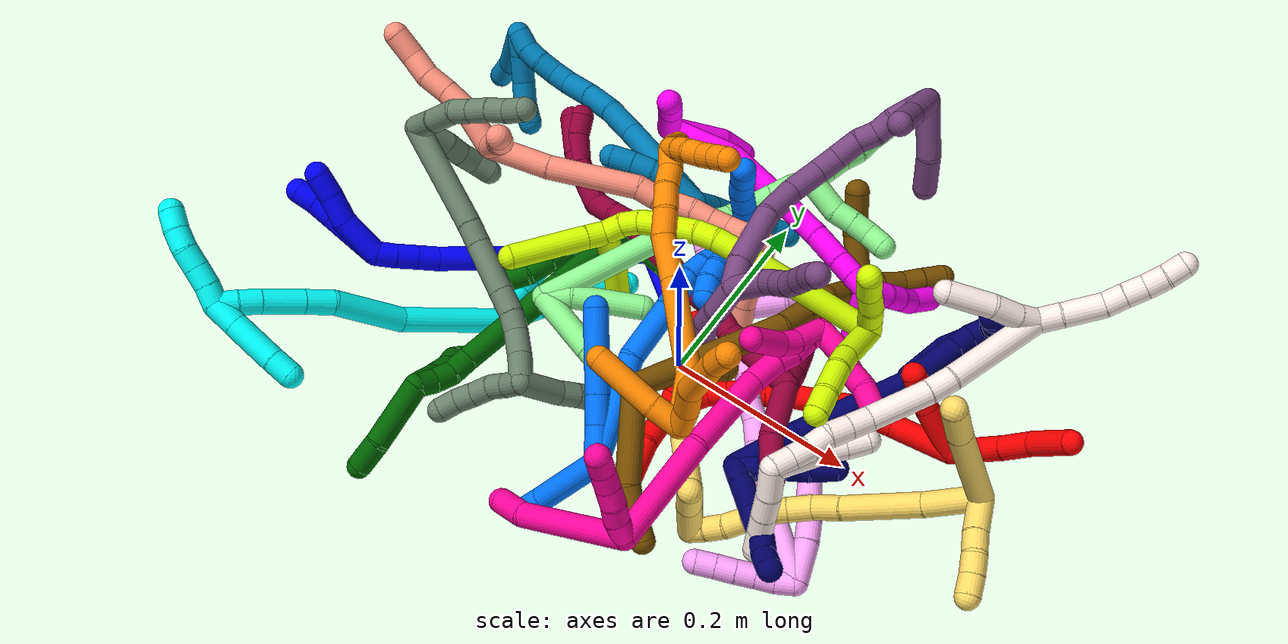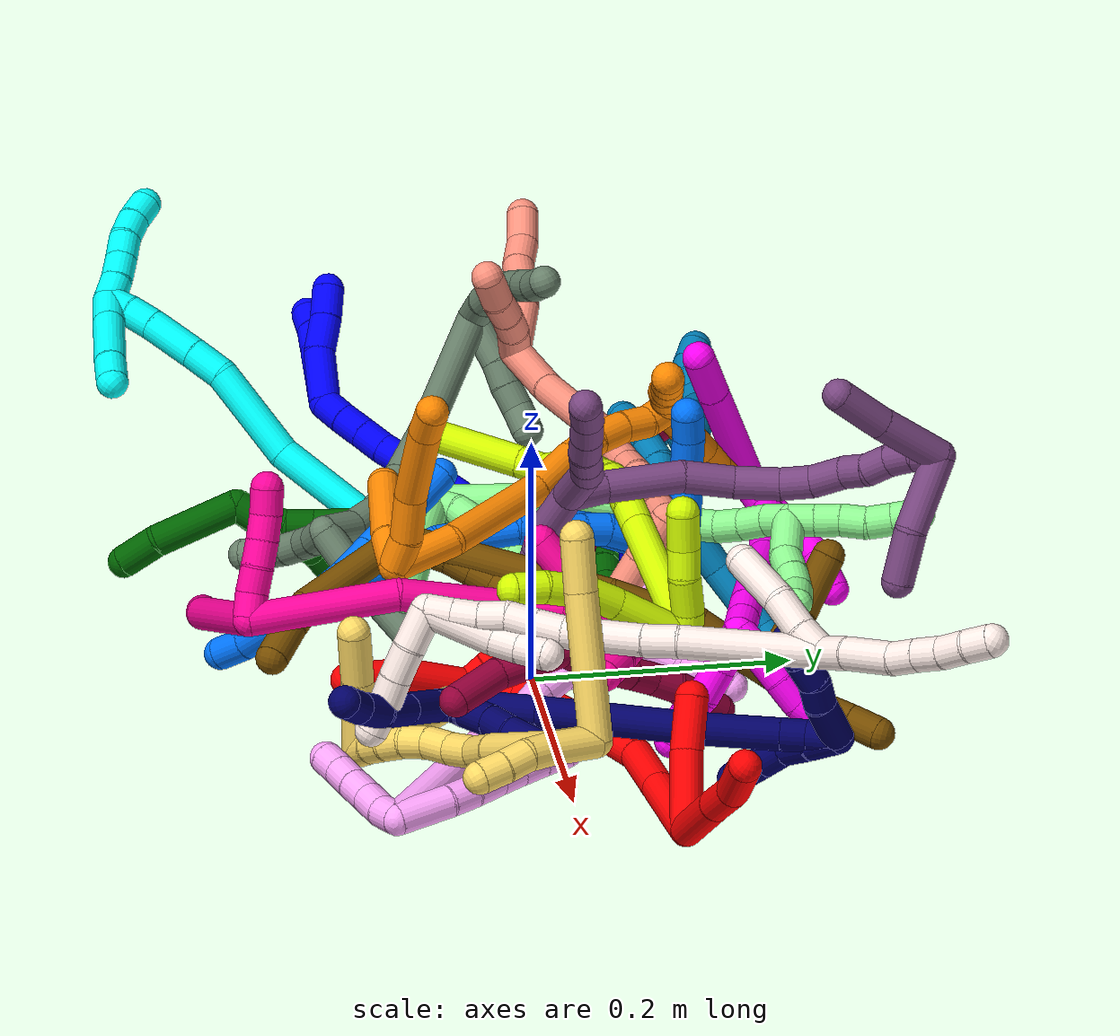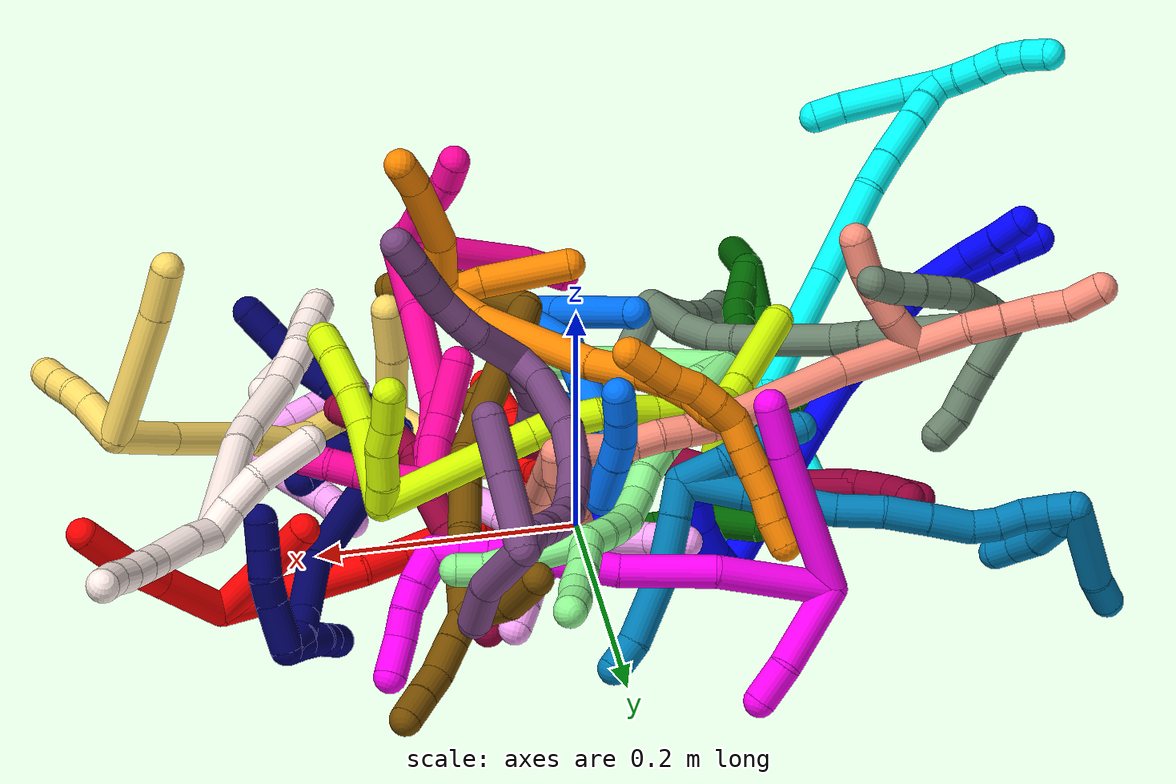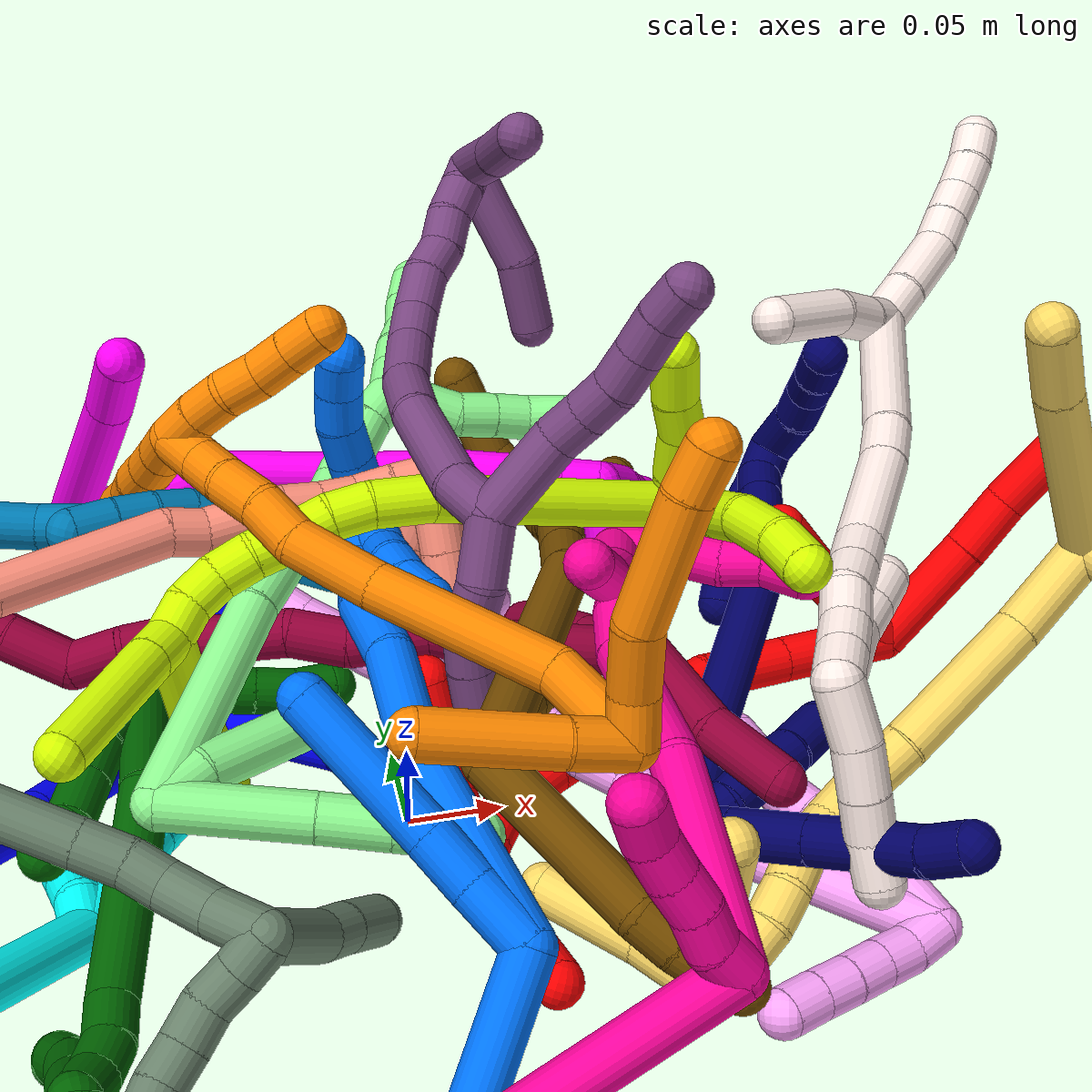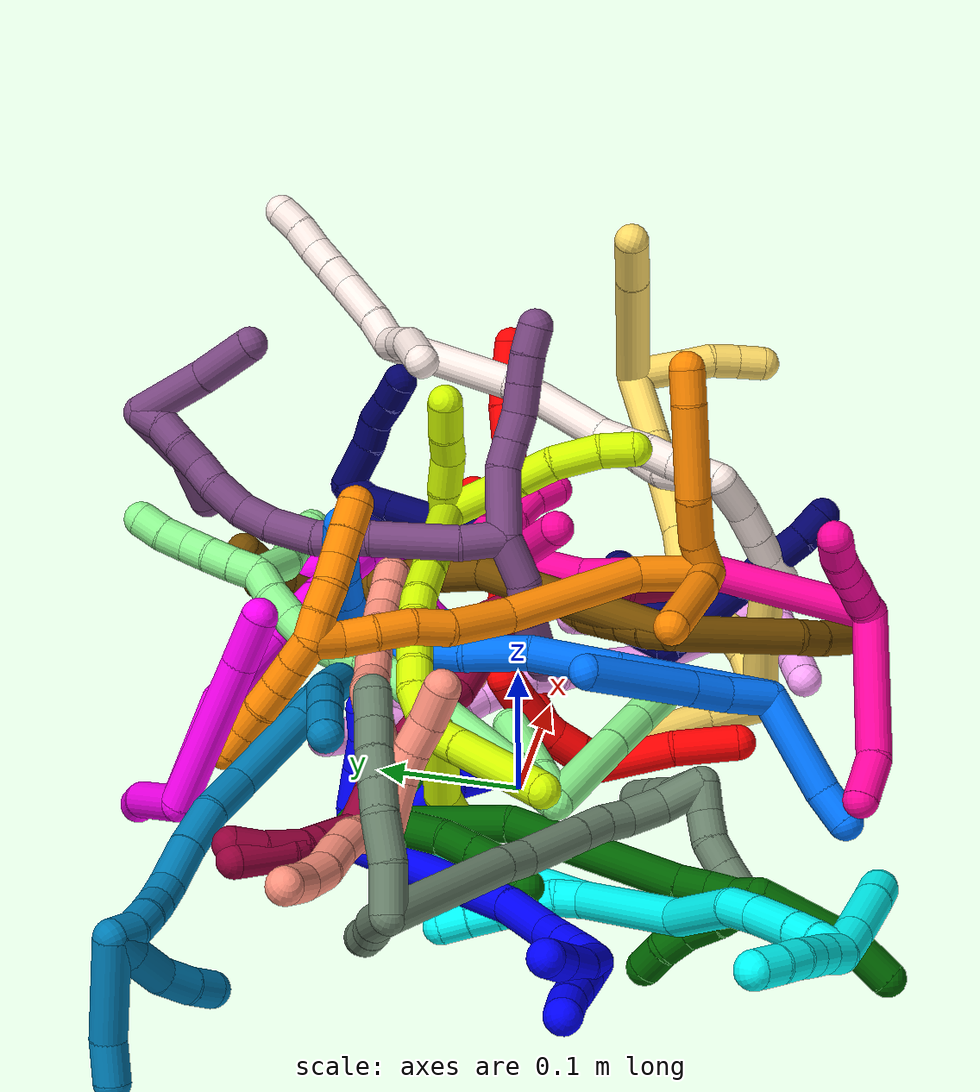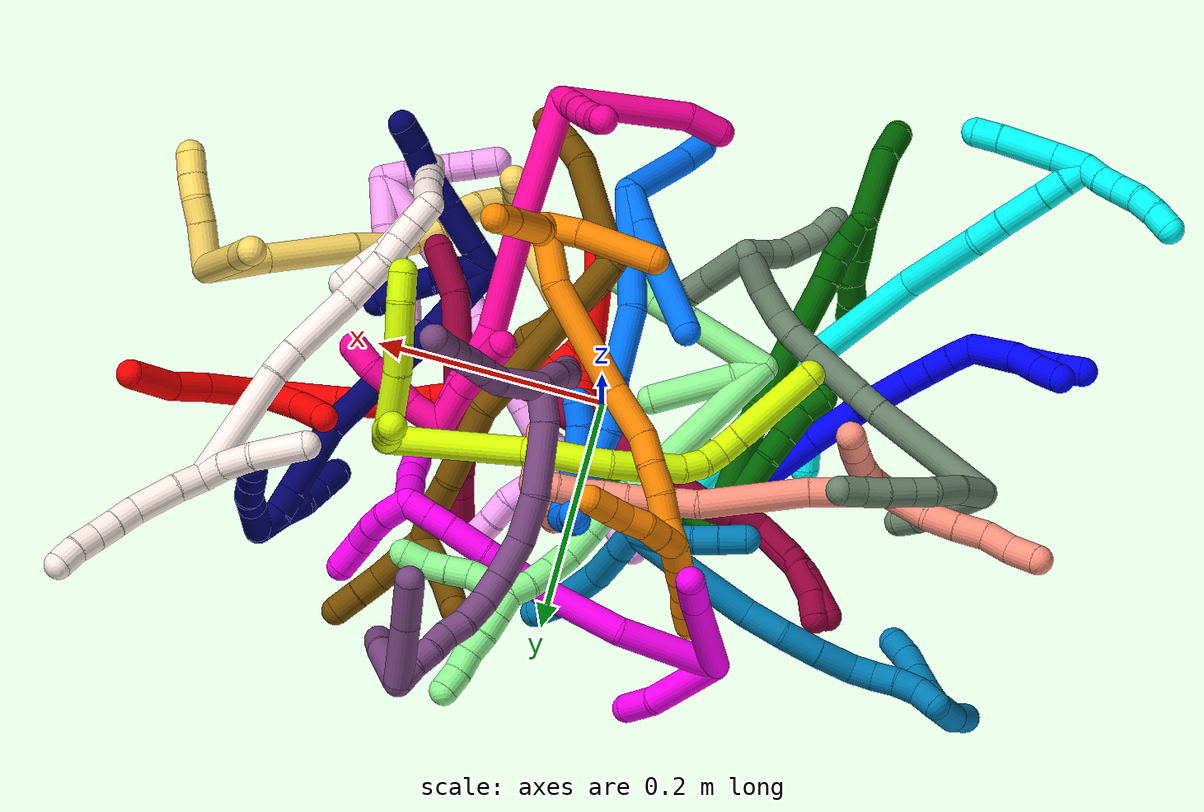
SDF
<sdf version="1.7">
 <world name="default">
  <plugin name="TubeGeneratorPlugin" filename="libtube_generator_plugin.so"/>
  <model name="photoneo_s_sensor">
   <static>1</static>
   <pose>0 0 2 1.57079 1.57079 3.14159</pose>
   <link name="link">
    <inertial><mass>0.1</mass></inertial>
    <sensor name="sensor" type="depth">
     <update_rate>30</update_rate>
     <camera>
      <horizontal_fov>1.22</horizontal_fov>
      <image><width>1920</width><height>1200</height><format>B8G8R8</format></image>
      <clip><near>0.1</near><far>4</far></clip>
      <depth_camera><output>points</output></depth_camera>
     </camera>
     <plugin name="camera_plugin" filename="libgazebo_ros_depth_camera.so">
      <baseline>0.2</baseline>
      <alwaysOn>1</alwaysOn>
      <updateRate>0.0</updateRate>
      <cameraName>camera_ir</cameraName>
      <imageTopicName>/camera/color/image_raw</imageTopicName>
      <cameraInfoTopicName>/camera/color/camera_info</cameraInfoTopicName>
      <depthImageTopicName>/camera/depth/image_raw</depthImageTopicName>
      <depthImageCameraInfoTopicName>/camera/depth/camera_info</depthImageCameraInfoTopicName>
      <pointCloudTopicName>/camera/depth/points</pointCloudTopicName>
      <frameName>fr_optical</frameName>
      <pointCloudCutoff>0.1</pointCloudCutoff>
      <pointCloudCutoffMax>2.0</pointCloudCutoffMax>
      <distortionK1>0</distortionK1>
      <distortionK2>0</distortionK2>
      <distortionK3>0</distortionK3>
      <distortionT1>0</distortionT1>
      <distortionT2>0</distortionT2>
      <CxPrime>0</CxPrime>
      <Cx>0</Cx>
      <Cy>0</Cy>
      <focalLength>0</focalLength>
      <hackBaseline>0</hackBaseline>
     </plugin>
    </sensor>
   </link>
  </model>
  <gravity>0 0 -9.8</gravity>
  <magnetic_field>6e-06 2.3e-05 -4.2e-05</magnetic_field>
  <atmosphere type="adiabatic"/>
  <physics name="default_physics" default="0" type="ode">
   <max_step_size>0.003</max_step_size>
   <real_time_factor>1</real_time_factor>
   <real_time_update_rate>1000</real_time_update_rate>
   <max_contacts>10000</max_contacts>
   <ode>
    <solver>
     <type>quick</type>
     <iters>100</iters>
     <sor>1.3</sor>
     <use_dynamic_moi_rescaling>0</use_dynamic_moi_rescaling>
    </solver>
    <constraints>
     <contact_max_correcting_vel>0</contact_max_correcting_vel>
     <contact_surface_layer>0.001</contact_surface_layer>
     <cfm>0</cfm>
     <erp>0.2</erp>
    </constraints>
   </ode>
  </physics>
  <scene><ambient>0.4 0.4 0.4 1</ambient><background>0.7 0.7 0.7 1</background><shadows>0</shadows></scene>
  <audio><device>default</device></audio>
  <spherical_coordinates>
   <surface_model>EARTH_WGS84</surface_model>
   <latitude_deg>0</latitude_deg>
   <longitude_deg>0</longitude_deg>
   <elevation>0</elevation>
   <heading_deg>0</heading_deg>
  </spherical_coordinates>
  <model name="bin">
   <static>1</static>
   <link name="bottom">
    <collision name="collision-bottom">
     <pose>0 0 -0.01 0 -0 0</pose>
     <geometry><box><size>0.8 0.6 0.02</size></box></geometry>
     <surface>
      <friction><ode><mu>100</mu><mu2>100</mu2></ode></friction>
      <contact><collide_bitmask>65535</collide_bitmask></contact>
     </surface>
    </collision>
   </link>
   <link name="west_wall">
    <collision name="collision-west_wall">
     <pose>-0.41 0 0.1 0 -0 0</pose>
     <geometry><box><size>0.02 0.6 0.2</size></box></geometry>
     <surface>
      <friction><ode><mu>100</mu><mu2>100</mu2></ode></friction>
      <contact><collide_bitmask>65535</collide_bitmask></contact>
     </surface>
    </collision>
   </link>
   <link name="east_wall">
    <collision name="collision-east_wall">
     <pose>0.41 0 0.1 0 -0 0</pose>
     <geometry><box><size>0.02 0.6 0.2</size></box></geometry>
     <surface>
      <friction><ode><mu>100</mu><mu2>100</mu2></ode></friction>
      <contact><collide_bitmask>65535</collide_bitmask></contact>
     </surface>
    </collision>
   </link>
   <link name="south_wall">
    <collision name="collision-south_wall">
     <pose>0 -0.31 0.1 0 -0 0</pose>
     <geometry><box><size>0.8 0.02 0.2</size></box></geometry>
     <surface>
      <friction><ode><mu>100</mu><mu2>100</mu2></ode></friction>
      <contact><collide_bitmask>65535</collide_bitmask></contact>
     </surface>
    </collision>
   </link>
   <link name="north_wall">
    <collision name="collision-north_wall">
     <pose>0 0.31 0.1 0 -0 0</pose>
     <geometry><box><size>0.8 0.02 0.2</size></box></geometry>
     <surface>
      <friction><ode><mu>100</mu><mu2>100</mu2></ode></friction>
      <contact><collide_bitmask>65535</collide_bitmask></contact>
     </surface>
    </collision>
   </link>
  </model>
  <model name="1">
   <static>0</static>
   <link name="1">
    <collision name="collision-cylinder-e_1_2_8">
     <pose>0.039429 -0.018064 -0.004624 1.82137 1.12906 1.36858</pose>
     <geometry><cylinder><radius>0.0125</radius><length>0.087232</length></cylinder></geometry>
     <surface>
      <friction><ode><mu>1.16</mu><mu2>1.16</mu2><slip1>0</slip1><slip2>0</slip2></ode></friction>
      <contact><ode><kp>1e+06</kp><kd>1</kd><max_vel>0</max_vel><min_depth>0.001</min_depth></ode></contact>
     </surface>
    </collision>
    <visual name="visual-cylinder-e_1_2_8">
     <pose>0.039429 -0.018064 -0.004624 1.82137 1.12906 1.36858</pose>
     <geometry><cylinder><radius>0.0125</radius><length>0.087232</length></cylinder></geometry>
     <material><ambient>0 0 1 1</ambient></material>
    </visual>
    <collision name="collision-cylinder-e_2_8_9">
     <pose>0.087233 -0.042908 -0.012698 2.04164 0.833307 1.25052</pose>
     <geometry><cylinder><radius>0.0125</radius><length>0.022628</length></cylinder></geometry>
     <surface>
      <friction><ode><mu>1.16</mu><mu2>1.16</mu2><slip1>0</slip1><slip2>0</slip2></ode></friction>
      <contact><ode><kp>1e+06</kp><kd>1</kd><max_vel>0</max_vel><min_depth>0.001</min_depth></ode></contact>
     </surface>
    </collision>
    <visual name="visual-cylinder-e_2_8_9">
     <pose>0.087233 -0.042908 -0.012698 2.04164 0.833307 1.25052</pose>
     <geometry><cylinder><radius>0.0125</radius><length>0.022628</length></cylinder></geometry>
     <material><ambient>0 0 1 1</ambient></material>
    </visual>
    <collision name="collision-cylinder-e_3_9_10">
     <pose>0.103307 -0.0557 -0.018335 1.91939 0.87759 1.18049</pose>
     <geometry><cylinder><radius>0.0125</radius><length>0.020021</length></cylinder></geometry>
     <surface>
      <friction><ode><mu>1.16</mu><mu2>1.16</mu2><slip1>0</slip1><slip2>0</slip2></ode></friction>
      <contact><ode><kp>1e+06</kp><kd>1</kd><max_vel>0</max_vel><min_depth>0.001</min_depth></ode></contact>
     </surface>
    </collision>
    <visual name="visual-cylinder-e_3_9_10">
     <pose>0.103307 -0.0557 -0.018335 1.91939 0.87759 1.18049</pose>
     <geometry><cylinder><radius>0.0125</radius><length>0.020021</length></cylinder></geometry>
     <material><ambient>0 0 1 1</ambient></material>
    </visual>
    <collision name="collision-cylinder-e_4_10_6">
     <pose>0.117269 -0.069582 -0.020314 1.5447 0.67191 0.65583</pose>
     <geometry><cylinder><radius>0.0125</radius><length>0.020119</length></cylinder></geometry>
     <surface>
      <friction><ode><mu>1.16</mu><mu2>1.16</mu2><slip1>0</slip1><slip2>0</slip2></ode></friction>
      <contact><ode><kp>1e+06</kp><kd>1</kd><max_vel>0</max_vel><min_depth>0.001</min_depth></ode></contact>
     </surface>
    </collision>
    <visual name="visual-cylinder-e_4_10_6">
     <pose>0.117269 -0.069582 -0.020314 1.5447 0.67191 0.65583</pose>
     <geometry><cylinder><radius>0.0125</radius><length>0.020119</length></cylinder></geometry>
     <material><ambient>0 0 1 1</ambient></material>
    </visual>
    <collision name="collision-cylinder-e_1_2_11">
     <pose>0.009411 0.00786 0.003095 -1.19567 0.839293 -0.589899</pose>
     <geometry><cylinder><radius>0.0125</radius><length>0.025292</length></cylinder></geometry>
     <surface>
      <friction><ode><mu>1.16</mu><mu2>1.16</mu2><slip1>0</slip1><slip2>0</slip2></ode></friction>
      <contact><ode><kp>1e+06</kp><kd>1</kd><max_vel>0</max_vel><min_depth>0.001</min_depth></ode></contact>
     </surface>
    </collision>
    <visual name="visual-cylinder-e_1_2_11">
     <pose>0.009411 0.00786 0.003095 -1.19567 0.839293 -0.589899</pose>
     <geometry><cylinder><radius>0.0125</radius><length>0.025292</length></cylinder></geometry>
     <material><ambient>0 0 1 1</ambient></material>
    </visual>
    <collision name="collision-cylinder-e_2_11_12">
     <pose>0.029659 0.022087 0.012674 -0.776329 0.872968 -0.376979</pose>
     <geometry><cylinder><radius>0.0125</radius><length>0.028286</length></cylinder></geometry>
     <surface>
      <friction><ode><mu>1.16</mu><mu2>1.16</mu2><slip1>0</slip1><slip2>0</slip2></ode></friction>
      <contact><ode><kp>1e+06</kp><kd>1</kd><max_vel>0</max_vel><min_depth>0.001</min_depth></ode></contact>
     </surface>
    </collision>
    <visual name="visual-cylinder-e_2_11_12">
     <pose>0.029659 0.022087 0.012674 -0.776329 0.872968 -0.376979</pose>
     <geometry><cylinder><radius>0.0125</radius><length>0.028286</length></cylinder></geometry>
     <material><ambient>0 0 1 1</ambient></material>
    </visual>
    <collision name="collision-cylinder-e_3_12_13">
     <pose>0.048261 0.033853 0.027501 -0.574313 0.663346 -0.202715</pose>
     <geometry><cylinder><radius>0.0125</radius><length>0.025225</length></cylinder></geometry>
     <surface>
      <friction><ode><mu>1.16</mu><mu2>1.16</mu2><slip1>0</slip1><slip2>0</slip2></ode></friction>
      <contact><ode><kp>1e+06</kp><kd>1</kd><max_vel>0</max_vel><min_depth>0.001</min_depth></ode></contact>
     </surface>
    </collision>
    <visual name="visual-cylinder-e_3_12_13">
     <pose>0.048261 0.033853 0.027501 -0.574313 0.663346 -0.202715</pose>
     <geometry><cylinder><radius>0.0125</radius><length>0.025225</length></cylinder></geometry>
     <material><ambient>0 0 1 1</ambient></material>
    </visual>
    <collision name="collision-cylinder-e_4_13_5">
     <pose>0.062538 0.046163 0.040555 -0.972519 0.661446 -0.359059</pose>
     <geometry><cylinder><radius>0.0125</radius><length>0.021197</length></cylinder></geometry>
     <surface>
      <friction><ode><mu>1.16</mu><mu2>1.16</mu2><slip1>0</slip1><slip2>0</slip2></ode></friction>
      <contact><ode><kp>1e+06</kp><kd>1</kd><max_vel>0</max_vel><min_depth>0.001</min_depth></ode></contact>
     </surface>
    </collision>
    <visual name="visual-cylinder-e_4_13_5">
     <pose>0.062538 0.046163 0.040555 -0.972519 0.661446 -0.359059</pose>
     <geometry><cylinder><radius>0.0125</radius><length>0.021197</length></cylinder></geometry>
     <material><ambient>0 0 1 1</ambient></material>
    </visual>
    <collision name="collision-cylinder-e_1_2_14">
     <pose>-0.007918 -0.030936 0.062481 0.459736 -0.113083 -0.026489</pose>
     <geometry><cylinder><radius>0.0125</radius><length>0.140337</length></cylinder></geometry>
     <surface>
      <friction><ode><mu>1.16</mu><mu2>1.16</mu2><slip1>0</slip1><slip2>0</slip2></ode></friction>
      <contact><ode><kp>1e+06</kp><kd>1</kd><max_vel>0</max_vel><min_depth>0.001</min_depth></ode></contact>
     </surface>
    </collision>
    <visual name="visual-cylinder-e_1_2_14">
     <pose>-0.007918 -0.030936 0.062481 0.459736 -0.113083 -0.026489</pose>
     <geometry><cylinder><radius>0.0125</radius><length>0.140337</length></cylinder></geometry>
     <material><ambient>0 0 1 1</ambient></material>
    </visual>
    <collision name="collision-cylinder-e_2_14_15">
     <pose>-0.018863 -0.071076 0.146037 0.411786 -0.130894 -0.027375</pose>
     <geometry><cylinder><radius>0.0125</radius><length>0.046391</length></cylinder></geometry>
     <surface>
      <friction><ode><mu>1.16</mu><mu2>1.16</mu2><slip1>0</slip1><slip2>0</slip2></ode></friction>
      <contact><ode><kp>1e+06</kp><kd>1</kd><max_vel>0</max_vel><min_depth>0.001</min_depth></ode></contact>
     </surface>
    </collision>
    <visual name="visual-cylinder-e_2_14_15">
     <pose>-0.018863 -0.071076 0.146037 0.411786 -0.130894 -0.027375</pose>
     <geometry><cylinder><radius>0.0125</radius><length>0.046391</length></cylinder></geometry>
     <material><ambient>0 0 1 1</ambient></material>
    </visual>
    <collision name="collision-cylinder-e_3_15_16">
     <pose>-0.02804 -0.091279 0.188035 0.483958 -0.254475 -0.063129</pose>
     <geometry><cylinder><radius>0.0125</radius><length>0.04885</length></cylinder></geometry>
     <surface>
      <friction><ode><mu>1.16</mu><mu2>1.16</mu2><slip1>0</slip1><slip2>0</slip2></ode></friction>
      <contact><ode><kp>1e+06</kp><kd>1</kd><max_vel>0</max_vel><min_depth>0.001</min_depth></ode></contact>
     </surface>
    </collision>
    <visual name="visual-cylinder-e_3_15_16">
     <pose>-0.02804 -0.091279 0.188035 0.483958 -0.254475 -0.063129</pose>
     <geometry><cylinder><radius>0.0125</radius><length>0.04885</length></cylinder></geometry>
     <material><ambient>0 0 1 1</ambient></material>
    </visual>
    <collision name="collision-cylinder-e_4_16_17">
     <pose>-0.036702 -0.106202 0.218948 0.374365 -0.23012 -0.043771</pose>
     <geometry><cylinder><radius>0.0125</radius><length>0.022046</length></cylinder></geometry>
     <surface>
      <friction><ode><mu>1.16</mu><mu2>1.16</mu2><slip1>0</slip1><slip2>0</slip2></ode></friction>
      <contact><ode><kp>1e+06</kp><kd>1</kd><max_vel>0</max_vel><min_depth>0.001</min_depth></ode></contact>
     </surface>
    </collision>
    <visual name="visual-cylinder-e_4_16_17">
     <pose>-0.036702 -0.106202 0.218948 0.374365 -0.23012 -0.043771</pose>
     <geometry><cylinder><radius>0.0125</radius><length>0.022046</length></cylinder></geometry>
     <material><ambient>0 0 1 1</ambient></material>
    </visual>
    <collision name="collision-cylinder-e_5_17_18">
     <pose>-0.041681 -0.114055 0.238658 0.38404 -0.230857 -0.045075</pose>
     <geometry><cylinder><radius>0.0125</radius><length>0.021542</length></cylinder></geometry>
     <surface>
      <friction><ode><mu>1.16</mu><mu2>1.16</mu2><slip1>0</slip1><slip2>0</slip2></ode></friction>
      <contact><ode><kp>1e+06</kp><kd>1</kd><max_vel>0</max_vel><min_depth>0.001</min_depth></ode></contact>
     </surface>
    </collision>
    <visual name="visual-cylinder-e_5_17_18">
     <pose>-0.041681 -0.114055 0.238658 0.38404 -0.230857 -0.045075</pose>
     <geometry><cylinder><radius>0.0125</radius><length>0.021542</length></cylinder></geometry>
     <material><ambient>0 0 1 1</ambient></material>
    </visual>
    <collision name="collision-cylinder-e_6_18_1">
     <pose>-0.047073 -0.1213 0.257811 0.338115 -0.28487 -0.048945</pose>
     <geometry><cylinder><radius>0.0125</radius><length>0.020835</length></cylinder></geometry>
     <surface>
      <friction><ode><mu>1.16</mu><mu2>1.16</mu2><slip1>0</slip1><slip2>0</slip2></ode></friction>
      <contact><ode><kp>1e+06</kp><kd>1</kd><max_vel>0</max_vel><min_depth>0.001</min_depth></ode></contact>
     </surface>
    </collision>
    <visual name="visual-cylinder-e_6_18_1">
     <pose>-0.047073 -0.1213 0.257811 0.338115 -0.28487 -0.048945</pose>
     <geometry><cylinder><radius>0.0125</radius><length>0.020835</length></cylinder></geometry>
     <material><ambient>0 0 1 1</ambient></material>
    </visual>
    <collision name="collision-cylinder-e_1_1_19">
     <pose>-0.059582 -0.12189 0.278422 -0.23921 -0.694347 0.086913</pose>
     <geometry><cylinder><radius>0.0125</radius><length>0.029946</length></cylinder></geometry>
     <surface>
      <friction><ode><mu>1.16</mu><mu2>1.16</mu2><slip1>0</slip1><slip2>0</slip2></ode></friction>
      <contact><ode><kp>1e+06</kp><kd>1</kd><max_vel>0</max_vel><min_depth>0.001</min_depth></ode></contact>
     </surface>
    </collision>
    <visual name="visual-cylinder-e_1_1_19">
     <pose>-0.059582 -0.12189 0.278422 -0.23921 -0.694347 0.086913</pose>
     <geometry><cylinder><radius>0.0125</radius><length>0.029946</length></cylinder></geometry>
     <material><ambient>0 0 1 1</ambient></material>
    </visual>
    <collision name="collision-cylinder-e_2_19_20">
     <pose>-0.07757 -0.116336 0.30056 -0.252533 -0.638851 0.083923</pose>
     <geometry><cylinder><radius>0.0125</radius><length>0.028199</length></cylinder></geometry>
     <surface>
      <friction><ode><mu>1.16</mu><mu2>1.16</mu2><slip1>0</slip1><slip2>0</slip2></ode></friction>
      <contact><ode><kp>1e+06</kp><kd>1</kd><max_vel>0</max_vel><min_depth>0.001</min_depth></ode></contact>
     </surface>
    </collision>
    <visual name="visual-cylinder-e_2_19_20">
     <pose>-0.07757 -0.116336 0.30056 -0.252533 -0.638851 0.083923</pose>
     <geometry><cylinder><radius>0.0125</radius><length>0.028199</length></cylinder></geometry>
     <material><ambient>0 0 1 1</ambient></material>
    </visual>
    <collision name="collision-cylinder-e_3_20_21">
     <pose>-0.092181 -0.111378 0.319882 -0.249386 -0.623315 0.080716</pose>
     <geometry><cylinder><radius>0.0125</radius><length>0.021255</length></cylinder></geometry>
     <surface>
      <friction><ode><mu>1.16</mu><mu2>1.16</mu2><slip1>0</slip1><slip2>0</slip2></ode></friction>
      <contact><ode><kp>1e+06</kp><kd>1</kd><max_vel>0</max_vel><min_depth>0.001</min_depth></ode></contact>
     </surface>
    </collision>
    <visual name="visual-cylinder-e_3_20_21">
     <pose>-0.092181 -0.111378 0.319882 -0.249386 -0.623315 0.080716</pose>
     <geometry><cylinder><radius>0.0125</radius><length>0.021255</length></cylinder></geometry>
     <material><ambient>0 0 1 1</ambient></material>
    </visual>
    <collision name="collision-cylinder-e_4_21_4">
     <pose>-0.104919 -0.108522 0.336173 -0.091331 -0.687258 0.0327</pose>
     <geometry><cylinder><radius>0.0125</radius><length>0.0206</length></cylinder></geometry>
     <surface>
      <friction><ode><mu>1.16</mu><mu2>1.16</mu2><slip1>0</slip1><slip2>0</slip2></ode></friction>
      <contact><ode><kp>1e+06</kp><kd>1</kd><max_vel>0</max_vel><min_depth>0.001</min_depth></ode></contact>
     </surface>
    </collision>
    <visual name="visual-cylinder-e_4_21_4">
     <pose>-0.104919 -0.108522 0.336173 -0.091331 -0.687258 0.0327</pose>
     <geometry><cylinder><radius>0.0125</radius><length>0.0206</length></cylinder></geometry>
     <material><ambient>0 0 1 1</ambient></material>
    </visual>
    <collision name="collision-cylinder-e_1_1_22">
     <pose>-0.059348 -0.117236 0.286527 -0.365524 -0.425088 0.079729</pose>
     <geometry><cylinder><radius>0.0125</radius><length>0.04533</length></cylinder></geometry>
     <surface>
      <friction><ode><mu>1.16</mu><mu2>1.16</mu2><slip1>0</slip1><slip2>0</slip2></ode></friction>
      <contact><ode><kp>1e+06</kp><kd>1</kd><max_vel>0</max_vel><min_depth>0.001</min_depth></ode></contact>
     </surface>
    </collision>
    <visual name="visual-cylinder-e_1_1_22">
     <pose>-0.059348 -0.117236 0.286527 -0.365524 -0.425088 0.079729</pose>
     <geometry><cylinder><radius>0.0125</radius><length>0.04533</length></cylinder></geometry>
     <material><ambient>0 0 1 1</ambient></material>
    </visual>
    <collision name="collision-cylinder-e_2_22_23">
     <pose>-0.074155 -0.101312 0.316379 -0.679879 -0.381993 0.136554</pose>
     <geometry><cylinder><radius>0.0125</radius><length>0.02929</length></cylinder></geometry>
     <surface>
      <friction><ode><mu>1.16</mu><mu2>1.16</mu2><slip1>0</slip1><slip2>0</slip2></ode></friction>
      <contact><ode><kp>1e+06</kp><kd>1</kd><max_vel>0</max_vel><min_depth>0.001</min_depth></ode></contact>
     </surface>
    </collision>
    <visual name="visual-cylinder-e_2_22_23">
     <pose>-0.074155 -0.101312 0.316379 -0.679879 -0.381993 0.136554</pose>
     <geometry><cylinder><radius>0.0125</radius><length>0.02929</length></cylinder></geometry>
     <material><ambient>0 0 1 1</ambient></material>
    </visual>
    <collision name="collision-cylinder-e_3_23_3">
     <pose>-0.083937 -0.086214 0.336916 -0.581509 -0.347594 0.104976</pose>
     <geometry><cylinder><radius>0.0125</radius><length>0.025379</length></cylinder></geometry>
     <surface>
      <friction><ode><mu>1.16</mu><mu2>1.16</mu2><slip1>0</slip1><slip2>0</slip2></ode></friction>
      <contact><ode><kp>1e+06</kp><kd>1</kd><max_vel>0</max_vel><min_depth>0.001</min_depth></ode></contact>
     </surface>
    </collision>
    <visual name="visual-cylinder-e_3_23_3">
     <pose>-0.083937 -0.086214 0.336916 -0.581509 -0.347594 0.104976</pose>
     <geometry><cylinder><radius>0.0125</radius><length>0.025379</length></cylinder></geometry>
     <material><ambient>0 0 1 1</ambient></material>
    </visual>
    <collision name="collision-sphere-3">
     <pose>-0.088259 -0.079661 0.346886 0 -0 0</pose>
     <geometry><sphere><radius>0.0125</radius></sphere></geometry>
     <surface>
      <friction><ode><mu>1.16</mu><mu2>1.16</mu2><slip1>0</slip1><slip2>0</slip2></ode></friction>
      <contact><ode><kp>1e+06</kp><kd>1</kd><max_vel>0</max_vel><min_depth>0.001</min_depth></ode></contact>
     </surface>
    </collision>
    <visual name="visual-sphere-3">
     <pose>-0.088259 -0.079661 0.346886 0 -0 0</pose>
     <geometry><sphere><radius>0.0125</radius></sphere></geometry>
     <material><ambient>0 0 1 1</ambient></material>
    </visual>
    <collision name="collision-sphere-23">
     <pose>-0.079614 -0.092768 0.326947 0 -0 0</pose>
     <geometry><sphere><radius>0.0125</radius></sphere></geometry>
     <surface>
      <friction><ode><mu>1.16</mu><mu2>1.16</mu2><slip1>0</slip1><slip2>0</slip2></ode></friction>
      <contact><ode><kp>1e+06</kp><kd>1</kd><max_vel>0</max_vel><min_depth>0.001</min_depth></ode></contact>
     </surface>
    </collision>
    <visual name="visual-sphere-23">
     <pose>-0.079614 -0.092768 0.326947 0 -0 0</pose>
     <geometry><sphere><radius>0.0125</radius></sphere></geometry>
     <material><ambient>0 0 1 1</ambient></material>
    </visual>
    <collision name="collision-sphere-22">
     <pose>-0.068695 -0.109855 0.305811 0 -0 0</pose>
     <geometry><sphere><radius>0.0125</radius></sphere></geometry>
     <surface>
      <friction><ode><mu>1.16</mu><mu2>1.16</mu2><slip1>0</slip1><slip2>0</slip2></ode></friction>
      <contact><ode><kp>1e+06</kp><kd>1</kd><max_vel>0</max_vel><min_depth>0.001</min_depth></ode></contact>
     </surface>
    </collision>
    <visual name="visual-sphere-22">
     <pose>-0.068695 -0.109855 0.305811 0 -0 0</pose>
     <geometry><sphere><radius>0.0125</radius></sphere></geometry>
     <material><ambient>0 0 1 1</ambient></material>
    </visual>
    <collision name="collision-sphere-4">
     <pose>-0.111454 -0.107796 0.344101 0 -0 0</pose>
     <geometry><sphere><radius>0.0125</radius></sphere></geometry>
     <surface>
      <friction><ode><mu>1.16</mu><mu2>1.16</mu2><slip1>0</slip1><slip2>0</slip2></ode></friction>
      <contact><ode><kp>1e+06</kp><kd>1</kd><max_vel>0</max_vel><min_depth>0.001</min_depth></ode></contact>
     </surface>
    </collision>
    <visual name="visual-sphere-4">
     <pose>-0.111454 -0.107796 0.344101 0 -0 0</pose>
     <geometry><sphere><radius>0.0125</radius></sphere></geometry>
     <material><ambient>0 0 1 1</ambient></material>
    </visual>
    <collision name="collision-sphere-21">
     <pose>-0.098385 -0.109248 0.328244 0 -0 0</pose>
     <geometry><sphere><radius>0.0125</radius></sphere></geometry>
     <surface>
      <friction><ode><mu>1.16</mu><mu2>1.16</mu2><slip1>0</slip1><slip2>0</slip2></ode></friction>
      <contact><ode><kp>1e+06</kp><kd>1</kd><max_vel>0</max_vel><min_depth>0.001</min_depth></ode></contact>
     </surface>
    </collision>
    <visual name="visual-sphere-21">
     <pose>-0.098385 -0.109248 0.328244 0 -0 0</pose>
     <geometry><sphere><radius>0.0125</radius></sphere></geometry>
     <material><ambient>0 0 1 1</ambient></material>
    </visual>
    <collision name="collision-sphere-20">
     <pose>-0.085977 -0.113508 0.31152 0 -0 0</pose>
     <geometry><sphere><radius>0.0125</radius></sphere></geometry>
     <surface>
      <friction><ode><mu>1.16</mu><mu2>1.16</mu2><slip1>0</slip1><slip2>0</slip2></ode></friction>
      <contact><ode><kp>1e+06</kp><kd>1</kd><max_vel>0</max_vel><min_depth>0.001</min_depth></ode></contact>
     </surface>
    </collision>
    <visual name="visual-sphere-20">
     <pose>-0.085977 -0.113508 0.31152 0 -0 0</pose>
     <geometry><sphere><radius>0.0125</radius></sphere></geometry>
     <material><ambient>0 0 1 1</ambient></material>
    </visual>
    <collision name="collision-sphere-11">
     <pose>0.018822 0.01572 0.00619 0 -0 0</pose>
     <geometry><sphere><radius>0.0125</radius></sphere></geometry>
     <surface>
      <friction><ode><mu>1.16</mu><mu2>1.16</mu2><slip1>0</slip1><slip2>0</slip2></ode></friction>
      <contact><ode><kp>1e+06</kp><kd>1</kd><max_vel>0</max_vel><min_depth>0.001</min_depth></ode></contact>
     </surface>
    </collision>
    <visual name="visual-sphere-11">
     <pose>0.018822 0.01572 0.00619 0 -0 0</pose>
     <geometry><sphere><radius>0.0125</radius></sphere></geometry>
     <material><ambient>0 0 1 1</ambient></material>
    </visual>
    <collision name="collision-sphere-6">
     <pose>0.123531 -0.077452 -0.020109 0 -0 0</pose>
     <geometry><sphere><radius>0.0125</radius></sphere></geometry>
     <surface>
      <friction><ode><mu>1.16</mu><mu2>1.16</mu2><slip1>0</slip1><slip2>0</slip2></ode></friction>
      <contact><ode><kp>1e+06</kp><kd>1</kd><max_vel>0</max_vel><min_depth>0.001</min_depth></ode></contact>
     </surface>
    </collision>
    <visual name="visual-sphere-6">
     <pose>0.123531 -0.077452 -0.020109 0 -0 0</pose>
     <geometry><sphere><radius>0.0125</radius></sphere></geometry>
     <material><ambient>0 0 1 1</ambient></material>
    </visual>
    <collision name="collision-sphere-10">
     <pose>0.111007 -0.061712 -0.02052 0 -0 0</pose>
     <geometry><sphere><radius>0.0125</radius></sphere></geometry>
     <surface>
      <friction><ode><mu>1.16</mu><mu2>1.16</mu2><slip1>0</slip1><slip2>0</slip2></ode></friction>
      <contact><ode><kp>1e+06</kp><kd>1</kd><max_vel>0</max_vel><min_depth>0.001</min_depth></ode></contact>
     </surface>
    </collision>
    <visual name="visual-sphere-10">
     <pose>0.111007 -0.061712 -0.02052 0 -0 0</pose>
     <geometry><sphere><radius>0.0125</radius></sphere></geometry>
     <material><ambient>0 0 1 1</ambient></material>
    </visual>
    <collision name="collision-sphere-9">
     <pose>0.095607 -0.049688 -0.016149 0 -0 0</pose>
     <geometry><sphere><radius>0.0125</radius></sphere></geometry>
     <surface>
      <friction><ode><mu>1.16</mu><mu2>1.16</mu2><slip1>0</slip1><slip2>0</slip2></ode></friction>
      <contact><ode><kp>1e+06</kp><kd>1</kd><max_vel>0</max_vel><min_depth>0.001</min_depth></ode></contact>
     </surface>
    </collision>
    <visual name="visual-sphere-9">
     <pose>0.095607 -0.049688 -0.016149 0 -0 0</pose>
     <geometry><sphere><radius>0.0125</radius></sphere></geometry>
     <material><ambient>0 0 1 1</ambient></material>
    </visual>
    <collision name="collision-sphere-2">
     <geometry><sphere><radius>0.0125</radius></sphere></geometry>
     <surface>
      <friction><ode><mu>1.16</mu><mu2>1.16</mu2><slip1>0</slip1><slip2>0</slip2></ode></friction>
      <contact><ode><kp>1e+06</kp><kd>1</kd><max_vel>0</max_vel><min_depth>0.001</min_depth></ode></contact>
     </surface>
    </collision>
    <visual name="visual-sphere-2">
     <geometry><sphere><radius>0.0125</radius></sphere></geometry>
     <material><ambient>0 0 1 1</ambient></material>
    </visual>
    <collision name="collision-sphere-19">
     <pose>-0.069163 -0.119164 0.2896 0 -0 0</pose>
     <geometry><sphere><radius>0.0125</radius></sphere></geometry>
     <surface>
      <friction><ode><mu>1.16</mu><mu2>1.16</mu2><slip1>0</slip1><slip2>0</slip2></ode></friction>
      <contact><ode><kp>1e+06</kp><kd>1</kd><max_vel>0</max_vel><min_depth>0.001</min_depth></ode></contact>
     </surface>
    </collision>
    <visual name="visual-sphere-19">
     <pose>-0.069163 -0.119164 0.2896 0 -0 0</pose>
     <geometry><sphere><radius>0.0125</radius></sphere></geometry>
     <material><ambient>0 0 1 1</ambient></material>
    </visual>
    <collision name="collision-sphere-8">
     <pose>0.078859 -0.036128 -0.009247 0 -0 0</pose>
     <geometry><sphere><radius>0.0125</radius></sphere></geometry>
     <surface>
      <friction><ode><mu>1.16</mu><mu2>1.16</mu2><slip1>0</slip1><slip2>0</slip2></ode></friction>
      <contact><ode><kp>1e+06</kp><kd>1</kd><max_vel>0</max_vel><min_depth>0.001</min_depth></ode></contact>
     </surface>
    </collision>
    <visual name="visual-sphere-8">
     <pose>0.078859 -0.036128 -0.009247 0 -0 0</pose>
     <geometry><sphere><radius>0.0125</radius></sphere></geometry>
     <material><ambient>0 0 1 1</ambient></material>
    </visual>
    <collision name="collision-sphere-12">
     <pose>0.040495 0.028455 0.019158 0 -0 0</pose>
     <geometry><sphere><radius>0.0125</radius></sphere></geometry>
     <surface>
      <friction><ode><mu>1.16</mu><mu2>1.16</mu2><slip1>0</slip1><slip2>0</slip2></ode></friction>
      <contact><ode><kp>1e+06</kp><kd>1</kd><max_vel>0</max_vel><min_depth>0.001</min_depth></ode></contact>
     </surface>
    </collision>
    <visual name="visual-sphere-12">
     <pose>0.040495 0.028455 0.019158 0 -0 0</pose>
     <geometry><sphere><radius>0.0125</radius></sphere></geometry>
     <material><ambient>0 0 1 1</ambient></material>
    </visual>
    <collision name="collision-sphere-13">
     <pose>0.056028 0.039252 0.035845 0 -0 0</pose>
     <geometry><sphere><radius>0.0125</radius></sphere></geometry>
     <surface>
      <friction><ode><mu>1.16</mu><mu2>1.16</mu2><slip1>0</slip1><slip2>0</slip2></ode></friction>
      <contact><ode><kp>1e+06</kp><kd>1</kd><max_vel>0</max_vel><min_depth>0.001</min_depth></ode></contact>
     </surface>
    </collision>
    <visual name="visual-sphere-13">
     <pose>0.056028 0.039252 0.035845 0 -0 0</pose>
     <geometry><sphere><radius>0.0125</radius></sphere></geometry>
     <material><ambient>0 0 1 1</ambient></material>
    </visual>
    <collision name="collision-sphere-5">
     <pose>0.069048 0.053074 0.045266 0 -0 0</pose>
     <geometry><sphere><radius>0.0125</radius></sphere></geometry>
     <surface>
      <friction><ode><mu>1.16</mu><mu2>1.16</mu2><slip1>0</slip1><slip2>0</slip2></ode></friction>
      <contact><ode><kp>1e+06</kp><kd>1</kd><max_vel>0</max_vel><min_depth>0.001</min_depth></ode></contact>
     </surface>
    </collision>
    <visual name="visual-sphere-5">
     <pose>0.069048 0.053074 0.045266 0 -0 0</pose>
     <geometry><sphere><radius>0.0125</radius></sphere></geometry>
     <material><ambient>0 0 1 1</ambient></material>
    </visual>
    <collision name="collision-sphere-14">
     <pose>-0.015836 -0.061871 0.124962 0 -0 0</pose>
     <geometry><sphere><radius>0.0125</radius></sphere></geometry>
     <surface>
      <friction><ode><mu>1.16</mu><mu2>1.16</mu2><slip1>0</slip1><slip2>0</slip2></ode></friction>
      <contact><ode><kp>1e+06</kp><kd>1</kd><max_vel>0</max_vel><min_depth>0.001</min_depth></ode></contact>
     </surface>
    </collision>
    <visual name="visual-sphere-14">
     <pose>-0.015836 -0.061871 0.124962 0 -0 0</pose>
     <geometry><sphere><radius>0.0125</radius></sphere></geometry>
     <material><ambient>0 0 1 1</ambient></material>
    </visual>
    <collision name="collision-sphere-15">
     <pose>-0.021891 -0.08028 0.167111 0 -0 0</pose>
     <geometry><sphere><radius>0.0125</radius></sphere></geometry>
     <surface>
      <friction><ode><mu>1.16</mu><mu2>1.16</mu2><slip1>0</slip1><slip2>0</slip2></ode></friction>
      <contact><ode><kp>1e+06</kp><kd>1</kd><max_vel>0</max_vel><min_depth>0.001</min_depth></ode></contact>
     </surface>
    </collision>
    <visual name="visual-sphere-15">
     <pose>-0.021891 -0.08028 0.167111 0 -0 0</pose>
     <geometry><sphere><radius>0.0125</radius></sphere></geometry>
     <material><ambient>0 0 1 1</ambient></material>
    </visual>
    <collision name="collision-sphere-16">
     <pose>-0.034188 -0.102277 0.208959 0 -0 0</pose>
     <geometry><sphere><radius>0.0125</radius></sphere></geometry>
     <surface>
      <friction><ode><mu>1.16</mu><mu2>1.16</mu2><slip1>0</slip1><slip2>0</slip2></ode></friction>
      <contact><ode><kp>1e+06</kp><kd>1</kd><max_vel>0</max_vel><min_depth>0.001</min_depth></ode></contact>
     </surface>
    </collision>
    <visual name="visual-sphere-16">
     <pose>-0.034188 -0.102277 0.208959 0 -0 0</pose>
     <geometry><sphere><radius>0.0125</radius></sphere></geometry>
     <material><ambient>0 0 1 1</ambient></material>
    </visual>
    <collision name="collision-sphere-17">
     <pose>-0.039217 -0.110127 0.228937 0 -0 0</pose>
     <geometry><sphere><radius>0.0125</radius></sphere></geometry>
     <surface>
      <friction><ode><mu>1.16</mu><mu2>1.16</mu2><slip1>0</slip1><slip2>0</slip2></ode></friction>
      <contact><ode><kp>1e+06</kp><kd>1</kd><max_vel>0</max_vel><min_depth>0.001</min_depth></ode></contact>
     </surface>
    </collision>
    <visual name="visual-sphere-17">
     <pose>-0.039217 -0.110127 0.228937 0 -0 0</pose>
     <geometry><sphere><radius>0.0125</radius></sphere></geometry>
     <material><ambient>0 0 1 1</ambient></material>
    </visual>
    <collision name="collision-sphere-18">
     <pose>-0.044146 -0.117984 0.24838 0 -0 0</pose>
     <geometry><sphere><radius>0.0125</radius></sphere></geometry>
     <surface>
      <friction><ode><mu>1.16</mu><mu2>1.16</mu2><slip1>0</slip1><slip2>0</slip2></ode></friction>
      <contact><ode><kp>1e+06</kp><kd>1</kd><max_vel>0</max_vel><min_depth>0.001</min_depth></ode></contact>
     </surface>
    </collision>
    <visual name="visual-sphere-18">
     <pose>-0.044146 -0.117984 0.24838 0 -0 0</pose>
     <geometry><sphere><radius>0.0125</radius></sphere></geometry>
     <material><ambient>0 0 1 1</ambient></material>
    </visual>
    <collision name="collision-sphere-1">
     <pose>-0.050001 -0.124616 0.267243 0 -0 0</pose>
     <geometry><sphere><radius>0.0125</radius></sphere></geometry>
     <surface>
      <friction><ode><mu>1.16</mu><mu2>1.16</mu2><slip1>0</slip1><slip2>0</slip2></ode></friction>
      <contact><ode><kp>1e+06</kp><kd>1</kd><max_vel>0</max_vel><min_depth>0.001</min_depth></ode></contact>
     </surface>
    </collision>
    <visual name="visual-sphere-1">
     <pose>-0.050001 -0.124616 0.267243 0 -0 0</pose>
     <geometry><sphere><radius>0.0125</radius></sphere></geometry>
     <material><ambient>0 0 1 1</ambient></material>
    </visual>
    <inertial>
     <pose>-0.010224 -0.058443 0.135914 0 -0 0</pose>
     <mass>0.75</mass>
     <inertia>
      <ixx>0.000317</ixx>
      <ixy>0</ixy>
      <ixz>0</ixz>
      <iyy>0.000329</iyy>
      <iyz>0</iyz>
      <izz>0.000146</izz>
     </inertia>
    </inertial>
   </link>
   <pose>-0.099307 0.091354 0.011254 0.684861 -0.481245 -0.382686</pose>
  </model>
  <model name="2">
   <static>0</static>
   <link name="2">
    <collision name="collision-cylinder-e_1_2_8">
     <pose>0.013166 -0.00323 0.030228 0.106452 0.40871 0.022082</pose>
     <geometry><cylinder><radius>0.0125</radius><length>0.066257</length></cylinder></geometry>
     <surface>
      <friction><ode><mu>1.16</mu><mu2>1.16</mu2><slip1>0</slip1><slip2>0</slip2></ode></friction>
      <contact><ode><kp>1e+06</kp><kd>1</kd><max_vel>0</max_vel><min_depth>0.001</min_depth></ode></contact>
     </surface>
    </collision>
    <visual name="visual-cylinder-e_1_2_8">
     <pose>0.013166 -0.00323 0.030228 0.106452 0.40871 0.022082</pose>
     <geometry><cylinder><radius>0.0125</radius><length>0.066257</length></cylinder></geometry>
     <material><ambient>1 0 0 1</ambient></material>
    </visual>
    <collision name="collision-cylinder-e_2_8_9">
     <pose>0.032581 -0.007223 0.076449 0.047696 0.372118 0.00898</pose>
     <geometry><cylinder><radius>0.0125</radius><length>0.034376</length></cylinder></geometry>
     <surface>
      <friction><ode><mu>1.16</mu><mu2>1.16</mu2><slip1>0</slip1><slip2>0</slip2></ode></friction>
      <contact><ode><kp>1e+06</kp><kd>1</kd><max_vel>0</max_vel><min_depth>0.001</min_depth></ode></contact>
     </surface>
    </collision>
    <visual name="visual-cylinder-e_2_8_9">
     <pose>0.032581 -0.007223 0.076449 0.047696 0.372118 0.00898</pose>
     <geometry><cylinder><radius>0.0125</radius><length>0.034376</length></cylinder></geometry>
     <material><ambient>1 0 0 1</ambient></material>
    </visual>
    <collision name="collision-cylinder-e_3_9_6">
     <pose>0.047522 -0.014295 0.114667 0.27657 0.359816 0.050613</pose>
     <geometry><cylinder><radius>0.0125</radius><length>0.049367</length></cylinder></geometry>
     <surface>
      <friction><ode><mu>1.16</mu><mu2>1.16</mu2><slip1>0</slip1><slip2>0</slip2></ode></friction>
      <contact><ode><kp>1e+06</kp><kd>1</kd><max_vel>0</max_vel><min_depth>0.001</min_depth></ode></contact>
     </surface>
    </collision>
    <visual name="visual-cylinder-e_3_9_6">
     <pose>0.047522 -0.014295 0.114667 0.27657 0.359816 0.050613</pose>
     <geometry><cylinder><radius>0.0125</radius><length>0.049367</length></cylinder></geometry>
     <material><ambient>1 0 0 1</ambient></material>
    </visual>
    <collision name="collision-cylinder-e_1_2_10">
     <pose>-0.025716 -0.007606 0.012564 0.544363 -1.05189 -0.321245</pose>
     <geometry><cylinder><radius>0.0125</radius><length>0.059228</length></cylinder></geometry>
     <surface>
      <friction><ode><mu>1.16</mu><mu2>1.16</mu2><slip1>0</slip1><slip2>0</slip2></ode></friction>
      <contact><ode><kp>1e+06</kp><kd>1</kd><max_vel>0</max_vel><min_depth>0.001</min_depth></ode></contact>
     </surface>
    </collision>
    <visual name="visual-cylinder-e_1_2_10">
     <pose>-0.025716 -0.007606 0.012564 0.544363 -1.05189 -0.321245</pose>
     <geometry><cylinder><radius>0.0125</radius><length>0.059228</length></cylinder></geometry>
     <material><ambient>1 0 0 1</ambient></material>
    </visual>
    <collision name="collision-cylinder-e_2_10_5">
     <pose>-0.06826 -0.019382 0.035851 0.370896 -0.971089 -0.197346</pose>
     <geometry><cylinder><radius>0.0125</radius><length>0.040772</length></cylinder></geometry>
     <surface>
      <friction><ode><mu>1.16</mu><mu2>1.16</mu2><slip1>0</slip1><slip2>0</slip2></ode></friction>
      <contact><ode><kp>1e+06</kp><kd>1</kd><max_vel>0</max_vel><min_depth>0.001</min_depth></ode></contact>
     </surface>
    </collision>
    <visual name="visual-cylinder-e_2_10_5">
     <pose>-0.06826 -0.019382 0.035851 0.370896 -0.971089 -0.197346</pose>
     <geometry><cylinder><radius>0.0125</radius><length>0.040772</length></cylinder></geometry>
     <material><ambient>1 0 0 1</ambient></material>
    </visual>
    <collision name="collision-cylinder-e_1_2_11">
     <pose>-0.029015 -0.006712 -0.01274 2.6567 -1.11013 -2.3826</pose>
     <geometry><cylinder><radius>0.0125</radius><length>0.064784</length></cylinder></geometry>
     <surface>
      <friction><ode><mu>1.16</mu><mu2>1.16</mu2><slip1>0</slip1><slip2>0</slip2></ode></friction>
      <contact><ode><kp>1e+06</kp><kd>1</kd><max_vel>0</max_vel><min_depth>0.001</min_depth></ode></contact>
     </surface>
    </collision>
    <visual name="visual-cylinder-e_1_2_11">
     <pose>-0.029015 -0.006712 -0.01274 2.6567 -1.11013 -2.3826</pose>
     <geometry><cylinder><radius>0.0125</radius><length>0.064784</length></cylinder></geometry>
     <material><ambient>1 0 0 1</ambient></material>
    </visual>
    <collision name="collision-cylinder-e_2_11_12">
     <pose>-0.079096 -0.018757 -0.034536 2.60935 -1.10802 -2.31153</pose>
     <geometry><cylinder><radius>0.0125</radius><length>0.047083</length></cylinder></geometry>
     <surface>
      <friction><ode><mu>1.16</mu><mu2>1.16</mu2><slip1>0</slip1><slip2>0</slip2></ode></friction>
      <contact><ode><kp>1e+06</kp><kd>1</kd><max_vel>0</max_vel><min_depth>0.001</min_depth></ode></contact>
     </surface>
    </collision>
    <visual name="visual-cylinder-e_2_11_12">
     <pose>-0.079096 -0.018757 -0.034536 2.60935 -1.10802 -2.31153</pose>
     <geometry><cylinder><radius>0.0125</radius><length>0.047083</length></cylinder></geometry>
     <material><ambient>1 0 0 1</ambient></material>
    </visual>
    <collision name="collision-cylinder-e_3_12_13">
     <pose>-0.11283 -0.030482 -0.052946 2.54216 -0.841193 -1.93243</pose>
     <geometry><cylinder><radius>0.0125</radius><length>0.033991</length></cylinder></geometry>
     <surface>
      <friction><ode><mu>1.16</mu><mu2>1.16</mu2><slip1>0</slip1><slip2>0</slip2></ode></friction>
      <contact><ode><kp>1e+06</kp><kd>1</kd><max_vel>0</max_vel><min_depth>0.001</min_depth></ode></contact>
     </surface>
    </collision>
    <visual name="visual-cylinder-e_3_12_13">
     <pose>-0.11283 -0.030482 -0.052946 2.54216 -0.841193 -1.93243</pose>
     <geometry><cylinder><radius>0.0125</radius><length>0.033991</length></cylinder></geometry>
     <material><ambient>1 0 0 1</ambient></material>
    </visual>
    <collision name="collision-cylinder-e_4_13_14">
     <pose>-0.136572 -0.042109 -0.069441 2.50904 -0.896213 -1.94618</pose>
     <geometry><cylinder><radius>0.0125</radius><length>0.028355</length></cylinder></geometry>
     <surface>
      <friction><ode><mu>1.16</mu><mu2>1.16</mu2><slip1>0</slip1><slip2>0</slip2></ode></friction>
      <contact><ode><kp>1e+06</kp><kd>1</kd><max_vel>0</max_vel><min_depth>0.001</min_depth></ode></contact>
     </surface>
    </collision>
    <visual name="visual-cylinder-e_4_13_14">
     <pose>-0.136572 -0.042109 -0.069441 2.50904 -0.896213 -1.94618</pose>
     <geometry><cylinder><radius>0.0125</radius><length>0.028355</length></cylinder></geometry>
     <material><ambient>1 0 0 1</ambient></material>
    </visual>
    <collision name="collision-cylinder-e_5_14_15">
     <pose>-0.154738 -0.051951 -0.083928 2.58139 -0.685762 -1.78502</pose>
     <geometry><cylinder><radius>0.0125</radius><length>0.022406</length></cylinder></geometry>
     <surface>
      <friction><ode><mu>1.16</mu><mu2>1.16</mu2><slip1>0</slip1><slip2>0</slip2></ode></friction>
      <contact><ode><kp>1e+06</kp><kd>1</kd><max_vel>0</max_vel><min_depth>0.001</min_depth></ode></contact>
     </surface>
    </collision>
    <visual name="visual-cylinder-e_5_14_15">
     <pose>-0.154738 -0.051951 -0.083928 2.58139 -0.685762 -1.78502</pose>
     <geometry><cylinder><radius>0.0125</radius><length>0.022406</length></cylinder></geometry>
     <material><ambient>1 0 0 1</ambient></material>
    </visual>
    <collision name="collision-cylinder-e_6_15_16">
     <pose>-0.169384 -0.060199 -0.097784 2.63168 -0.791437 -2.02601</pose>
     <geometry><cylinder><radius>0.0125</radius><length>0.021229</length></cylinder></geometry>
     <surface>
      <friction><ode><mu>1.16</mu><mu2>1.16</mu2><slip1>0</slip1><slip2>0</slip2></ode></friction>
      <contact><ode><kp>1e+06</kp><kd>1</kd><max_vel>0</max_vel><min_depth>0.001</min_depth></ode></contact>
     </surface>
    </collision>
    <visual name="visual-cylinder-e_6_15_16">
     <pose>-0.169384 -0.060199 -0.097784 2.63168 -0.791437 -2.02601</pose>
     <geometry><cylinder><radius>0.0125</radius><length>0.021229</length></cylinder></geometry>
     <material><ambient>1 0 0 1</ambient></material>
    </visual>
    <collision name="collision-cylinder-e_7_16_17">
     <pose>-0.183646 -0.068667 -0.110167 2.45363 -0.723341 -1.62534</pose>
     <geometry><cylinder><radius>0.0125</radius><length>0.020279</length></cylinder></geometry>
     <surface>
      <friction><ode><mu>1.16</mu><mu2>1.16</mu2><slip1>0</slip1><slip2>0</slip2></ode></friction>
      <contact><ode><kp>1e+06</kp><kd>1</kd><max_vel>0</max_vel><min_depth>0.001</min_depth></ode></contact>
     </surface>
    </collision>
    <visual name="visual-cylinder-e_7_16_17">
     <pose>-0.183646 -0.068667 -0.110167 2.45363 -0.723341 -1.62534</pose>
     <geometry><cylinder><radius>0.0125</radius><length>0.020279</length></cylinder></geometry>
     <material><ambient>1 0 0 1</ambient></material>
    </visual>
    <collision name="collision-cylinder-e_8_17_18">
     <pose>-0.196037 -0.079557 -0.122139 2.35913 -0.583643 -1.25886</pose>
     <geometry><cylinder><radius>0.0125</radius><length>0.020617</length></cylinder></geometry>
     <surface>
      <friction><ode><mu>1.16</mu><mu2>1.16</mu2><slip1>0</slip1><slip2>0</slip2></ode></friction>
      <contact><ode><kp>1e+06</kp><kd>1</kd><max_vel>0</max_vel><min_depth>0.001</min_depth></ode></contact>
     </surface>
    </collision>
    <visual name="visual-cylinder-e_8_17_18">
     <pose>-0.196037 -0.079557 -0.122139 2.35913 -0.583643 -1.25886</pose>
     <geometry><cylinder><radius>0.0125</radius><length>0.020617</length></cylinder></geometry>
     <material><ambient>1 0 0 1</ambient></material>
    </visual>
    <collision name="collision-cylinder-e_9_18_19">
     <pose>-0.205005 -0.093344 -0.13395 2.20758 -0.32976 -0.637504</pose>
     <geometry><cylinder><radius>0.0125</radius><length>0.020303</length></cylinder></geometry>
     <surface>
      <friction><ode><mu>1.16</mu><mu2>1.16</mu2><slip1>0</slip1><slip2>0</slip2></ode></friction>
      <contact><ode><kp>1e+06</kp><kd>1</kd><max_vel>0</max_vel><min_depth>0.001</min_depth></ode></contact>
     </surface>
    </collision>
    <visual name="visual-cylinder-e_9_18_19">
     <pose>-0.205005 -0.093344 -0.13395 2.20758 -0.32976 -0.637504</pose>
     <geometry><cylinder><radius>0.0125</radius><length>0.020303</length></cylinder></geometry>
     <material><ambient>1 0 0 1</ambient></material>
    </visual>
    <collision name="collision-cylinder-e_10_19_1">
     <pose>-0.211388 -0.109522 -0.145016 2.13534 -0.299994 -0.535993</pose>
     <geometry><cylinder><radius>0.0125</radius><length>0.020953</length></cylinder></geometry>
     <surface>
      <friction><ode><mu>1.16</mu><mu2>1.16</mu2><slip1>0</slip1><slip2>0</slip2></ode></friction>
      <contact><ode><kp>1e+06</kp><kd>1</kd><max_vel>0</max_vel><min_depth>0.001</min_depth></ode></contact>
     </surface>
    </collision>
    <visual name="visual-cylinder-e_10_19_1">
     <pose>-0.211388 -0.109522 -0.145016 2.13534 -0.299994 -0.535993</pose>
     <geometry><cylinder><radius>0.0125</radius><length>0.020953</length></cylinder></geometry>
     <material><ambient>1 0 0 1</ambient></material>
    </visual>
    <collision name="collision-cylinder-e_1_1_20">
     <pose>-0.208727 -0.1447 -0.151834 1.62548 0.211895 0.223715</pose>
     <geometry><cylinder><radius>0.0125</radius><length>0.05475</length></cylinder></geometry>
     <surface>
      <friction><ode><mu>1.16</mu><mu2>1.16</mu2><slip1>0</slip1><slip2>0</slip2></ode></friction>
      <contact><ode><kp>1e+06</kp><kd>1</kd><max_vel>0</max_vel><min_depth>0.001</min_depth></ode></contact>
     </surface>
    </collision>
    <visual name="visual-cylinder-e_1_1_20">
     <pose>-0.208727 -0.1447 -0.151834 1.62548 0.211895 0.223715</pose>
     <geometry><cylinder><radius>0.0125</radius><length>0.05475</length></cylinder></geometry>
     <material><ambient>1 0 0 1</ambient></material>
    </visual>
    <collision name="collision-cylinder-e_2_20_4">
     <pose>-0.19419 -0.191749 -0.15795 1.79586 0.398539 0.496371</pose>
     <geometry><cylinder><radius>0.0125</radius><length>0.04525</length></cylinder></geometry>
     <surface>
      <friction><ode><mu>1.16</mu><mu2>1.16</mu2><slip1>0</slip1><slip2>0</slip2></ode></friction>
      <contact><ode><kp>1e+06</kp><kd>1</kd><max_vel>0</max_vel><min_depth>0.001</min_depth></ode></contact>
     </surface>
    </collision>
    <visual name="visual-cylinder-e_2_20_4">
     <pose>-0.19419 -0.191749 -0.15795 1.79586 0.398539 0.496371</pose>
     <geometry><cylinder><radius>0.0125</radius><length>0.04525</length></cylinder></geometry>
     <material><ambient>1 0 0 1</ambient></material>
    </visual>
    <collision name="collision-cylinder-e_1_1_21">
     <pose>-0.219045 -0.113854 -0.142484 -0.481714 -0.473558 0.118403</pose>
     <geometry><cylinder><radius>0.0125</radius><length>0.02</length></cylinder></geometry>
     <surface>
      <friction><ode><mu>1.16</mu><mu2>1.16</mu2><slip1>0</slip1><slip2>0</slip2></ode></friction>
      <contact><ode><kp>1e+06</kp><kd>1</kd><max_vel>0</max_vel><min_depth>0.001</min_depth></ode></contact>
     </surface>
    </collision>
    <visual name="visual-cylinder-e_1_1_21">
     <pose>-0.219045 -0.113854 -0.142484 -0.481714 -0.473558 0.118403</pose>
     <geometry><cylinder><radius>0.0125</radius><length>0.02</length></cylinder></geometry>
     <material><ambient>1 0 0 1</ambient></material>
    </visual>
    <collision name="collision-cylinder-e_2_21_22">
     <pose>-0.228292 -0.105161 -0.127038 -0.543795 -0.487724 0.138518</pose>
     <geometry><cylinder><radius>0.0125</radius><length>0.02</length></cylinder></geometry>
     <surface>
      <friction><ode><mu>1.16</mu><mu2>1.16</mu2><slip1>0</slip1><slip2>0</slip2></ode></friction>
      <contact><ode><kp>1e+06</kp><kd>1</kd><max_vel>0</max_vel><min_depth>0.001</min_depth></ode></contact>
     </surface>
    </collision>
    <visual name="visual-cylinder-e_2_21_22">
     <pose>-0.228292 -0.105161 -0.127038 -0.543795 -0.487724 0.138518</pose>
     <geometry><cylinder><radius>0.0125</radius><length>0.02</length></cylinder></geometry>
     <material><ambient>1 0 0 1</ambient></material>
    </visual>
    <collision name="collision-cylinder-e_3_22_23">
     <pose>-0.23749 -0.097519 -0.111099 -0.351305 -0.468119 0.084583</pose>
     <geometry><cylinder><radius>0.0125</radius><length>0.02</length></cylinder></geometry>
     <surface>
      <friction><ode><mu>1.16</mu><mu2>1.16</mu2><slip1>0</slip1><slip2>0</slip2></ode></friction>
      <contact><ode><kp>1e+06</kp><kd>1</kd><max_vel>0</max_vel><min_depth>0.001</min_depth></ode></contact>
     </surface>
    </collision>
    <visual name="visual-cylinder-e_3_22_23">
     <pose>-0.23749 -0.097519 -0.111099 -0.351305 -0.468119 0.084583</pose>
     <geometry><cylinder><radius>0.0125</radius><length>0.02</length></cylinder></geometry>
     <material><ambient>1 0 0 1</ambient></material>
    </visual>
    <collision name="collision-cylinder-e_4_23_24">
     <pose>-0.246804 -0.093452 -0.094005 -0.113741 -0.500856 0.029124</pose>
     <geometry><cylinder><radius>0.0125</radius><length>0.02</length></cylinder></geometry>
     <surface>
      <friction><ode><mu>1.16</mu><mu2>1.16</mu2><slip1>0</slip1><slip2>0</slip2></ode></friction>
      <contact><ode><kp>1e+06</kp><kd>1</kd><max_vel>0</max_vel><min_depth>0.001</min_depth></ode></contact>
     </surface>
    </collision>
    <visual name="visual-cylinder-e_4_23_24">
     <pose>-0.246804 -0.093452 -0.094005 -0.113741 -0.500856 0.029124</pose>
     <geometry><cylinder><radius>0.0125</radius><length>0.02</length></cylinder></geometry>
     <material><ambient>1 0 0 1</ambient></material>
    </visual>
    <collision name="collision-cylinder-e_5_24_3">
     <pose>-0.256714 -0.0924 -0.076693 -0.006573 -0.536197 0.001806</pose>
     <geometry><cylinder><radius>0.0125</radius><length>0.02</length></cylinder></geometry>
     <surface>
      <friction><ode><mu>1.16</mu><mu2>1.16</mu2><slip1>0</slip1><slip2>0</slip2></ode></friction>
      <contact><ode><kp>1e+06</kp><kd>1</kd><max_vel>0</max_vel><min_depth>0.001</min_depth></ode></contact>
     </surface>
    </collision>
    <visual name="visual-cylinder-e_5_24_3">
     <pose>-0.256714 -0.0924 -0.076693 -0.006573 -0.536197 0.001806</pose>
     <geometry><cylinder><radius>0.0125</radius><length>0.02</length></cylinder></geometry>
     <material><ambient>1 0 0 1</ambient></material>
    </visual>
    <collision name="collision-sphere-3">
     <pose>-0.261823 -0.092344 -0.068097 0 -0 0</pose>
     <geometry><sphere><radius>0.0125</radius></sphere></geometry>
     <surface>
      <friction><ode><mu>1.16</mu><mu2>1.16</mu2><slip1>0</slip1><slip2>0</slip2></ode></friction>
      <contact><ode><kp>1e+06</kp><kd>1</kd><max_vel>0</max_vel><min_depth>0.001</min_depth></ode></contact>
     </surface>
    </collision>
    <visual name="visual-sphere-3">
     <pose>-0.261823 -0.092344 -0.068097 0 -0 0</pose>
     <geometry><sphere><radius>0.0125</radius></sphere></geometry>
     <material><ambient>1 0 0 1</ambient></material>
    </visual>
    <collision name="collision-sphere-24">
     <pose>-0.251605 -0.092457 -0.08529 0 -0 0</pose>
     <geometry><sphere><radius>0.0125</radius></sphere></geometry>
     <surface>
      <friction><ode><mu>1.16</mu><mu2>1.16</mu2><slip1>0</slip1><slip2>0</slip2></ode></friction>
      <contact><ode><kp>1e+06</kp><kd>1</kd><max_vel>0</max_vel><min_depth>0.001</min_depth></ode></contact>
     </surface>
    </collision>
    <visual name="visual-sphere-24">
     <pose>-0.251605 -0.092457 -0.08529 0 -0 0</pose>
     <geometry><sphere><radius>0.0125</radius></sphere></geometry>
     <material><ambient>1 0 0 1</ambient></material>
    </visual>
    <collision name="collision-sphere-23">
     <pose>-0.242002 -0.094448 -0.10272 0 -0 0</pose>
     <geometry><sphere><radius>0.0125</radius></sphere></geometry>
     <surface>
      <friction><ode><mu>1.16</mu><mu2>1.16</mu2><slip1>0</slip1><slip2>0</slip2></ode></friction>
      <contact><ode><kp>1e+06</kp><kd>1</kd><max_vel>0</max_vel><min_depth>0.001</min_depth></ode></contact>
     </surface>
    </collision>
    <visual name="visual-sphere-23">
     <pose>-0.242002 -0.094448 -0.10272 0 -0 0</pose>
     <geometry><sphere><radius>0.0125</radius></sphere></geometry>
     <material><ambient>1 0 0 1</ambient></material>
    </visual>
    <collision name="collision-sphere-22">
     <pose>-0.232978 -0.10059 -0.119478 0 -0 0</pose>
     <geometry><sphere><radius>0.0125</radius></sphere></geometry>
     <surface>
      <friction><ode><mu>1.16</mu><mu2>1.16</mu2><slip1>0</slip1><slip2>0</slip2></ode></friction>
      <contact><ode><kp>1e+06</kp><kd>1</kd><max_vel>0</max_vel><min_depth>0.001</min_depth></ode></contact>
     </surface>
    </collision>
    <visual name="visual-sphere-22">
     <pose>-0.232978 -0.10059 -0.119478 0 -0 0</pose>
     <geometry><sphere><radius>0.0125</radius></sphere></geometry>
     <material><ambient>1 0 0 1</ambient></material>
    </visual>
    <collision name="collision-sphere-21">
     <pose>-0.223605 -0.109731 -0.134597 0 -0 0</pose>
     <geometry><sphere><radius>0.0125</radius></sphere></geometry>
     <surface>
      <friction><ode><mu>1.16</mu><mu2>1.16</mu2><slip1>0</slip1><slip2>0</slip2></ode></friction>
      <contact><ode><kp>1e+06</kp><kd>1</kd><max_vel>0</max_vel><min_depth>0.001</min_depth></ode></contact>
     </surface>
    </collision>
    <visual name="visual-sphere-21">
     <pose>-0.223605 -0.109731 -0.134597 0 -0 0</pose>
     <geometry><sphere><radius>0.0125</radius></sphere></geometry>
     <material><ambient>1 0 0 1</ambient></material>
    </visual>
    <collision name="collision-sphere-4">
     <pose>-0.185409 -0.212075 -0.162603 0 -0 0</pose>
     <geometry><sphere><radius>0.0125</radius></sphere></geometry>
     <surface>
      <friction><ode><mu>1.16</mu><mu2>1.16</mu2><slip1>0</slip1><slip2>0</slip2></ode></friction>
      <contact><ode><kp>1e+06</kp><kd>1</kd><max_vel>0</max_vel><min_depth>0.001</min_depth></ode></contact>
     </surface>
    </collision>
    <visual name="visual-sphere-4">
     <pose>-0.185409 -0.212075 -0.162603 0 -0 0</pose>
     <geometry><sphere><radius>0.0125</radius></sphere></geometry>
     <material><ambient>1 0 0 1</ambient></material>
    </visual>
    <collision name="collision-sphere-20">
     <pose>-0.20297 -0.171423 -0.153296 0 -0 0</pose>
     <geometry><sphere><radius>0.0125</radius></sphere></geometry>
     <surface>
      <friction><ode><mu>1.16</mu><mu2>1.16</mu2><slip1>0</slip1><slip2>0</slip2></ode></friction>
      <contact><ode><kp>1e+06</kp><kd>1</kd><max_vel>0</max_vel><min_depth>0.001</min_depth></ode></contact>
     </surface>
    </collision>
    <visual name="visual-sphere-20">
     <pose>-0.20297 -0.171423 -0.153296 0 -0 0</pose>
     <geometry><sphere><radius>0.0125</radius></sphere></geometry>
     <material><ambient>1 0 0 1</ambient></material>
    </visual>
    <collision name="collision-sphere-5">
     <pose>-0.085089 -0.023552 0.046574 0 -0 0</pose>
     <geometry><sphere><radius>0.0125</radius></sphere></geometry>
     <surface>
      <friction><ode><mu>1.16</mu><mu2>1.16</mu2><slip1>0</slip1><slip2>0</slip2></ode></friction>
      <contact><ode><kp>1e+06</kp><kd>1</kd><max_vel>0</max_vel><min_depth>0.001</min_depth></ode></contact>
     </surface>
    </collision>
    <visual name="visual-sphere-5">
     <pose>-0.085089 -0.023552 0.046574 0 -0 0</pose>
     <geometry><sphere><radius>0.0125</radius></sphere></geometry>
     <material><ambient>1 0 0 1</ambient></material>
    </visual>
    <collision name="collision-sphere-10">
     <pose>-0.051431 -0.015211 0.025127 0 -0 0</pose>
     <geometry><sphere><radius>0.0125</radius></sphere></geometry>
     <surface>
      <friction><ode><mu>1.16</mu><mu2>1.16</mu2><slip1>0</slip1><slip2>0</slip2></ode></friction>
      <contact><ode><kp>1e+06</kp><kd>1</kd><max_vel>0</max_vel><min_depth>0.001</min_depth></ode></contact>
     </surface>
    </collision>
    <visual name="visual-sphere-10">
     <pose>-0.051431 -0.015211 0.025127 0 -0 0</pose>
     <geometry><sphere><radius>0.0125</radius></sphere></geometry>
     <material><ambient>1 0 0 1</ambient></material>
    </visual>
    <collision name="collision-sphere-6">
     <pose>0.056213 -0.020604 0.136892 0 -0 0</pose>
     <geometry><sphere><radius>0.0125</radius></sphere></geometry>
     <surface>
      <friction><ode><mu>1.16</mu><mu2>1.16</mu2><slip1>0</slip1><slip2>0</slip2></ode></friction>
      <contact><ode><kp>1e+06</kp><kd>1</kd><max_vel>0</max_vel><min_depth>0.001</min_depth></ode></contact>
     </surface>
    </collision>
    <visual name="visual-sphere-6">
     <pose>0.056213 -0.020604 0.136892 0 -0 0</pose>
     <geometry><sphere><radius>0.0125</radius></sphere></geometry>
     <material><ambient>1 0 0 1</ambient></material>
    </visual>
    <collision name="collision-sphere-9">
     <pose>0.038831 -0.007987 0.092442 0 -0 0</pose>
     <geometry><sphere><radius>0.0125</radius></sphere></geometry>
     <surface>
      <friction><ode><mu>1.16</mu><mu2>1.16</mu2><slip1>0</slip1><slip2>0</slip2></ode></friction>
      <contact><ode><kp>1e+06</kp><kd>1</kd><max_vel>0</max_vel><min_depth>0.001</min_depth></ode></contact>
     </surface>
    </collision>
    <visual name="visual-sphere-9">
     <pose>0.038831 -0.007987 0.092442 0 -0 0</pose>
     <geometry><sphere><radius>0.0125</radius></sphere></geometry>
     <material><ambient>1 0 0 1</ambient></material>
    </visual>
    <collision name="collision-sphere-2">
     <geometry><sphere><radius>0.0125</radius></sphere></geometry>
     <surface>
      <friction><ode><mu>1.16</mu><mu2>1.16</mu2><slip1>0</slip1><slip2>0</slip2></ode></friction>
      <contact><ode><kp>1e+06</kp><kd>1</kd><max_vel>0</max_vel><min_depth>0.001</min_depth></ode></contact>
     </surface>
    </collision>
    <visual name="visual-sphere-2">
     <geometry><sphere><radius>0.0125</radius></sphere></geometry>
     <material><ambient>1 0 0 1</ambient></material>
    </visual>
    <collision name="collision-sphere-19">
     <pose>-0.208293 -0.101066 -0.139661 0 -0 0</pose>
     <geometry><sphere><radius>0.0125</radius></sphere></geometry>
     <surface>
      <friction><ode><mu>1.16</mu><mu2>1.16</mu2><slip1>0</slip1><slip2>0</slip2></ode></friction>
      <contact><ode><kp>1e+06</kp><kd>1</kd><max_vel>0</max_vel><min_depth>0.001</min_depth></ode></contact>
     </surface>
    </collision>
    <visual name="visual-sphere-19">
     <pose>-0.208293 -0.101066 -0.139661 0 -0 0</pose>
     <geometry><sphere><radius>0.0125</radius></sphere></geometry>
     <material><ambient>1 0 0 1</ambient></material>
    </visual>
    <collision name="collision-sphere-8">
     <pose>0.026332 -0.00646 0.060455 0 -0 0</pose>
     <geometry><sphere><radius>0.0125</radius></sphere></geometry>
     <surface>
      <friction><ode><mu>1.16</mu><mu2>1.16</mu2><slip1>0</slip1><slip2>0</slip2></ode></friction>
      <contact><ode><kp>1e+06</kp><kd>1</kd><max_vel>0</max_vel><min_depth>0.001</min_depth></ode></contact>
     </surface>
    </collision>
    <visual name="visual-sphere-8">
     <pose>0.026332 -0.00646 0.060455 0 -0 0</pose>
     <geometry><sphere><radius>0.0125</radius></sphere></geometry>
     <material><ambient>1 0 0 1</ambient></material>
    </visual>
    <collision name="collision-sphere-11">
     <pose>-0.058031 -0.013424 -0.02548 0 -0 0</pose>
     <geometry><sphere><radius>0.0125</radius></sphere></geometry>
     <surface>
      <friction><ode><mu>1.16</mu><mu2>1.16</mu2><slip1>0</slip1><slip2>0</slip2></ode></friction>
      <contact><ode><kp>1e+06</kp><kd>1</kd><max_vel>0</max_vel><min_depth>0.001</min_depth></ode></contact>
     </surface>
    </collision>
    <visual name="visual-sphere-11">
     <pose>-0.058031 -0.013424 -0.02548 0 -0 0</pose>
     <geometry><sphere><radius>0.0125</radius></sphere></geometry>
     <material><ambient>1 0 0 1</ambient></material>
    </visual>
    <collision name="collision-sphere-12">
     <pose>-0.100161 -0.024091 -0.043592 0 -0 0</pose>
     <geometry><sphere><radius>0.0125</radius></sphere></geometry>
     <surface>
      <friction><ode><mu>1.16</mu><mu2>1.16</mu2><slip1>0</slip1><slip2>0</slip2></ode></friction>
      <contact><ode><kp>1e+06</kp><kd>1</kd><max_vel>0</max_vel><min_depth>0.001</min_depth></ode></contact>
     </surface>
    </collision>
    <visual name="visual-sphere-12">
     <pose>-0.100161 -0.024091 -0.043592 0 -0 0</pose>
     <geometry><sphere><radius>0.0125</radius></sphere></geometry>
     <material><ambient>1 0 0 1</ambient></material>
    </visual>
    <collision name="collision-sphere-13">
     <pose>-0.125499 -0.036874 -0.062299 0 -0 0</pose>
     <geometry><sphere><radius>0.0125</radius></sphere></geometry>
     <surface>
      <friction><ode><mu>1.16</mu><mu2>1.16</mu2><slip1>0</slip1><slip2>0</slip2></ode></friction>
      <contact><ode><kp>1e+06</kp><kd>1</kd><max_vel>0</max_vel><min_depth>0.001</min_depth></ode></contact>
     </surface>
    </collision>
    <visual name="visual-sphere-13">
     <pose>-0.125499 -0.036874 -0.062299 0 -0 0</pose>
     <geometry><sphere><radius>0.0125</radius></sphere></geometry>
     <material><ambient>1 0 0 1</ambient></material>
    </visual>
    <collision name="collision-sphere-14">
     <pose>-0.147644 -0.047344 -0.076582 0 -0 0</pose>
     <geometry><sphere><radius>0.0125</radius></sphere></geometry>
     <surface>
      <friction><ode><mu>1.16</mu><mu2>1.16</mu2><slip1>0</slip1><slip2>0</slip2></ode></friction>
      <contact><ode><kp>1e+06</kp><kd>1</kd><max_vel>0</max_vel><min_depth>0.001</min_depth></ode></contact>
     </surface>
    </collision>
    <visual name="visual-sphere-14">
     <pose>-0.147644 -0.047344 -0.076582 0 -0 0</pose>
     <geometry><sphere><radius>0.0125</radius></sphere></geometry>
     <material><ambient>1 0 0 1</ambient></material>
    </visual>
    <collision name="collision-sphere-15">
     <pose>-0.161833 -0.056558 -0.091273 0 -0 0</pose>
     <geometry><sphere><radius>0.0125</radius></sphere></geometry>
     <surface>
      <friction><ode><mu>1.16</mu><mu2>1.16</mu2><slip1>0</slip1><slip2>0</slip2></ode></friction>
      <contact><ode><kp>1e+06</kp><kd>1</kd><max_vel>0</max_vel><min_depth>0.001</min_depth></ode></contact>
     </surface>
    </collision>
    <visual name="visual-sphere-15">
     <pose>-0.161833 -0.056558 -0.091273 0 -0 0</pose>
     <geometry><sphere><radius>0.0125</radius></sphere></geometry>
     <material><ambient>1 0 0 1</ambient></material>
    </visual>
    <collision name="collision-sphere-16">
     <pose>-0.176934 -0.063841 -0.104295 0 -0 0</pose>
     <geometry><sphere><radius>0.0125</radius></sphere></geometry>
     <surface>
      <friction><ode><mu>1.16</mu><mu2>1.16</mu2><slip1>0</slip1><slip2>0</slip2></ode></friction>
      <contact><ode><kp>1e+06</kp><kd>1</kd><max_vel>0</max_vel><min_depth>0.001</min_depth></ode></contact>
     </surface>
    </collision>
    <visual name="visual-sphere-16">
     <pose>-0.176934 -0.063841 -0.104295 0 -0 0</pose>
     <geometry><sphere><radius>0.0125</radius></sphere></geometry>
     <material><ambient>1 0 0 1</ambient></material>
    </visual>
    <collision name="collision-sphere-17">
     <pose>-0.190357 -0.073493 -0.116038 0 -0 0</pose>
     <geometry><sphere><radius>0.0125</radius></sphere></geometry>
     <surface>
      <friction><ode><mu>1.16</mu><mu2>1.16</mu2><slip1>0</slip1><slip2>0</slip2></ode></friction>
      <contact><ode><kp>1e+06</kp><kd>1</kd><max_vel>0</max_vel><min_depth>0.001</min_depth></ode></contact>
     </surface>
    </collision>
    <visual name="visual-sphere-17">
     <pose>-0.190357 -0.073493 -0.116038 0 -0 0</pose>
     <geometry><sphere><radius>0.0125</radius></sphere></geometry>
     <material><ambient>1 0 0 1</ambient></material>
    </visual>
    <collision name="collision-sphere-18">
     <pose>-0.201718 -0.085622 -0.128239 0 -0 0</pose>
     <geometry><sphere><radius>0.0125</radius></sphere></geometry>
     <surface>
      <friction><ode><mu>1.16</mu><mu2>1.16</mu2><slip1>0</slip1><slip2>0</slip2></ode></friction>
      <contact><ode><kp>1e+06</kp><kd>1</kd><max_vel>0</max_vel><min_depth>0.001</min_depth></ode></contact>
     </surface>
    </collision>
    <visual name="visual-sphere-18">
     <pose>-0.201718 -0.085622 -0.128239 0 -0 0</pose>
     <geometry><sphere><radius>0.0125</radius></sphere></geometry>
     <material><ambient>1 0 0 1</ambient></material>
    </visual>
    <collision name="collision-sphere-1">
     <pose>-0.214484 -0.117977 -0.150371 0 -0 0</pose>
     <geometry><sphere><radius>0.0125</radius></sphere></geometry>
     <surface>
      <friction><ode><mu>1.16</mu><mu2>1.16</mu2><slip1>0</slip1><slip2>0</slip2></ode></friction>
      <contact><ode><kp>1e+06</kp><kd>1</kd><max_vel>0</max_vel><min_depth>0.001</min_depth></ode></contact>
     </surface>
    </collision>
    <visual name="visual-sphere-1">
     <pose>-0.214484 -0.117977 -0.150371 0 -0 0</pose>
     <geometry><sphere><radius>0.0125</radius></sphere></geometry>
     <material><ambient>1 0 0 1</ambient></material>
    </visual>
    <inertial>
     <pose>-0.107575 -0.056358 -0.046234 0 -0 0</pose>
     <mass>0.75</mass>
     <inertia><ixx>3.4e-05</ixx><ixy>0</ixy><ixz>0</ixz><iyy>8.1e-05</iyy><iyz>0</iyz><izz>0.000104</izz></inertia>
    </inertial>
   </link>
   <pose>0.283836 0.070073 0.015038 -0.483731 0.336208 -0.212927</pose>
  </model>
  <model name="3">
   <static>0</static>
   <link name="3">
    <collision name="collision-cylinder-e_1_2_8">
     <pose>0.007252 0.006471 -0.019644 -2.82336 0.337241 -1.62983</pose>
     <geometry><cylinder><radius>0.0125</radius><length>0.043835</length></cylinder></geometry>
     <surface>
      <friction><ode><mu>1.16</mu><mu2>1.16</mu2><slip1>0</slip1><slip2>0</slip2></ode></friction>
      <contact><ode><kp>1e+06</kp><kd>1</kd><max_vel>0</max_vel><min_depth>0.001</min_depth></ode></contact>
     </surface>
    </collision>
    <visual name="visual-cylinder-e_1_2_8">
     <pose>0.007252 0.006471 -0.019644 -2.82336 0.337241 -1.62983</pose>
     <geometry><cylinder><radius>0.0125</radius><length>0.043835</length></cylinder></geometry>
     <material><ambient>0.003922 1 0.996078 1</ambient></material>
    </visual>
    <collision name="collision-cylinder-e_2_8_9">
     <pose>0.020924 0.016623 -0.052531 -2.87053 0.43697 -2.04002</pose>
     <geometry><cylinder><radius>0.0125</radius><length>0.03034</length></cylinder></geometry>
     <surface>
      <friction><ode><mu>1.16</mu><mu2>1.16</mu2><slip1>0</slip1><slip2>0</slip2></ode></friction>
      <contact><ode><kp>1e+06</kp><kd>1</kd><max_vel>0</max_vel><min_depth>0.001</min_depth></ode></contact>
     </surface>
    </collision>
    <visual name="visual-cylinder-e_2_8_9">
     <pose>0.020924 0.016623 -0.052531 -2.87053 0.43697 -2.04002</pose>
     <geometry><cylinder><radius>0.0125</radius><length>0.03034</length></cylinder></geometry>
     <material><ambient>0.003922 1 0.996078 1</ambient></material>
    </visual>
    <collision name="collision-cylinder-e_3_9_10">
     <pose>0.029755 0.023178 -0.076031 -2.86835 0.222584 -1.36508</pose>
     <geometry><cylinder><radius>0.0125</radius><length>0.021844</length></cylinder></geometry>
     <surface>
      <friction><ode><mu>1.16</mu><mu2>1.16</mu2><slip1>0</slip1><slip2>0</slip2></ode></friction>
      <contact><ode><kp>1e+06</kp><kd>1</kd><max_vel>0</max_vel><min_depth>0.001</min_depth></ode></contact>
     </surface>
    </collision>
    <visual name="visual-cylinder-e_3_9_10">
     <pose>0.029755 0.023178 -0.076031 -2.86835 0.222584 -1.36508</pose>
     <geometry><cylinder><radius>0.0125</radius><length>0.021844</length></cylinder></geometry>
     <material><ambient>0.003922 1 0.996078 1</ambient></material>
    </visual>
    <collision name="collision-cylinder-e_4_10_11">
     <pose>0.032705 0.031614 -0.0998 -2.75114 0.036859 -0.185881</pose>
     <geometry><cylinder><radius>0.0125</radius><length>0.029242</length></cylinder></geometry>
     <surface>
      <friction><ode><mu>1.16</mu><mu2>1.16</mu2><slip1>0</slip1><slip2>0</slip2></ode></friction>
      <contact><ode><kp>1e+06</kp><kd>1</kd><max_vel>0</max_vel><min_depth>0.001</min_depth></ode></contact>
     </surface>
    </collision>
    <visual name="visual-cylinder-e_4_10_11">
     <pose>0.032705 0.031614 -0.0998 -2.75114 0.036859 -0.185881</pose>
     <geometry><cylinder><radius>0.0125</radius><length>0.029242</length></cylinder></geometry>
     <material><ambient>0.003922 1 0.996078 1</ambient></material>
    </visual>
    <collision name="collision-cylinder-e_5_11_6">
     <pose>0.037289 0.039746 -0.124714 -2.91977 0.333178 -1.97162</pose>
     <geometry><cylinder><radius>0.0125</radius><length>0.02474</length></cylinder></geometry>
     <surface>
      <friction><ode><mu>1.16</mu><mu2>1.16</mu2><slip1>0</slip1><slip2>0</slip2></ode></friction>
      <contact><ode><kp>1e+06</kp><kd>1</kd><max_vel>0</max_vel><min_depth>0.001</min_depth></ode></contact>
     </surface>
    </collision>
    <visual name="visual-cylinder-e_5_11_6">
     <pose>0.037289 0.039746 -0.124714 -2.91977 0.333178 -1.97162</pose>
     <geometry><cylinder><radius>0.0125</radius><length>0.02474</length></cylinder></geometry>
     <material><ambient>0.003922 1 0.996078 1</ambient></material>
    </visual>
    <collision name="collision-cylinder-e_1_2_12">
     <pose>0.00421 0.007374 -0.005282 -2.19233 0.434537 -0.811594</pose>
     <geometry><cylinder><radius>0.0125</radius><length>0.02</length></cylinder></geometry>
     <surface>
      <friction><ode><mu>1.16</mu><mu2>1.16</mu2><slip1>0</slip1><slip2>0</slip2></ode></friction>
      <contact><ode><kp>1e+06</kp><kd>1</kd><max_vel>0</max_vel><min_depth>0.001</min_depth></ode></contact>
     </surface>
    </collision>
    <visual name="visual-cylinder-e_1_2_12">
     <pose>0.00421 0.007374 -0.005282 -2.19233 0.434537 -0.811594</pose>
     <geometry><cylinder><radius>0.0125</radius><length>0.02</length></cylinder></geometry>
     <material><ambient>0.003922 1 0.996078 1</ambient></material>
    </visual>
    <collision name="collision-cylinder-e_2_12_13">
     <pose>0.009416 0.022791 -0.016422 -2.20032 0.099786 -0.19567</pose>
     <geometry><cylinder><radius>0.0125</radius><length>0.02</length></cylinder></geometry>
     <surface>
      <friction><ode><mu>1.16</mu><mu2>1.16</mu2><slip1>0</slip1><slip2>0</slip2></ode></friction>
      <contact><ode><kp>1e+06</kp><kd>1</kd><max_vel>0</max_vel><min_depth>0.001</min_depth></ode></contact>
     </surface>
    </collision>
    <visual name="visual-cylinder-e_2_12_13">
     <pose>0.009416 0.022791 -0.016422 -2.20032 0.099786 -0.19567</pose>
     <geometry><cylinder><radius>0.0125</radius><length>0.02</length></cylinder></geometry>
     <material><ambient>0.003922 1 0.996078 1</ambient></material>
    </visual>
    <collision name="collision-cylinder-e_3_13_14">
     <pose>0.01121 0.038869 -0.02818 -2.20425 0.079876 -0.157523</pose>
     <geometry><cylinder><radius>0.0125</radius><length>0.02</length></cylinder></geometry>
     <surface>
      <friction><ode><mu>1.16</mu><mu2>1.16</mu2><slip1>0</slip1><slip2>0</slip2></ode></friction>
      <contact><ode><kp>1e+06</kp><kd>1</kd><max_vel>0</max_vel><min_depth>0.001</min_depth></ode></contact>
     </surface>
    </collision>
    <visual name="visual-cylinder-e_3_13_14">
     <pose>0.01121 0.038869 -0.02818 -2.20425 0.079876 -0.157523</pose>
     <geometry><cylinder><radius>0.0125</radius><length>0.02</length></cylinder></geometry>
     <material><ambient>0.003922 1 0.996078 1</ambient></material>
    </visual>
    <collision name="collision-cylinder-e_4_14_15">
     <pose>0.013231 0.055177 -0.039561 -2.15581 0.122556 -0.227476</pose>
     <geometry><cylinder><radius>0.0125</radius><length>0.02</length></cylinder></geometry>
     <surface>
      <friction><ode><mu>1.16</mu><mu2>1.16</mu2><slip1>0</slip1><slip2>0</slip2></ode></friction>
      <contact><ode><kp>1e+06</kp><kd>1</kd><max_vel>0</max_vel><min_depth>0.001</min_depth></ode></contact>
     </surface>
    </collision>
    <visual name="visual-cylinder-e_4_14_15">
     <pose>0.013231 0.055177 -0.039561 -2.15581 0.122556 -0.227476</pose>
     <geometry><cylinder><radius>0.0125</radius><length>0.02</length></cylinder></geometry>
     <material><ambient>0.003922 1 0.996078 1</ambient></material>
    </visual>
    <collision name="collision-cylinder-e_5_15_5">
     <pose>0.015307 0.071509 -0.050904 -2.19974 0.085526 -0.167692</pose>
     <geometry><cylinder><radius>0.0125</radius><length>0.02</length></cylinder></geometry>
     <surface>
      <friction><ode><mu>1.16</mu><mu2>1.16</mu2><slip1>0</slip1><slip2>0</slip2></ode></friction>
      <contact><ode><kp>1e+06</kp><kd>1</kd><max_vel>0</max_vel><min_depth>0.001</min_depth></ode></contact>
     </surface>
    </collision>
    <visual name="visual-cylinder-e_5_15_5">
     <pose>0.015307 0.071509 -0.050904 -2.19974 0.085526 -0.167692</pose>
     <geometry><cylinder><radius>0.0125</radius><length>0.02</length></cylinder></geometry>
     <material><ambient>0.003922 1 0.996078 1</ambient></material>
    </visual>
    <collision name="collision-cylinder-e_1_2_16">
     <pose>-0.00326 -0.006647 0.053635 0.12331 -0.060245 -0.00372</pose>
     <geometry><cylinder><radius>0.0125</radius><length>0.108286</length></cylinder></geometry>
     <surface>
      <friction><ode><mu>1.16</mu><mu2>1.16</mu2><slip1>0</slip1><slip2>0</slip2></ode></friction>
      <contact><ode><kp>1e+06</kp><kd>1</kd><max_vel>0</max_vel><min_depth>0.001</min_depth></ode></contact>
     </surface>
    </collision>
    <visual name="visual-cylinder-e_1_2_16">
     <pose>-0.00326 -0.006647 0.053635 0.12331 -0.060245 -0.00372</pose>
     <geometry><cylinder><radius>0.0125</radius><length>0.108286</length></cylinder></geometry>
     <material><ambient>0.003922 1 0.996078 1</ambient></material>
    </visual>
    <collision name="collision-cylinder-e_2_16_17">
     <pose>0.000957 -0.01565 0.145597 0.061378 0.192302 0.005922</pose>
     <geometry><cylinder><radius>0.0125</radius><length>0.078243</length></cylinder></geometry>
     <surface>
      <friction><ode><mu>1.16</mu><mu2>1.16</mu2><slip1>0</slip1><slip2>0</slip2></ode></friction>
      <contact><ode><kp>1e+06</kp><kd>1</kd><max_vel>0</max_vel><min_depth>0.001</min_depth></ode></contact>
     </surface>
    </collision>
    <visual name="visual-cylinder-e_2_16_17">
     <pose>0.000957 -0.01565 0.145597 0.061378 0.192302 0.005922</pose>
     <geometry><cylinder><radius>0.0125</radius><length>0.078243</length></cylinder></geometry>
     <material><ambient>0.003922 1 0.996078 1</ambient></material>
    </visual>
    <collision name="collision-cylinder-e_3_17_18">
     <pose>0.006754 -0.019115 0.198307 0.076951 -0.115973 -0.004469</pose>
     <geometry><cylinder><radius>0.0125</radius><length>0.029044</length></cylinder></geometry>
     <surface>
      <friction><ode><mu>1.16</mu><mu2>1.16</mu2><slip1>0</slip1><slip2>0</slip2></ode></friction>
      <contact><ode><kp>1e+06</kp><kd>1</kd><max_vel>0</max_vel><min_depth>0.001</min_depth></ode></contact>
     </surface>
    </collision>
    <visual name="visual-cylinder-e_3_17_18">
     <pose>0.006754 -0.019115 0.198307 0.076951 -0.115973 -0.004469</pose>
     <geometry><cylinder><radius>0.0125</radius><length>0.029044</length></cylinder></geometry>
     <material><ambient>0.003922 1 0.996078 1</ambient></material>
    </visual>
    <collision name="collision-cylinder-e_4_18_19">
     <pose>0.001709 -0.021163 0.233214 0.045739 -0.162274 -0.00372</pose>
     <geometry><cylinder><radius>0.0125</radius><length>0.041641</length></cylinder></geometry>
     <surface>
      <friction><ode><mu>1.16</mu><mu2>1.16</mu2><slip1>0</slip1><slip2>0</slip2></ode></friction>
      <contact><ode><kp>1e+06</kp><kd>1</kd><max_vel>0</max_vel><min_depth>0.001</min_depth></ode></contact>
     </surface>
    </collision>
    <visual name="visual-cylinder-e_4_18_19">
     <pose>0.001709 -0.021163 0.233214 0.045739 -0.162274 -0.00372</pose>
     <geometry><cylinder><radius>0.0125</radius><length>0.041641</length></cylinder></geometry>
     <material><ambient>0.003922 1 0.996078 1</ambient></material>
    </visual>
    <collision name="collision-cylinder-e_5_19_20">
     <pose>-0.004061 -0.022819 0.264339 0.067543 -0.222769 -0.007557</pose>
     <geometry><cylinder><radius>0.0125</radius><length>0.021784</length></cylinder></geometry>
     <surface>
      <friction><ode><mu>1.16</mu><mu2>1.16</mu2><slip1>0</slip1><slip2>0</slip2></ode></friction>
      <contact><ode><kp>1e+06</kp><kd>1</kd><max_vel>0</max_vel><min_depth>0.001</min_depth></ode></contact>
     </surface>
    </collision>
    <visual name="visual-cylinder-e_5_19_20">
     <pose>-0.004061 -0.022819 0.264339 0.067543 -0.222769 -0.007557</pose>
     <geometry><cylinder><radius>0.0125</radius><length>0.021784</length></cylinder></geometry>
     <material><ambient>0.003922 1 0.996078 1</ambient></material>
    </visual>
    <collision name="collision-cylinder-e_6_20_1">
     <pose>-0.009833 -0.024083 0.284869 0.055016 -0.326255 -0.009057</pose>
     <geometry><cylinder><radius>0.0125</radius><length>0.021001</length></cylinder></geometry>
     <surface>
      <friction><ode><mu>1.16</mu><mu2>1.16</mu2><slip1>0</slip1><slip2>0</slip2></ode></friction>
      <contact><ode><kp>1e+06</kp><kd>1</kd><max_vel>0</max_vel><min_depth>0.001</min_depth></ode></contact>
     </surface>
    </collision>
    <visual name="visual-cylinder-e_6_20_1">
     <pose>-0.009833 -0.024083 0.284869 0.055016 -0.326255 -0.009057</pose>
     <geometry><cylinder><radius>0.0125</radius><length>0.021001</length></cylinder></geometry>
     <material><ambient>0.003922 1 0.996078 1</ambient></material>
    </visual>
    <collision name="collision-cylinder-e_1_1_21">
     <pose>-0.013669 -0.034966 0.285429 2.30735 -0.033733 -0.076095</pose>
     <geometry><cylinder><radius>0.0125</radius><length>0.02792</length></cylinder></geometry>
     <surface>
      <friction><ode><mu>1.16</mu><mu2>1.16</mu2><slip1>0</slip1><slip2>0</slip2></ode></friction>
      <contact><ode><kp>1e+06</kp><kd>1</kd><max_vel>0</max_vel><min_depth>0.001</min_depth></ode></contact>
     </surface>
    </collision>
    <visual name="visual-cylinder-e_1_1_21">
     <pose>-0.013669 -0.034966 0.285429 2.30735 -0.033733 -0.076095</pose>
     <geometry><cylinder><radius>0.0125</radius><length>0.02792</length></cylinder></geometry>
     <material><ambient>0.003922 1 0.996078 1</ambient></material>
    </visual>
    <collision name="collision-cylinder-e_2_21_22">
     <pose>-0.014527 -0.063257 0.259117 2.32708 -0.015677 -0.036338</pose>
     <geometry><cylinder><radius>0.0125</radius><length>0.049376</length></cylinder></geometry>
     <surface>
      <friction><ode><mu>1.16</mu><mu2>1.16</mu2><slip1>0</slip1><slip2>0</slip2></ode></friction>
      <contact><ode><kp>1e+06</kp><kd>1</kd><max_vel>0</max_vel><min_depth>0.001</min_depth></ode></contact>
     </surface>
    </collision>
    <visual name="visual-cylinder-e_2_21_22">
     <pose>-0.014527 -0.063257 0.259117 2.32708 -0.015677 -0.036338</pose>
     <geometry><cylinder><radius>0.0125</radius><length>0.049376</length></cylinder></geometry>
     <material><ambient>0.003922 1 0.996078 1</ambient></material>
    </visual>
    <collision name="collision-cylinder-e_3_22_4">
     <pose>-0.015521 -0.088861 0.233811 2.40098 -0.053478 -0.13757</pose>
     <geometry><cylinder><radius>0.0125</radius><length>0.022704</length></cylinder></geometry>
     <surface>
      <friction><ode><mu>1.16</mu><mu2>1.16</mu2><slip1>0</slip1><slip2>0</slip2></ode></friction>
      <contact><ode><kp>1e+06</kp><kd>1</kd><max_vel>0</max_vel><min_depth>0.001</min_depth></ode></contact>
     </surface>
    </collision>
    <visual name="visual-cylinder-e_3_22_4">
     <pose>-0.015521 -0.088861 0.233811 2.40098 -0.053478 -0.13757</pose>
     <geometry><cylinder><radius>0.0125</radius><length>0.022704</length></cylinder></geometry>
     <material><ambient>0.003922 1 0.996078 1</ambient></material>
    </visual>
    <collision name="collision-cylinder-e_1_1_23">
     <pose>-0.008705 -0.017253 0.29984 -0.971445 0.465959 -0.249234</pose>
     <geometry><cylinder><radius>0.0125</radius><length>0.02</length></cylinder></geometry>
     <surface>
      <friction><ode><mu>1.16</mu><mu2>1.16</mu2><slip1>0</slip1><slip2>0</slip2></ode></friction>
      <contact><ode><kp>1e+06</kp><kd>1</kd><max_vel>0</max_vel><min_depth>0.001</min_depth></ode></contact>
     </surface>
    </collision>
    <visual name="visual-cylinder-e_1_1_23">
     <pose>-0.008705 -0.017253 0.29984 -0.971445 0.465959 -0.249234</pose>
     <geometry><cylinder><radius>0.0125</radius><length>0.02</length></cylinder></geometry>
     <material><ambient>0.003922 1 0.996078 1</ambient></material>
    </visual>
    <collision name="collision-cylinder-e_2_23_24">
     <pose>-0.000499 -0.00285 0.310949 -0.858394 0.38045 -0.17579</pose>
     <geometry><cylinder><radius>0.0125</radius><length>0.02</length></cylinder></geometry>
     <surface>
      <friction><ode><mu>1.16</mu><mu2>1.16</mu2><slip1>0</slip1><slip2>0</slip2></ode></friction>
      <contact><ode><kp>1e+06</kp><kd>1</kd><max_vel>0</max_vel><min_depth>0.001</min_depth></ode></contact>
     </surface>
    </collision>
    <visual name="visual-cylinder-e_2_23_24">
     <pose>-0.000499 -0.00285 0.310949 -0.858394 0.38045 -0.17579</pose>
     <geometry><cylinder><radius>0.0125</radius><length>0.02</length></cylinder></geometry>
     <material><ambient>0.003922 1 0.996078 1</ambient></material>
    </visual>
    <collision name="collision-cylinder-e_3_24_25">
     <pose>0.007149 0.010887 0.323302 -0.818202 0.404464 -0.177325</pose>
     <geometry><cylinder><radius>0.0125</radius><length>0.02</length></cylinder></geometry>
     <surface>
      <friction><ode><mu>1.16</mu><mu2>1.16</mu2><slip1>0</slip1><slip2>0</slip2></ode></friction>
      <contact><ode><kp>1e+06</kp><kd>1</kd><max_vel>0</max_vel><min_depth>0.001</min_depth></ode></contact>
     </surface>
    </collision>
    <visual name="visual-cylinder-e_3_24_25">
     <pose>0.007149 0.010887 0.323302 -0.818202 0.404464 -0.177325</pose>
     <geometry><cylinder><radius>0.0125</radius><length>0.02</length></cylinder></geometry>
     <material><ambient>0.003922 1 0.996078 1</ambient></material>
    </visual>
    <collision name="collision-cylinder-e_4_25_26">
     <pose>0.01445 0.025822 0.334173 -1.06208 0.343224 -0.202883</pose>
     <geometry><cylinder><radius>0.0125</radius><length>0.02</length></cylinder></geometry>
     <surface>
      <friction><ode><mu>1.16</mu><mu2>1.16</mu2><slip1>0</slip1><slip2>0</slip2></ode></friction>
      <contact><ode><kp>1e+06</kp><kd>1</kd><max_vel>0</max_vel><min_depth>0.001</min_depth></ode></contact>
     </surface>
    </collision>
    <visual name="visual-cylinder-e_4_25_26">
     <pose>0.01445 0.025822 0.334173 -1.06208 0.343224 -0.202883</pose>
     <geometry><cylinder><radius>0.0125</radius><length>0.02</length></cylinder></geometry>
     <material><ambient>0.003922 1 0.996078 1</ambient></material>
    </visual>
    <collision name="collision-cylinder-e_5_26_3">
     <pose>0.021282 0.042879 0.341915 -1.22763 0.35403 -0.25077</pose>
     <geometry><cylinder><radius>0.0125</radius><length>0.02</length></cylinder></geometry>
     <surface>
      <friction><ode><mu>1.16</mu><mu2>1.16</mu2><slip1>0</slip1><slip2>0</slip2></ode></friction>
      <contact><ode><kp>1e+06</kp><kd>1</kd><max_vel>0</max_vel><min_depth>0.001</min_depth></ode></contact>
     </surface>
    </collision>
    <visual name="visual-cylinder-e_5_26_3">
     <pose>0.021282 0.042879 0.341915 -1.22763 0.35403 -0.25077</pose>
     <geometry><cylinder><radius>0.0125</radius><length>0.02</length></cylinder></geometry>
     <material><ambient>0.003922 1 0.996078 1</ambient></material>
    </visual>
    <collision name="collision-sphere-3">
     <pose>0.024749 0.051712 0.345071 0 -0 0</pose>
     <geometry><sphere><radius>0.0125</radius></sphere></geometry>
     <surface>
      <friction><ode><mu>1.16</mu><mu2>1.16</mu2><slip1>0</slip1><slip2>0</slip2></ode></friction>
      <contact><ode><kp>1e+06</kp><kd>1</kd><max_vel>0</max_vel><min_depth>0.001</min_depth></ode></contact>
     </surface>
    </collision>
    <visual name="visual-sphere-3">
     <pose>0.024749 0.051712 0.345071 0 -0 0</pose>
     <geometry><sphere><radius>0.0125</radius></sphere></geometry>
     <material><ambient>0.003922 1 0.996078 1</ambient></material>
    </visual>
    <collision name="collision-sphere-26">
     <pose>0.017815 0.034046 0.338759 0 -0 0</pose>
     <geometry><sphere><radius>0.0125</radius></sphere></geometry>
     <surface>
      <friction><ode><mu>1.16</mu><mu2>1.16</mu2><slip1>0</slip1><slip2>0</slip2></ode></friction>
      <contact><ode><kp>1e+06</kp><kd>1</kd><max_vel>0</max_vel><min_depth>0.001</min_depth></ode></contact>
     </surface>
    </collision>
    <visual name="visual-sphere-26">
     <pose>0.017815 0.034046 0.338759 0 -0 0</pose>
     <geometry><sphere><radius>0.0125</radius></sphere></geometry>
     <material><ambient>0.003922 1 0.996078 1</ambient></material>
    </visual>
    <collision name="collision-sphere-25">
     <pose>0.011085 0.017597 0.329586 0 -0 0</pose>
     <geometry><sphere><radius>0.0125</radius></sphere></geometry>
     <surface>
      <friction><ode><mu>1.16</mu><mu2>1.16</mu2><slip1>0</slip1><slip2>0</slip2></ode></friction>
      <contact><ode><kp>1e+06</kp><kd>1</kd><max_vel>0</max_vel><min_depth>0.001</min_depth></ode></contact>
     </surface>
    </collision>
    <visual name="visual-sphere-25">
     <pose>0.011085 0.017597 0.329586 0 -0 0</pose>
     <geometry><sphere><radius>0.0125</radius></sphere></geometry>
     <material><ambient>0.003922 1 0.996078 1</ambient></material>
    </visual>
    <collision name="collision-sphere-24">
     <pose>0.003214 0.004177 0.317018 0 -0 0</pose>
     <geometry><sphere><radius>0.0125</radius></sphere></geometry>
     <surface>
      <friction><ode><mu>1.16</mu><mu2>1.16</mu2><slip1>0</slip1><slip2>0</slip2></ode></friction>
      <contact><ode><kp>1e+06</kp><kd>1</kd><max_vel>0</max_vel><min_depth>0.001</min_depth></ode></contact>
     </surface>
    </collision>
    <visual name="visual-sphere-24">
     <pose>0.003214 0.004177 0.317018 0 -0 0</pose>
     <geometry><sphere><radius>0.0125</radius></sphere></geometry>
     <material><ambient>0.003922 1 0.996078 1</ambient></material>
    </visual>
    <collision name="collision-sphere-23">
     <pose>-0.004213 -0.009877 0.30488 0 -0 0</pose>
     <geometry><sphere><radius>0.0125</radius></sphere></geometry>
     <surface>
      <friction><ode><mu>1.16</mu><mu2>1.16</mu2><slip1>0</slip1><slip2>0</slip2></ode></friction>
      <contact><ode><kp>1e+06</kp><kd>1</kd><max_vel>0</max_vel><min_depth>0.001</min_depth></ode></contact>
     </surface>
    </collision>
    <visual name="visual-sphere-23">
     <pose>-0.004213 -0.009877 0.30488 0 -0 0</pose>
     <geometry><sphere><radius>0.0125</radius></sphere></geometry>
     <material><ambient>0.003922 1 0.996078 1</ambient></material>
    </visual>
    <collision name="collision-sphere-4">
     <pose>-0.016127 -0.09651 0.225445 0 -0 0</pose>
     <geometry><sphere><radius>0.0125</radius></sphere></geometry>
     <surface>
      <friction><ode><mu>1.16</mu><mu2>1.16</mu2><slip1>0</slip1><slip2>0</slip2></ode></friction>
      <contact><ode><kp>1e+06</kp><kd>1</kd><max_vel>0</max_vel><min_depth>0.001</min_depth></ode></contact>
     </surface>
    </collision>
    <visual name="visual-sphere-4">
     <pose>-0.016127 -0.09651 0.225445 0 -0 0</pose>
     <geometry><sphere><radius>0.0125</radius></sphere></geometry>
     <material><ambient>0.003922 1 0.996078 1</ambient></material>
    </visual>
    <collision name="collision-sphere-22">
     <pose>-0.014914 -0.081213 0.242178 0 -0 0</pose>
     <geometry><sphere><radius>0.0125</radius></sphere></geometry>
     <surface>
      <friction><ode><mu>1.16</mu><mu2>1.16</mu2><slip1>0</slip1><slip2>0</slip2></ode></friction>
      <contact><ode><kp>1e+06</kp><kd>1</kd><max_vel>0</max_vel><min_depth>0.001</min_depth></ode></contact>
     </surface>
    </collision>
    <visual name="visual-sphere-22">
     <pose>-0.014914 -0.081213 0.242178 0 -0 0</pose>
     <geometry><sphere><radius>0.0125</radius></sphere></geometry>
     <material><ambient>0.003922 1 0.996078 1</ambient></material>
    </visual>
    <collision name="collision-sphere-21">
     <pose>-0.01414 -0.045301 0.276057 0 -0 0</pose>
     <geometry><sphere><radius>0.0125</radius></sphere></geometry>
     <surface>
      <friction><ode><mu>1.16</mu><mu2>1.16</mu2><slip1>0</slip1><slip2>0</slip2></ode></friction>
      <contact><ode><kp>1e+06</kp><kd>1</kd><max_vel>0</max_vel><min_depth>0.001</min_depth></ode></contact>
     </surface>
    </collision>
    <visual name="visual-sphere-21">
     <pose>-0.01414 -0.045301 0.276057 0 -0 0</pose>
     <geometry><sphere><radius>0.0125</radius></sphere></geometry>
     <material><ambient>0.003922 1 0.996078 1</ambient></material>
    </visual>
    <collision name="collision-sphere-1">
     <pose>-0.013198 -0.02463 0.294801 0 -0 0</pose>
     <geometry><sphere><radius>0.0125</radius></sphere></geometry>
     <surface>
      <friction><ode><mu>1.16</mu><mu2>1.16</mu2><slip1>0</slip1><slip2>0</slip2></ode></friction>
      <contact><ode><kp>1e+06</kp><kd>1</kd><max_vel>0</max_vel><min_depth>0.001</min_depth></ode></contact>
     </surface>
    </collision>
    <visual name="visual-sphere-1">
     <pose>-0.013198 -0.02463 0.294801 0 -0 0</pose>
     <geometry><sphere><radius>0.0125</radius></sphere></geometry>
     <material><ambient>0.003922 1 0.996078 1</ambient></material>
    </visual>
    <collision name="collision-sphere-6">
     <pose>0.041335 0.042318 -0.136118 0 -0 0</pose>
     <geometry><sphere><radius>0.0125</radius></sphere></geometry>
     <surface>
      <friction><ode><mu>1.16</mu><mu2>1.16</mu2><slip1>0</slip1><slip2>0</slip2></ode></friction>
      <contact><ode><kp>1e+06</kp><kd>1</kd><max_vel>0</max_vel><min_depth>0.001</min_depth></ode></contact>
     </surface>
    </collision>
    <visual name="visual-sphere-6">
     <pose>0.041335 0.042318 -0.136118 0 -0 0</pose>
     <geometry><sphere><radius>0.0125</radius></sphere></geometry>
     <material><ambient>0.003922 1 0.996078 1</ambient></material>
    </visual>
    <collision name="collision-sphere-11">
     <pose>0.033244 0.037175 -0.113311 0 -0 0</pose>
     <geometry><sphere><radius>0.0125</radius></sphere></geometry>
     <surface>
      <friction><ode><mu>1.16</mu><mu2>1.16</mu2><slip1>0</slip1><slip2>0</slip2></ode></friction>
      <contact><ode><kp>1e+06</kp><kd>1</kd><max_vel>0</max_vel><min_depth>0.001</min_depth></ode></contact>
     </surface>
    </collision>
    <visual name="visual-sphere-11">
     <pose>0.033244 0.037175 -0.113311 0 -0 0</pose>
     <geometry><sphere><radius>0.0125</radius></sphere></geometry>
     <material><ambient>0.003922 1 0.996078 1</ambient></material>
    </visual>
    <collision name="collision-sphere-10">
     <pose>0.032166 0.026052 -0.086288 0 -0 0</pose>
     <geometry><sphere><radius>0.0125</radius></sphere></geometry>
     <surface>
      <friction><ode><mu>1.16</mu><mu2>1.16</mu2><slip1>0</slip1><slip2>0</slip2></ode></friction>
      <contact><ode><kp>1e+06</kp><kd>1</kd><max_vel>0</max_vel><min_depth>0.001</min_depth></ode></contact>
     </surface>
    </collision>
    <visual name="visual-sphere-10">
     <pose>0.032166 0.026052 -0.086288 0 -0 0</pose>
     <geometry><sphere><radius>0.0125</radius></sphere></geometry>
     <material><ambient>0.003922 1 0.996078 1</ambient></material>
    </visual>
    <collision name="collision-sphere-9">
     <pose>0.027344 0.020303 -0.065774 0 -0 0</pose>
     <geometry><sphere><radius>0.0125</radius></sphere></geometry>
     <surface>
      <friction><ode><mu>1.16</mu><mu2>1.16</mu2><slip1>0</slip1><slip2>0</slip2></ode></friction>
      <contact><ode><kp>1e+06</kp><kd>1</kd><max_vel>0</max_vel><min_depth>0.001</min_depth></ode></contact>
     </surface>
    </collision>
    <visual name="visual-sphere-9">
     <pose>0.027344 0.020303 -0.065774 0 -0 0</pose>
     <geometry><sphere><radius>0.0125</radius></sphere></geometry>
     <material><ambient>0.003922 1 0.996078 1</ambient></material>
    </visual>
    <collision name="collision-sphere-2">
     <geometry><sphere><radius>0.0125</radius></sphere></geometry>
     <surface>
      <friction><ode><mu>1.16</mu><mu2>1.16</mu2><slip1>0</slip1><slip2>0</slip2></ode></friction>
      <contact><ode><kp>1e+06</kp><kd>1</kd><max_vel>0</max_vel><min_depth>0.001</min_depth></ode></contact>
     </surface>
    </collision>
    <visual name="visual-sphere-2">
     <geometry><sphere><radius>0.0125</radius></sphere></geometry>
     <material><ambient>0.003922 1 0.996078 1</ambient></material>
    </visual>
    <collision name="collision-sphere-19">
     <pose>-0.001655 -0.022102 0.25374 0 -0 0</pose>
     <geometry><sphere><radius>0.0125</radius></sphere></geometry>
     <surface>
      <friction><ode><mu>1.16</mu><mu2>1.16</mu2><slip1>0</slip1><slip2>0</slip2></ode></friction>
      <contact><ode><kp>1e+06</kp><kd>1</kd><max_vel>0</max_vel><min_depth>0.001</min_depth></ode></contact>
     </surface>
    </collision>
    <visual name="visual-sphere-19">
     <pose>-0.001655 -0.022102 0.25374 0 -0 0</pose>
     <geometry><sphere><radius>0.0125</radius></sphere></geometry>
     <material><ambient>0.003922 1 0.996078 1</ambient></material>
    </visual>
    <collision name="collision-sphere-8">
     <pose>0.014504 0.012943 -0.039289 0 -0 0</pose>
     <geometry><sphere><radius>0.0125</radius></sphere></geometry>
     <surface>
      <friction><ode><mu>1.16</mu><mu2>1.16</mu2><slip1>0</slip1><slip2>0</slip2></ode></friction>
      <contact><ode><kp>1e+06</kp><kd>1</kd><max_vel>0</max_vel><min_depth>0.001</min_depth></ode></contact>
     </surface>
    </collision>
    <visual name="visual-sphere-8">
     <pose>0.014504 0.012943 -0.039289 0 -0 0</pose>
     <geometry><sphere><radius>0.0125</radius></sphere></geometry>
     <material><ambient>0.003922 1 0.996078 1</ambient></material>
    </visual>
    <collision name="collision-sphere-12">
     <pose>0.00842 0.014749 -0.010563 0 -0 0</pose>
     <geometry><sphere><radius>0.0125</radius></sphere></geometry>
     <surface>
      <friction><ode><mu>1.16</mu><mu2>1.16</mu2><slip1>0</slip1><slip2>0</slip2></ode></friction>
      <contact><ode><kp>1e+06</kp><kd>1</kd><max_vel>0</max_vel><min_depth>0.001</min_depth></ode></contact>
     </surface>
    </collision>
    <visual name="visual-sphere-12">
     <pose>0.00842 0.014749 -0.010563 0 -0 0</pose>
     <geometry><sphere><radius>0.0125</radius></sphere></geometry>
     <material><ambient>0.003922 1 0.996078 1</ambient></material>
    </visual>
    <collision name="collision-sphere-13">
     <pose>0.010412 0.030834 -0.02228 0 -0 0</pose>
     <geometry><sphere><radius>0.0125</radius></sphere></geometry>
     <surface>
      <friction><ode><mu>1.16</mu><mu2>1.16</mu2><slip1>0</slip1><slip2>0</slip2></ode></friction>
      <contact><ode><kp>1e+06</kp><kd>1</kd><max_vel>0</max_vel><min_depth>0.001</min_depth></ode></contact>
     </surface>
    </collision>
    <visual name="visual-sphere-13">
     <pose>0.010412 0.030834 -0.02228 0 -0 0</pose>
     <geometry><sphere><radius>0.0125</radius></sphere></geometry>
     <material><ambient>0.003922 1 0.996078 1</ambient></material>
    </visual>
    <collision name="collision-sphere-14">
     <pose>0.012008 0.046903 -0.034081 0 -0 0</pose>
     <geometry><sphere><radius>0.0125</radius></sphere></geometry>
     <surface>
      <friction><ode><mu>1.16</mu><mu2>1.16</mu2><slip1>0</slip1><slip2>0</slip2></ode></friction>
      <contact><ode><kp>1e+06</kp><kd>1</kd><max_vel>0</max_vel><min_depth>0.001</min_depth></ode></contact>
     </surface>
    </collision>
    <visual name="visual-sphere-14">
     <pose>0.012008 0.046903 -0.034081 0 -0 0</pose>
     <geometry><sphere><radius>0.0125</radius></sphere></geometry>
     <material><ambient>0.003922 1 0.996078 1</ambient></material>
    </visual>
    <collision name="collision-sphere-15">
     <pose>0.014453 0.063452 -0.045042 0 -0 0</pose>
     <geometry><sphere><radius>0.0125</radius></sphere></geometry>
     <surface>
      <friction><ode><mu>1.16</mu><mu2>1.16</mu2><slip1>0</slip1><slip2>0</slip2></ode></friction>
      <contact><ode><kp>1e+06</kp><kd>1</kd><max_vel>0</max_vel><min_depth>0.001</min_depth></ode></contact>
     </surface>
    </collision>
    <visual name="visual-sphere-15">
     <pose>0.014453 0.063452 -0.045042 0 -0 0</pose>
     <geometry><sphere><radius>0.0125</radius></sphere></geometry>
     <material><ambient>0.003922 1 0.996078 1</ambient></material>
    </visual>
    <collision name="collision-sphere-5">
     <pose>0.016161 0.079566 -0.056765 0 -0 0</pose>
     <geometry><sphere><radius>0.0125</radius></sphere></geometry>
     <surface>
      <friction><ode><mu>1.16</mu><mu2>1.16</mu2><slip1>0</slip1><slip2>0</slip2></ode></friction>
      <contact><ode><kp>1e+06</kp><kd>1</kd><max_vel>0</max_vel><min_depth>0.001</min_depth></ode></contact>
     </surface>
    </collision>
    <visual name="visual-sphere-5">
     <pose>0.016161 0.079566 -0.056765 0 -0 0</pose>
     <geometry><sphere><radius>0.0125</radius></sphere></geometry>
     <material><ambient>0.003922 1 0.996078 1</ambient></material>
    </visual>
    <collision name="collision-sphere-16">
     <pose>-0.00652 -0.013295 0.107269 0 -0 0</pose>
     <geometry><sphere><radius>0.0125</radius></sphere></geometry>
     <surface>
      <friction><ode><mu>1.16</mu><mu2>1.16</mu2><slip1>0</slip1><slip2>0</slip2></ode></friction>
      <contact><ode><kp>1e+06</kp><kd>1</kd><max_vel>0</max_vel><min_depth>0.001</min_depth></ode></contact>
     </surface>
    </collision>
    <visual name="visual-sphere-16">
     <pose>-0.00652 -0.013295 0.107269 0 -0 0</pose>
     <geometry><sphere><radius>0.0125</radius></sphere></geometry>
     <material><ambient>0.003922 1 0.996078 1</ambient></material>
    </visual>
    <collision name="collision-sphere-17">
     <pose>0.008434 -0.018006 0.183925 0 -0 0</pose>
     <geometry><sphere><radius>0.0125</radius></sphere></geometry>
     <surface>
      <friction><ode><mu>1.16</mu><mu2>1.16</mu2><slip1>0</slip1><slip2>0</slip2></ode></friction>
      <contact><ode><kp>1e+06</kp><kd>1</kd><max_vel>0</max_vel><min_depth>0.001</min_depth></ode></contact>
     </surface>
    </collision>
    <visual name="visual-sphere-17">
     <pose>0.008434 -0.018006 0.183925 0 -0 0</pose>
     <geometry><sphere><radius>0.0125</radius></sphere></geometry>
     <material><ambient>0.003922 1 0.996078 1</ambient></material>
    </visual>
    <collision name="collision-sphere-18">
     <pose>0.005073 -0.020223 0.212689 0 -0 0</pose>
     <geometry><sphere><radius>0.0125</radius></sphere></geometry>
     <surface>
      <friction><ode><mu>1.16</mu><mu2>1.16</mu2><slip1>0</slip1><slip2>0</slip2></ode></friction>
      <contact><ode><kp>1e+06</kp><kd>1</kd><max_vel>0</max_vel><min_depth>0.001</min_depth></ode></contact>
     </surface>
    </collision>
    <visual name="visual-sphere-18">
     <pose>0.005073 -0.020223 0.212689 0 -0 0</pose>
     <geometry><sphere><radius>0.0125</radius></sphere></geometry>
     <material><ambient>0.003922 1 0.996078 1</ambient></material>
    </visual>
    <collision name="collision-sphere-20">
     <pose>-0.006467 -0.023536 0.274938 0 -0 0</pose>
     <geometry><sphere><radius>0.0125</radius></sphere></geometry>
     <surface>
      <friction><ode><mu>1.16</mu><mu2>1.16</mu2><slip1>0</slip1><slip2>0</slip2></ode></friction>
      <contact><ode><kp>1e+06</kp><kd>1</kd><max_vel>0</max_vel><min_depth>0.001</min_depth></ode></contact>
     </surface>
    </collision>
    <visual name="visual-sphere-20">
     <pose>-0.006467 -0.023536 0.274938 0 -0 0</pose>
     <geometry><sphere><radius>0.0125</radius></sphere></geometry>
     <material><ambient>0.003922 1 0.996078 1</ambient></material>
    </visual>
    <inertial>
     <pose>0.004621 -0.002926 0.119681 0 -0 0</pose>
     <mass>0.75</mass>
     <inertia><ixx>0.000183</ixx><ixy>0</ixy><ixz>0</ixz><iyy>0.000145</iyy><iyz>0</iyz><izz>1e-05</izz></inertia>
    </inertial>
   </link>
   <pose>-0.166617 -0.083129 0.04578 -0.326891 -1.04548 1.10208</pose>
  </model>
  <model name="4">
   <static>0</static>
   <link name="4">
    <collision name="collision-cylinder-e_1_2_8">
     <pose>-0.00615 0.015316 -0.013606 -2.29716 -0.29162 0.631888</pose>
     <geometry><cylinder><radius>0.0125</radius><length>0.042779</length></cylinder></geometry>
     <surface>
      <friction><ode><mu>1.16</mu><mu2>1.16</mu2><slip1>0</slip1><slip2>0</slip2></ode></friction>
      <contact><ode><kp>1e+06</kp><kd>1</kd><max_vel>0</max_vel><min_depth>0.001</min_depth></ode></contact>
     </surface>
    </collision>
    <visual name="visual-cylinder-e_1_2_8">
     <pose>-0.00615 0.015316 -0.013606 -2.29716 -0.29162 0.631888</pose>
     <geometry><cylinder><radius>0.0125</radius><length>0.042779</length></cylinder></geometry>
     <material><ambient>1 0.65098 0.996078 1</ambient></material>
    </visual>
    <collision name="collision-cylinder-e_2_8_9">
     <pose>-0.015013 0.037226 -0.035146 -2.44807 -0.257258 0.687446</pose>
     <geometry><cylinder><radius>0.0125</radius><length>0.021336</length></cylinder></geometry>
     <surface>
      <friction><ode><mu>1.16</mu><mu2>1.16</mu2><slip1>0</slip1><slip2>0</slip2></ode></friction>
      <contact><ode><kp>1e+06</kp><kd>1</kd><max_vel>0</max_vel><min_depth>0.001</min_depth></ode></contact>
     </surface>
    </collision>
    <visual name="visual-cylinder-e_2_8_9">
     <pose>-0.015013 0.037226 -0.035146 -2.44807 -0.257258 0.687446</pose>
     <geometry><cylinder><radius>0.0125</radius><length>0.021336</length></cylinder></geometry>
     <material><ambient>1 0.65098 0.996078 1</ambient></material>
    </visual>
    <collision name="collision-cylinder-e_3_9_10">
     <pose>-0.020577 0.050091 -0.053116 -2.58321 -0.236321 0.785207</pose>
     <geometry><cylinder><radius>0.0125</radius><length>0.024344</length></cylinder></geometry>
     <surface>
      <friction><ode><mu>1.16</mu><mu2>1.16</mu2><slip1>0</slip1><slip2>0</slip2></ode></friction>
      <contact><ode><kp>1e+06</kp><kd>1</kd><max_vel>0</max_vel><min_depth>0.001</min_depth></ode></contact>
     </surface>
    </collision>
    <visual name="visual-cylinder-e_3_9_10">
     <pose>-0.020577 0.050091 -0.053116 -2.58321 -0.236321 0.785207</pose>
     <geometry><cylinder><radius>0.0125</radius><length>0.024344</length></cylinder></geometry>
     <material><ambient>1 0.65098 0.996078 1</ambient></material>
    </visual>
    <collision name="collision-cylinder-e_4_10_11">
     <pose>-0.026132 0.062373 -0.071548 -2.52014 -0.256162 0.762805</pose>
     <geometry><cylinder><radius>0.0125</radius><length>0.02135</length></cylinder></geometry>
     <surface>
      <friction><ode><mu>1.16</mu><mu2>1.16</mu2><slip1>0</slip1><slip2>0</slip2></ode></friction>
      <contact><ode><kp>1e+06</kp><kd>1</kd><max_vel>0</max_vel><min_depth>0.001</min_depth></ode></contact>
     </surface>
    </collision>
    <visual name="visual-cylinder-e_4_10_11">
     <pose>-0.026132 0.062373 -0.071548 -2.52014 -0.256162 0.762805</pose>
     <geometry><cylinder><radius>0.0125</radius><length>0.02135</length></cylinder></geometry>
     <material><ambient>1 0.65098 0.996078 1</ambient></material>
    </visual>
    <collision name="collision-cylinder-e_5_11_12">
     <pose>-0.032402 0.075412 -0.086109 -2.29095 -0.364415 0.772647</pose>
     <geometry><cylinder><radius>0.0125</radius><length>0.02001</length></cylinder></geometry>
     <surface>
      <friction><ode><mu>1.16</mu><mu2>1.16</mu2><slip1>0</slip1><slip2>0</slip2></ode></friction>
      <contact><ode><kp>1e+06</kp><kd>1</kd><max_vel>0</max_vel><min_depth>0.001</min_depth></ode></contact>
     </surface>
    </collision>
    <visual name="visual-cylinder-e_5_11_12">
     <pose>-0.032402 0.075412 -0.086109 -2.29095 -0.364415 0.772647</pose>
     <geometry><cylinder><radius>0.0125</radius><length>0.02001</length></cylinder></geometry>
     <material><ambient>1 0.65098 0.996078 1</ambient></material>
    </visual>
    <collision name="collision-cylinder-e_6_12_6">
     <pose>-0.039057 0.089584 -0.098695 -2.3029 -0.311123 0.676558</pose>
     <geometry><cylinder><radius>0.0125</radius><length>0.020181</length></cylinder></geometry>
     <surface>
      <friction><ode><mu>1.16</mu><mu2>1.16</mu2><slip1>0</slip1><slip2>0</slip2></ode></friction>
      <contact><ode><kp>1e+06</kp><kd>1</kd><max_vel>0</max_vel><min_depth>0.001</min_depth></ode></contact>
     </surface>
    </collision>
    <visual name="visual-cylinder-e_6_12_6">
     <pose>-0.039057 0.089584 -0.098695 -2.3029 -0.311123 0.676558</pose>
     <geometry><cylinder><radius>0.0125</radius><length>0.020181</length></cylinder></geometry>
     <material><ambient>1 0.65098 0.996078 1</ambient></material>
    </visual>
    <collision name="collision-cylinder-e_1_2_13">
     <pose>0.000445 -0.007661 -0.006412 2.26774 0.044534 0.095298</pose>
     <geometry><cylinder><radius>0.0125</radius><length>0.02</length></cylinder></geometry>
     <surface>
      <friction><ode><mu>1.16</mu><mu2>1.16</mu2><slip1>0</slip1><slip2>0</slip2></ode></friction>
      <contact><ode><kp>1e+06</kp><kd>1</kd><max_vel>0</max_vel><min_depth>0.001</min_depth></ode></contact>
     </surface>
    </collision>
    <visual name="visual-cylinder-e_1_2_13">
     <pose>0.000445 -0.007661 -0.006412 2.26774 0.044534 0.095298</pose>
     <geometry><cylinder><radius>0.0125</radius><length>0.02</length></cylinder></geometry>
     <material><ambient>1 0.65098 0.996078 1</ambient></material>
    </visual>
    <collision name="collision-cylinder-e_2_13_14">
     <pose>-0.000829 -0.022673 -0.019382 2.29914 -0.172792 -0.381912</pose>
     <geometry><cylinder><radius>0.0125</radius><length>0.02</length></cylinder></geometry>
     <surface>
      <friction><ode><mu>1.16</mu><mu2>1.16</mu2><slip1>0</slip1><slip2>0</slip2></ode></friction>
      <contact><ode><kp>1e+06</kp><kd>1</kd><max_vel>0</max_vel><min_depth>0.001</min_depth></ode></contact>
     </surface>
    </collision>
    <visual name="visual-cylinder-e_2_13_14">
     <pose>-0.000829 -0.022673 -0.019382 2.29914 -0.172792 -0.381912</pose>
     <geometry><cylinder><radius>0.0125</radius><length>0.02</length></cylinder></geometry>
     <material><ambient>1 0.65098 0.996078 1</ambient></material>
    </visual>
    <collision name="collision-cylinder-e_3_14_15">
     <pose>-0.004305 -0.037581 -0.032249 2.26649 -0.176585 -0.374049</pose>
     <geometry><cylinder><radius>0.0125</radius><length>0.02</length></cylinder></geometry>
     <surface>
      <friction><ode><mu>1.16</mu><mu2>1.16</mu2><slip1>0</slip1><slip2>0</slip2></ode></friction>
      <contact><ode><kp>1e+06</kp><kd>1</kd><max_vel>0</max_vel><min_depth>0.001</min_depth></ode></contact>
     </surface>
    </collision>
    <visual name="visual-cylinder-e_3_14_15">
     <pose>-0.004305 -0.037581 -0.032249 2.26649 -0.176585 -0.374049</pose>
     <geometry><cylinder><radius>0.0125</radius><length>0.02</length></cylinder></geometry>
     <material><ambient>1 0.65098 0.996078 1</ambient></material>
    </visual>
    <collision name="collision-cylinder-e_4_15_16">
     <pose>-0.007774 -0.052363 -0.045257 2.31837 -0.172096 -0.390171</pose>
     <geometry><cylinder><radius>0.0125</radius><length>0.02</length></cylinder></geometry>
     <surface>
      <friction><ode><mu>1.16</mu><mu2>1.16</mu2><slip1>0</slip1><slip2>0</slip2></ode></friction>
      <contact><ode><kp>1e+06</kp><kd>1</kd><max_vel>0</max_vel><min_depth>0.001</min_depth></ode></contact>
     </surface>
    </collision>
    <visual name="visual-cylinder-e_4_15_16">
     <pose>-0.007774 -0.052363 -0.045257 2.31837 -0.172096 -0.390171</pose>
     <geometry><cylinder><radius>0.0125</radius><length>0.02</length></cylinder></geometry>
     <material><ambient>1 0.65098 0.996078 1</ambient></material>
    </visual>
    <collision name="collision-cylinder-e_5_16_5">
     <pose>-0.010967 -0.066995 -0.058508 2.29512 -0.148558 -0.327442</pose>
     <geometry><cylinder><radius>0.0125</radius><length>0.02</length></cylinder></geometry>
     <surface>
      <friction><ode><mu>1.16</mu><mu2>1.16</mu2><slip1>0</slip1><slip2>0</slip2></ode></friction>
      <contact><ode><kp>1e+06</kp><kd>1</kd><max_vel>0</max_vel><min_depth>0.001</min_depth></ode></contact>
     </surface>
    </collision>
    <visual name="visual-cylinder-e_5_16_5">
     <pose>-0.010967 -0.066995 -0.058508 2.29512 -0.148558 -0.327442</pose>
     <geometry><cylinder><radius>0.0125</radius><length>0.02</length></cylinder></geometry>
     <material><ambient>1 0.65098 0.996078 1</ambient></material>
    </visual>
    <collision name="collision-cylinder-e_1_2_17">
     <pose>-0.012926 0.012258 -0.047391 -2.88849 -0.258158 1.59078</pose>
     <geometry><cylinder><radius>0.0125</radius><length>0.101258</length></cylinder></geometry>
     <surface>
      <friction><ode><mu>1.16</mu><mu2>1.16</mu2><slip1>0</slip1><slip2>0</slip2></ode></friction>
      <contact><ode><kp>1e+06</kp><kd>1</kd><max_vel>0</max_vel><min_depth>0.001</min_depth></ode></contact>
     </surface>
    </collision>
    <visual name="visual-cylinder-e_1_2_17">
     <pose>-0.012926 0.012258 -0.047391 -2.88849 -0.258158 1.59078</pose>
     <geometry><cylinder><radius>0.0125</radius><length>0.101258</length></cylinder></geometry>
     <material><ambient>1 0.65098 0.996078 1</ambient></material>
    </visual>
    <collision name="collision-cylinder-e_2_17_18">
     <pose>-0.028219 0.02708 -0.10434 -2.87947 -0.234931 1.46038</pose>
     <geometry><cylinder><radius>0.0125</radius><length>0.020349</length></cylinder></geometry>
     <surface>
      <friction><ode><mu>1.16</mu><mu2>1.16</mu2><slip1>0</slip1><slip2>0</slip2></ode></friction>
      <contact><ode><kp>1e+06</kp><kd>1</kd><max_vel>0</max_vel><min_depth>0.001</min_depth></ode></contact>
     </surface>
    </collision>
    <visual name="visual-cylinder-e_2_17_18">
     <pose>-0.028219 0.02708 -0.10434 -2.87947 -0.234931 1.46038</pose>
     <geometry><cylinder><radius>0.0125</radius><length>0.020349</length></cylinder></geometry>
     <material><ambient>1 0.65098 0.996078 1</ambient></material>
    </visual>
    <collision name="collision-cylinder-e_3_18_19">
     <pose>-0.036046 0.035978 -0.125575 -2.64462 -0.389819 1.32242</pose>
     <geometry><cylinder><radius>0.0125</radius><length>0.028724</length></cylinder></geometry>
     <surface>
      <friction><ode><mu>1.16</mu><mu2>1.16</mu2><slip1>0</slip1><slip2>0</slip2></ode></friction>
      <contact><ode><kp>1e+06</kp><kd>1</kd><max_vel>0</max_vel><min_depth>0.001</min_depth></ode></contact>
     </surface>
    </collision>
    <visual name="visual-cylinder-e_3_18_19">
     <pose>-0.036046 0.035978 -0.125575 -2.64462 -0.389819 1.32242</pose>
     <geometry><cylinder><radius>0.0125</radius><length>0.028724</length></cylinder></geometry>
     <material><ambient>1 0.65098 0.996078 1</ambient></material>
    </visual>
    <collision name="collision-cylinder-e_4_19_20">
     <pose>-0.046494 0.047061 -0.146774 -2.67888 -0.438522 1.51527</pose>
     <geometry><cylinder><radius>0.0125</radius><length>0.023506</length></cylinder></geometry>
     <surface>
      <friction><ode><mu>1.16</mu><mu2>1.16</mu2><slip1>0</slip1><slip2>0</slip2></ode></friction>
      <contact><ode><kp>1e+06</kp><kd>1</kd><max_vel>0</max_vel><min_depth>0.001</min_depth></ode></contact>
     </surface>
    </collision>
    <visual name="visual-cylinder-e_4_19_20">
     <pose>-0.046494 0.047061 -0.146774 -2.67888 -0.438522 1.51527</pose>
     <geometry><cylinder><radius>0.0125</radius><length>0.023506</length></cylinder></geometry>
     <material><ambient>1 0.65098 0.996078 1</ambient></material>
    </visual>
    <collision name="collision-cylinder-e_5_20_21">
     <pose>-0.055363 0.053925 -0.165454 -2.91467 -0.391437 2.09828</pose>
     <geometry><cylinder><radius>0.0125</radius><length>0.020336</length></cylinder></geometry>
     <surface>
      <friction><ode><mu>1.16</mu><mu2>1.16</mu2><slip1>0</slip1><slip2>0</slip2></ode></friction>
      <contact><ode><kp>1e+06</kp><kd>1</kd><max_vel>0</max_vel><min_depth>0.001</min_depth></ode></contact>
     </surface>
    </collision>
    <visual name="visual-cylinder-e_5_20_21">
     <pose>-0.055363 0.053925 -0.165454 -2.91467 -0.391437 2.09828</pose>
     <geometry><cylinder><radius>0.0125</radius><length>0.020336</length></cylinder></geometry>
     <material><ambient>1 0.65098 0.996078 1</ambient></material>
    </visual>
    <collision name="collision-cylinder-e_6_21_22">
     <pose>-0.064246 0.061285 -0.184296 -2.64526 -0.426421 1.4141</pose>
     <geometry><cylinder><radius>0.0125</radius><length>0.024194</length></cylinder></geometry>
     <surface>
      <friction><ode><mu>1.16</mu><mu2>1.16</mu2><slip1>0</slip1><slip2>0</slip2></ode></friction>
      <contact><ode><kp>1e+06</kp><kd>1</kd><max_vel>0</max_vel><min_depth>0.001</min_depth></ode></contact>
     </surface>
    </collision>
    <visual name="visual-cylinder-e_6_21_22">
     <pose>-0.064246 0.061285 -0.184296 -2.64526 -0.426421 1.4141</pose>
     <geometry><cylinder><radius>0.0125</radius><length>0.024194</length></cylinder></geometry>
     <material><ambient>1 0.65098 0.996078 1</ambient></material>
    </visual>
    <collision name="collision-cylinder-e_7_22_23">
     <pose>-0.070297 0.070466 -0.203346 -2.74368 -0.102714 0.499243</pose>
     <geometry><cylinder><radius>0.0125</radius><length>0.020424</length></cylinder></geometry>
     <surface>
      <friction><ode><mu>1.16</mu><mu2>1.16</mu2><slip1>0</slip1><slip2>0</slip2></ode></friction>
      <contact><ode><kp>1e+06</kp><kd>1</kd><max_vel>0</max_vel><min_depth>0.001</min_depth></ode></contact>
     </surface>
    </collision>
    <visual name="visual-cylinder-e_7_22_23">
     <pose>-0.070297 0.070466 -0.203346 -2.74368 -0.102714 0.499243</pose>
     <geometry><cylinder><radius>0.0125</radius><length>0.020424</length></cylinder></geometry>
     <material><ambient>1 0.65098 0.996078 1</ambient></material>
    </visual>
    <collision name="collision-cylinder-e_8_23_24">
     <pose>-0.072381 0.078342 -0.222163 -2.74668 -0.100957 0.494707</pose>
     <geometry><cylinder><radius>0.0125</radius><length>0.020588</length></cylinder></geometry>
     <surface>
      <friction><ode><mu>1.16</mu><mu2>1.16</mu2><slip1>0</slip1><slip2>0</slip2></ode></friction>
      <contact><ode><kp>1e+06</kp><kd>1</kd><max_vel>0</max_vel><min_depth>0.001</min_depth></ode></contact>
     </surface>
    </collision>
    <visual name="visual-cylinder-e_8_23_24">
     <pose>-0.072381 0.078342 -0.222163 -2.74668 -0.100957 0.494707</pose>
     <geometry><cylinder><radius>0.0125</radius><length>0.020588</length></cylinder></geometry>
     <material><ambient>1 0.65098 0.996078 1</ambient></material>
    </visual>
    <collision name="collision-cylinder-e_9_24_25">
     <pose>-0.075782 0.083156 -0.241358 -3.0522 -0.237101 2.42314</pose>
     <geometry><cylinder><radius>0.0125</radius><length>0.020125</length></cylinder></geometry>
     <surface>
      <friction><ode><mu>1.16</mu><mu2>1.16</mu2><slip1>0</slip1><slip2>0</slip2></ode></friction>
      <contact><ode><kp>1e+06</kp><kd>1</kd><max_vel>0</max_vel><min_depth>0.001</min_depth></ode></contact>
     </surface>
    </collision>
    <visual name="visual-cylinder-e_9_24_25">
     <pose>-0.075782 0.083156 -0.241358 -3.0522 -0.237101 2.42314</pose>
     <geometry><cylinder><radius>0.0125</radius><length>0.020125</length></cylinder></geometry>
     <material><ambient>1 0.65098 0.996078 1</ambient></material>
    </visual>
    <collision name="collision-cylinder-e_10_25_1">
     <pose>-0.081967 0.086915 -0.260161 -2.83322 -0.382098 1.78775</pose>
     <geometry><cylinder><radius>0.0125</radius><length>0.020497</length></cylinder></geometry>
     <surface>
      <friction><ode><mu>1.16</mu><mu2>1.16</mu2><slip1>0</slip1><slip2>0</slip2></ode></friction>
      <contact><ode><kp>1e+06</kp><kd>1</kd><max_vel>0</max_vel><min_depth>0.001</min_depth></ode></contact>
     </surface>
    </collision>
    <visual name="visual-cylinder-e_10_25_1">
     <pose>-0.081967 0.086915 -0.260161 -2.83322 -0.382098 1.78775</pose>
     <geometry><cylinder><radius>0.0125</radius><length>0.020497</length></cylinder></geometry>
     <material><ambient>1 0.65098 0.996078 1</ambient></material>
    </visual>
    <collision name="collision-cylinder-e_1_1_26">
     <pose>-0.083306 0.117577 -0.260854 -1.27817 0.085354 -0.063446</pose>
     <geometry><cylinder><radius>0.0125</radius><length>0.05823</length></cylinder></geometry>
     <surface>
      <friction><ode><mu>1.16</mu><mu2>1.16</mu2><slip1>0</slip1><slip2>0</slip2></ode></friction>
      <contact><ode><kp>1e+06</kp><kd>1</kd><max_vel>0</max_vel><min_depth>0.001</min_depth></ode></contact>
     </surface>
    </collision>
    <visual name="visual-cylinder-e_1_1_26">
     <pose>-0.083306 0.117577 -0.260854 -1.27817 0.085354 -0.063446</pose>
     <geometry><cylinder><radius>0.0125</radius><length>0.05823</length></cylinder></geometry>
     <material><ambient>1 0.65098 0.996078 1</ambient></material>
    </visual>
    <collision name="collision-cylinder-e_2_26_27">
     <pose>-0.078514 0.155827 -0.252659 -1.58737 0.217087 -0.220685</pose>
     <geometry><cylinder><radius>0.0125</radius><length>0.021454</length></cylinder></geometry>
     <surface>
      <friction><ode><mu>1.16</mu><mu2>1.16</mu2><slip1>0</slip1><slip2>0</slip2></ode></friction>
      <contact><ode><kp>1e+06</kp><kd>1</kd><max_vel>0</max_vel><min_depth>0.001</min_depth></ode></contact>
     </surface>
    </collision>
    <visual name="visual-cylinder-e_2_26_27">
     <pose>-0.078514 0.155827 -0.252659 -1.58737 0.217087 -0.220685</pose>
     <geometry><cylinder><radius>0.0125</radius><length>0.021454</length></cylinder></geometry>
     <material><ambient>1 0.65098 0.996078 1</ambient></material>
    </visual>
    <collision name="collision-cylinder-e_3_27_4">
     <pose>-0.07312 0.175966 -0.252333 -1.51909 0.30846 -0.293136</pose>
     <geometry><cylinder><radius>0.0125</radius><length>0.020316</length></cylinder></geometry>
     <surface>
      <friction><ode><mu>1.16</mu><mu2>1.16</mu2><slip1>0</slip1><slip2>0</slip2></ode></friction>
      <contact><ode><kp>1e+06</kp><kd>1</kd><max_vel>0</max_vel><min_depth>0.001</min_depth></ode></contact>
     </surface>
    </collision>
    <visual name="visual-cylinder-e_3_27_4">
     <pose>-0.07312 0.175966 -0.252333 -1.51909 0.30846 -0.293136</pose>
     <geometry><cylinder><radius>0.0125</radius><length>0.020316</length></cylinder></geometry>
     <material><ambient>1 0.65098 0.996078 1</ambient></material>
    </visual>
    <collision name="collision-cylinder-e_1_1_28">
     <pose>-0.09402 0.092904 -0.285065 -2.94819 -0.471504 2.37402</pose>
     <geometry><cylinder><radius>0.0125</radius><length>0.036243</length></cylinder></geometry>
     <surface>
      <friction><ode><mu>1.16</mu><mu2>1.16</mu2><slip1>0</slip1><slip2>0</slip2></ode></friction>
      <contact><ode><kp>1e+06</kp><kd>1</kd><max_vel>0</max_vel><min_depth>0.001</min_depth></ode></contact>
     </surface>
    </collision>
    <visual name="visual-cylinder-e_1_1_28">
     <pose>-0.09402 0.092904 -0.285065 -2.94819 -0.471504 2.37402</pose>
     <geometry><cylinder><radius>0.0125</radius><length>0.036243</length></cylinder></geometry>
     <material><ambient>1 0.65098 0.996078 1</ambient></material>
    </visual>
    <collision name="collision-cylinder-e_2_28_29">
     <pose>-0.109396 0.098531 -0.31497 -2.96397 -0.463733 2.4203</pose>
     <geometry><cylinder><radius>0.0125</radius><length>0.031948</length></cylinder></geometry>
     <surface>
      <friction><ode><mu>1.16</mu><mu2>1.16</mu2><slip1>0</slip1><slip2>0</slip2></ode></friction>
      <contact><ode><kp>1e+06</kp><kd>1</kd><max_vel>0</max_vel><min_depth>0.001</min_depth></ode></contact>
     </surface>
    </collision>
    <visual name="visual-cylinder-e_2_28_29">
     <pose>-0.109396 0.098531 -0.31497 -2.96397 -0.463733 2.4203</pose>
     <geometry><cylinder><radius>0.0125</radius><length>0.031948</length></cylinder></geometry>
     <material><ambient>1 0.65098 0.996078 1</ambient></material>
    </visual>
    <collision name="collision-cylinder-e_3_29_3">
     <pose>-0.123928 0.104981 -0.342559 -2.85915 -0.483045 2.0947</pose>
     <geometry><cylinder><radius>0.0125</radius><length>0.03181</length></cylinder></geometry>
     <surface>
      <friction><ode><mu>1.16</mu><mu2>1.16</mu2><slip1>0</slip1><slip2>0</slip2></ode></friction>
      <contact><ode><kp>1e+06</kp><kd>1</kd><max_vel>0</max_vel><min_depth>0.001</min_depth></ode></contact>
     </surface>
    </collision>
    <visual name="visual-cylinder-e_3_29_3">
     <pose>-0.123928 0.104981 -0.342559 -2.85915 -0.483045 2.0947</pose>
     <geometry><cylinder><radius>0.0125</radius><length>0.03181</length></cylinder></geometry>
     <material><ambient>1 0.65098 0.996078 1</ambient></material>
    </visual>
    <collision name="collision-sphere-3">
     <pose>-0.131316 0.108907 -0.356086 0 -0 0</pose>
     <geometry><sphere><radius>0.0125</radius></sphere></geometry>
     <surface>
      <friction><ode><mu>1.16</mu><mu2>1.16</mu2><slip1>0</slip1><slip2>0</slip2></ode></friction>
      <contact><ode><kp>1e+06</kp><kd>1</kd><max_vel>0</max_vel><min_depth>0.001</min_depth></ode></contact>
     </surface>
    </collision>
    <visual name="visual-sphere-3">
     <pose>-0.131316 0.108907 -0.356086 0 -0 0</pose>
     <geometry><sphere><radius>0.0125</radius></sphere></geometry>
     <material><ambient>1 0.65098 0.996078 1</ambient></material>
    </visual>
    <collision name="collision-sphere-29">
     <pose>-0.116541 0.101056 -0.329032 0 -0 0</pose>
     <geometry><sphere><radius>0.0125</radius></sphere></geometry>
     <surface>
      <friction><ode><mu>1.16</mu><mu2>1.16</mu2><slip1>0</slip1><slip2>0</slip2></ode></friction>
      <contact><ode><kp>1e+06</kp><kd>1</kd><max_vel>0</max_vel><min_depth>0.001</min_depth></ode></contact>
     </surface>
    </collision>
    <visual name="visual-sphere-29">
     <pose>-0.116541 0.101056 -0.329032 0 -0 0</pose>
     <geometry><sphere><radius>0.0125</radius></sphere></geometry>
     <material><ambient>1 0.65098 0.996078 1</ambient></material>
    </visual>
    <collision name="collision-sphere-28">
     <pose>-0.102251 0.096007 -0.300908 0 -0 0</pose>
     <geometry><sphere><radius>0.0125</radius></sphere></geometry>
     <surface>
      <friction><ode><mu>1.16</mu><mu2>1.16</mu2><slip1>0</slip1><slip2>0</slip2></ode></friction>
      <contact><ode><kp>1e+06</kp><kd>1</kd><max_vel>0</max_vel><min_depth>0.001</min_depth></ode></contact>
     </surface>
    </collision>
    <visual name="visual-sphere-28">
     <pose>-0.102251 0.096007 -0.300908 0 -0 0</pose>
     <geometry><sphere><radius>0.0125</radius></sphere></geometry>
     <material><ambient>1 0.65098 0.996078 1</ambient></material>
    </visual>
    <collision name="collision-sphere-4">
     <pose>-0.070036 0.185632 -0.251832 0 -0 0</pose>
     <geometry><sphere><radius>0.0125</radius></sphere></geometry>
     <surface>
      <friction><ode><mu>1.16</mu><mu2>1.16</mu2><slip1>0</slip1><slip2>0</slip2></ode></friction>
      <contact><ode><kp>1e+06</kp><kd>1</kd><max_vel>0</max_vel><min_depth>0.001</min_depth></ode></contact>
     </surface>
    </collision>
    <visual name="visual-sphere-4">
     <pose>-0.070036 0.185632 -0.251832 0 -0 0</pose>
     <geometry><sphere><radius>0.0125</radius></sphere></geometry>
     <material><ambient>1 0.65098 0.996078 1</ambient></material>
    </visual>
    <collision name="collision-sphere-27">
     <pose>-0.076203 0.166301 -0.252833 0 -0 0</pose>
     <geometry><sphere><radius>0.0125</radius></sphere></geometry>
     <surface>
      <friction><ode><mu>1.16</mu><mu2>1.16</mu2><slip1>0</slip1><slip2>0</slip2></ode></friction>
      <contact><ode><kp>1e+06</kp><kd>1</kd><max_vel>0</max_vel><min_depth>0.001</min_depth></ode></contact>
     </surface>
    </collision>
    <visual name="visual-sphere-27">
     <pose>-0.076203 0.166301 -0.252833 0 -0 0</pose>
     <geometry><sphere><radius>0.0125</radius></sphere></geometry>
     <material><ambient>1 0.65098 0.996078 1</ambient></material>
    </visual>
    <collision name="collision-sphere-26">
     <pose>-0.080824 0.145353 -0.252486 0 -0 0</pose>
     <geometry><sphere><radius>0.0125</radius></sphere></geometry>
     <surface>
      <friction><ode><mu>1.16</mu><mu2>1.16</mu2><slip1>0</slip1><slip2>0</slip2></ode></friction>
      <contact><ode><kp>1e+06</kp><kd>1</kd><max_vel>0</max_vel><min_depth>0.001</min_depth></ode></contact>
     </surface>
    </collision>
    <visual name="visual-sphere-26">
     <pose>-0.080824 0.145353 -0.252486 0 -0 0</pose>
     <geometry><sphere><radius>0.0125</radius></sphere></geometry>
     <material><ambient>1 0.65098 0.996078 1</ambient></material>
    </visual>
    <collision name="collision-sphere-1">
     <pose>-0.085788 0.089801 -0.269222 0 -0 0</pose>
     <geometry><sphere><radius>0.0125</radius></sphere></geometry>
     <surface>
      <friction><ode><mu>1.16</mu><mu2>1.16</mu2><slip1>0</slip1><slip2>0</slip2></ode></friction>
      <contact><ode><kp>1e+06</kp><kd>1</kd><max_vel>0</max_vel><min_depth>0.001</min_depth></ode></contact>
     </surface>
    </collision>
    <visual name="visual-sphere-1">
     <pose>-0.085788 0.089801 -0.269222 0 -0 0</pose>
     <geometry><sphere><radius>0.0125</radius></sphere></geometry>
     <material><ambient>1 0.65098 0.996078 1</ambient></material>
    </visual>
    <collision name="collision-sphere-25">
     <pose>-0.078146 0.084029 -0.2511 0 -0 0</pose>
     <geometry><sphere><radius>0.0125</radius></sphere></geometry>
     <surface>
      <friction><ode><mu>1.16</mu><mu2>1.16</mu2><slip1>0</slip1><slip2>0</slip2></ode></friction>
      <contact><ode><kp>1e+06</kp><kd>1</kd><max_vel>0</max_vel><min_depth>0.001</min_depth></ode></contact>
     </surface>
    </collision>
    <visual name="visual-sphere-25">
     <pose>-0.078146 0.084029 -0.2511 0 -0 0</pose>
     <geometry><sphere><radius>0.0125</radius></sphere></geometry>
     <material><ambient>1 0.65098 0.996078 1</ambient></material>
    </visual>
    <collision name="collision-sphere-24">
     <pose>-0.073419 0.082283 -0.231617 0 -0 0</pose>
     <geometry><sphere><radius>0.0125</radius></sphere></geometry>
     <surface>
      <friction><ode><mu>1.16</mu><mu2>1.16</mu2><slip1>0</slip1><slip2>0</slip2></ode></friction>
      <contact><ode><kp>1e+06</kp><kd>1</kd><max_vel>0</max_vel><min_depth>0.001</min_depth></ode></contact>
     </surface>
    </collision>
    <visual name="visual-sphere-24">
     <pose>-0.073419 0.082283 -0.231617 0 -0 0</pose>
     <geometry><sphere><radius>0.0125</radius></sphere></geometry>
     <material><ambient>1 0.65098 0.996078 1</ambient></material>
    </visual>
    <collision name="collision-sphere-23">
     <pose>-0.071344 0.074402 -0.21271 0 -0 0</pose>
     <geometry><sphere><radius>0.0125</radius></sphere></geometry>
     <surface>
      <friction><ode><mu>1.16</mu><mu2>1.16</mu2><slip1>0</slip1><slip2>0</slip2></ode></friction>
      <contact><ode><kp>1e+06</kp><kd>1</kd><max_vel>0</max_vel><min_depth>0.001</min_depth></ode></contact>
     </surface>
    </collision>
    <visual name="visual-sphere-23">
     <pose>-0.071344 0.074402 -0.21271 0 -0 0</pose>
     <geometry><sphere><radius>0.0125</radius></sphere></geometry>
     <material><ambient>1 0.65098 0.996078 1</ambient></material>
    </visual>
    <collision name="collision-sphere-22">
     <pose>-0.06925 0.06653 -0.193981 0 -0 0</pose>
     <geometry><sphere><radius>0.0125</radius></sphere></geometry>
     <surface>
      <friction><ode><mu>1.16</mu><mu2>1.16</mu2><slip1>0</slip1><slip2>0</slip2></ode></friction>
      <contact><ode><kp>1e+06</kp><kd>1</kd><max_vel>0</max_vel><min_depth>0.001</min_depth></ode></contact>
     </surface>
    </collision>
    <visual name="visual-sphere-22">
     <pose>-0.06925 0.06653 -0.193981 0 -0 0</pose>
     <geometry><sphere><radius>0.0125</radius></sphere></geometry>
     <material><ambient>1 0.65098 0.996078 1</ambient></material>
    </visual>
    <collision name="collision-sphere-21">
     <pose>-0.059243 0.05604 -0.174612 0 -0 0</pose>
     <geometry><sphere><radius>0.0125</radius></sphere></geometry>
     <surface>
      <friction><ode><mu>1.16</mu><mu2>1.16</mu2><slip1>0</slip1><slip2>0</slip2></ode></friction>
      <contact><ode><kp>1e+06</kp><kd>1</kd><max_vel>0</max_vel><min_depth>0.001</min_depth></ode></contact>
     </surface>
    </collision>
    <visual name="visual-sphere-21">
     <pose>-0.059243 0.05604 -0.174612 0 -0 0</pose>
     <geometry><sphere><radius>0.0125</radius></sphere></geometry>
     <material><ambient>1 0.65098 0.996078 1</ambient></material>
    </visual>
    <collision name="collision-sphere-12">
     <pose>-0.035968 0.082439 -0.092274 0 -0 0</pose>
     <geometry><sphere><radius>0.0125</radius></sphere></geometry>
     <surface>
      <friction><ode><mu>1.16</mu><mu2>1.16</mu2><slip1>0</slip1><slip2>0</slip2></ode></friction>
      <contact><ode><kp>1e+06</kp><kd>1</kd><max_vel>0</max_vel><min_depth>0.001</min_depth></ode></contact>
     </surface>
    </collision>
    <visual name="visual-sphere-12">
     <pose>-0.035968 0.082439 -0.092274 0 -0 0</pose>
     <geometry><sphere><radius>0.0125</radius></sphere></geometry>
     <material><ambient>1 0.65098 0.996078 1</ambient></material>
    </visual>
    <collision name="collision-sphere-11">
     <pose>-0.028837 0.068385 -0.079944 0 -0 0</pose>
     <geometry><sphere><radius>0.0125</radius></sphere></geometry>
     <surface>
      <friction><ode><mu>1.16</mu><mu2>1.16</mu2><slip1>0</slip1><slip2>0</slip2></ode></friction>
      <contact><ode><kp>1e+06</kp><kd>1</kd><max_vel>0</max_vel><min_depth>0.001</min_depth></ode></contact>
     </surface>
    </collision>
    <visual name="visual-sphere-11">
     <pose>-0.028837 0.068385 -0.079944 0 -0 0</pose>
     <geometry><sphere><radius>0.0125</radius></sphere></geometry>
     <material><ambient>1 0.65098 0.996078 1</ambient></material>
    </visual>
    <collision name="collision-sphere-10">
     <pose>-0.023427 0.056361 -0.063152 0 -0 0</pose>
     <geometry><sphere><radius>0.0125</radius></sphere></geometry>
     <surface>
      <friction><ode><mu>1.16</mu><mu2>1.16</mu2><slip1>0</slip1><slip2>0</slip2></ode></friction>
      <contact><ode><kp>1e+06</kp><kd>1</kd><max_vel>0</max_vel><min_depth>0.001</min_depth></ode></contact>
     </surface>
    </collision>
    <visual name="visual-sphere-10">
     <pose>-0.023427 0.056361 -0.063152 0 -0 0</pose>
     <geometry><sphere><radius>0.0125</radius></sphere></geometry>
     <material><ambient>1 0.65098 0.996078 1</ambient></material>
    </visual>
    <collision name="collision-sphere-9">
     <pose>-0.017728 0.043821 -0.04308 0 -0 0</pose>
     <geometry><sphere><radius>0.0125</radius></sphere></geometry>
     <surface>
      <friction><ode><mu>1.16</mu><mu2>1.16</mu2><slip1>0</slip1><slip2>0</slip2></ode></friction>
      <contact><ode><kp>1e+06</kp><kd>1</kd><max_vel>0</max_vel><min_depth>0.001</min_depth></ode></contact>
     </surface>
    </collision>
    <visual name="visual-sphere-9">
     <pose>-0.017728 0.043821 -0.04308 0 -0 0</pose>
     <geometry><sphere><radius>0.0125</radius></sphere></geometry>
     <material><ambient>1 0.65098 0.996078 1</ambient></material>
    </visual>
    <collision name="collision-sphere-2">
     <geometry><sphere><radius>0.0125</radius></sphere></geometry>
     <surface>
      <friction><ode><mu>1.16</mu><mu2>1.16</mu2><slip1>0</slip1><slip2>0</slip2></ode></friction>
      <contact><ode><kp>1e+06</kp><kd>1</kd><max_vel>0</max_vel><min_depth>0.001</min_depth></ode></contact>
     </surface>
    </collision>
    <visual name="visual-sphere-2">
     <geometry><sphere><radius>0.0125</radius></sphere></geometry>
     <material><ambient>1 0.65098 0.996078 1</ambient></material>
    </visual>
    <collision name="collision-sphere-19">
     <pose>-0.041504 0.042311 -0.137252 0 -0 0</pose>
     <geometry><sphere><radius>0.0125</radius></sphere></geometry>
     <surface>
      <friction><ode><mu>1.16</mu><mu2>1.16</mu2><slip1>0</slip1><slip2>0</slip2></ode></friction>
      <contact><ode><kp>1e+06</kp><kd>1</kd><max_vel>0</max_vel><min_depth>0.001</min_depth></ode></contact>
     </surface>
    </collision>
    <visual name="visual-sphere-19">
     <pose>-0.041504 0.042311 -0.137252 0 -0 0</pose>
     <geometry><sphere><radius>0.0125</radius></sphere></geometry>
     <material><ambient>1 0.65098 0.996078 1</ambient></material>
    </visual>
    <collision name="collision-sphere-8">
     <pose>-0.012299 0.030631 -0.027212 0 -0 0</pose>
     <geometry><sphere><radius>0.0125</radius></sphere></geometry>
     <surface>
      <friction><ode><mu>1.16</mu><mu2>1.16</mu2><slip1>0</slip1><slip2>0</slip2></ode></friction>
      <contact><ode><kp>1e+06</kp><kd>1</kd><max_vel>0</max_vel><min_depth>0.001</min_depth></ode></contact>
     </surface>
    </collision>
    <visual name="visual-sphere-8">
     <pose>-0.012299 0.030631 -0.027212 0 -0 0</pose>
     <geometry><sphere><radius>0.0125</radius></sphere></geometry>
     <material><ambient>1 0.65098 0.996078 1</ambient></material>
    </visual>
    <collision name="collision-sphere-6">
     <pose>-0.042146 0.096729 -0.105116 0 -0 0</pose>
     <geometry><sphere><radius>0.0125</radius></sphere></geometry>
     <surface>
      <friction><ode><mu>1.16</mu><mu2>1.16</mu2><slip1>0</slip1><slip2>0</slip2></ode></friction>
      <contact><ode><kp>1e+06</kp><kd>1</kd><max_vel>0</max_vel><min_depth>0.001</min_depth></ode></contact>
     </surface>
    </collision>
    <visual name="visual-sphere-6">
     <pose>-0.042146 0.096729 -0.105116 0 -0 0</pose>
     <geometry><sphere><radius>0.0125</radius></sphere></geometry>
     <material><ambient>1 0.65098 0.996078 1</ambient></material>
    </visual>
    <collision name="collision-sphere-13">
     <pose>0.00089 -0.015321 -0.012825 0 -0 0</pose>
     <geometry><sphere><radius>0.0125</radius></sphere></geometry>
     <surface>
      <friction><ode><mu>1.16</mu><mu2>1.16</mu2><slip1>0</slip1><slip2>0</slip2></ode></friction>
      <contact><ode><kp>1e+06</kp><kd>1</kd><max_vel>0</max_vel><min_depth>0.001</min_depth></ode></contact>
     </surface>
    </collision>
    <visual name="visual-sphere-13">
     <pose>0.00089 -0.015321 -0.012825 0 -0 0</pose>
     <geometry><sphere><radius>0.0125</radius></sphere></geometry>
     <material><ambient>1 0.65098 0.996078 1</ambient></material>
    </visual>
    <collision name="collision-sphere-14">
     <pose>-0.002548 -0.030024 -0.025939 0 -0 0</pose>
     <geometry><sphere><radius>0.0125</radius></sphere></geometry>
     <surface>
      <friction><ode><mu>1.16</mu><mu2>1.16</mu2><slip1>0</slip1><slip2>0</slip2></ode></friction>
      <contact><ode><kp>1e+06</kp><kd>1</kd><max_vel>0</max_vel><min_depth>0.001</min_depth></ode></contact>
     </surface>
    </collision>
    <visual name="visual-sphere-14">
     <pose>-0.002548 -0.030024 -0.025939 0 -0 0</pose>
     <geometry><sphere><radius>0.0125</radius></sphere></geometry>
     <material><ambient>1 0.65098 0.996078 1</ambient></material>
    </visual>
    <collision name="collision-sphere-15">
     <pose>-0.006062 -0.045138 -0.038558 0 -0 0</pose>
     <geometry><sphere><radius>0.0125</radius></sphere></geometry>
     <surface>
      <friction><ode><mu>1.16</mu><mu2>1.16</mu2><slip1>0</slip1><slip2>0</slip2></ode></friction>
      <contact><ode><kp>1e+06</kp><kd>1</kd><max_vel>0</max_vel><min_depth>0.001</min_depth></ode></contact>
     </surface>
    </collision>
    <visual name="visual-sphere-15">
     <pose>-0.006062 -0.045138 -0.038558 0 -0 0</pose>
     <geometry><sphere><radius>0.0125</radius></sphere></geometry>
     <material><ambient>1 0.65098 0.996078 1</ambient></material>
    </visual>
    <collision name="collision-sphere-16">
     <pose>-0.009487 -0.059588 -0.051955 0 -0 0</pose>
     <geometry><sphere><radius>0.0125</radius></sphere></geometry>
     <surface>
      <friction><ode><mu>1.16</mu><mu2>1.16</mu2><slip1>0</slip1><slip2>0</slip2></ode></friction>
      <contact><ode><kp>1e+06</kp><kd>1</kd><max_vel>0</max_vel><min_depth>0.001</min_depth></ode></contact>
     </surface>
    </collision>
    <visual name="visual-sphere-16">
     <pose>-0.009487 -0.059588 -0.051955 0 -0 0</pose>
     <geometry><sphere><radius>0.0125</radius></sphere></geometry>
     <material><ambient>1 0.65098 0.996078 1</ambient></material>
    </visual>
    <collision name="collision-sphere-5">
     <pose>-0.012447 -0.074402 -0.065061 0 -0 0</pose>
     <geometry><sphere><radius>0.0125</radius></sphere></geometry>
     <surface>
      <friction><ode><mu>1.16</mu><mu2>1.16</mu2><slip1>0</slip1><slip2>0</slip2></ode></friction>
      <contact><ode><kp>1e+06</kp><kd>1</kd><max_vel>0</max_vel><min_depth>0.001</min_depth></ode></contact>
     </surface>
    </collision>
    <visual name="visual-sphere-5">
     <pose>-0.012447 -0.074402 -0.065061 0 -0 0</pose>
     <geometry><sphere><radius>0.0125</radius></sphere></geometry>
     <material><ambient>1 0.65098 0.996078 1</ambient></material>
    </visual>
    <collision name="collision-sphere-17">
     <pose>-0.025851 0.024516 -0.094783 0 -0 0</pose>
     <geometry><sphere><radius>0.0125</radius></sphere></geometry>
     <surface>
      <friction><ode><mu>1.16</mu><mu2>1.16</mu2><slip1>0</slip1><slip2>0</slip2></ode></friction>
      <contact><ode><kp>1e+06</kp><kd>1</kd><max_vel>0</max_vel><min_depth>0.001</min_depth></ode></contact>
     </surface>
    </collision>
    <visual name="visual-sphere-17">
     <pose>-0.025851 0.024516 -0.094783 0 -0 0</pose>
     <geometry><sphere><radius>0.0125</radius></sphere></geometry>
     <material><ambient>1 0.65098 0.996078 1</ambient></material>
    </visual>
    <collision name="collision-sphere-18">
     <pose>-0.030588 0.029644 -0.113897 0 -0 0</pose>
     <geometry><sphere><radius>0.0125</radius></sphere></geometry>
     <surface>
      <friction><ode><mu>1.16</mu><mu2>1.16</mu2><slip1>0</slip1><slip2>0</slip2></ode></friction>
      <contact><ode><kp>1e+06</kp><kd>1</kd><max_vel>0</max_vel><min_depth>0.001</min_depth></ode></contact>
     </surface>
    </collision>
    <visual name="visual-sphere-18">
     <pose>-0.030588 0.029644 -0.113897 0 -0 0</pose>
     <geometry><sphere><radius>0.0125</radius></sphere></geometry>
     <material><ambient>1 0.65098 0.996078 1</ambient></material>
    </visual>
    <collision name="collision-sphere-20">
     <pose>-0.051484 0.051811 -0.156296 0 -0 0</pose>
     <geometry><sphere><radius>0.0125</radius></sphere></geometry>
     <surface>
      <friction><ode><mu>1.16</mu><mu2>1.16</mu2><slip1>0</slip1><slip2>0</slip2></ode></friction>
      <contact><ode><kp>1e+06</kp><kd>1</kd><max_vel>0</max_vel><min_depth>0.001</min_depth></ode></contact>
     </surface>
    </collision>
    <visual name="visual-sphere-20">
     <pose>-0.051484 0.051811 -0.156296 0 -0 0</pose>
     <geometry><sphere><radius>0.0125</radius></sphere></geometry>
     <material><ambient>1 0.65098 0.996078 1</ambient></material>
    </visual>
    <inertial>
     <pose>-0.046981 0.053612 -0.145133 0 -0 0</pose>
     <mass>0.75</mass>
     <inertia>
      <ixx>0.000135</ixx>
      <ixy>0</ixy>
      <ixz>0</ixz>
      <iyy>0.000145</iyy>
      <iyz>0</iyz>
      <izz>-5.9e-05</izz>
     </inertia>
    </inertial>
   </link>
   <pose>0.233445 -0.136916 0.01509 -0.434672 1.36471 -0.853476</pose>
  </model>
  <model name="5">
   <static>0</static>
   <link name="5">
    <collision name="collision-cylinder-e_1_2_8">
     <pose>0.006683 0.05063 -0.02074 -1.95958 0.121542 -0.180861</pose>
     <geometry><cylinder><radius>0.0125</radius><length>0.11024</length></cylinder></geometry>
     <surface>
      <friction><ode><mu>1.16</mu><mu2>1.16</mu2><slip1>0</slip1><slip2>0</slip2></ode></friction>
      <contact><ode><kp>1e+06</kp><kd>1</kd><max_vel>0</max_vel><min_depth>0.001</min_depth></ode></contact>
     </surface>
    </collision>
    <visual name="visual-cylinder-e_1_2_8">
     <pose>0.006683 0.05063 -0.02074 -1.95958 0.121542 -0.180861</pose>
     <geometry><cylinder><radius>0.0125</radius><length>0.11024</length></cylinder></geometry>
     <material><ambient>1 0.858824 0.4 1</ambient></material>
    </visual>
    <collision name="collision-cylinder-e_2_8_6">
     <pose>0.016997 0.119204 -0.04923 -1.97852 0.183709 -0.278437</pose>
     <geometry><cylinder><radius>0.0125</radius><length>0.03976</length></cylinder></geometry>
     <surface>
      <friction><ode><mu>1.16</mu><mu2>1.16</mu2><slip1>0</slip1><slip2>0</slip2></ode></friction>
      <contact><ode><kp>1e+06</kp><kd>1</kd><max_vel>0</max_vel><min_depth>0.001</min_depth></ode></contact>
     </surface>
    </collision>
    <visual name="visual-cylinder-e_2_8_6">
     <pose>0.016997 0.119204 -0.04923 -1.97852 0.183709 -0.278437</pose>
     <geometry><cylinder><radius>0.0125</radius><length>0.03976</length></cylinder></geometry>
     <material><ambient>1 0.858824 0.4 1</ambient></material>
    </visual>
    <collision name="collision-cylinder-e_1_2_9">
     <pose>0.007501 0.006426 0.016707 -0.367195 0.396794 -0.074628</pose>
     <geometry><cylinder><radius>0.0125</radius><length>0.038817</length></cylinder></geometry>
     <surface>
      <friction><ode><mu>1.16</mu><mu2>1.16</mu2><slip1>0</slip1><slip2>0</slip2></ode></friction>
      <contact><ode><kp>1e+06</kp><kd>1</kd><max_vel>0</max_vel><min_depth>0.001</min_depth></ode></contact>
     </surface>
    </collision>
    <visual name="visual-cylinder-e_1_2_9">
     <pose>0.007501 0.006426 0.016707 -0.367195 0.396794 -0.074628</pose>
     <geometry><cylinder><radius>0.0125</radius><length>0.038817</length></cylinder></geometry>
     <material><ambient>1 0.858824 0.4 1</ambient></material>
    </visual>
    <collision name="collision-cylinder-e_2_9_10">
     <pose>0.019818 0.015477 0.042301 -0.287166 0.479401 -0.07064</pose>
     <geometry><cylinder><radius>0.0125</radius><length>0.020887</length></cylinder></geometry>
     <surface>
      <friction><ode><mu>1.16</mu><mu2>1.16</mu2><slip1>0</slip1><slip2>0</slip2></ode></friction>
      <contact><ode><kp>1e+06</kp><kd>1</kd><max_vel>0</max_vel><min_depth>0.001</min_depth></ode></contact>
     </surface>
    </collision>
    <visual name="visual-cylinder-e_2_9_10">
     <pose>0.019818 0.015477 0.042301 -0.287166 0.479401 -0.07064</pose>
     <geometry><cylinder><radius>0.0125</radius><length>0.020887</length></cylinder></geometry>
     <material><ambient>1 0.858824 0.4 1</ambient></material>
    </visual>
    <collision name="collision-cylinder-e_3_10_11">
     <pose>0.027727 0.018749 0.060718 -0.067809 0.313029 -0.010705</pose>
     <geometry><cylinder><radius>0.0125</radius><length>0.02008</length></cylinder></geometry>
     <surface>
      <friction><ode><mu>1.16</mu><mu2>1.16</mu2><slip1>0</slip1><slip2>0</slip2></ode></friction>
      <contact><ode><kp>1e+06</kp><kd>1</kd><max_vel>0</max_vel><min_depth>0.001</min_depth></ode></contact>
     </surface>
    </collision>
    <visual name="visual-cylinder-e_3_10_11">
     <pose>0.027727 0.018749 0.060718 -0.067809 0.313029 -0.010705</pose>
     <geometry><cylinder><radius>0.0125</radius><length>0.02008</length></cylinder></geometry>
     <material><ambient>1 0.858824 0.4 1</ambient></material>
    </visual>
    <collision name="collision-cylinder-e_4_11_5">
     <pose>0.033221 0.020669 0.079984 -0.129978 0.239898 -0.015688</pose>
     <geometry><cylinder><radius>0.0125</radius><length>0.020216</length></cylinder></geometry>
     <surface>
      <friction><ode><mu>1.16</mu><mu2>1.16</mu2><slip1>0</slip1><slip2>0</slip2></ode></friction>
      <contact><ode><kp>1e+06</kp><kd>1</kd><max_vel>0</max_vel><min_depth>0.001</min_depth></ode></contact>
     </surface>
    </collision>
    <visual name="visual-cylinder-e_4_11_5">
     <pose>0.033221 0.020669 0.079984 -0.129978 0.239898 -0.015688</pose>
     <geometry><cylinder><radius>0.0125</radius><length>0.020216</length></cylinder></geometry>
     <material><ambient>1 0.858824 0.4 1</ambient></material>
    </visual>
    <collision name="collision-cylinder-e_1_2_12">
     <pose>-0.025151 0.0032 0.01217 -0.257117 -1.10689 0.159405</pose>
     <geometry><cylinder><radius>0.0125</radius><length>0.056246</length></cylinder></geometry>
     <surface>
      <friction><ode><mu>1.16</mu><mu2>1.16</mu2><slip1>0</slip1><slip2>0</slip2></ode></friction>
      <contact><ode><kp>1e+06</kp><kd>1</kd><max_vel>0</max_vel><min_depth>0.001</min_depth></ode></contact>
     </surface>
    </collision>
    <visual name="visual-cylinder-e_1_2_12">
     <pose>-0.025151 0.0032 0.01217 -0.257117 -1.10689 0.159405</pose>
     <geometry><cylinder><radius>0.0125</radius><length>0.056246</length></cylinder></geometry>
     <material><ambient>1 0.858824 0.4 1</ambient></material>
    </visual>
    <collision name="collision-cylinder-e_2_12_13">
     <pose>-0.08789 0.012635 0.039963 -0.379718 -1.14999 0.247797</pose>
     <geometry><cylinder><radius>0.0125</radius><length>0.082363</length></cylinder></geometry>
     <surface>
      <friction><ode><mu>1.16</mu><mu2>1.16</mu2><slip1>0</slip1><slip2>0</slip2></ode></friction>
      <contact><ode><kp>1e+06</kp><kd>1</kd><max_vel>0</max_vel><min_depth>0.001</min_depth></ode></contact>
     </surface>
    </collision>
    <visual name="visual-cylinder-e_2_12_13">
     <pose>-0.08789 0.012635 0.039963 -0.379718 -1.14999 0.247797</pose>
     <geometry><cylinder><radius>0.0125</radius><length>0.082363</length></cylinder></geometry>
     <material><ambient>1 0.858824 0.4 1</ambient></material>
    </visual>
    <collision name="collision-cylinder-e_3_13_14">
     <pose>-0.14013 0.019719 0.060186 -0.182542 -1.26186 0.133527</pose>
     <geometry><cylinder><radius>0.0125</radius><length>0.030759</length></cylinder></geometry>
     <surface>
      <friction><ode><mu>1.16</mu><mu2>1.16</mu2><slip1>0</slip1><slip2>0</slip2></ode></friction>
      <contact><ode><kp>1e+06</kp><kd>1</kd><max_vel>0</max_vel><min_depth>0.001</min_depth></ode></contact>
     </surface>
    </collision>
    <visual name="visual-cylinder-e_3_13_14">
     <pose>-0.14013 0.019719 0.060186 -0.182542 -1.26186 0.133527</pose>
     <geometry><cylinder><radius>0.0125</radius><length>0.030759</length></cylinder></geometry>
     <material><ambient>1 0.858824 0.4 1</ambient></material>
    </visual>
    <collision name="collision-cylinder-e_4_14_15">
     <pose>-0.16599 0.024922 0.070683 -0.635781 -0.991527 0.352223</pose>
     <geometry><cylinder><radius>0.0125</radius><length>0.026785</length></cylinder></geometry>
     <surface>
      <friction><ode><mu>1.16</mu><mu2>1.16</mu2><slip1>0</slip1><slip2>0</slip2></ode></friction>
      <contact><ode><kp>1e+06</kp><kd>1</kd><max_vel>0</max_vel><min_depth>0.001</min_depth></ode></contact>
     </surface>
    </collision>
    <visual name="visual-cylinder-e_4_14_15">
     <pose>-0.16599 0.024922 0.070683 -0.635781 -0.991527 0.352223</pose>
     <geometry><cylinder><radius>0.0125</radius><length>0.026785</length></cylinder></geometry>
     <material><ambient>1 0.858824 0.4 1</ambient></material>
    </visual>
    <collision name="collision-cylinder-e_5_15_16">
     <pose>-0.18572 0.034925 0.08228 -0.781166 -0.815452 0.352003</pose>
     <geometry><cylinder><radius>0.0125</radius><length>0.023411</length></cylinder></geometry>
     <surface>
      <friction><ode><mu>1.16</mu><mu2>1.16</mu2><slip1>0</slip1><slip2>0</slip2></ode></friction>
      <contact><ode><kp>1e+06</kp><kd>1</kd><max_vel>0</max_vel><min_depth>0.001</min_depth></ode></contact>
     </surface>
    </collision>
    <visual name="visual-cylinder-e_5_15_16">
     <pose>-0.18572 0.034925 0.08228 -0.781166 -0.815452 0.352003</pose>
     <geometry><cylinder><radius>0.0125</radius><length>0.023411</length></cylinder></geometry>
     <material><ambient>1 0.858824 0.4 1</ambient></material>
    </visual>
    <collision name="collision-cylinder-e_6_16_17">
     <pose>-0.200601 0.044516 0.09479 -0.524481 -0.679676 0.189237</pose>
     <geometry><cylinder><radius>0.0125</radius><length>0.020235</length></cylinder></geometry>
     <surface>
      <friction><ode><mu>1.16</mu><mu2>1.16</mu2><slip1>0</slip1><slip2>0</slip2></ode></friction>
      <contact><ode><kp>1e+06</kp><kd>1</kd><max_vel>0</max_vel><min_depth>0.001</min_depth></ode></contact>
     </surface>
    </collision>
    <visual name="visual-cylinder-e_6_16_17">
     <pose>-0.200601 0.044516 0.09479 -0.524481 -0.679676 0.189237</pose>
     <geometry><cylinder><radius>0.0125</radius><length>0.020235</length></cylinder></geometry>
     <material><ambient>1 0.858824 0.4 1</ambient></material>
    </visual>
    <collision name="collision-cylinder-e_7_17_18">
     <pose>-0.214499 0.050461 0.107875 -0.309259 -0.852767 0.141376</pose>
     <geometry><cylinder><radius>0.0125</radius><length>0.020021</length></cylinder></geometry>
     <surface>
      <friction><ode><mu>1.16</mu><mu2>1.16</mu2><slip1>0</slip1><slip2>0</slip2></ode></friction>
      <contact><ode><kp>1e+06</kp><kd>1</kd><max_vel>0</max_vel><min_depth>0.001</min_depth></ode></contact>
     </surface>
    </collision>
    <visual name="visual-cylinder-e_7_17_18">
     <pose>-0.214499 0.050461 0.107875 -0.309259 -0.852767 0.141376</pose>
     <geometry><cylinder><radius>0.0125</radius><length>0.020021</length></cylinder></geometry>
     <material><ambient>1 0.858824 0.4 1</ambient></material>
    </visual>
    <collision name="collision-cylinder-e_8_18_19">
     <pose>-0.230907 0.053627 0.118764 -0.246555 -1.07827 0.147983</pose>
     <geometry><cylinder><radius>0.0125</radius><length>0.020129</length></cylinder></geometry>
     <surface>
      <friction><ode><mu>1.16</mu><mu2>1.16</mu2><slip1>0</slip1><slip2>0</slip2></ode></friction>
      <contact><ode><kp>1e+06</kp><kd>1</kd><max_vel>0</max_vel><min_depth>0.001</min_depth></ode></contact>
     </surface>
    </collision>
    <visual name="visual-cylinder-e_8_18_19">
     <pose>-0.230907 0.053627 0.118764 -0.246555 -1.07827 0.147983</pose>
     <geometry><cylinder><radius>0.0125</radius><length>0.020129</length></cylinder></geometry>
     <material><ambient>1 0.858824 0.4 1</ambient></material>
    </visual>
    <collision name="collision-cylinder-e_9_19_1">
     <pose>-0.249072 0.055007 0.127124 -0.058257 -1.18723 0.039318</pose>
     <geometry><cylinder><radius>0.0125</radius><length>0.02005</length></cylinder></geometry>
     <surface>
      <friction><ode><mu>1.16</mu><mu2>1.16</mu2><slip1>0</slip1><slip2>0</slip2></ode></friction>
      <contact><ode><kp>1e+06</kp><kd>1</kd><max_vel>0</max_vel><min_depth>0.001</min_depth></ode></contact>
     </surface>
    </collision>
    <visual name="visual-cylinder-e_9_19_1">
     <pose>-0.249072 0.055007 0.127124 -0.058257 -1.18723 0.039318</pose>
     <geometry><cylinder><radius>0.0125</radius><length>0.02005</length></cylinder></geometry>
     <material><ambient>1 0.858824 0.4 1</ambient></material>
    </visual>
    <collision name="collision-cylinder-e_1_1_20">
     <pose>-0.269444 0.052334 0.112704 2.98374 -0.541991 -2.58691</pose>
     <geometry><cylinder><radius>0.0125</radius><length>0.042943</length></cylinder></geometry>
     <surface>
      <friction><ode><mu>1.16</mu><mu2>1.16</mu2><slip1>0</slip1><slip2>0</slip2></ode></friction>
      <contact><ode><kp>1e+06</kp><kd>1</kd><max_vel>0</max_vel><min_depth>0.001</min_depth></ode></contact>
     </surface>
    </collision>
    <visual name="visual-cylinder-e_1_1_20">
     <pose>-0.269444 0.052334 0.112704 2.98374 -0.541991 -2.58691</pose>
     <geometry><cylinder><radius>0.0125</radius><length>0.042943</length></cylinder></geometry>
     <material><ambient>1 0.858824 0.4 1</ambient></material>
    </visual>
    <collision name="collision-cylinder-e_2_20_4">
     <pose>-0.297623 0.048929 0.07171 3.11912 -0.642867 -3.07413</pose>
     <geometry><cylinder><radius>0.0125</radius><length>0.057057</length></cylinder></geometry>
     <surface>
      <friction><ode><mu>1.16</mu><mu2>1.16</mu2><slip1>0</slip1><slip2>0</slip2></ode></friction>
      <contact><ode><kp>1e+06</kp><kd>1</kd><max_vel>0</max_vel><min_depth>0.001</min_depth></ode></contact>
     </surface>
    </collision>
    <visual name="visual-cylinder-e_2_20_4">
     <pose>-0.297623 0.048929 0.07171 3.11912 -0.642867 -3.07413</pose>
     <geometry><cylinder><radius>0.0125</radius><length>0.057057</length></cylinder></geometry>
     <material><ambient>1 0.858824 0.4 1</ambient></material>
    </visual>
    <collision name="collision-cylinder-e_1_1_21">
     <pose>-0.246526 0.079479 0.119494 -2.00935 0.416227 -0.641615</pose>
     <geometry><cylinder><radius>0.0125</radius><length>0.058579</length></cylinder></geometry>
     <surface>
      <friction><ode><mu>1.16</mu><mu2>1.16</mu2><slip1>0</slip1><slip2>0</slip2></ode></friction>
      <contact><ode><kp>1e+06</kp><kd>1</kd><max_vel>0</max_vel><min_depth>0.001</min_depth></ode></contact>
     </surface>
    </collision>
    <visual name="visual-cylinder-e_1_1_21">
     <pose>-0.246526 0.079479 0.119494 -2.00935 0.416227 -0.641615</pose>
     <geometry><cylinder><radius>0.0125</radius><length>0.058579</length></cylinder></geometry>
     <material><ambient>1 0.858824 0.4 1</ambient></material>
    </visual>
    <collision name="collision-cylinder-e_2_21_3">
     <pose>-0.22451 0.120589 0.101693 -1.93504 0.51351 -0.728183</pose>
     <geometry><cylinder><radius>0.0125</radius><length>0.041421</length></cylinder></geometry>
     <surface>
      <friction><ode><mu>1.16</mu><mu2>1.16</mu2><slip1>0</slip1><slip2>0</slip2></ode></friction>
      <contact><ode><kp>1e+06</kp><kd>1</kd><max_vel>0</max_vel><min_depth>0.001</min_depth></ode></contact>
     </surface>
    </collision>
    <visual name="visual-cylinder-e_2_21_3">
     <pose>-0.22451 0.120589 0.101693 -1.93504 0.51351 -0.728183</pose>
     <geometry><cylinder><radius>0.0125</radius><length>0.041421</length></cylinder></geometry>
     <material><ambient>1 0.858824 0.4 1</ambient></material>
    </visual>
    <collision name="collision-sphere-3">
     <pose>-0.214336 0.137445 0.095266 0 -0 0</pose>
     <geometry><sphere><radius>0.0125</radius></sphere></geometry>
     <surface>
      <friction><ode><mu>1.16</mu><mu2>1.16</mu2><slip1>0</slip1><slip2>0</slip2></ode></friction>
      <contact><ode><kp>1e+06</kp><kd>1</kd><max_vel>0</max_vel><min_depth>0.001</min_depth></ode></contact>
     </surface>
    </collision>
    <visual name="visual-sphere-3">
     <pose>-0.214336 0.137445 0.095266 0 -0 0</pose>
     <geometry><sphere><radius>0.0125</radius></sphere></geometry>
     <material><ambient>1 0.858824 0.4 1</ambient></material>
    </visual>
    <collision name="collision-sphere-21">
     <pose>-0.234684 0.103733 0.108119 0 -0 0</pose>
     <geometry><sphere><radius>0.0125</radius></sphere></geometry>
     <surface>
      <friction><ode><mu>1.16</mu><mu2>1.16</mu2><slip1>0</slip1><slip2>0</slip2></ode></friction>
      <contact><ode><kp>1e+06</kp><kd>1</kd><max_vel>0</max_vel><min_depth>0.001</min_depth></ode></contact>
     </surface>
    </collision>
    <visual name="visual-sphere-21">
     <pose>-0.234684 0.103733 0.108119 0 -0 0</pose>
     <geometry><sphere><radius>0.0125</radius></sphere></geometry>
     <material><ambient>1 0.858824 0.4 1</ambient></material>
    </visual>
    <collision name="collision-sphere-4">
     <pose>-0.314725 0.048416 0.048883 0 -0 0</pose>
     <geometry><sphere><radius>0.0125</radius></sphere></geometry>
     <surface>
      <friction><ode><mu>1.16</mu><mu2>1.16</mu2><slip1>0</slip1><slip2>0</slip2></ode></friction>
      <contact><ode><kp>1e+06</kp><kd>1</kd><max_vel>0</max_vel><min_depth>0.001</min_depth></ode></contact>
     </surface>
    </collision>
    <visual name="visual-sphere-4">
     <pose>-0.314725 0.048416 0.048883 0 -0 0</pose>
     <geometry><sphere><radius>0.0125</radius></sphere></geometry>
     <material><ambient>1 0.858824 0.4 1</ambient></material>
    </visual>
    <collision name="collision-sphere-20">
     <pose>-0.28052 0.049442 0.094538 0 -0 0</pose>
     <geometry><sphere><radius>0.0125</radius></sphere></geometry>
     <surface>
      <friction><ode><mu>1.16</mu><mu2>1.16</mu2><slip1>0</slip1><slip2>0</slip2></ode></friction>
      <contact><ode><kp>1e+06</kp><kd>1</kd><max_vel>0</max_vel><min_depth>0.001</min_depth></ode></contact>
     </surface>
    </collision>
    <visual name="visual-sphere-20">
     <pose>-0.28052 0.049442 0.094538 0 -0 0</pose>
     <geometry><sphere><radius>0.0125</radius></sphere></geometry>
     <material><ambient>1 0.858824 0.4 1</ambient></material>
    </visual>
    <collision name="collision-sphere-11">
     <pose>0.030819 0.019396 0.070248 0 -0 0</pose>
     <geometry><sphere><radius>0.0125</radius></sphere></geometry>
     <surface>
      <friction><ode><mu>1.16</mu><mu2>1.16</mu2><slip1>0</slip1><slip2>0</slip2></ode></friction>
      <contact><ode><kp>1e+06</kp><kd>1</kd><max_vel>0</max_vel><min_depth>0.001</min_depth></ode></contact>
     </surface>
    </collision>
    <visual name="visual-sphere-11">
     <pose>0.030819 0.019396 0.070248 0 -0 0</pose>
     <geometry><sphere><radius>0.0125</radius></sphere></geometry>
     <material><ambient>1 0.858824 0.4 1</ambient></material>
    </visual>
    <collision name="collision-sphere-10">
     <pose>0.024635 0.018102 0.051188 0 -0 0</pose>
     <geometry><sphere><radius>0.0125</radius></sphere></geometry>
     <surface>
      <friction><ode><mu>1.16</mu><mu2>1.16</mu2><slip1>0</slip1><slip2>0</slip2></ode></friction>
      <contact><ode><kp>1e+06</kp><kd>1</kd><max_vel>0</max_vel><min_depth>0.001</min_depth></ode></contact>
     </surface>
    </collision>
    <visual name="visual-sphere-10">
     <pose>0.024635 0.018102 0.051188 0 -0 0</pose>
     <geometry><sphere><radius>0.0125</radius></sphere></geometry>
     <material><ambient>1 0.858824 0.4 1</ambient></material>
    </visual>
    <collision name="collision-sphere-6">
     <pose>0.020629 0.137147 -0.05698 0 -0 0</pose>
     <geometry><sphere><radius>0.0125</radius></sphere></geometry>
     <surface>
      <friction><ode><mu>1.16</mu><mu2>1.16</mu2><slip1>0</slip1><slip2>0</slip2></ode></friction>
      <contact><ode><kp>1e+06</kp><kd>1</kd><max_vel>0</max_vel><min_depth>0.001</min_depth></ode></contact>
     </surface>
    </collision>
    <visual name="visual-sphere-6">
     <pose>0.020629 0.137147 -0.05698 0 -0 0</pose>
     <geometry><sphere><radius>0.0125</radius></sphere></geometry>
     <material><ambient>1 0.858824 0.4 1</ambient></material>
    </visual>
    <collision name="collision-sphere-9">
     <pose>0.015001 0.012852 0.033414 0 -0 0</pose>
     <geometry><sphere><radius>0.0125</radius></sphere></geometry>
     <surface>
      <friction><ode><mu>1.16</mu><mu2>1.16</mu2><slip1>0</slip1><slip2>0</slip2></ode></friction>
      <contact><ode><kp>1e+06</kp><kd>1</kd><max_vel>0</max_vel><min_depth>0.001</min_depth></ode></contact>
     </surface>
    </collision>
    <visual name="visual-sphere-9">
     <pose>0.015001 0.012852 0.033414 0 -0 0</pose>
     <geometry><sphere><radius>0.0125</radius></sphere></geometry>
     <material><ambient>1 0.858824 0.4 1</ambient></material>
    </visual>
    <collision name="collision-sphere-2">
     <geometry><sphere><radius>0.0125</radius></sphere></geometry>
     <surface>
      <friction><ode><mu>1.16</mu><mu2>1.16</mu2><slip1>0</slip1><slip2>0</slip2></ode></friction>
      <contact><ode><kp>1e+06</kp><kd>1</kd><max_vel>0</max_vel><min_depth>0.001</min_depth></ode></contact>
     </surface>
    </collision>
    <visual name="visual-sphere-2">
     <geometry><sphere><radius>0.0125</radius></sphere></geometry>
     <material><ambient>1 0.858824 0.4 1</ambient></material>
    </visual>
    <collision name="collision-sphere-19">
     <pose>-0.239775 0.054789 0.123379 0 -0 0</pose>
     <geometry><sphere><radius>0.0125</radius></sphere></geometry>
     <surface>
      <friction><ode><mu>1.16</mu><mu2>1.16</mu2><slip1>0</slip1><slip2>0</slip2></ode></friction>
      <contact><ode><kp>1e+06</kp><kd>1</kd><max_vel>0</max_vel><min_depth>0.001</min_depth></ode></contact>
     </surface>
    </collision>
    <visual name="visual-sphere-19">
     <pose>-0.239775 0.054789 0.123379 0 -0 0</pose>
     <geometry><sphere><radius>0.0125</radius></sphere></geometry>
     <material><ambient>1 0.858824 0.4 1</ambient></material>
    </visual>
    <collision name="collision-sphere-8">
     <pose>0.013366 0.10126 -0.04148 0 -0 0</pose>
     <geometry><sphere><radius>0.0125</radius></sphere></geometry>
     <surface>
      <friction><ode><mu>1.16</mu><mu2>1.16</mu2><slip1>0</slip1><slip2>0</slip2></ode></friction>
      <contact><ode><kp>1e+06</kp><kd>1</kd><max_vel>0</max_vel><min_depth>0.001</min_depth></ode></contact>
     </surface>
    </collision>
    <visual name="visual-sphere-8">
     <pose>0.013366 0.10126 -0.04148 0 -0 0</pose>
     <geometry><sphere><radius>0.0125</radius></sphere></geometry>
     <material><ambient>1 0.858824 0.4 1</ambient></material>
    </visual>
    <collision name="collision-sphere-5">
     <pose>0.035622 0.021941 0.08972 0 -0 0</pose>
     <geometry><sphere><radius>0.0125</radius></sphere></geometry>
     <surface>
      <friction><ode><mu>1.16</mu><mu2>1.16</mu2><slip1>0</slip1><slip2>0</slip2></ode></friction>
      <contact><ode><kp>1e+06</kp><kd>1</kd><max_vel>0</max_vel><min_depth>0.001</min_depth></ode></contact>
     </surface>
    </collision>
    <visual name="visual-sphere-5">
     <pose>0.035622 0.021941 0.08972 0 -0 0</pose>
     <geometry><sphere><radius>0.0125</radius></sphere></geometry>
     <material><ambient>1 0.858824 0.4 1</ambient></material>
    </visual>
    <collision name="collision-sphere-12">
     <pose>-0.050302 0.0064 0.024339 0 -0 0</pose>
     <geometry><sphere><radius>0.0125</radius></sphere></geometry>
     <surface>
      <friction><ode><mu>1.16</mu><mu2>1.16</mu2><slip1>0</slip1><slip2>0</slip2></ode></friction>
      <contact><ode><kp>1e+06</kp><kd>1</kd><max_vel>0</max_vel><min_depth>0.001</min_depth></ode></contact>
     </surface>
    </collision>
    <visual name="visual-sphere-12">
     <pose>-0.050302 0.0064 0.024339 0 -0 0</pose>
     <geometry><sphere><radius>0.0125</radius></sphere></geometry>
     <material><ambient>1 0.858824 0.4 1</ambient></material>
    </visual>
    <collision name="collision-sphere-13">
     <pose>-0.125479 0.01887 0.055588 0 -0 0</pose>
     <geometry><sphere><radius>0.0125</radius></sphere></geometry>
     <surface>
      <friction><ode><mu>1.16</mu><mu2>1.16</mu2><slip1>0</slip1><slip2>0</slip2></ode></friction>
      <contact><ode><kp>1e+06</kp><kd>1</kd><max_vel>0</max_vel><min_depth>0.001</min_depth></ode></contact>
     </surface>
    </collision>
    <visual name="visual-sphere-13">
     <pose>-0.125479 0.01887 0.055588 0 -0 0</pose>
     <geometry><sphere><radius>0.0125</radius></sphere></geometry>
     <material><ambient>1 0.858824 0.4 1</ambient></material>
    </visual>
    <collision name="collision-sphere-14">
     <pose>-0.154782 0.020568 0.064784 0 -0 0</pose>
     <geometry><sphere><radius>0.0125</radius></sphere></geometry>
     <surface>
      <friction><ode><mu>1.16</mu><mu2>1.16</mu2><slip1>0</slip1><slip2>0</slip2></ode></friction>
      <contact><ode><kp>1e+06</kp><kd>1</kd><max_vel>0</max_vel><min_depth>0.001</min_depth></ode></contact>
     </surface>
    </collision>
    <visual name="visual-sphere-14">
     <pose>-0.154782 0.020568 0.064784 0 -0 0</pose>
     <geometry><sphere><radius>0.0125</radius></sphere></geometry>
     <material><ambient>1 0.858824 0.4 1</ambient></material>
    </visual>
    <collision name="collision-sphere-15">
     <pose>-0.177198 0.029275 0.076582 0 -0 0</pose>
     <geometry><sphere><radius>0.0125</radius></sphere></geometry>
     <surface>
      <friction><ode><mu>1.16</mu><mu2>1.16</mu2><slip1>0</slip1><slip2>0</slip2></ode></friction>
      <contact><ode><kp>1e+06</kp><kd>1</kd><max_vel>0</max_vel><min_depth>0.001</min_depth></ode></contact>
     </surface>
    </collision>
    <visual name="visual-sphere-15">
     <pose>-0.177198 0.029275 0.076582 0 -0 0</pose>
     <geometry><sphere><radius>0.0125</radius></sphere></geometry>
     <material><ambient>1 0.858824 0.4 1</ambient></material>
    </visual>
    <collision name="collision-sphere-16">
     <pose>-0.194242 0.040575 0.087979 0 -0 0</pose>
     <geometry><sphere><radius>0.0125</radius></sphere></geometry>
     <surface>
      <friction><ode><mu>1.16</mu><mu2>1.16</mu2><slip1>0</slip1><slip2>0</slip2></ode></friction>
      <contact><ode><kp>1e+06</kp><kd>1</kd><max_vel>0</max_vel><min_depth>0.001</min_depth></ode></contact>
     </surface>
    </collision>
    <visual name="visual-sphere-16">
     <pose>-0.194242 0.040575 0.087979 0 -0 0</pose>
     <geometry><sphere><radius>0.0125</radius></sphere></geometry>
     <material><ambient>1 0.858824 0.4 1</ambient></material>
    </visual>
    <collision name="collision-sphere-17">
     <pose>-0.20696 0.048457 0.101601 0 -0 0</pose>
     <geometry><sphere><radius>0.0125</radius></sphere></geometry>
     <surface>
      <friction><ode><mu>1.16</mu><mu2>1.16</mu2><slip1>0</slip1><slip2>0</slip2></ode></friction>
      <contact><ode><kp>1e+06</kp><kd>1</kd><max_vel>0</max_vel><min_depth>0.001</min_depth></ode></contact>
     </surface>
    </collision>
    <visual name="visual-sphere-17">
     <pose>-0.20696 0.048457 0.101601 0 -0 0</pose>
     <geometry><sphere><radius>0.0125</radius></sphere></geometry>
     <material><ambient>1 0.858824 0.4 1</ambient></material>
    </visual>
    <collision name="collision-sphere-18">
     <pose>-0.222038 0.052465 0.114148 0 -0 0</pose>
     <geometry><sphere><radius>0.0125</radius></sphere></geometry>
     <surface>
      <friction><ode><mu>1.16</mu><mu2>1.16</mu2><slip1>0</slip1><slip2>0</slip2></ode></friction>
      <contact><ode><kp>1e+06</kp><kd>1</kd><max_vel>0</max_vel><min_depth>0.001</min_depth></ode></contact>
     </surface>
    </collision>
    <visual name="visual-sphere-18">
     <pose>-0.222038 0.052465 0.114148 0 -0 0</pose>
     <geometry><sphere><radius>0.0125</radius></sphere></geometry>
     <material><ambient>1 0.858824 0.4 1</ambient></material>
    </visual>
    <collision name="collision-sphere-1">
     <pose>-0.258368 0.055225 0.13087 0 -0 0</pose>
     <geometry><sphere><radius>0.0125</radius></sphere></geometry>
     <surface>
      <friction><ode><mu>1.16</mu><mu2>1.16</mu2><slip1>0</slip1><slip2>0</slip2></ode></friction>
      <contact><ode><kp>1e+06</kp><kd>1</kd><max_vel>0</max_vel><min_depth>0.001</min_depth></ode></contact>
     </surface>
    </collision>
    <visual name="visual-sphere-1">
     <pose>-0.258368 0.055225 0.13087 0 -0 0</pose>
     <geometry><sphere><radius>0.0125</radius></sphere></geometry>
     <material><ambient>1 0.858824 0.4 1</ambient></material>
    </visual>
    <inertial>
     <pose>-0.118267 0.045045 0.05191 0 -0 0</pose>
     <mass>0.75</mass>
     <inertia>
      <ixx>0.000111</ixx>
      <ixy>0</ixy>
      <ixz>0</ixz>
      <iyy>5.7e-05</iyy>
      <iyz>0</iyz>
      <izz>-8.8e-05</izz>
     </inertia>
    </inertial>
   </link>
   <pose>0.348787 -0.008347 0.128966 2.01204 -0.444543 -0.004289</pose>
  </model>
  <model name="6">
   <static>0</static>
   <link name="6">
    <collision name="collision-cylinder-e_1_2_8">
     <pose>-0.008015 -0.00168 0.012885 0.129686 -0.552673 -0.036825</pose>
     <geometry><cylinder><radius>0.0125</radius><length>0.030534</length></cylinder></geometry>
     <surface>
      <friction><ode><mu>1.16</mu><mu2>1.16</mu2><slip1>0</slip1><slip2>0</slip2></ode></friction>
      <contact><ode><kp>1e+06</kp><kd>1</kd><max_vel>0</max_vel><min_depth>0.001</min_depth></ode></contact>
     </surface>
    </collision>
    <visual name="visual-cylinder-e_1_2_8">
     <pose>-0.008015 -0.00168 0.012885 0.129686 -0.552673 -0.036825</pose>
     <geometry><cylinder><radius>0.0125</radius><length>0.030534</length></cylinder></geometry>
     <material><ambient>0 0.392157 0.003922 1</ambient></material>
    </visual>
    <collision name="collision-cylinder-e_2_8_9">
     <pose>-0.025786 -0.010545 0.046368 0.335607 -0.420565 -0.07228</pose>
     <geometry><cylinder><radius>0.0125</radius><length>0.047795</length></cylinder></geometry>
     <surface>
      <friction><ode><mu>1.16</mu><mu2>1.16</mu2><slip1>0</slip1><slip2>0</slip2></ode></friction>
      <contact><ode><kp>1e+06</kp><kd>1</kd><max_vel>0</max_vel><min_depth>0.001</min_depth></ode></contact>
     </surface>
    </collision>
    <visual name="visual-cylinder-e_2_8_9">
     <pose>-0.025786 -0.010545 0.046368 0.335607 -0.420565 -0.07228</pose>
     <geometry><cylinder><radius>0.0125</radius><length>0.047795</length></cylinder></geometry>
     <material><ambient>0 0.392157 0.003922 1</ambient></material>
    </visual>
    <collision name="collision-cylinder-e_3_9_10">
     <pose>-0.038483 -0.023302 0.077093 0.503028 -0.249107 -0.06432</pose>
     <geometry><cylinder><radius>0.0125</radius><length>0.023855</length></cylinder></geometry>
     <surface>
      <friction><ode><mu>1.16</mu><mu2>1.16</mu2><slip1>0</slip1><slip2>0</slip2></ode></friction>
      <contact><ode><kp>1e+06</kp><kd>1</kd><max_vel>0</max_vel><min_depth>0.001</min_depth></ode></contact>
     </surface>
    </collision>
    <visual name="visual-cylinder-e_3_9_10">
     <pose>-0.038483 -0.023302 0.077093 0.503028 -0.249107 -0.06432</pose>
     <geometry><cylinder><radius>0.0125</radius><length>0.023855</length></cylinder></geometry>
     <material><ambient>0 0.392157 0.003922 1</ambient></material>
    </visual>
    <collision name="collision-cylinder-e_4_10_11">
     <pose>-0.044534 -0.03516 0.098418 0.511415 -0.237672 -0.062409</pose>
     <geometry><cylinder><radius>0.0125</radius><length>0.026426</length></cylinder></geometry>
     <surface>
      <friction><ode><mu>1.16</mu><mu2>1.16</mu2><slip1>0</slip1><slip2>0</slip2></ode></friction>
      <contact><ode><kp>1e+06</kp><kd>1</kd><max_vel>0</max_vel><min_depth>0.001</min_depth></ode></contact>
     </surface>
    </collision>
    <visual name="visual-cylinder-e_4_10_11">
     <pose>-0.044534 -0.03516 0.098418 0.511415 -0.237672 -0.062409</pose>
     <geometry><cylinder><radius>0.0125</radius><length>0.026426</length></cylinder></geometry>
     <material><ambient>0 0.392157 0.003922 1</ambient></material>
    </visual>
    <collision name="collision-cylinder-e_5_11_6">
     <pose>-0.051428 -0.04872 0.116484 0.814259 -0.361447 -0.157259</pose>
     <geometry><cylinder><radius>0.0125</radius><length>0.021391</length></cylinder></geometry>
     <surface>
      <friction><ode><mu>1.16</mu><mu2>1.16</mu2><slip1>0</slip1><slip2>0</slip2></ode></friction>
      <contact><ode><kp>1e+06</kp><kd>1</kd><max_vel>0</max_vel><min_depth>0.001</min_depth></ode></contact>
     </surface>
    </collision>
    <visual name="visual-cylinder-e_5_11_6">
     <pose>-0.051428 -0.04872 0.116484 0.814259 -0.361447 -0.157259</pose>
     <geometry><cylinder><radius>0.0125</radius><length>0.021391</length></cylinder></geometry>
     <material><ambient>0 0.392157 0.003922 1</ambient></material>
    </visual>
    <collision name="collision-cylinder-e_1_2_12">
     <pose>0.011122 0.009554 0.009494 -0.788543 0.690229 -0.296945</pose>
     <geometry><cylinder><radius>0.0125</radius><length>0.034935</length></cylinder></geometry>
     <surface>
      <friction><ode><mu>1.16</mu><mu2>1.16</mu2><slip1>0</slip1><slip2>0</slip2></ode></friction>
      <contact><ode><kp>1e+06</kp><kd>1</kd><max_vel>0</max_vel><min_depth>0.001</min_depth></ode></contact>
     </surface>
    </collision>
    <visual name="visual-cylinder-e_1_2_12">
     <pose>0.011122 0.009554 0.009494 -0.788543 0.690229 -0.296945</pose>
     <geometry><cylinder><radius>0.0125</radius><length>0.034935</length></cylinder></geometry>
     <material><ambient>0 0.392157 0.003922 1</ambient></material>
    </visual>
    <collision name="collision-cylinder-e_2_12_13">
     <pose>0.03112 0.026348 0.021962 -1.18108 0.848145 -0.587744</pose>
     <geometry><cylinder><radius>0.0125</radius><length>0.023669</length></cylinder></geometry>
     <surface>
      <friction><ode><mu>1.16</mu><mu2>1.16</mu2><slip1>0</slip1><slip2>0</slip2></ode></friction>
      <contact><ode><kp>1e+06</kp><kd>1</kd><max_vel>0</max_vel><min_depth>0.001</min_depth></ode></contact>
     </surface>
    </collision>
    <visual name="visual-cylinder-e_2_12_13">
     <pose>0.03112 0.026348 0.021962 -1.18108 0.848145 -0.587744</pose>
     <geometry><cylinder><radius>0.0125</radius><length>0.023669</length></cylinder></geometry>
     <material><ambient>0 0.392157 0.003922 1</ambient></material>
    </visual>
    <collision name="collision-cylinder-e_3_13_14">
     <pose>0.047865 0.040031 0.02773 -1.16152 0.84216 -0.57173</pose>
     <geometry><cylinder><radius>0.0125</radius><length>0.021095</length></cylinder></geometry>
     <surface>
      <friction><ode><mu>1.16</mu><mu2>1.16</mu2><slip1>0</slip1><slip2>0</slip2></ode></friction>
      <contact><ode><kp>1e+06</kp><kd>1</kd><max_vel>0</max_vel><min_depth>0.001</min_depth></ode></contact>
     </surface>
    </collision>
    <visual name="visual-cylinder-e_3_13_14">
     <pose>0.047865 0.040031 0.02773 -1.16152 0.84216 -0.57173</pose>
     <geometry><cylinder><radius>0.0125</radius><length>0.021095</length></cylinder></geometry>
     <material><ambient>0 0.392157 0.003922 1</ambient></material>
    </visual>
    <collision name="collision-cylinder-e_4_14_5">
     <pose>0.06296 0.053597 0.030854 -1.52467 0.792016 -0.759703</pose>
     <geometry><cylinder><radius>0.0125</radius><length>0.020302</length></cylinder></geometry>
     <surface>
      <friction><ode><mu>1.16</mu><mu2>1.16</mu2><slip1>0</slip1><slip2>0</slip2></ode></friction>
      <contact><ode><kp>1e+06</kp><kd>1</kd><max_vel>0</max_vel><min_depth>0.001</min_depth></ode></contact>
     </surface>
    </collision>
    <visual name="visual-cylinder-e_4_14_5">
     <pose>0.06296 0.053597 0.030854 -1.52467 0.792016 -0.759703</pose>
     <geometry><cylinder><radius>0.0125</radius><length>0.020302</length></cylinder></geometry>
     <material><ambient>0 0.392157 0.003922 1</ambient></material>
    </visual>
    <collision name="collision-cylinder-e_1_2_15">
     <pose>-0.014067 -0.004333 0.055267 0.078245 -0.248504 -0.009777</pose>
     <geometry><cylinder><radius>0.0125</radius><length>0.114387</length></cylinder></geometry>
     <surface>
      <friction><ode><mu>1.16</mu><mu2>1.16</mu2><slip1>0</slip1><slip2>0</slip2></ode></friction>
      <contact><ode><kp>1e+06</kp><kd>1</kd><max_vel>0</max_vel><min_depth>0.001</min_depth></ode></contact>
     </surface>
    </collision>
    <visual name="visual-cylinder-e_1_2_15">
     <pose>-0.014067 -0.004333 0.055267 0.078245 -0.248504 -0.009777</pose>
     <geometry><cylinder><radius>0.0125</radius><length>0.114387</length></cylinder></geometry>
     <material><ambient>0 0.392157 0.003922 1</ambient></material>
    </visual>
    <collision name="collision-cylinder-e_2_15_16">
     <pose>-0.035269 -0.031898 0.166773 0.391736 -0.116721 -0.023184</pose>
     <geometry><cylinder><radius>0.0125</radius><length>0.12253</length></cylinder></geometry>
     <surface>
      <friction><ode><mu>1.16</mu><mu2>1.16</mu2><slip1>0</slip1><slip2>0</slip2></ode></friction>
      <contact><ode><kp>1e+06</kp><kd>1</kd><max_vel>0</max_vel><min_depth>0.001</min_depth></ode></contact>
     </surface>
    </collision>
    <visual name="visual-cylinder-e_2_15_16">
     <pose>-0.035269 -0.031898 0.166773 0.391736 -0.116721 -0.023184</pose>
     <geometry><cylinder><radius>0.0125</radius><length>0.12253</length></cylinder></geometry>
     <material><ambient>0 0.392157 0.003922 1</ambient></material>
    </visual>
    <collision name="collision-cylinder-e_3_16_17">
     <pose>-0.043884 -0.058006 0.233551 0.266444 -0.134704 -0.018079</pose>
     <geometry><cylinder><radius>0.0125</radius><length>0.022049</length></cylinder></geometry>
     <surface>
      <friction><ode><mu>1.16</mu><mu2>1.16</mu2><slip1>0</slip1><slip2>0</slip2></ode></friction>
      <contact><ode><kp>1e+06</kp><kd>1</kd><max_vel>0</max_vel><min_depth>0.001</min_depth></ode></contact>
     </surface>
    </collision>
    <visual name="visual-cylinder-e_3_16_17">
     <pose>-0.043884 -0.058006 0.233551 0.266444 -0.134704 -0.018079</pose>
     <geometry><cylinder><radius>0.0125</radius><length>0.022049</length></cylinder></geometry>
     <material><ambient>0 0.392157 0.003922 1</ambient></material>
    </visual>
    <collision name="collision-cylinder-e_4_17_18">
     <pose>-0.049601 -0.064208 0.253084 0.354204 -0.415983 -0.075508</pose>
     <geometry><cylinder><radius>0.0125</radius><length>0.020968</length></cylinder></geometry>
     <surface>
      <friction><ode><mu>1.16</mu><mu2>1.16</mu2><slip1>0</slip1><slip2>0</slip2></ode></friction>
      <contact><ode><kp>1e+06</kp><kd>1</kd><max_vel>0</max_vel><min_depth>0.001</min_depth></ode></contact>
     </surface>
    </collision>
    <visual name="visual-cylinder-e_4_17_18">
     <pose>-0.049601 -0.064208 0.253084 0.354204 -0.415983 -0.075508</pose>
     <geometry><cylinder><radius>0.0125</radius><length>0.020968</length></cylinder></geometry>
     <material><ambient>0 0.392157 0.003922 1</ambient></material>
    </visual>
    <collision name="collision-cylinder-e_5_18_1">
     <pose>-0.059856 -0.068557 0.270041 0.127681 -0.643384 -0.042603</pose>
     <geometry><cylinder><radius>0.0125</radius><length>0.020066</length></cylinder></geometry>
     <surface>
      <friction><ode><mu>1.16</mu><mu2>1.16</mu2><slip1>0</slip1><slip2>0</slip2></ode></friction>
      <contact><ode><kp>1e+06</kp><kd>1</kd><max_vel>0</max_vel><min_depth>0.001</min_depth></ode></contact>
     </surface>
    </collision>
    <visual name="visual-cylinder-e_5_18_1">
     <pose>-0.059856 -0.068557 0.270041 0.127681 -0.643384 -0.042603</pose>
     <geometry><cylinder><radius>0.0125</radius><length>0.020066</length></cylinder></geometry>
     <material><ambient>0 0.392157 0.003922 1</ambient></material>
    </visual>
    <collision name="collision-cylinder-e_1_1_19">
     <pose>-0.05762 -0.085205 0.307097 0.492852 0.244948 0.061904</pose>
     <geometry><cylinder><radius>0.0125</radius><length>0.068083</length></cylinder></geometry>
     <surface>
      <friction><ode><mu>1.16</mu><mu2>1.16</mu2><slip1>0</slip1><slip2>0</slip2></ode></friction>
      <contact><ode><kp>1e+06</kp><kd>1</kd><max_vel>0</max_vel><min_depth>0.001</min_depth></ode></contact>
     </surface>
    </collision>
    <visual name="visual-cylinder-e_1_1_19">
     <pose>-0.05762 -0.085205 0.307097 0.492852 0.244948 0.061904</pose>
     <geometry><cylinder><radius>0.0125</radius><length>0.068083</length></cylinder></geometry>
     <material><ambient>0 0.392157 0.003922 1</ambient></material>
    </visual>
    <collision name="collision-cylinder-e_2_19_4">
     <pose>-0.044773 -0.111601 0.347036 0.782056 0.291841 0.121027</pose>
     <geometry><cylinder><radius>0.0125</radius><length>0.031917</length></cylinder></geometry>
     <surface>
      <friction><ode><mu>1.16</mu><mu2>1.16</mu2><slip1>0</slip1><slip2>0</slip2></ode></friction>
      <contact><ode><kp>1e+06</kp><kd>1</kd><max_vel>0</max_vel><min_depth>0.001</min_depth></ode></contact>
     </surface>
    </collision>
    <visual name="visual-cylinder-e_2_19_4">
     <pose>-0.044773 -0.111601 0.347036 0.782056 0.291841 0.121027</pose>
     <geometry><cylinder><radius>0.0125</radius><length>0.031917</length></cylinder></geometry>
     <material><ambient>0 0.392157 0.003922 1</ambient></material>
    </visual>
    <collision name="collision-cylinder-e_1_1_20">
     <pose>-0.057755 -0.075605 0.263858 2.73883 0.485947 1.76366</pose>
     <geometry><cylinder><radius>0.0125</radius><length>0.034774</length></cylinder></geometry>
     <surface>
      <friction><ode><mu>1.16</mu><mu2>1.16</mu2><slip1>0</slip1><slip2>0</slip2></ode></friction>
      <contact><ode><kp>1e+06</kp><kd>1</kd><max_vel>0</max_vel><min_depth>0.001</min_depth></ode></contact>
     </surface>
    </collision>
    <visual name="visual-cylinder-e_1_1_20">
     <pose>-0.057755 -0.075605 0.263858 2.73883 0.485947 1.76366</pose>
     <geometry><cylinder><radius>0.0125</radius><length>0.034774</length></cylinder></geometry>
     <material><ambient>0 0.392157 0.003922 1</ambient></material>
    </visual>
    <collision name="collision-cylinder-e_2_20_21">
     <pose>-0.044521 -0.084449 0.238569 2.89396 0.418478 2.08135</pose>
     <geometry><cylinder><radius>0.0125</radius><length>0.025163</length></cylinder></geometry>
     <surface>
      <friction><ode><mu>1.16</mu><mu2>1.16</mu2><slip1>0</slip1><slip2>0</slip2></ode></friction>
      <contact><ode><kp>1e+06</kp><kd>1</kd><max_vel>0</max_vel><min_depth>0.001</min_depth></ode></contact>
     </surface>
    </collision>
    <visual name="visual-cylinder-e_2_20_21">
     <pose>-0.044521 -0.084449 0.238569 2.89396 0.418478 2.08135</pose>
     <geometry><cylinder><radius>0.0125</radius><length>0.025163</length></cylinder></geometry>
     <material><ambient>0 0.392157 0.003922 1</ambient></material>
    </visual>
    <collision name="collision-cylinder-e_3_21_22">
     <pose>-0.036649 -0.092183 0.219155 2.60521 0.279365 0.945792</pose>
     <geometry><cylinder><radius>0.0125</radius><length>0.020016</length></cylinder></geometry>
     <surface>
      <friction><ode><mu>1.16</mu><mu2>1.16</mu2><slip1>0</slip1><slip2>0</slip2></ode></friction>
      <contact><ode><kp>1e+06</kp><kd>1</kd><max_vel>0</max_vel><min_depth>0.001</min_depth></ode></contact>
     </surface>
    </collision>
    <visual name="visual-cylinder-e_3_21_22">
     <pose>-0.036649 -0.092183 0.219155 2.60521 0.279365 0.945792</pose>
     <geometry><cylinder><radius>0.0125</radius><length>0.020016</length></cylinder></geometry>
     <material><ambient>0 0.392157 0.003922 1</ambient></material>
    </visual>
    <collision name="collision-cylinder-e_4_22_3">
     <pose>-0.028201 -0.101962 0.204218 2.51142 0.603404 1.52452</pose>
     <geometry><cylinder><radius>0.0125</radius><length>0.020047</length></cylinder></geometry>
     <surface>
      <friction><ode><mu>1.16</mu><mu2>1.16</mu2><slip1>0</slip1><slip2>0</slip2></ode></friction>
      <contact><ode><kp>1e+06</kp><kd>1</kd><max_vel>0</max_vel><min_depth>0.001</min_depth></ode></contact>
     </surface>
    </collision>
    <visual name="visual-cylinder-e_4_22_3">
     <pose>-0.028201 -0.101962 0.204218 2.51142 0.603404 1.52452</pose>
     <geometry><cylinder><radius>0.0125</radius><length>0.020047</length></cylinder></geometry>
     <material><ambient>0 0.392157 0.003922 1</ambient></material>
    </visual>
    <collision name="collision-sphere-3">
     <pose>-0.022514 -0.106826 0.19755 0 -0 0</pose>
     <geometry><sphere><radius>0.0125</radius></sphere></geometry>
     <surface>
      <friction><ode><mu>1.16</mu><mu2>1.16</mu2><slip1>0</slip1><slip2>0</slip2></ode></friction>
      <contact><ode><kp>1e+06</kp><kd>1</kd><max_vel>0</max_vel><min_depth>0.001</min_depth></ode></contact>
     </surface>
    </collision>
    <visual name="visual-sphere-3">
     <pose>-0.022514 -0.106826 0.19755 0 -0 0</pose>
     <geometry><sphere><radius>0.0125</radius></sphere></geometry>
     <material><ambient>0 0.392157 0.003922 1</ambient></material>
    </visual>
    <collision name="collision-sphere-22">
     <pose>-0.033889 -0.097099 0.210886 0 -0 0</pose>
     <geometry><sphere><radius>0.0125</radius></sphere></geometry>
     <surface>
      <friction><ode><mu>1.16</mu><mu2>1.16</mu2><slip1>0</slip1><slip2>0</slip2></ode></friction>
      <contact><ode><kp>1e+06</kp><kd>1</kd><max_vel>0</max_vel><min_depth>0.001</min_depth></ode></contact>
     </surface>
    </collision>
    <visual name="visual-sphere-22">
     <pose>-0.033889 -0.097099 0.210886 0 -0 0</pose>
     <geometry><sphere><radius>0.0125</radius></sphere></geometry>
     <material><ambient>0 0.392157 0.003922 1</ambient></material>
    </visual>
    <collision name="collision-sphere-21">
     <pose>-0.039408 -0.087267 0.227424 0 -0 0</pose>
     <geometry><sphere><radius>0.0125</radius></sphere></geometry>
     <surface>
      <friction><ode><mu>1.16</mu><mu2>1.16</mu2><slip1>0</slip1><slip2>0</slip2></ode></friction>
      <contact><ode><kp>1e+06</kp><kd>1</kd><max_vel>0</max_vel><min_depth>0.001</min_depth></ode></contact>
     </surface>
    </collision>
    <visual name="visual-sphere-21">
     <pose>-0.039408 -0.087267 0.227424 0 -0 0</pose>
     <geometry><sphere><radius>0.0125</radius></sphere></geometry>
     <material><ambient>0 0.392157 0.003922 1</ambient></material>
    </visual>
    <collision name="collision-sphere-20">
     <pose>-0.049634 -0.081631 0.249714 0 -0 0</pose>
     <geometry><sphere><radius>0.0125</radius></sphere></geometry>
     <surface>
      <friction><ode><mu>1.16</mu><mu2>1.16</mu2><slip1>0</slip1><slip2>0</slip2></ode></friction>
      <contact><ode><kp>1e+06</kp><kd>1</kd><max_vel>0</max_vel><min_depth>0.001</min_depth></ode></contact>
     </surface>
    </collision>
    <visual name="visual-sphere-20">
     <pose>-0.049634 -0.081631 0.249714 0 -0 0</pose>
     <geometry><sphere><radius>0.0125</radius></sphere></geometry>
     <material><ambient>0 0.392157 0.003922 1</ambient></material>
    </visual>
    <collision name="collision-sphere-4">
     <pose>-0.040182 -0.122372 0.357879 0 -0 0</pose>
     <geometry><sphere><radius>0.0125</radius></sphere></geometry>
     <surface>
      <friction><ode><mu>1.16</mu><mu2>1.16</mu2><slip1>0</slip1><slip2>0</slip2></ode></friction>
      <contact><ode><kp>1e+06</kp><kd>1</kd><max_vel>0</max_vel><min_depth>0.001</min_depth></ode></contact>
     </surface>
    </collision>
    <visual name="visual-sphere-4">
     <pose>-0.040182 -0.122372 0.357879 0 -0 0</pose>
     <geometry><sphere><radius>0.0125</radius></sphere></geometry>
     <material><ambient>0 0.392157 0.003922 1</ambient></material>
    </visual>
    <collision name="collision-sphere-6">
     <pose>-0.05521 -0.055995 0.123351 0 -0 0</pose>
     <geometry><sphere><radius>0.0125</radius></sphere></geometry>
     <surface>
      <friction><ode><mu>1.16</mu><mu2>1.16</mu2><slip1>0</slip1><slip2>0</slip2></ode></friction>
      <contact><ode><kp>1e+06</kp><kd>1</kd><max_vel>0</max_vel><min_depth>0.001</min_depth></ode></contact>
     </surface>
    </collision>
    <visual name="visual-sphere-6">
     <pose>-0.05521 -0.055995 0.123351 0 -0 0</pose>
     <geometry><sphere><radius>0.0125</radius></sphere></geometry>
     <material><ambient>0 0.392157 0.003922 1</ambient></material>
    </visual>
    <collision name="collision-sphere-11">
     <pose>-0.047645 -0.041444 0.109617 0 -0 0</pose>
     <geometry><sphere><radius>0.0125</radius></sphere></geometry>
     <surface>
      <friction><ode><mu>1.16</mu><mu2>1.16</mu2><slip1>0</slip1><slip2>0</slip2></ode></friction>
      <contact><ode><kp>1e+06</kp><kd>1</kd><max_vel>0</max_vel><min_depth>0.001</min_depth></ode></contact>
     </surface>
    </collision>
    <visual name="visual-sphere-11">
     <pose>-0.047645 -0.041444 0.109617 0 -0 0</pose>
     <geometry><sphere><radius>0.0125</radius></sphere></geometry>
     <material><ambient>0 0.392157 0.003922 1</ambient></material>
    </visual>
    <collision name="collision-sphere-10">
     <pose>-0.041424 -0.028875 0.08722 0 -0 0</pose>
     <geometry><sphere><radius>0.0125</radius></sphere></geometry>
     <surface>
      <friction><ode><mu>1.16</mu><mu2>1.16</mu2><slip1>0</slip1><slip2>0</slip2></ode></friction>
      <contact><ode><kp>1e+06</kp><kd>1</kd><max_vel>0</max_vel><min_depth>0.001</min_depth></ode></contact>
     </surface>
    </collision>
    <visual name="visual-sphere-10">
     <pose>-0.041424 -0.028875 0.08722 0 -0 0</pose>
     <geometry><sphere><radius>0.0125</radius></sphere></geometry>
     <material><ambient>0 0.392157 0.003922 1</ambient></material>
    </visual>
    <collision name="collision-sphere-9">
     <pose>-0.035542 -0.01773 0.066965 0 -0 0</pose>
     <geometry><sphere><radius>0.0125</radius></sphere></geometry>
     <surface>
      <friction><ode><mu>1.16</mu><mu2>1.16</mu2><slip1>0</slip1><slip2>0</slip2></ode></friction>
      <contact><ode><kp>1e+06</kp><kd>1</kd><max_vel>0</max_vel><min_depth>0.001</min_depth></ode></contact>
     </surface>
    </collision>
    <visual name="visual-sphere-9">
     <pose>-0.035542 -0.01773 0.066965 0 -0 0</pose>
     <geometry><sphere><radius>0.0125</radius></sphere></geometry>
     <material><ambient>0 0.392157 0.003922 1</ambient></material>
    </visual>
    <collision name="collision-sphere-2">
     <geometry><sphere><radius>0.0125</radius></sphere></geometry>
     <surface>
      <friction><ode><mu>1.16</mu><mu2>1.16</mu2><slip1>0</slip1><slip2>0</slip2></ode></friction>
      <contact><ode><kp>1e+06</kp><kd>1</kd><max_vel>0</max_vel><min_depth>0.001</min_depth></ode></contact>
     </surface>
    </collision>
    <visual name="visual-sphere-2">
     <geometry><sphere><radius>0.0125</radius></sphere></geometry>
     <material><ambient>0 0.392157 0.003922 1</ambient></material>
    </visual>
    <collision name="collision-sphere-19">
     <pose>-0.049365 -0.10083 0.336192 0 -0 0</pose>
     <geometry><sphere><radius>0.0125</radius></sphere></geometry>
     <surface>
      <friction><ode><mu>1.16</mu><mu2>1.16</mu2><slip1>0</slip1><slip2>0</slip2></ode></friction>
      <contact><ode><kp>1e+06</kp><kd>1</kd><max_vel>0</max_vel><min_depth>0.001</min_depth></ode></contact>
     </surface>
    </collision>
    <visual name="visual-sphere-19">
     <pose>-0.049365 -0.10083 0.336192 0 -0 0</pose>
     <geometry><sphere><radius>0.0125</radius></sphere></geometry>
     <material><ambient>0 0.392157 0.003922 1</ambient></material>
    </visual>
    <collision name="collision-sphere-8">
     <pose>-0.016029 -0.003361 0.02577 0 -0 0</pose>
     <geometry><sphere><radius>0.0125</radius></sphere></geometry>
     <surface>
      <friction><ode><mu>1.16</mu><mu2>1.16</mu2><slip1>0</slip1><slip2>0</slip2></ode></friction>
      <contact><ode><kp>1e+06</kp><kd>1</kd><max_vel>0</max_vel><min_depth>0.001</min_depth></ode></contact>
     </surface>
    </collision>
    <visual name="visual-sphere-8">
     <pose>-0.016029 -0.003361 0.02577 0 -0 0</pose>
     <geometry><sphere><radius>0.0125</radius></sphere></geometry>
     <material><ambient>0 0.392157 0.003922 1</ambient></material>
    </visual>
    <collision name="collision-sphere-12">
     <pose>0.022243 0.019108 0.018988 0 -0 0</pose>
     <geometry><sphere><radius>0.0125</radius></sphere></geometry>
     <surface>
      <friction><ode><mu>1.16</mu><mu2>1.16</mu2><slip1>0</slip1><slip2>0</slip2></ode></friction>
      <contact><ode><kp>1e+06</kp><kd>1</kd><max_vel>0</max_vel><min_depth>0.001</min_depth></ode></contact>
     </surface>
    </collision>
    <visual name="visual-sphere-12">
     <pose>0.022243 0.019108 0.018988 0 -0 0</pose>
     <geometry><sphere><radius>0.0125</radius></sphere></geometry>
     <material><ambient>0 0.392157 0.003922 1</ambient></material>
    </visual>
    <collision name="collision-sphere-13">
     <pose>0.039996 0.033588 0.024935 0 -0 0</pose>
     <geometry><sphere><radius>0.0125</radius></sphere></geometry>
     <surface>
      <friction><ode><mu>1.16</mu><mu2>1.16</mu2><slip1>0</slip1><slip2>0</slip2></ode></friction>
      <contact><ode><kp>1e+06</kp><kd>1</kd><max_vel>0</max_vel><min_depth>0.001</min_depth></ode></contact>
     </surface>
    </collision>
    <visual name="visual-sphere-13">
     <pose>0.039996 0.033588 0.024935 0 -0 0</pose>
     <geometry><sphere><radius>0.0125</radius></sphere></geometry>
     <material><ambient>0 0.392157 0.003922 1</ambient></material>
    </visual>
    <collision name="collision-sphere-14">
     <pose>0.055735 0.046474 0.030525 0 -0 0</pose>
     <geometry><sphere><radius>0.0125</radius></sphere></geometry>
     <surface>
      <friction><ode><mu>1.16</mu><mu2>1.16</mu2><slip1>0</slip1><slip2>0</slip2></ode></friction>
      <contact><ode><kp>1e+06</kp><kd>1</kd><max_vel>0</max_vel><min_depth>0.001</min_depth></ode></contact>
     </surface>
    </collision>
    <visual name="visual-sphere-14">
     <pose>0.055735 0.046474 0.030525 0 -0 0</pose>
     <geometry><sphere><radius>0.0125</radius></sphere></geometry>
     <material><ambient>0 0.392157 0.003922 1</ambient></material>
    </visual>
    <collision name="collision-sphere-5">
     <pose>0.070185 0.060719 0.031183 0 -0 0</pose>
     <geometry><sphere><radius>0.0125</radius></sphere></geometry>
     <surface>
      <friction><ode><mu>1.16</mu><mu2>1.16</mu2><slip1>0</slip1><slip2>0</slip2></ode></friction>
      <contact><ode><kp>1e+06</kp><kd>1</kd><max_vel>0</max_vel><min_depth>0.001</min_depth></ode></contact>
     </surface>
    </collision>
    <visual name="visual-sphere-5">
     <pose>0.070185 0.060719 0.031183 0 -0 0</pose>
     <geometry><sphere><radius>0.0125</radius></sphere></geometry>
     <material><ambient>0 0.392157 0.003922 1</ambient></material>
    </visual>
    <collision name="collision-sphere-15">
     <pose>-0.028134 -0.008666 0.110534 0 -0 0</pose>
     <geometry><sphere><radius>0.0125</radius></sphere></geometry>
     <surface>
      <friction><ode><mu>1.16</mu><mu2>1.16</mu2><slip1>0</slip1><slip2>0</slip2></ode></friction>
      <contact><ode><kp>1e+06</kp><kd>1</kd><max_vel>0</max_vel><min_depth>0.001</min_depth></ode></contact>
     </surface>
    </collision>
    <visual name="visual-sphere-15">
     <pose>-0.028134 -0.008666 0.110534 0 -0 0</pose>
     <geometry><sphere><radius>0.0125</radius></sphere></geometry>
     <material><ambient>0 0.392157 0.003922 1</ambient></material>
    </visual>
    <collision name="collision-sphere-16">
     <pose>-0.042403 -0.055129 0.223011 0 -0 0</pose>
     <geometry><sphere><radius>0.0125</radius></sphere></geometry>
     <surface>
      <friction><ode><mu>1.16</mu><mu2>1.16</mu2><slip1>0</slip1><slip2>0</slip2></ode></friction>
      <contact><ode><kp>1e+06</kp><kd>1</kd><max_vel>0</max_vel><min_depth>0.001</min_depth></ode></contact>
     </surface>
    </collision>
    <visual name="visual-sphere-16">
     <pose>-0.042403 -0.055129 0.223011 0 -0 0</pose>
     <geometry><sphere><radius>0.0125</radius></sphere></geometry>
     <material><ambient>0 0.392157 0.003922 1</ambient></material>
    </visual>
    <collision name="collision-sphere-17">
     <pose>-0.045364 -0.060882 0.24409 0 -0 0</pose>
     <geometry><sphere><radius>0.0125</radius></sphere></geometry>
     <surface>
      <friction><ode><mu>1.16</mu><mu2>1.16</mu2><slip1>0</slip1><slip2>0</slip2></ode></friction>
      <contact><ode><kp>1e+06</kp><kd>1</kd><max_vel>0</max_vel><min_depth>0.001</min_depth></ode></contact>
     </surface>
    </collision>
    <visual name="visual-sphere-17">
     <pose>-0.045364 -0.060882 0.24409 0 -0 0</pose>
     <geometry><sphere><radius>0.0125</radius></sphere></geometry>
     <material><ambient>0 0.392157 0.003922 1</ambient></material>
    </visual>
    <collision name="collision-sphere-18">
     <pose>-0.053837 -0.067535 0.262079 0 -0 0</pose>
     <geometry><sphere><radius>0.0125</radius></sphere></geometry>
     <surface>
      <friction><ode><mu>1.16</mu><mu2>1.16</mu2><slip1>0</slip1><slip2>0</slip2></ode></friction>
      <contact><ode><kp>1e+06</kp><kd>1</kd><max_vel>0</max_vel><min_depth>0.001</min_depth></ode></contact>
     </surface>
    </collision>
    <visual name="visual-sphere-18">
     <pose>-0.053837 -0.067535 0.262079 0 -0 0</pose>
     <geometry><sphere><radius>0.0125</radius></sphere></geometry>
     <material><ambient>0 0.392157 0.003922 1</ambient></material>
    </visual>
    <collision name="collision-sphere-1">
     <pose>-0.065875 -0.069579 0.278002 0 -0 0</pose>
     <geometry><sphere><radius>0.0125</radius></sphere></geometry>
     <surface>
      <friction><ode><mu>1.16</mu><mu2>1.16</mu2><slip1>0</slip1><slip2>0</slip2></ode></friction>
      <contact><ode><kp>1e+06</kp><kd>1</kd><max_vel>0</max_vel><min_depth>0.001</min_depth></ode></contact>
     </surface>
    </collision>
    <visual name="visual-sphere-1">
     <pose>-0.065875 -0.069579 0.278002 0 -0 0</pose>
     <geometry><sphere><radius>0.0125</radius></sphere></geometry>
     <material><ambient>0 0.392157 0.003922 1</ambient></material>
    </visual>
    <inertial>
     <pose>-0.026904 -0.035472 0.146505 0 -0 0</pose>
     <mass>0.75</mass>
     <inertia>
      <ixx>0.000345</ixx>
      <ixy>0</ixy>
      <ixz>0</ixz>
      <iyy>0.000327</iyy>
      <iyz>0</iyz>
      <izz>0.000166</izz>
     </inertia>
    </inertial>
   </link>
   <pose>-0.123045 0.086271 0.047281 1.42146 0.828232 0.038918</pose>
  </model>
  <model name="7">
   <static>0</static>
   <link name="7">
    <collision name="collision-cylinder-e_1_2_8">
     <pose>-0.005884 -0.009418 0.004696 1.10828 -0.50981 -0.319743</pose>
     <geometry><cylinder><radius>0.0125</radius><length>0.024115</length></cylinder></geometry>
     <surface>
      <friction><ode><mu>1.16</mu><mu2>1.16</mu2><slip1>0</slip1><slip2>0</slip2></ode></friction>
      <contact><ode><kp>1e+06</kp><kd>1</kd><max_vel>0</max_vel><min_depth>0.001</min_depth></ode></contact>
     </surface>
    </collision>
    <visual name="visual-cylinder-e_1_2_8">
     <pose>-0.005884 -0.009418 0.004696 1.10828 -0.50981 -0.319743</pose>
     <geometry><cylinder><radius>0.0125</radius><length>0.024115</length></cylinder></geometry>
     <material><ambient>0.003922 0 0.403922 1</ambient></material>
    </visual>
    <collision name="collision-cylinder-e_2_8_9">
     <pose>-0.021703 -0.035291 0.017568 1.10963 -0.49567 -0.311103</pose>
     <geometry><cylinder><radius>0.0125</radius><length>0.041774</length></cylinder></geometry>
     <surface>
      <friction><ode><mu>1.16</mu><mu2>1.16</mu2><slip1>0</slip1><slip2>0</slip2></ode></friction>
      <contact><ode><kp>1e+06</kp><kd>1</kd><max_vel>0</max_vel><min_depth>0.001</min_depth></ode></contact>
     </surface>
    </collision>
    <visual name="visual-cylinder-e_2_8_9">
     <pose>-0.021703 -0.035291 0.017568 1.10963 -0.49567 -0.311103</pose>
     <geometry><cylinder><radius>0.0125</radius><length>0.041774</length></cylinder></geometry>
     <material><ambient>0.003922 0 0.403922 1</ambient></material>
    </visual>
    <collision name="collision-cylinder-e_3_9_10">
     <pose>-0.039943 -0.065477 0.032586 1.10857 -0.496207 -0.311089</pose>
     <geometry><cylinder><radius>0.0125</radius><length>0.034894</length></cylinder></geometry>
     <surface>
      <friction><ode><mu>1.16</mu><mu2>1.16</mu2><slip1>0</slip1><slip2>0</slip2></ode></friction>
      <contact><ode><kp>1e+06</kp><kd>1</kd><max_vel>0</max_vel><min_depth>0.001</min_depth></ode></contact>
     </surface>
    </collision>
    <visual name="visual-cylinder-e_3_9_10">
     <pose>-0.039943 -0.065477 0.032586 1.10857 -0.496207 -0.311089</pose>
     <geometry><cylinder><radius>0.0125</radius><length>0.034894</length></cylinder></geometry>
     <material><ambient>0.003922 0 0.403922 1</ambient></material>
    </visual>
    <collision name="collision-cylinder-e_4_10_11">
     <pose>-0.05671 -0.088568 0.043128 1.19424 -0.699093 -0.48589</pose>
     <geometry><cylinder><radius>0.0125</radius><length>0.026293</length></cylinder></geometry>
     <surface>
      <friction><ode><mu>1.16</mu><mu2>1.16</mu2><slip1>0</slip1><slip2>0</slip2></ode></friction>
      <contact><ode><kp>1e+06</kp><kd>1</kd><max_vel>0</max_vel><min_depth>0.001</min_depth></ode></contact>
     </surface>
    </collision>
    <visual name="visual-cylinder-e_4_10_11">
     <pose>-0.05671 -0.088568 0.043128 1.19424 -0.699093 -0.48589</pose>
     <geometry><cylinder><radius>0.0125</radius><length>0.026293</length></cylinder></geometry>
     <material><ambient>0.003922 0 0.403922 1</ambient></material>
    </visual>
    <collision name="collision-cylinder-e_5_11_6">
     <pose>-0.072663 -0.104983 0.051869 0.950562 -0.71254 -0.378455</pose>
     <geometry><cylinder><radius>0.0125</radius><length>0.022924</length></cylinder></geometry>
     <surface>
      <friction><ode><mu>1.16</mu><mu2>1.16</mu2><slip1>0</slip1><slip2>0</slip2></ode></friction>
      <contact><ode><kp>1e+06</kp><kd>1</kd><max_vel>0</max_vel><min_depth>0.001</min_depth></ode></contact>
     </surface>
    </collision>
    <visual name="visual-cylinder-e_5_11_6">
     <pose>-0.072663 -0.104983 0.051869 0.950562 -0.71254 -0.378455</pose>
     <geometry><cylinder><radius>0.0125</radius><length>0.022924</length></cylinder></geometry>
     <material><ambient>0.003922 0 0.403922 1</ambient></material>
    </visual>
    <collision name="collision-cylinder-e_1_2_12">
     <pose>0.001736 -0.003031 0.011443 0.258939 0.14565 0.018996</pose>
     <geometry><cylinder><radius>0.0125</radius><length>0.023929</length></cylinder></geometry>
     <surface>
      <friction><ode><mu>1.16</mu><mu2>1.16</mu2><slip1>0</slip1><slip2>0</slip2></ode></friction>
      <contact><ode><kp>1e+06</kp><kd>1</kd><max_vel>0</max_vel><min_depth>0.001</min_depth></ode></contact>
     </surface>
    </collision>
    <visual name="visual-cylinder-e_1_2_12">
     <pose>0.001736 -0.003031 0.011443 0.258939 0.14565 0.018996</pose>
     <geometry><cylinder><radius>0.0125</radius><length>0.023929</length></cylinder></geometry>
     <material><ambient>0.003922 0 0.403922 1</ambient></material>
    </visual>
    <collision name="collision-cylinder-e_2_12_13">
     <pose>0.007971 -0.006863 0.03548 0.06353 0.342389 0.010987</pose>
     <geometry><cylinder><radius>0.0125</radius><length>0.026793</length></cylinder></geometry>
     <surface>
      <friction><ode><mu>1.16</mu><mu2>1.16</mu2><slip1>0</slip1><slip2>0</slip2></ode></friction>
      <contact><ode><kp>1e+06</kp><kd>1</kd><max_vel>0</max_vel><min_depth>0.001</min_depth></ode></contact>
     </surface>
    </collision>
    <visual name="visual-cylinder-e_2_12_13">
     <pose>0.007971 -0.006863 0.03548 0.06353 0.342389 0.010987</pose>
     <geometry><cylinder><radius>0.0125</radius><length>0.026793</length></cylinder></geometry>
     <material><ambient>0.003922 0 0.403922 1</ambient></material>
    </visual>
    <collision name="collision-cylinder-e_3_13_14">
     <pose>0.016912 -0.009349 0.057992 0.168184 0.415903 0.035567</pose>
     <geometry><cylinder><radius>0.0125</radius><length>0.021999</length></cylinder></geometry>
     <surface>
      <friction><ode><mu>1.16</mu><mu2>1.16</mu2><slip1>0</slip1><slip2>0</slip2></ode></friction>
      <contact><ode><kp>1e+06</kp><kd>1</kd><max_vel>0</max_vel><min_depth>0.001</min_depth></ode></contact>
     </surface>
    </collision>
    <visual name="visual-cylinder-e_3_13_14">
     <pose>0.016912 -0.009349 0.057992 0.168184 0.415903 0.035567</pose>
     <geometry><cylinder><radius>0.0125</radius><length>0.021999</length></cylinder></geometry>
     <material><ambient>0.003922 0 0.403922 1</ambient></material>
    </visual>
    <collision name="collision-cylinder-e_4_14_5">
     <pose>0.028167 -0.01129 0.079727 0.021766 0.522798 0.005823</pose>
     <geometry><cylinder><radius>0.0125</radius><length>0.02728</length></cylinder></geometry>
     <surface>
      <friction><ode><mu>1.16</mu><mu2>1.16</mu2><slip1>0</slip1><slip2>0</slip2></ode></friction>
      <contact><ode><kp>1e+06</kp><kd>1</kd><max_vel>0</max_vel><min_depth>0.001</min_depth></ode></contact>
     </surface>
    </collision>
    <visual name="visual-cylinder-e_4_14_5">
     <pose>0.028167 -0.01129 0.079727 0.021766 0.522798 0.005823</pose>
     <geometry><cylinder><radius>0.0125</radius><length>0.02728</length></cylinder></geometry>
     <material><ambient>0.003922 0 0.403922 1</ambient></material>
    </visual>
    <collision name="collision-cylinder-e_1_2_15">
     <pose>0.01545 0.014047 0.027363 -0.474286 0.465502 -0.114459</pose>
     <geometry><cylinder><radius>0.0125</radius><length>0.068841</length></cylinder></geometry>
     <surface>
      <friction><ode><mu>1.16</mu><mu2>1.16</mu2><slip1>0</slip1><slip2>0</slip2></ode></friction>
      <contact><ode><kp>1e+06</kp><kd>1</kd><max_vel>0</max_vel><min_depth>0.001</min_depth></ode></contact>
     </surface>
    </collision>
    <visual name="visual-cylinder-e_1_2_15">
     <pose>0.01545 0.014047 0.027363 -0.474286 0.465502 -0.114459</pose>
     <geometry><cylinder><radius>0.0125</radius><length>0.068841</length></cylinder></geometry>
     <material><ambient>0.003922 0 0.403922 1</ambient></material>
    </visual>
    <collision name="collision-cylinder-e_2_15_16">
     <pose>0.057004 0.049662 0.106133 -0.39724 0.437914 -0.089517</pose>
     <geometry><cylinder><radius>0.0125</radius><length>0.123113</length></cylinder></geometry>
     <surface>
      <friction><ode><mu>1.16</mu><mu2>1.16</mu2><slip1>0</slip1><slip2>0</slip2></ode></friction>
      <contact><ode><kp>1e+06</kp><kd>1</kd><max_vel>0</max_vel><min_depth>0.001</min_depth></ode></contact>
     </surface>
    </collision>
    <visual name="visual-cylinder-e_2_15_16">
     <pose>0.057004 0.049662 0.106133 -0.39724 0.437914 -0.089517</pose>
     <geometry><cylinder><radius>0.0125</radius><length>0.123113</length></cylinder></geometry>
     <material><ambient>0.003922 0 0.403922 1</ambient></material>
    </visual>
    <collision name="collision-cylinder-e_3_16_17">
     <pose>0.099397 0.088216 0.179133 -0.666532 0.535205 -0.189262</pose>
     <geometry><cylinder><radius>0.0125</radius><length>0.063881</length></cylinder></geometry>
     <surface>
      <friction><ode><mu>1.16</mu><mu2>1.16</mu2><slip1>0</slip1><slip2>0</slip2></ode></friction>
      <contact><ode><kp>1e+06</kp><kd>1</kd><max_vel>0</max_vel><min_depth>0.001</min_depth></ode></contact>
     </surface>
    </collision>
    <visual name="visual-cylinder-e_3_16_17">
     <pose>0.099397 0.088216 0.179133 -0.666532 0.535205 -0.189262</pose>
     <geometry><cylinder><radius>0.0125</radius><length>0.063881</length></cylinder></geometry>
     <material><ambient>0.003922 0 0.403922 1</ambient></material>
    </visual>
    <collision name="collision-cylinder-e_4_17_18">
     <pose>0.12096 0.110711 0.207725 -0.666963 0.534524 -0.189142</pose>
     <geometry><cylinder><radius>0.0125</radius><length>0.0207</length></cylinder></geometry>
     <surface>
      <friction><ode><mu>1.16</mu><mu2>1.16</mu2><slip1>0</slip1><slip2>0</slip2></ode></friction>
      <contact><ode><kp>1e+06</kp><kd>1</kd><max_vel>0</max_vel><min_depth>0.001</min_depth></ode></contact>
     </surface>
    </collision>
    <visual name="visual-cylinder-e_4_17_18">
     <pose>0.12096 0.110711 0.207725 -0.666963 0.534524 -0.189142</pose>
     <geometry><cylinder><radius>0.0125</radius><length>0.0207</length></cylinder></geometry>
     <material><ambient>0.003922 0 0.403922 1</ambient></material>
    </visual>
    <collision name="collision-cylinder-e_5_18_1">
     <pose>0.130322 0.120038 0.225036 -0.354465 0.356065 -0.064435</pose>
     <geometry><cylinder><radius>0.0125</radius><length>0.023465</length></cylinder></geometry>
     <surface>
      <friction><ode><mu>1.16</mu><mu2>1.16</mu2><slip1>0</slip1><slip2>0</slip2></ode></friction>
      <contact><ode><kp>1e+06</kp><kd>1</kd><max_vel>0</max_vel><min_depth>0.001</min_depth></ode></contact>
     </surface>
    </collision>
    <visual name="visual-cylinder-e_5_18_1">
     <pose>0.130322 0.120038 0.225036 -0.354465 0.356065 -0.064435</pose>
     <geometry><cylinder><radius>0.0125</radius><length>0.023465</length></cylinder></geometry>
     <material><ambient>0.003922 0 0.403922 1</ambient></material>
    </visual>
    <collision name="collision-cylinder-e_1_1_19">
     <pose>0.133789 0.119683 0.223072 2.81404 -0.04799 -0.28843</pose>
     <geometry><cylinder><radius>0.0125</radius><length>0.025963</length></cylinder></geometry>
     <surface>
      <friction><ode><mu>1.16</mu><mu2>1.16</mu2><slip1>0</slip1><slip2>0</slip2></ode></friction>
      <contact><ode><kp>1e+06</kp><kd>1</kd><max_vel>0</max_vel><min_depth>0.001</min_depth></ode></contact>
     </surface>
    </collision>
    <visual name="visual-cylinder-e_1_1_19">
     <pose>0.133789 0.119683 0.223072 2.81404 -0.04799 -0.28843</pose>
     <geometry><cylinder><radius>0.0125</radius><length>0.025963</length></cylinder></geometry>
     <material><ambient>0.003922 0 0.403922 1</ambient></material>
    </visual>
    <collision name="collision-cylinder-e_2_19_20">
     <pose>0.132793 0.112819 0.198837 2.92014 -0.030484 -0.272514</pose>
     <geometry><cylinder><radius>0.0125</radius><length>0.024524</length></cylinder></geometry>
     <surface>
      <friction><ode><mu>1.16</mu><mu2>1.16</mu2><slip1>0</slip1><slip2>0</slip2></ode></friction>
      <contact><ode><kp>1e+06</kp><kd>1</kd><max_vel>0</max_vel><min_depth>0.001</min_depth></ode></contact>
     </surface>
    </collision>
    <visual name="visual-cylinder-e_2_19_20">
     <pose>0.132793 0.112819 0.198837 2.92014 -0.030484 -0.272514</pose>
     <geometry><cylinder><radius>0.0125</radius><length>0.024524</length></cylinder></geometry>
     <material><ambient>0.003922 0 0.403922 1</ambient></material>
    </visual>
    <collision name="collision-cylinder-e_3_20_21">
     <pose>0.134081 0.105191 0.17758 2.65366 0.156587 0.610638</pose>
     <geometry><cylinder><radius>0.0125</radius><length>0.021318</length></cylinder></geometry>
     <surface>
      <friction><ode><mu>1.16</mu><mu2>1.16</mu2><slip1>0</slip1><slip2>0</slip2></ode></friction>
      <contact><ode><kp>1e+06</kp><kd>1</kd><max_vel>0</max_vel><min_depth>0.001</min_depth></ode></contact>
     </surface>
    </collision>
    <visual name="visual-cylinder-e_3_20_21">
     <pose>0.134081 0.105191 0.17758 2.65366 0.156587 0.610638</pose>
     <geometry><cylinder><radius>0.0125</radius><length>0.021318</length></cylinder></geometry>
     <material><ambient>0.003922 0 0.403922 1</ambient></material>
    </visual>
    <collision name="collision-cylinder-e_4_21_4">
     <pose>0.137799 0.093827 0.155903 2.66258 0.14629 0.583045</pose>
     <geometry><cylinder><radius>0.0125</radius><length>0.028194</length></cylinder></geometry>
     <surface>
      <friction><ode><mu>1.16</mu><mu2>1.16</mu2><slip1>0</slip1><slip2>0</slip2></ode></friction>
      <contact><ode><kp>1e+06</kp><kd>1</kd><max_vel>0</max_vel><min_depth>0.001</min_depth></ode></contact>
     </surface>
    </collision>
    <visual name="visual-cylinder-e_4_21_4">
     <pose>0.137799 0.093827 0.155903 2.66258 0.14629 0.583045</pose>
     <geometry><cylinder><radius>0.0125</radius><length>0.028194</length></cylinder></geometry>
     <material><ambient>0.003922 0 0.403922 1</ambient></material>
    </visual>
    <collision name="collision-cylinder-e_1_1_22">
     <pose>0.117059 0.120566 0.241761 0.473877 -1.17718 -0.319626</pose>
     <geometry><cylinder><radius>0.0125</radius><length>0.037579</length></cylinder></geometry>
     <surface>
      <friction><ode><mu>1.16</mu><mu2>1.16</mu2><slip1>0</slip1><slip2>0</slip2></ode></friction>
      <contact><ode><kp>1e+06</kp><kd>1</kd><max_vel>0</max_vel><min_depth>0.001</min_depth></ode></contact>
     </surface>
    </collision>
    <visual name="visual-cylinder-e_1_1_22">
     <pose>0.117059 0.120566 0.241761 0.473877 -1.17718 -0.319626</pose>
     <geometry><cylinder><radius>0.0125</radius><length>0.037579</length></cylinder></geometry>
     <material><ambient>0.003922 0 0.403922 1</ambient></material>
    </visual>
    <collision name="collision-cylinder-e_2_22_23">
     <pose>0.090131 0.117302 0.252298 -0.006001 -1.16404 0.003949</pose>
     <geometry><cylinder><radius>0.0125</radius><length>0.020852</length></cylinder></geometry>
     <surface>
      <friction><ode><mu>1.16</mu><mu2>1.16</mu2><slip1>0</slip1><slip2>0</slip2></ode></friction>
      <contact><ode><kp>1e+06</kp><kd>1</kd><max_vel>0</max_vel><min_depth>0.001</min_depth></ode></contact>
     </surface>
    </collision>
    <visual name="visual-cylinder-e_2_22_23">
     <pose>0.090131 0.117302 0.252298 -0.006001 -1.16404 0.003949</pose>
     <geometry><cylinder><radius>0.0125</radius><length>0.020852</length></cylinder></geometry>
     <material><ambient>0.003922 0 0.403922 1</ambient></material>
    </visual>
    <collision name="collision-cylinder-e_3_23_24">
     <pose>0.07003 0.116181 0.257446 0.842074 -1.42592 -0.738882</pose>
     <geometry><cylinder><radius>0.0125</radius><length>0.021276</length></cylinder></geometry>
     <surface>
      <friction><ode><mu>1.16</mu><mu2>1.16</mu2><slip1>0</slip1><slip2>0</slip2></ode></friction>
      <contact><ode><kp>1e+06</kp><kd>1</kd><max_vel>0</max_vel><min_depth>0.001</min_depth></ode></contact>
     </surface>
    </collision>
    <visual name="visual-cylinder-e_3_23_24">
     <pose>0.07003 0.116181 0.257446 0.842074 -1.42592 -0.738882</pose>
     <geometry><cylinder><radius>0.0125</radius><length>0.021276</length></cylinder></geometry>
     <material><ambient>0.003922 0 0.403922 1</ambient></material>
    </visual>
    <collision name="collision-cylinder-e_4_24_3">
     <pose>0.049508 0.114513 0.260135 0.303492 -1.39779 -0.255629</pose>
     <geometry><cylinder><radius>0.0125</radius><length>0.020293</length></cylinder></geometry>
     <surface>
      <friction><ode><mu>1.16</mu><mu2>1.16</mu2><slip1>0</slip1><slip2>0</slip2></ode></friction>
      <contact><ode><kp>1e+06</kp><kd>1</kd><max_vel>0</max_vel><min_depth>0.001</min_depth></ode></contact>
     </surface>
    </collision>
    <visual name="visual-cylinder-e_4_24_3">
     <pose>0.049508 0.114513 0.260135 0.303492 -1.39779 -0.255629</pose>
     <geometry><cylinder><radius>0.0125</radius><length>0.020293</length></cylinder></geometry>
     <material><ambient>0.003922 0 0.403922 1</ambient></material>
    </visual>
    <collision name="collision-sphere-3">
     <pose>0.039513 0.113991 0.261802 0 -0 0</pose>
     <geometry><sphere><radius>0.0125</radius></sphere></geometry>
     <surface>
      <friction><ode><mu>1.16</mu><mu2>1.16</mu2><slip1>0</slip1><slip2>0</slip2></ode></friction>
      <contact><ode><kp>1e+06</kp><kd>1</kd><max_vel>0</max_vel><min_depth>0.001</min_depth></ode></contact>
     </surface>
    </collision>
    <visual name="visual-sphere-3">
     <pose>0.039513 0.113991 0.261802 0 -0 0</pose>
     <geometry><sphere><radius>0.0125</radius></sphere></geometry>
     <material><ambient>0.003922 0 0.403922 1</ambient></material>
    </visual>
    <collision name="collision-sphere-24">
     <pose>0.059503 0.115035 0.258469 0 -0 0</pose>
     <geometry><sphere><radius>0.0125</radius></sphere></geometry>
     <surface>
      <friction><ode><mu>1.16</mu><mu2>1.16</mu2><slip1>0</slip1><slip2>0</slip2></ode></friction>
      <contact><ode><kp>1e+06</kp><kd>1</kd><max_vel>0</max_vel><min_depth>0.001</min_depth></ode></contact>
     </surface>
    </collision>
    <visual name="visual-sphere-24">
     <pose>0.059503 0.115035 0.258469 0 -0 0</pose>
     <geometry><sphere><radius>0.0125</radius></sphere></geometry>
     <material><ambient>0.003922 0 0.403922 1</ambient></material>
    </visual>
    <collision name="collision-sphere-23">
     <pose>0.080556 0.117327 0.256423 0 -0 0</pose>
     <geometry><sphere><radius>0.0125</radius></sphere></geometry>
     <surface>
      <friction><ode><mu>1.16</mu><mu2>1.16</mu2><slip1>0</slip1><slip2>0</slip2></ode></friction>
      <contact><ode><kp>1e+06</kp><kd>1</kd><max_vel>0</max_vel><min_depth>0.001</min_depth></ode></contact>
     </surface>
    </collision>
    <visual name="visual-sphere-23">
     <pose>0.080556 0.117327 0.256423 0 -0 0</pose>
     <geometry><sphere><radius>0.0125</radius></sphere></geometry>
     <material><ambient>0.003922 0 0.403922 1</ambient></material>
    </visual>
    <collision name="collision-sphere-22">
     <pose>0.099707 0.117277 0.248173 0 -0 0</pose>
     <geometry><sphere><radius>0.0125</radius></sphere></geometry>
     <surface>
      <friction><ode><mu>1.16</mu><mu2>1.16</mu2><slip1>0</slip1><slip2>0</slip2></ode></friction>
      <contact><ode><kp>1e+06</kp><kd>1</kd><max_vel>0</max_vel><min_depth>0.001</min_depth></ode></contact>
     </surface>
    </collision>
    <visual name="visual-sphere-22">
     <pose>0.099707 0.117277 0.248173 0 -0 0</pose>
     <geometry><sphere><radius>0.0125</radius></sphere></geometry>
     <material><ambient>0.003922 0 0.403922 1</ambient></material>
    </visual>
    <collision name="collision-sphere-4">
     <pose>0.139854 0.087399 0.143526 0 -0 0</pose>
     <geometry><sphere><radius>0.0125</radius></sphere></geometry>
     <surface>
      <friction><ode><mu>1.16</mu><mu2>1.16</mu2><slip1>0</slip1><slip2>0</slip2></ode></friction>
      <contact><ode><kp>1e+06</kp><kd>1</kd><max_vel>0</max_vel><min_depth>0.001</min_depth></ode></contact>
     </surface>
    </collision>
    <visual name="visual-sphere-4">
     <pose>0.139854 0.087399 0.143526 0 -0 0</pose>
     <geometry><sphere><radius>0.0125</radius></sphere></geometry>
     <material><ambient>0.003922 0 0.403922 1</ambient></material>
    </visual>
    <collision name="collision-sphere-21">
     <pose>0.135744 0.100255 0.168279 0 -0 0</pose>
     <geometry><sphere><radius>0.0125</radius></sphere></geometry>
     <surface>
      <friction><ode><mu>1.16</mu><mu2>1.16</mu2><slip1>0</slip1><slip2>0</slip2></ode></friction>
      <contact><ode><kp>1e+06</kp><kd>1</kd><max_vel>0</max_vel><min_depth>0.001</min_depth></ode></contact>
     </surface>
    </collision>
    <visual name="visual-sphere-21">
     <pose>0.135744 0.100255 0.168279 0 -0 0</pose>
     <geometry><sphere><radius>0.0125</radius></sphere></geometry>
     <material><ambient>0.003922 0 0.403922 1</ambient></material>
    </visual>
    <collision name="collision-sphere-20">
     <pose>0.132419 0.110127 0.18688 0 -0 0</pose>
     <geometry><sphere><radius>0.0125</radius></sphere></geometry>
     <surface>
      <friction><ode><mu>1.16</mu><mu2>1.16</mu2><slip1>0</slip1><slip2>0</slip2></ode></friction>
      <contact><ode><kp>1e+06</kp><kd>1</kd><max_vel>0</max_vel><min_depth>0.001</min_depth></ode></contact>
     </surface>
    </collision>
    <visual name="visual-sphere-20">
     <pose>0.132419 0.110127 0.18688 0 -0 0</pose>
     <geometry><sphere><radius>0.0125</radius></sphere></geometry>
     <material><ambient>0.003922 0 0.403922 1</ambient></material>
    </visual>
    <collision name="collision-sphere-6">
     <pose>-0.080157 -0.112041 0.056911 0 -0 0</pose>
     <geometry><sphere><radius>0.0125</radius></sphere></geometry>
     <surface>
      <friction><ode><mu>1.16</mu><mu2>1.16</mu2><slip1>0</slip1><slip2>0</slip2></ode></friction>
      <contact><ode><kp>1e+06</kp><kd>1</kd><max_vel>0</max_vel><min_depth>0.001</min_depth></ode></contact>
     </surface>
    </collision>
    <visual name="visual-sphere-6">
     <pose>-0.080157 -0.112041 0.056911 0 -0 0</pose>
     <geometry><sphere><radius>0.0125</radius></sphere></geometry>
     <material><ambient>0.003922 0 0.403922 1</ambient></material>
    </visual>
    <collision name="collision-sphere-11">
     <pose>-0.06517 -0.097925 0.046828 0 -0 0</pose>
     <geometry><sphere><radius>0.0125</radius></sphere></geometry>
     <surface>
      <friction><ode><mu>1.16</mu><mu2>1.16</mu2><slip1>0</slip1><slip2>0</slip2></ode></friction>
      <contact><ode><kp>1e+06</kp><kd>1</kd><max_vel>0</max_vel><min_depth>0.001</min_depth></ode></contact>
     </surface>
    </collision>
    <visual name="visual-sphere-11">
     <pose>-0.06517 -0.097925 0.046828 0 -0 0</pose>
     <geometry><sphere><radius>0.0125</radius></sphere></geometry>
     <material><ambient>0.003922 0 0.403922 1</ambient></material>
    </visual>
    <collision name="collision-sphere-10">
     <pose>-0.04825 -0.07921 0.039428 0 -0 0</pose>
     <geometry><sphere><radius>0.0125</radius></sphere></geometry>
     <surface>
      <friction><ode><mu>1.16</mu><mu2>1.16</mu2><slip1>0</slip1><slip2>0</slip2></ode></friction>
      <contact><ode><kp>1e+06</kp><kd>1</kd><max_vel>0</max_vel><min_depth>0.001</min_depth></ode></contact>
     </surface>
    </collision>
    <visual name="visual-sphere-10">
     <pose>-0.04825 -0.07921 0.039428 0 -0 0</pose>
     <geometry><sphere><radius>0.0125</radius></sphere></geometry>
     <material><ambient>0.003922 0 0.403922 1</ambient></material>
    </visual>
    <collision name="collision-sphere-9">
     <pose>-0.031637 -0.051745 0.025744 0 -0 0</pose>
     <geometry><sphere><radius>0.0125</radius></sphere></geometry>
     <surface>
      <friction><ode><mu>1.16</mu><mu2>1.16</mu2><slip1>0</slip1><slip2>0</slip2></ode></friction>
      <contact><ode><kp>1e+06</kp><kd>1</kd><max_vel>0</max_vel><min_depth>0.001</min_depth></ode></contact>
     </surface>
    </collision>
    <visual name="visual-sphere-9">
     <pose>-0.031637 -0.051745 0.025744 0 -0 0</pose>
     <geometry><sphere><radius>0.0125</radius></sphere></geometry>
     <material><ambient>0.003922 0 0.403922 1</ambient></material>
    </visual>
    <collision name="collision-sphere-2">
     <geometry><sphere><radius>0.0125</radius></sphere></geometry>
     <surface>
      <friction><ode><mu>1.16</mu><mu2>1.16</mu2><slip1>0</slip1><slip2>0</slip2></ode></friction>
      <contact><ode><kp>1e+06</kp><kd>1</kd><max_vel>0</max_vel><min_depth>0.001</min_depth></ode></contact>
     </surface>
    </collision>
    <visual name="visual-sphere-2">
     <geometry><sphere><radius>0.0125</radius></sphere></geometry>
     <material><ambient>0.003922 0 0.403922 1</ambient></material>
    </visual>
    <collision name="collision-sphere-19">
     <pose>0.133167 0.115511 0.210794 0 -0 0</pose>
     <geometry><sphere><radius>0.0125</radius></sphere></geometry>
     <surface>
      <friction><ode><mu>1.16</mu><mu2>1.16</mu2><slip1>0</slip1><slip2>0</slip2></ode></friction>
      <contact><ode><kp>1e+06</kp><kd>1</kd><max_vel>0</max_vel><min_depth>0.001</min_depth></ode></contact>
     </surface>
    </collision>
    <visual name="visual-sphere-19">
     <pose>0.133167 0.115511 0.210794 0 -0 0</pose>
     <geometry><sphere><radius>0.0125</radius></sphere></geometry>
     <material><ambient>0.003922 0 0.403922 1</ambient></material>
    </visual>
    <collision name="collision-sphere-8">
     <pose>-0.011768 -0.018837 0.009392 0 -0 0</pose>
     <geometry><sphere><radius>0.0125</radius></sphere></geometry>
     <surface>
      <friction><ode><mu>1.16</mu><mu2>1.16</mu2><slip1>0</slip1><slip2>0</slip2></ode></friction>
      <contact><ode><kp>1e+06</kp><kd>1</kd><max_vel>0</max_vel><min_depth>0.001</min_depth></ode></contact>
     </surface>
    </collision>
    <visual name="visual-sphere-8">
     <pose>-0.011768 -0.018837 0.009392 0 -0 0</pose>
     <geometry><sphere><radius>0.0125</radius></sphere></geometry>
     <material><ambient>0.003922 0 0.403922 1</ambient></material>
    </visual>
    <collision name="collision-sphere-12">
     <pose>0.003473 -0.006062 0.022886 0 -0 0</pose>
     <geometry><sphere><radius>0.0125</radius></sphere></geometry>
     <surface>
      <friction><ode><mu>1.16</mu><mu2>1.16</mu2><slip1>0</slip1><slip2>0</slip2></ode></friction>
      <contact><ode><kp>1e+06</kp><kd>1</kd><max_vel>0</max_vel><min_depth>0.001</min_depth></ode></contact>
     </surface>
    </collision>
    <visual name="visual-sphere-12">
     <pose>0.003473 -0.006062 0.022886 0 -0 0</pose>
     <geometry><sphere><radius>0.0125</radius></sphere></geometry>
     <material><ambient>0.003922 0 0.403922 1</ambient></material>
    </visual>
    <collision name="collision-sphere-13">
     <pose>0.012468 -0.007664 0.048073 0 -0 0</pose>
     <geometry><sphere><radius>0.0125</radius></sphere></geometry>
     <surface>
      <friction><ode><mu>1.16</mu><mu2>1.16</mu2><slip1>0</slip1><slip2>0</slip2></ode></friction>
      <contact><ode><kp>1e+06</kp><kd>1</kd><max_vel>0</max_vel><min_depth>0.001</min_depth></ode></contact>
     </surface>
    </collision>
    <visual name="visual-sphere-13">
     <pose>0.012468 -0.007664 0.048073 0 -0 0</pose>
     <geometry><sphere><radius>0.0125</radius></sphere></geometry>
     <material><ambient>0.003922 0 0.403922 1</ambient></material>
    </visual>
    <collision name="collision-sphere-14">
     <pose>0.021356 -0.011033 0.067912 0 -0 0</pose>
     <geometry><sphere><radius>0.0125</radius></sphere></geometry>
     <surface>
      <friction><ode><mu>1.16</mu><mu2>1.16</mu2><slip1>0</slip1><slip2>0</slip2></ode></friction>
      <contact><ode><kp>1e+06</kp><kd>1</kd><max_vel>0</max_vel><min_depth>0.001</min_depth></ode></contact>
     </surface>
    </collision>
    <visual name="visual-sphere-14">
     <pose>0.021356 -0.011033 0.067912 0 -0 0</pose>
     <geometry><sphere><radius>0.0125</radius></sphere></geometry>
     <material><ambient>0.003922 0 0.403922 1</ambient></material>
    </visual>
    <collision name="collision-sphere-5">
     <pose>0.034977 -0.011547 0.091542 0 -0 0</pose>
     <geometry><sphere><radius>0.0125</radius></sphere></geometry>
     <surface>
      <friction><ode><mu>1.16</mu><mu2>1.16</mu2><slip1>0</slip1><slip2>0</slip2></ode></friction>
      <contact><ode><kp>1e+06</kp><kd>1</kd><max_vel>0</max_vel><min_depth>0.001</min_depth></ode></contact>
     </surface>
    </collision>
    <visual name="visual-sphere-5">
     <pose>0.034977 -0.011547 0.091542 0 -0 0</pose>
     <geometry><sphere><radius>0.0125</radius></sphere></geometry>
     <material><ambient>0.003922 0 0.403922 1</ambient></material>
    </visual>
    <collision name="collision-sphere-15">
     <pose>0.030901 0.028095 0.054726 0 -0 0</pose>
     <geometry><sphere><radius>0.0125</radius></sphere></geometry>
     <surface>
      <friction><ode><mu>1.16</mu><mu2>1.16</mu2><slip1>0</slip1><slip2>0</slip2></ode></friction>
      <contact><ode><kp>1e+06</kp><kd>1</kd><max_vel>0</max_vel><min_depth>0.001</min_depth></ode></contact>
     </surface>
    </collision>
    <visual name="visual-sphere-15">
     <pose>0.030901 0.028095 0.054726 0 -0 0</pose>
     <geometry><sphere><radius>0.0125</radius></sphere></geometry>
     <material><ambient>0.003922 0 0.403922 1</ambient></material>
    </visual>
    <collision name="collision-sphere-16">
     <pose>0.083107 0.071229 0.15754 0 -0 0</pose>
     <geometry><sphere><radius>0.0125</radius></sphere></geometry>
     <surface>
      <friction><ode><mu>1.16</mu><mu2>1.16</mu2><slip1>0</slip1><slip2>0</slip2></ode></friction>
      <contact><ode><kp>1e+06</kp><kd>1</kd><max_vel>0</max_vel><min_depth>0.001</min_depth></ode></contact>
     </surface>
    </collision>
    <visual name="visual-sphere-16">
     <pose>0.083107 0.071229 0.15754 0 -0 0</pose>
     <geometry><sphere><radius>0.0125</radius></sphere></geometry>
     <material><ambient>0.003922 0 0.403922 1</ambient></material>
    </visual>
    <collision name="collision-sphere-17">
     <pose>0.115687 0.105202 0.200727 0 -0 0</pose>
     <geometry><sphere><radius>0.0125</radius></sphere></geometry>
     <surface>
      <friction><ode><mu>1.16</mu><mu2>1.16</mu2><slip1>0</slip1><slip2>0</slip2></ode></friction>
      <contact><ode><kp>1e+06</kp><kd>1</kd><max_vel>0</max_vel><min_depth>0.001</min_depth></ode></contact>
     </surface>
    </collision>
    <visual name="visual-sphere-17">
     <pose>0.115687 0.105202 0.200727 0 -0 0</pose>
     <geometry><sphere><radius>0.0125</radius></sphere></geometry>
     <material><ambient>0.003922 0 0.403922 1</ambient></material>
    </visual>
    <collision name="collision-sphere-18">
     <pose>0.126232 0.116221 0.214723 0 -0 0</pose>
     <geometry><sphere><radius>0.0125</radius></sphere></geometry>
     <surface>
      <friction><ode><mu>1.16</mu><mu2>1.16</mu2><slip1>0</slip1><slip2>0</slip2></ode></friction>
      <contact><ode><kp>1e+06</kp><kd>1</kd><max_vel>0</max_vel><min_depth>0.001</min_depth></ode></contact>
     </surface>
    </collision>
    <visual name="visual-sphere-18">
     <pose>0.126232 0.116221 0.214723 0 -0 0</pose>
     <geometry><sphere><radius>0.0125</radius></sphere></geometry>
     <material><ambient>0.003922 0 0.403922 1</ambient></material>
    </visual>
    <collision name="collision-sphere-1">
     <pose>0.134412 0.123854 0.235349 0 -0 0</pose>
     <geometry><sphere><radius>0.0125</radius></sphere></geometry>
     <surface>
      <friction><ode><mu>1.16</mu><mu2>1.16</mu2><slip1>0</slip1><slip2>0</slip2></ode></friction>
      <contact><ode><kp>1e+06</kp><kd>1</kd><max_vel>0</max_vel><min_depth>0.001</min_depth></ode></contact>
     </surface>
    </collision>
    <visual name="visual-sphere-1">
     <pose>0.134412 0.123854 0.235349 0 -0 0</pose>
     <geometry><sphere><radius>0.0125</radius></sphere></geometry>
     <material><ambient>0.003922 0 0.403922 1</ambient></material>
    </visual>
    <inertial>
     <pose>0.050715 0.041157 0.118543 0 -0 0</pose>
     <mass>0.75</mass>
     <inertia>
      <ixx>0.000205</ixx>
      <ixy>0</ixy>
      <ixz>0</ixz>
      <iyy>0.000194</iyy>
      <iyz>0</iyz>
      <izz>-0.000117</izz>
     </inertia>
    </inertial>
   </link>
   <pose>0.123879 -0.080378 0.048985 0.607518 1.04414 1.23536</pose>
  </model>
  <model name="8">
   <static>0</static>
   <link name="8">
    <collision name="collision-cylinder-e_1_2_8">
     <pose>-0.009611 0.006423 0.005 -0.909395 -0.868093 0.445676</pose>
     <geometry><cylinder><radius>0.0125</radius><length>0.025189</length></cylinder></geometry>
     <surface>
      <friction><ode><mu>1.16</mu><mu2>1.16</mu2><slip1>0</slip1><slip2>0</slip2></ode></friction>
      <contact><ode><kp>1e+06</kp><kd>1</kd><max_vel>0</max_vel><min_depth>0.001</min_depth></ode></contact>
     </surface>
    </collision>
    <visual name="visual-cylinder-e_1_2_8">
     <pose>-0.009611 0.006423 0.005 -0.909395 -0.868093 0.445676</pose>
     <geometry><cylinder><radius>0.0125</radius><length>0.025189</length></cylinder></geometry>
     <material><ambient>0.584314 0 0.227451 1</ambient></material>
    </visual>
    <collision name="collision-cylinder-e_2_8_9">
     <pose>-0.031211 0.023173 0.02058 -0.773239 -0.681359 0.286662</pose>
     <geometry><cylinder><radius>0.0125</radius><length>0.03807</length></cylinder></geometry>
     <surface>
      <friction><ode><mu>1.16</mu><mu2>1.16</mu2><slip1>0</slip1><slip2>0</slip2></ode></friction>
      <contact><ode><kp>1e+06</kp><kd>1</kd><max_vel>0</max_vel><min_depth>0.001</min_depth></ode></contact>
     </surface>
    </collision>
    <visual name="visual-cylinder-e_2_8_9">
     <pose>-0.031211 0.023173 0.02058 -0.773239 -0.681359 0.286662</pose>
     <geometry><cylinder><radius>0.0125</radius><length>0.03807</length></cylinder></geometry>
     <material><ambient>0.584314 0 0.227451 1</ambient></material>
    </visual>
    <collision name="collision-cylinder-e_3_9_10">
     <pose>-0.049925 0.03865 0.037257 -0.701487 -0.700194 0.265615</pose>
     <geometry><cylinder><radius>0.0125</radius><length>0.020873</length></cylinder></geometry>
     <surface>
      <friction><ode><mu>1.16</mu><mu2>1.16</mu2><slip1>0</slip1><slip2>0</slip2></ode></friction>
      <contact><ode><kp>1e+06</kp><kd>1</kd><max_vel>0</max_vel><min_depth>0.001</min_depth></ode></contact>
     </surface>
    </collision>
    <visual name="visual-cylinder-e_3_9_10">
     <pose>-0.049925 0.03865 0.037257 -0.701487 -0.700194 0.265615</pose>
     <geometry><cylinder><radius>0.0125</radius><length>0.020873</length></cylinder></geometry>
     <material><ambient>0.584314 0 0.227451 1</ambient></material>
    </visual>
    <collision name="collision-cylinder-e_4_10_11">
     <pose>-0.062783 0.050522 0.047658 -1.0012 -0.655198 0.367648</pose>
     <geometry><cylinder><radius>0.0125</radius><length>0.020132</length></cylinder></geometry>
     <surface>
      <friction><ode><mu>1.16</mu><mu2>1.16</mu2><slip1>0</slip1><slip2>0</slip2></ode></friction>
      <contact><ode><kp>1e+06</kp><kd>1</kd><max_vel>0</max_vel><min_depth>0.001</min_depth></ode></contact>
     </surface>
    </collision>
    <visual name="visual-cylinder-e_4_10_11">
     <pose>-0.062783 0.050522 0.047658 -1.0012 -0.655198 0.367648</pose>
     <geometry><cylinder><radius>0.0125</radius><length>0.020132</length></cylinder></geometry>
     <material><ambient>0.584314 0 0.227451 1</ambient></material>
    </visual>
    <collision name="collision-cylinder-e_5_11_12">
     <pose>-0.076832 0.062711 0.056049 -0.928886 -0.859136 0.451196</pose>
     <geometry><cylinder><radius>0.0125</radius><length>0.020905</length></cylinder></geometry>
     <surface>
      <friction><ode><mu>1.16</mu><mu2>1.16</mu2><slip1>0</slip1><slip2>0</slip2></ode></friction>
      <contact><ode><kp>1e+06</kp><kd>1</kd><max_vel>0</max_vel><min_depth>0.001</min_depth></ode></contact>
     </surface>
    </collision>
    <visual name="visual-cylinder-e_5_11_12">
     <pose>-0.076832 0.062711 0.056049 -0.928886 -0.859136 0.451196</pose>
     <geometry><cylinder><radius>0.0125</radius><length>0.020905</length></cylinder></geometry>
     <material><ambient>0.584314 0 0.227451 1</ambient></material>
    </visual>
    <collision name="collision-cylinder-e_6_12_6">
     <pose>-0.094358 0.074002 0.065416 -0.834281 -0.885237 0.414069</pose>
     <geometry><cylinder><radius>0.0125</radius><length>0.024832</length></cylinder></geometry>
     <surface>
      <friction><ode><mu>1.16</mu><mu2>1.16</mu2><slip1>0</slip1><slip2>0</slip2></ode></friction>
      <contact><ode><kp>1e+06</kp><kd>1</kd><max_vel>0</max_vel><min_depth>0.001</min_depth></ode></contact>
     </surface>
    </collision>
    <visual name="visual-cylinder-e_6_12_6">
     <pose>-0.094358 0.074002 0.065416 -0.834281 -0.885237 0.414069</pose>
     <geometry><cylinder><radius>0.0125</radius><length>0.024832</length></cylinder></geometry>
     <material><ambient>0.584314 0 0.227451 1</ambient></material>
    </visual>
    <collision name="collision-cylinder-e_1_2_13">
     <pose>0.003458 -0.017698 -0.021387 2.45028 0.123938 0.341254</pose>
     <geometry><cylinder><radius>0.0125</radius><length>0.055949</length></cylinder></geometry>
     <surface>
      <friction><ode><mu>1.16</mu><mu2>1.16</mu2><slip1>0</slip1><slip2>0</slip2></ode></friction>
      <contact><ode><kp>1e+06</kp><kd>1</kd><max_vel>0</max_vel><min_depth>0.001</min_depth></ode></contact>
     </surface>
    </collision>
    <visual name="visual-cylinder-e_1_2_13">
     <pose>0.003458 -0.017698 -0.021387 2.45028 0.123938 0.341254</pose>
     <geometry><cylinder><radius>0.0125</radius><length>0.055949</length></cylinder></geometry>
     <material><ambient>0.584314 0 0.227451 1</ambient></material>
    </visual>
    <collision name="collision-cylinder-e_2_13_5">
     <pose>0.009038 -0.043984 -0.062944 2.73914 0.096477 0.464773</pose>
     <geometry><cylinder><radius>0.0125</radius><length>0.044051</length></cylinder></geometry>
     <surface>
      <friction><ode><mu>1.16</mu><mu2>1.16</mu2><slip1>0</slip1><slip2>0</slip2></ode></friction>
      <contact><ode><kp>1e+06</kp><kd>1</kd><max_vel>0</max_vel><min_depth>0.001</min_depth></ode></contact>
     </surface>
    </collision>
    <visual name="visual-cylinder-e_2_13_5">
     <pose>0.009038 -0.043984 -0.062944 2.73914 0.096477 0.464773</pose>
     <geometry><cylinder><radius>0.0125</radius><length>0.044051</length></cylinder></geometry>
     <material><ambient>0.584314 0 0.227451 1</ambient></material>
    </visual>
    <collision name="collision-cylinder-e_1_2_14">
     <pose>-0.001907 -0.015625 0.035219 0.417572 -0.049453 -0.01048</pose>
     <geometry><cylinder><radius>0.0125</radius><length>0.077153</length></cylinder></geometry>
     <surface>
      <friction><ode><mu>1.16</mu><mu2>1.16</mu2><slip1>0</slip1><slip2>0</slip2></ode></friction>
      <contact><ode><kp>1e+06</kp><kd>1</kd><max_vel>0</max_vel><min_depth>0.001</min_depth></ode></contact>
     </surface>
    </collision>
    <visual name="visual-cylinder-e_1_2_14">
     <pose>-0.001907 -0.015625 0.035219 0.417572 -0.049453 -0.01048</pose>
     <geometry><cylinder><radius>0.0125</radius><length>0.077153</length></cylinder></geometry>
     <material><ambient>0.584314 0 0.227451 1</ambient></material>
    </visual>
    <collision name="collision-cylinder-e_2_14_15">
     <pose>-0.007032 -0.033162 0.086709 0.11691 -0.193962 -0.011387</pose>
     <geometry><cylinder><radius>0.0125</radius><length>0.033392</length></cylinder></geometry>
     <surface>
      <friction><ode><mu>1.16</mu><mu2>1.16</mu2><slip1>0</slip1><slip2>0</slip2></ode></friction>
      <contact><ode><kp>1e+06</kp><kd>1</kd><max_vel>0</max_vel><min_depth>0.001</min_depth></ode></contact>
     </surface>
    </collision>
    <visual name="visual-cylinder-e_2_14_15">
     <pose>-0.007032 -0.033162 0.086709 0.11691 -0.193962 -0.011387</pose>
     <geometry><cylinder><radius>0.0125</radius><length>0.033392</length></cylinder></geometry>
     <material><ambient>0.584314 0 0.227451 1</ambient></material>
    </visual>
    <collision name="collision-cylinder-e_3_15_16">
     <pose>-0.018402 -0.042741 0.12104 0.401554 -0.393776 -0.081148</pose>
     <geometry><cylinder><radius>0.0125</radius><length>0.042493</length></cylinder></geometry>
     <surface>
      <friction><ode><mu>1.16</mu><mu2>1.16</mu2><slip1>0</slip1><slip2>0</slip2></ode></friction>
      <contact><ode><kp>1e+06</kp><kd>1</kd><max_vel>0</max_vel><min_depth>0.001</min_depth></ode></contact>
     </surface>
    </collision>
    <visual name="visual-cylinder-e_3_15_16">
     <pose>-0.018402 -0.042741 0.12104 0.401554 -0.393776 -0.081148</pose>
     <geometry><cylinder><radius>0.0125</radius><length>0.042493</length></cylinder></geometry>
     <material><ambient>0.584314 0 0.227451 1</ambient></material>
    </visual>
    <collision name="collision-cylinder-e_4_16_17">
     <pose>-0.028594 -0.053207 0.153908 0.186723 -0.134563 -0.012619</pose>
     <geometry><cylinder><radius>0.0125</radius><length>0.030415</length></cylinder></geometry>
     <surface>
      <friction><ode><mu>1.16</mu><mu2>1.16</mu2><slip1>0</slip1><slip2>0</slip2></ode></friction>
      <contact><ode><kp>1e+06</kp><kd>1</kd><max_vel>0</max_vel><min_depth>0.001</min_depth></ode></contact>
     </surface>
    </collision>
    <visual name="visual-cylinder-e_4_16_17">
     <pose>-0.028594 -0.053207 0.153908 0.186723 -0.134563 -0.012619</pose>
     <geometry><cylinder><radius>0.0125</radius><length>0.030415</length></cylinder></geometry>
     <material><ambient>0.584314 0 0.227451 1</ambient></material>
    </visual>
    <collision name="collision-cylinder-e_5_17_18">
     <pose>-0.038415 -0.060013 0.183967 0.256959 -0.45839 -0.060261</pose>
     <geometry><cylinder><radius>0.0125</radius><length>0.035168</length></cylinder></geometry>
     <surface>
      <friction><ode><mu>1.16</mu><mu2>1.16</mu2><slip1>0</slip1><slip2>0</slip2></ode></friction>
      <contact><ode><kp>1e+06</kp><kd>1</kd><max_vel>0</max_vel><min_depth>0.001</min_depth></ode></contact>
     </surface>
    </collision>
    <visual name="visual-cylinder-e_5_17_18">
     <pose>-0.038415 -0.060013 0.183967 0.256959 -0.45839 -0.060261</pose>
     <geometry><cylinder><radius>0.0125</radius><length>0.035168</length></cylinder></geometry>
     <material><ambient>0.584314 0 0.227451 1</ambient></material>
    </visual>
    <collision name="collision-cylinder-e_6_18_19">
     <pose>-0.051692 -0.067642 0.212972 0.257464 -0.3687 -0.048266</pose>
     <geometry><cylinder><radius>0.0125</radius><length>0.030496</length></cylinder></geometry>
     <surface>
      <friction><ode><mu>1.16</mu><mu2>1.16</mu2><slip1>0</slip1><slip2>0</slip2></ode></friction>
      <contact><ode><kp>1e+06</kp><kd>1</kd><max_vel>0</max_vel><min_depth>0.001</min_depth></ode></contact>
     </surface>
    </collision>
    <visual name="visual-cylinder-e_6_18_19">
     <pose>-0.051692 -0.067642 0.212972 0.257464 -0.3687 -0.048266</pose>
     <geometry><cylinder><radius>0.0125</radius><length>0.030496</length></cylinder></geometry>
     <material><ambient>0.584314 0 0.227451 1</ambient></material>
    </visual>
    <collision name="collision-cylinder-e_7_19_20">
     <pose>-0.060405 -0.077052 0.235754 0.570175 -0.291571 -0.086008</pose>
     <geometry><cylinder><radius>0.0125</radius><length>0.022393</length></cylinder></geometry>
     <surface>
      <friction><ode><mu>1.16</mu><mu2>1.16</mu2><slip1>0</slip1><slip2>0</slip2></ode></friction>
      <contact><ode><kp>1e+06</kp><kd>1</kd><max_vel>0</max_vel><min_depth>0.001</min_depth></ode></contact>
     </surface>
    </collision>
    <visual name="visual-cylinder-e_7_19_20">
     <pose>-0.060405 -0.077052 0.235754 0.570175 -0.291571 -0.086008</pose>
     <geometry><cylinder><radius>0.0125</radius><length>0.022393</length></cylinder></geometry>
     <material><ambient>0.584314 0 0.227451 1</ambient></material>
    </visual>
    <collision name="collision-cylinder-e_8_20_1">
     <pose>-0.071081 -0.088453 0.255543 0.480709 -0.550918 -0.138327</pose>
     <geometry><cylinder><radius>0.0125</radius><length>0.02849</length></cylinder></geometry>
     <surface>
      <friction><ode><mu>1.16</mu><mu2>1.16</mu2><slip1>0</slip1><slip2>0</slip2></ode></friction>
      <contact><ode><kp>1e+06</kp><kd>1</kd><max_vel>0</max_vel><min_depth>0.001</min_depth></ode></contact>
     </surface>
    </collision>
    <visual name="visual-cylinder-e_8_20_1">
     <pose>-0.071081 -0.088453 0.255543 0.480709 -0.550918 -0.138327</pose>
     <geometry><cylinder><radius>0.0125</radius><length>0.02849</length></cylinder></geometry>
     <material><ambient>0.584314 0 0.227451 1</ambient></material>
    </visual>
    <collision name="collision-cylinder-e_1_1_21">
     <pose>-0.078568 -0.094048 0.290667 -0.000683 -0.001238 0</pose>
     <geometry><cylinder><radius>0.0125</radius><length>0.048725</length></cylinder></geometry>
     <surface>
      <friction><ode><mu>1.16</mu><mu2>1.16</mu2><slip1>0</slip1><slip2>0</slip2></ode></friction>
      <contact><ode><kp>1e+06</kp><kd>1</kd><max_vel>0</max_vel><min_depth>0.001</min_depth></ode></contact>
     </surface>
    </collision>
    <visual name="visual-cylinder-e_1_1_21">
     <pose>-0.078568 -0.094048 0.290667 -0.000683 -0.001238 0</pose>
     <geometry><cylinder><radius>0.0125</radius><length>0.048725</length></cylinder></geometry>
     <material><ambient>0.584314 0 0.227451 1</ambient></material>
    </visual>
    <collision name="collision-cylinder-e_2_21_22">
     <pose>-0.078062 -0.089335 0.329013 -0.324026 0.036313 -0.005936</pose>
     <geometry><cylinder><radius>0.0125</radius><length>0.029522</length></cylinder></geometry>
     <surface>
      <friction><ode><mu>1.16</mu><mu2>1.16</mu2><slip1>0</slip1><slip2>0</slip2></ode></friction>
      <contact><ode><kp>1e+06</kp><kd>1</kd><max_vel>0</max_vel><min_depth>0.001</min_depth></ode></contact>
     </surface>
    </collision>
    <visual name="visual-cylinder-e_2_21_22">
     <pose>-0.078062 -0.089335 0.329013 -0.324026 0.036313 -0.005936</pose>
     <geometry><cylinder><radius>0.0125</radius><length>0.029522</length></cylinder></geometry>
     <material><ambient>0.584314 0 0.227451 1</ambient></material>
    </visual>
    <collision name="collision-cylinder-e_3_22_4">
     <pose>-0.076713 -0.078433 0.351893 -0.609093 0.074807 -0.023524</pose>
     <geometry><cylinder><radius>0.0125</radius><length>0.021753</length></cylinder></geometry>
     <surface>
      <friction><ode><mu>1.16</mu><mu2>1.16</mu2><slip1>0</slip1><slip2>0</slip2></ode></friction>
      <contact><ode><kp>1e+06</kp><kd>1</kd><max_vel>0</max_vel><min_depth>0.001</min_depth></ode></contact>
     </surface>
    </collision>
    <visual name="visual-cylinder-e_3_22_4">
     <pose>-0.076713 -0.078433 0.351893 -0.609093 0.074807 -0.023524</pose>
     <geometry><cylinder><radius>0.0125</radius><length>0.021753</length></cylinder></geometry>
     <material><ambient>0.584314 0 0.227451 1</ambient></material>
    </visual>
    <collision name="collision-cylinder-e_1_1_23">
     <pose>-0.078231 -0.094503 0.284503 0.02408 0.016853 0.000203</pose>
     <geometry><cylinder><radius>0.0125</radius><length>0.036411</length></cylinder></geometry>
     <surface>
      <friction><ode><mu>1.16</mu><mu2>1.16</mu2><slip1>0</slip1><slip2>0</slip2></ode></friction>
      <contact><ode><kp>1e+06</kp><kd>1</kd><max_vel>0</max_vel><min_depth>0.001</min_depth></ode></contact>
     </surface>
    </collision>
    <visual name="visual-cylinder-e_1_1_23">
     <pose>-0.078231 -0.094503 0.284503 0.02408 0.016853 0.000203</pose>
     <geometry><cylinder><radius>0.0125</radius><length>0.036411</length></cylinder></geometry>
     <material><ambient>0.584314 0 0.227451 1</ambient></material>
    </visual>
    <collision name="collision-cylinder-e_2_23_24">
     <pose>-0.078665 -0.093888 0.314311 -0.090534 -0.063454 0.002875</pose>
     <geometry><cylinder><radius>0.0125</radius><length>0.023364</length></cylinder></geometry>
     <surface>
      <friction><ode><mu>1.16</mu><mu2>1.16</mu2><slip1>0</slip1><slip2>0</slip2></ode></friction>
      <contact><ode><kp>1e+06</kp><kd>1</kd><max_vel>0</max_vel><min_depth>0.001</min_depth></ode></contact>
     </surface>
    </collision>
    <visual name="visual-cylinder-e_2_23_24">
     <pose>-0.078665 -0.093888 0.314311 -0.090534 -0.063454 0.002875</pose>
     <geometry><cylinder><radius>0.0125</radius><length>0.023364</length></cylinder></geometry>
     <material><ambient>0.584314 0 0.227451 1</ambient></material>
    </visual>
    <collision name="collision-cylinder-e_3_24_3">
     <pose>-0.080463 -0.087344 0.345242 -0.276841 -0.0526 0.00733</pose>
     <geometry><cylinder><radius>0.0125</radius><length>0.040225</length></cylinder></geometry>
     <surface>
      <friction><ode><mu>1.16</mu><mu2>1.16</mu2><slip1>0</slip1><slip2>0</slip2></ode></friction>
      <contact><ode><kp>1e+06</kp><kd>1</kd><max_vel>0</max_vel><min_depth>0.001</min_depth></ode></contact>
     </surface>
    </collision>
    <visual name="visual-cylinder-e_3_24_3">
     <pose>-0.080463 -0.087344 0.345242 -0.276841 -0.0526 0.00733</pose>
     <geometry><cylinder><radius>0.0125</radius><length>0.040225</length></cylinder></geometry>
     <material><ambient>0.584314 0 0.227451 1</ambient></material>
    </visual>
    <collision name="collision-sphere-3">
     <pose>-0.08152 -0.081855 0.364562 0 -0 0</pose>
     <geometry><sphere><radius>0.0125</radius></sphere></geometry>
     <surface>
      <friction><ode><mu>1.16</mu><mu2>1.16</mu2><slip1>0</slip1><slip2>0</slip2></ode></friction>
      <contact><ode><kp>1e+06</kp><kd>1</kd><max_vel>0</max_vel><min_depth>0.001</min_depth></ode></contact>
     </surface>
    </collision>
    <visual name="visual-sphere-3">
     <pose>-0.08152 -0.081855 0.364562 0 -0 0</pose>
     <geometry><sphere><radius>0.0125</radius></sphere></geometry>
     <material><ambient>0.584314 0 0.227451 1</ambient></material>
    </visual>
    <collision name="collision-sphere-24">
     <pose>-0.079405 -0.092834 0.325922 0 -0 0</pose>
     <geometry><sphere><radius>0.0125</radius></sphere></geometry>
     <surface>
      <friction><ode><mu>1.16</mu><mu2>1.16</mu2><slip1>0</slip1><slip2>0</slip2></ode></friction>
      <contact><ode><kp>1e+06</kp><kd>1</kd><max_vel>0</max_vel><min_depth>0.001</min_depth></ode></contact>
     </surface>
    </collision>
    <visual name="visual-sphere-24">
     <pose>-0.079405 -0.092834 0.325922 0 -0 0</pose>
     <geometry><sphere><radius>0.0125</radius></sphere></geometry>
     <material><ambient>0.584314 0 0.227451 1</ambient></material>
    </visual>
    <collision name="collision-sphere-23">
     <pose>-0.077924 -0.094942 0.302701 0 -0 0</pose>
     <geometry><sphere><radius>0.0125</radius></sphere></geometry>
     <surface>
      <friction><ode><mu>1.16</mu><mu2>1.16</mu2><slip1>0</slip1><slip2>0</slip2></ode></friction>
      <contact><ode><kp>1e+06</kp><kd>1</kd><max_vel>0</max_vel><min_depth>0.001</min_depth></ode></contact>
     </surface>
    </collision>
    <visual name="visual-sphere-23">
     <pose>-0.077924 -0.094942 0.302701 0 -0 0</pose>
     <geometry><sphere><radius>0.0125</radius></sphere></geometry>
     <material><ambient>0.584314 0 0.227451 1</ambient></material>
    </visual>
    <collision name="collision-sphere-4">
     <pose>-0.0759 -0.072228 0.360788 0 -0 0</pose>
     <geometry><sphere><radius>0.0125</radius></sphere></geometry>
     <surface>
      <friction><ode><mu>1.16</mu><mu2>1.16</mu2><slip1>0</slip1><slip2>0</slip2></ode></friction>
      <contact><ode><kp>1e+06</kp><kd>1</kd><max_vel>0</max_vel><min_depth>0.001</min_depth></ode></contact>
     </surface>
    </collision>
    <visual name="visual-sphere-4">
     <pose>-0.0759 -0.072228 0.360788 0 -0 0</pose>
     <geometry><sphere><radius>0.0125</radius></sphere></geometry>
     <material><ambient>0.584314 0 0.227451 1</ambient></material>
    </visual>
    <collision name="collision-sphere-22">
     <pose>-0.077526 -0.084639 0.342997 0 -0 0</pose>
     <geometry><sphere><radius>0.0125</radius></sphere></geometry>
     <surface>
      <friction><ode><mu>1.16</mu><mu2>1.16</mu2><slip1>0</slip1><slip2>0</slip2></ode></friction>
      <contact><ode><kp>1e+06</kp><kd>1</kd><max_vel>0</max_vel><min_depth>0.001</min_depth></ode></contact>
     </surface>
    </collision>
    <visual name="visual-sphere-22">
     <pose>-0.077526 -0.084639 0.342997 0 -0 0</pose>
     <geometry><sphere><radius>0.0125</radius></sphere></geometry>
     <material><ambient>0.584314 0 0.227451 1</ambient></material>
    </visual>
    <collision name="collision-sphere-21">
     <pose>-0.078598 -0.094032 0.31503 0 -0 0</pose>
     <geometry><sphere><radius>0.0125</radius></sphere></geometry>
     <surface>
      <friction><ode><mu>1.16</mu><mu2>1.16</mu2><slip1>0</slip1><slip2>0</slip2></ode></friction>
      <contact><ode><kp>1e+06</kp><kd>1</kd><max_vel>0</max_vel><min_depth>0.001</min_depth></ode></contact>
     </surface>
    </collision>
    <visual name="visual-sphere-21">
     <pose>-0.078598 -0.094032 0.31503 0 -0 0</pose>
     <geometry><sphere><radius>0.0125</radius></sphere></geometry>
     <material><ambient>0.584314 0 0.227451 1</ambient></material>
    </visual>
    <collision name="collision-sphere-1">
     <pose>-0.078538 -0.094065 0.266305 0 -0 0</pose>
     <geometry><sphere><radius>0.0125</radius></sphere></geometry>
     <surface>
      <friction><ode><mu>1.16</mu><mu2>1.16</mu2><slip1>0</slip1><slip2>0</slip2></ode></friction>
      <contact><ode><kp>1e+06</kp><kd>1</kd><max_vel>0</max_vel><min_depth>0.001</min_depth></ode></contact>
     </surface>
    </collision>
    <visual name="visual-sphere-1">
     <pose>-0.078538 -0.094065 0.266305 0 -0 0</pose>
     <geometry><sphere><radius>0.0125</radius></sphere></geometry>
     <material><ambient>0.584314 0 0.227451 1</ambient></material>
    </visual>
    <collision name="collision-sphere-12">
     <pose>-0.084747 0.068179 0.060137 0 -0 0</pose>
     <geometry><sphere><radius>0.0125</radius></sphere></geometry>
     <surface>
      <friction><ode><mu>1.16</mu><mu2>1.16</mu2><slip1>0</slip1><slip2>0</slip2></ode></friction>
      <contact><ode><kp>1e+06</kp><kd>1</kd><max_vel>0</max_vel><min_depth>0.001</min_depth></ode></contact>
     </surface>
    </collision>
    <visual name="visual-sphere-12">
     <pose>-0.084747 0.068179 0.060137 0 -0 0</pose>
     <geometry><sphere><radius>0.0125</radius></sphere></geometry>
     <material><ambient>0.584314 0 0.227451 1</ambient></material>
    </visual>
    <collision name="collision-sphere-11">
     <pose>-0.068916 0.057243 0.051962 0 -0 0</pose>
     <geometry><sphere><radius>0.0125</radius></sphere></geometry>
     <surface>
      <friction><ode><mu>1.16</mu><mu2>1.16</mu2><slip1>0</slip1><slip2>0</slip2></ode></friction>
      <contact><ode><kp>1e+06</kp><kd>1</kd><max_vel>0</max_vel><min_depth>0.001</min_depth></ode></contact>
     </surface>
    </collision>
    <visual name="visual-sphere-11">
     <pose>-0.068916 0.057243 0.051962 0 -0 0</pose>
     <geometry><sphere><radius>0.0125</radius></sphere></geometry>
     <material><ambient>0.584314 0 0.227451 1</ambient></material>
    </visual>
    <collision name="collision-sphere-10">
     <pose>-0.05665 0.0438 0.043353 0 -0 0</pose>
     <geometry><sphere><radius>0.0125</radius></sphere></geometry>
     <surface>
      <friction><ode><mu>1.16</mu><mu2>1.16</mu2><slip1>0</slip1><slip2>0</slip2></ode></friction>
      <contact><ode><kp>1e+06</kp><kd>1</kd><max_vel>0</max_vel><min_depth>0.001</min_depth></ode></contact>
     </surface>
    </collision>
    <visual name="visual-sphere-10">
     <pose>-0.05665 0.0438 0.043353 0 -0 0</pose>
     <geometry><sphere><radius>0.0125</radius></sphere></geometry>
     <material><ambient>0.584314 0 0.227451 1</ambient></material>
    </visual>
    <collision name="collision-sphere-9">
     <pose>-0.0432 0.033499 0.03116 0 -0 0</pose>
     <geometry><sphere><radius>0.0125</radius></sphere></geometry>
     <surface>
      <friction><ode><mu>1.16</mu><mu2>1.16</mu2><slip1>0</slip1><slip2>0</slip2></ode></friction>
      <contact><ode><kp>1e+06</kp><kd>1</kd><max_vel>0</max_vel><min_depth>0.001</min_depth></ode></contact>
     </surface>
    </collision>
    <visual name="visual-sphere-9">
     <pose>-0.0432 0.033499 0.03116 0 -0 0</pose>
     <geometry><sphere><radius>0.0125</radius></sphere></geometry>
     <material><ambient>0.584314 0 0.227451 1</ambient></material>
    </visual>
    <collision name="collision-sphere-2">
     <geometry><sphere><radius>0.0125</radius></sphere></geometry>
     <surface>
      <friction><ode><mu>1.16</mu><mu2>1.16</mu2><slip1>0</slip1><slip2>0</slip2></ode></friction>
      <contact><ode><kp>1e+06</kp><kd>1</kd><max_vel>0</max_vel><min_depth>0.001</min_depth></ode></contact>
     </surface>
    </collision>
    <visual name="visual-sphere-2">
     <geometry><sphere><radius>0.0125</radius></sphere></geometry>
     <material><ambient>0.584314 0 0.227451 1</ambient></material>
    </visual>
    <collision name="collision-sphere-19">
     <pose>-0.057187 -0.071263 0.226727 0 -0 0</pose>
     <geometry><sphere><radius>0.0125</radius></sphere></geometry>
     <surface>
      <friction><ode><mu>1.16</mu><mu2>1.16</mu2><slip1>0</slip1><slip2>0</slip2></ode></friction>
      <contact><ode><kp>1e+06</kp><kd>1</kd><max_vel>0</max_vel><min_depth>0.001</min_depth></ode></contact>
     </surface>
    </collision>
    <visual name="visual-sphere-19">
     <pose>-0.057187 -0.071263 0.226727 0 -0 0</pose>
     <geometry><sphere><radius>0.0125</radius></sphere></geometry>
     <material><ambient>0.584314 0 0.227451 1</ambient></material>
    </visual>
    <collision name="collision-sphere-8">
     <pose>-0.019222 0.012846 0.009999 0 -0 0</pose>
     <geometry><sphere><radius>0.0125</radius></sphere></geometry>
     <surface>
      <friction><ode><mu>1.16</mu><mu2>1.16</mu2><slip1>0</slip1><slip2>0</slip2></ode></friction>
      <contact><ode><kp>1e+06</kp><kd>1</kd><max_vel>0</max_vel><min_depth>0.001</min_depth></ode></contact>
     </surface>
    </collision>
    <visual name="visual-sphere-8">
     <pose>-0.019222 0.012846 0.009999 0 -0 0</pose>
     <geometry><sphere><radius>0.0125</radius></sphere></geometry>
     <material><ambient>0.584314 0 0.227451 1</ambient></material>
    </visual>
    <collision name="collision-sphere-6">
     <pose>-0.103969 0.079825 0.070696 0 -0 0</pose>
     <geometry><sphere><radius>0.0125</radius></sphere></geometry>
     <surface>
      <friction><ode><mu>1.16</mu><mu2>1.16</mu2><slip1>0</slip1><slip2>0</slip2></ode></friction>
      <contact><ode><kp>1e+06</kp><kd>1</kd><max_vel>0</max_vel><min_depth>0.001</min_depth></ode></contact>
     </surface>
    </collision>
    <visual name="visual-sphere-6">
     <pose>-0.103969 0.079825 0.070696 0 -0 0</pose>
     <geometry><sphere><radius>0.0125</radius></sphere></geometry>
     <material><ambient>0.584314 0 0.227451 1</ambient></material>
    </visual>
    <collision name="collision-sphere-13">
     <pose>0.006917 -0.035397 -0.042773 0 -0 0</pose>
     <geometry><sphere><radius>0.0125</radius></sphere></geometry>
     <surface>
      <friction><ode><mu>1.16</mu><mu2>1.16</mu2><slip1>0</slip1><slip2>0</slip2></ode></friction>
      <contact><ode><kp>1e+06</kp><kd>1</kd><max_vel>0</max_vel><min_depth>0.001</min_depth></ode></contact>
     </surface>
    </collision>
    <visual name="visual-sphere-13">
     <pose>0.006917 -0.035397 -0.042773 0 -0 0</pose>
     <geometry><sphere><radius>0.0125</radius></sphere></geometry>
     <material><ambient>0.584314 0 0.227451 1</ambient></material>
    </visual>
    <collision name="collision-sphere-5">
     <pose>0.01116 -0.05257 -0.083116 0 -0 0</pose>
     <geometry><sphere><radius>0.0125</radius></sphere></geometry>
     <surface>
      <friction><ode><mu>1.16</mu><mu2>1.16</mu2><slip1>0</slip1><slip2>0</slip2></ode></friction>
      <contact><ode><kp>1e+06</kp><kd>1</kd><max_vel>0</max_vel><min_depth>0.001</min_depth></ode></contact>
     </surface>
    </collision>
    <visual name="visual-sphere-5">
     <pose>0.01116 -0.05257 -0.083116 0 -0 0</pose>
     <geometry><sphere><radius>0.0125</radius></sphere></geometry>
     <material><ambient>0.584314 0 0.227451 1</ambient></material>
    </visual>
    <collision name="collision-sphere-14">
     <pose>-0.003814 -0.031251 0.070438 0 -0 0</pose>
     <geometry><sphere><radius>0.0125</radius></sphere></geometry>
     <surface>
      <friction><ode><mu>1.16</mu><mu2>1.16</mu2><slip1>0</slip1><slip2>0</slip2></ode></friction>
      <contact><ode><kp>1e+06</kp><kd>1</kd><max_vel>0</max_vel><min_depth>0.001</min_depth></ode></contact>
     </surface>
    </collision>
    <visual name="visual-sphere-14">
     <pose>-0.003814 -0.031251 0.070438 0 -0 0</pose>
     <geometry><sphere><radius>0.0125</radius></sphere></geometry>
     <material><ambient>0.584314 0 0.227451 1</ambient></material>
    </visual>
    <collision name="collision-sphere-15">
     <pose>-0.01025 -0.035073 0.10298 0 -0 0</pose>
     <geometry><sphere><radius>0.0125</radius></sphere></geometry>
     <surface>
      <friction><ode><mu>1.16</mu><mu2>1.16</mu2><slip1>0</slip1><slip2>0</slip2></ode></friction>
      <contact><ode><kp>1e+06</kp><kd>1</kd><max_vel>0</max_vel><min_depth>0.001</min_depth></ode></contact>
     </surface>
    </collision>
    <visual name="visual-sphere-15">
     <pose>-0.01025 -0.035073 0.10298 0 -0 0</pose>
     <geometry><sphere><radius>0.0125</radius></sphere></geometry>
     <material><ambient>0.584314 0 0.227451 1</ambient></material>
    </visual>
    <collision name="collision-sphere-16">
     <pose>-0.026554 -0.05041 0.1391 0 -0 0</pose>
     <geometry><sphere><radius>0.0125</radius></sphere></geometry>
     <surface>
      <friction><ode><mu>1.16</mu><mu2>1.16</mu2><slip1>0</slip1><slip2>0</slip2></ode></friction>
      <contact><ode><kp>1e+06</kp><kd>1</kd><max_vel>0</max_vel><min_depth>0.001</min_depth></ode></contact>
     </surface>
    </collision>
    <visual name="visual-sphere-16">
     <pose>-0.026554 -0.05041 0.1391 0 -0 0</pose>
     <geometry><sphere><radius>0.0125</radius></sphere></geometry>
     <material><ambient>0.584314 0 0.227451 1</ambient></material>
    </visual>
    <collision name="collision-sphere-17">
     <pose>-0.030634 -0.056005 0.168716 0 -0 0</pose>
     <geometry><sphere><radius>0.0125</radius></sphere></geometry>
     <surface>
      <friction><ode><mu>1.16</mu><mu2>1.16</mu2><slip1>0</slip1><slip2>0</slip2></ode></friction>
      <contact><ode><kp>1e+06</kp><kd>1</kd><max_vel>0</max_vel><min_depth>0.001</min_depth></ode></contact>
     </surface>
    </collision>
    <visual name="visual-sphere-17">
     <pose>-0.030634 -0.056005 0.168716 0 -0 0</pose>
     <geometry><sphere><radius>0.0125</radius></sphere></geometry>
     <material><ambient>0.584314 0 0.227451 1</ambient></material>
    </visual>
    <collision name="collision-sphere-18">
     <pose>-0.046196 -0.06402 0.199218 0 -0 0</pose>
     <geometry><sphere><radius>0.0125</radius></sphere></geometry>
     <surface>
      <friction><ode><mu>1.16</mu><mu2>1.16</mu2><slip1>0</slip1><slip2>0</slip2></ode></friction>
      <contact><ode><kp>1e+06</kp><kd>1</kd><max_vel>0</max_vel><min_depth>0.001</min_depth></ode></contact>
     </surface>
    </collision>
    <visual name="visual-sphere-18">
     <pose>-0.046196 -0.06402 0.199218 0 -0 0</pose>
     <geometry><sphere><radius>0.0125</radius></sphere></geometry>
     <material><ambient>0.584314 0 0.227451 1</ambient></material>
    </visual>
    <collision name="collision-sphere-20">
     <pose>-0.063624 -0.08284 0.244781 0 -0 0</pose>
     <geometry><sphere><radius>0.0125</radius></sphere></geometry>
     <surface>
      <friction><ode><mu>1.16</mu><mu2>1.16</mu2><slip1>0</slip1><slip2>0</slip2></ode></friction>
      <contact><ode><kp>1e+06</kp><kd>1</kd><max_vel>0</max_vel><min_depth>0.001</min_depth></ode></contact>
     </surface>
    </collision>
    <visual name="visual-sphere-20">
     <pose>-0.063624 -0.08284 0.244781 0 -0 0</pose>
     <geometry><sphere><radius>0.0125</radius></sphere></geometry>
     <material><ambient>0.584314 0 0.227451 1</ambient></material>
    </visual>
    <inertial>
     <pose>-0.041543 -0.038869 0.14074 0 -0 0</pose>
     <mass>0.75</mass>
     <inertia><ixx>0.000131</ixx><ixy>0</ixy><ixz>0</ixz><iyy>9.8e-05</iyy><iyz>0</iyz><izz>8.1e-05</izz></inertia>
    </inertial>
   </link>
   <pose>0.125098 0.005016 0.088347 0.289171 -1.31003 -0.846479</pose>
  </model>
  <model name="9">
   <static>0</static>
   <link name="9">
    <collision name="collision-cylinder-e_1_2_8">
     <pose>-0.000842 0.013146 0.001904 -1.42693 -0.063319 0.054811</pose>
     <geometry><cylinder><radius>0.0125</radius><length>0.026621</length></cylinder></geometry>
     <surface>
      <friction><ode><mu>1.16</mu><mu2>1.16</mu2><slip1>0</slip1><slip2>0</slip2></ode></friction>
      <contact><ode><kp>1e+06</kp><kd>1</kd><max_vel>0</max_vel><min_depth>0.001</min_depth></ode></contact>
     </surface>
    </collision>
    <visual name="visual-cylinder-e_1_2_8">
     <pose>-0.000842 0.013146 0.001904 -1.42693 -0.063319 0.054811</pose>
     <geometry><cylinder><radius>0.0125</radius><length>0.026621</length></cylinder></geometry>
     <material><ambient>0 0.490196 0.709804 1</ambient></material>
    </visual>
    <collision name="collision-cylinder-e_2_8_9">
     <pose>-0.004188 0.047155 0.005677 -1.48148 -0.118938 0.108783</pose>
     <geometry><cylinder><radius>0.0125</radius><length>0.04219</length></cylinder></geometry>
     <surface>
      <friction><ode><mu>1.16</mu><mu2>1.16</mu2><slip1>0</slip1><slip2>0</slip2></ode></friction>
      <contact><ode><kp>1e+06</kp><kd>1</kd><max_vel>0</max_vel><min_depth>0.001</min_depth></ode></contact>
     </surface>
    </collision>
    <visual name="visual-cylinder-e_2_8_9">
     <pose>-0.004188 0.047155 0.005677 -1.48148 -0.118938 0.108783</pose>
     <geometry><cylinder><radius>0.0125</radius><length>0.04219</length></cylinder></geometry>
     <material><ambient>0 0.490196 0.709804 1</ambient></material>
    </visual>
    <collision name="collision-cylinder-e_3_9_10">
     <pose>-0.00577 0.096301 0.005981 -1.62607 0.032479 -0.034325</pose>
     <geometry><cylinder><radius>0.0125</radius><length>0.056683</length></cylinder></geometry>
     <surface>
      <friction><ode><mu>1.16</mu><mu2>1.16</mu2><slip1>0</slip1><slip2>0</slip2></ode></friction>
      <contact><ode><kp>1e+06</kp><kd>1</kd><max_vel>0</max_vel><min_depth>0.001</min_depth></ode></contact>
     </surface>
    </collision>
    <visual name="visual-cylinder-e_3_9_10">
     <pose>-0.00577 0.096301 0.005981 -1.62607 0.032479 -0.034325</pose>
     <geometry><cylinder><radius>0.0125</radius><length>0.056683</length></cylinder></geometry>
     <material><ambient>0 0.490196 0.709804 1</ambient></material>
    </visual>
    <collision name="collision-cylinder-e_4_10_6">
     <pose>-0.00304 0.13621 0.000993 -1.85715 0.14824 -0.197897</pose>
     <geometry><cylinder><radius>0.0125</radius><length>0.024506</length></cylinder></geometry>
     <surface>
      <friction><ode><mu>1.16</mu><mu2>1.16</mu2><slip1>0</slip1><slip2>0</slip2></ode></friction>
      <contact><ode><kp>1e+06</kp><kd>1</kd><max_vel>0</max_vel><min_depth>0.001</min_depth></ode></contact>
     </surface>
    </collision>
    <visual name="visual-cylinder-e_4_10_6">
     <pose>-0.00304 0.13621 0.000993 -1.85715 0.14824 -0.197897</pose>
     <geometry><cylinder><radius>0.0125</radius><length>0.024506</length></cylinder></geometry>
     <material><ambient>0 0.490196 0.709804 1</ambient></material>
    </visual>
    <collision name="collision-cylinder-e_1_2_11">
     <pose>-0.001135 -0.011731 0.012946 0.736199 -0.064886 -0.025033</pose>
     <geometry><cylinder><radius>0.0125</radius><length>0.035014</length></cylinder></geometry>
     <surface>
      <friction><ode><mu>1.16</mu><mu2>1.16</mu2><slip1>0</slip1><slip2>0</slip2></ode></friction>
      <contact><ode><kp>1e+06</kp><kd>1</kd><max_vel>0</max_vel><min_depth>0.001</min_depth></ode></contact>
     </surface>
    </collision>
    <visual name="visual-cylinder-e_1_2_11">
     <pose>-0.001135 -0.011731 0.012946 0.736199 -0.064886 -0.025033</pose>
     <geometry><cylinder><radius>0.0125</radius><length>0.035014</length></cylinder></geometry>
     <material><ambient>0 0.490196 0.709804 1</ambient></material>
    </visual>
    <collision name="collision-cylinder-e_2_11_12">
     <pose>-0.005887 -0.031323 0.031775 0.928354 -0.352929 -0.178083</pose>
     <geometry><cylinder><radius>0.0125</radius><length>0.020929</length></cylinder></geometry>
     <surface>
      <friction><ode><mu>1.16</mu><mu2>1.16</mu2><slip1>0</slip1><slip2>0</slip2></ode></friction>
      <contact><ode><kp>1e+06</kp><kd>1</kd><max_vel>0</max_vel><min_depth>0.001</min_depth></ode></contact>
     </surface>
    </collision>
    <visual name="visual-cylinder-e_2_11_12">
     <pose>-0.005887 -0.031323 0.031775 0.928354 -0.352929 -0.178083</pose>
     <geometry><cylinder><radius>0.0125</radius><length>0.020929</length></cylinder></geometry>
     <material><ambient>0 0.490196 0.709804 1</ambient></material>
    </visual>
    <collision name="collision-cylinder-e_3_12_13">
     <pose>-0.014103 -0.046201 0.044114 0.826926 -0.449445 -0.199915</pose>
     <geometry><cylinder><radius>0.0125</radius><length>0.02117</length></cylinder></geometry>
     <surface>
      <friction><ode><mu>1.16</mu><mu2>1.16</mu2><slip1>0</slip1><slip2>0</slip2></ode></friction>
      <contact><ode><kp>1e+06</kp><kd>1</kd><max_vel>0</max_vel><min_depth>0.001</min_depth></ode></contact>
     </surface>
    </collision>
    <visual name="visual-cylinder-e_3_12_13">
     <pose>-0.014103 -0.046201 0.044114 0.826926 -0.449445 -0.199915</pose>
     <geometry><cylinder><radius>0.0125</radius><length>0.02117</length></cylinder></geometry>
     <material><ambient>0 0.490196 0.709804 1</ambient></material>
    </visual>
    <collision name="collision-cylinder-e_4_13_5">
     <pose>-0.024543 -0.060319 0.057381 0.806379 -0.535644 -0.233047</pose>
     <geometry><cylinder><radius>0.0125</radius><length>0.022887</length></cylinder></geometry>
     <surface>
      <friction><ode><mu>1.16</mu><mu2>1.16</mu2><slip1>0</slip1><slip2>0</slip2></ode></friction>
      <contact><ode><kp>1e+06</kp><kd>1</kd><max_vel>0</max_vel><min_depth>0.001</min_depth></ode></contact>
     </surface>
    </collision>
    <visual name="visual-cylinder-e_4_13_5">
     <pose>-0.024543 -0.060319 0.057381 0.806379 -0.535644 -0.233047</pose>
     <geometry><cylinder><radius>0.0125</radius><length>0.022887</length></cylinder></geometry>
     <material><ambient>0 0.490196 0.709804 1</ambient></material>
    </visual>
    <collision name="collision-cylinder-e_1_2_14">
     <pose>-0.006108 -0.003131 0.022638 0.137457 -0.261173 -0.018081</pose>
     <geometry><cylinder><radius>0.0125</radius><length>0.047311</length></cylinder></geometry>
     <surface>
      <friction><ode><mu>1.16</mu><mu2>1.16</mu2><slip1>0</slip1><slip2>0</slip2></ode></friction>
      <contact><ode><kp>1e+06</kp><kd>1</kd><max_vel>0</max_vel><min_depth>0.001</min_depth></ode></contact>
     </surface>
    </collision>
    <visual name="visual-cylinder-e_1_2_14">
     <pose>-0.006108 -0.003131 0.022638 0.137457 -0.261173 -0.018081</pose>
     <geometry><cylinder><radius>0.0125</radius><length>0.047311</length></cylinder></geometry>
     <material><ambient>0 0.490196 0.709804 1</ambient></material>
    </visual>
    <collision name="collision-cylinder-e_2_14_15">
     <pose>-0.021555 -0.011428 0.078604 0.153753 -0.270122 -0.020934</pose>
     <geometry><cylinder><radius>0.0125</radius><length>0.069991</length></cylinder></geometry>
     <surface>
      <friction><ode><mu>1.16</mu><mu2>1.16</mu2><slip1>0</slip1><slip2>0</slip2></ode></friction>
      <contact><ode><kp>1e+06</kp><kd>1</kd><max_vel>0</max_vel><min_depth>0.001</min_depth></ode></contact>
     </surface>
    </collision>
    <visual name="visual-cylinder-e_2_14_15">
     <pose>-0.021555 -0.011428 0.078604 0.153753 -0.270122 -0.020934</pose>
     <geometry><cylinder><radius>0.0125</radius><length>0.069991</length></cylinder></geometry>
     <material><ambient>0 0.490196 0.709804 1</ambient></material>
    </visual>
    <collision name="collision-cylinder-e_3_15_16">
     <pose>-0.03497 -0.021743 0.128315 0.304576 -0.233054 -0.035927</pose>
     <geometry><cylinder><radius>0.0125</radius><length>0.0353</length></cylinder></geometry>
     <surface>
      <friction><ode><mu>1.16</mu><mu2>1.16</mu2><slip1>0</slip1><slip2>0</slip2></ode></friction>
      <contact><ode><kp>1e+06</kp><kd>1</kd><max_vel>0</max_vel><min_depth>0.001</min_depth></ode></contact>
     </surface>
    </collision>
    <visual name="visual-cylinder-e_3_15_16">
     <pose>-0.03497 -0.021743 0.128315 0.304576 -0.233054 -0.035927</pose>
     <geometry><cylinder><radius>0.0125</radius><length>0.0353</length></cylinder></geometry>
     <material><ambient>0 0.490196 0.709804 1</ambient></material>
    </visual>
    <collision name="collision-cylinder-e_4_16_17">
     <pose>-0.046109 -0.029755 0.15973 0.18812 -0.432417 -0.041435</pose>
     <geometry><cylinder><radius>0.0125</radius><length>0.033708</length></cylinder></geometry>
     <surface>
      <friction><ode><mu>1.16</mu><mu2>1.16</mu2><slip1>0</slip1><slip2>0</slip2></ode></friction>
      <contact><ode><kp>1e+06</kp><kd>1</kd><max_vel>0</max_vel><min_depth>0.001</min_depth></ode></contact>
     </surface>
    </collision>
    <visual name="visual-cylinder-e_4_16_17">
     <pose>-0.046109 -0.029755 0.15973 0.18812 -0.432417 -0.041435</pose>
     <geometry><cylinder><radius>0.0125</radius><length>0.033708</length></cylinder></geometry>
     <material><ambient>0 0.490196 0.709804 1</ambient></material>
    </visual>
    <collision name="collision-cylinder-e_5_17_18">
     <pose>-0.06137 -0.035197 0.188969 0.179654 -0.51641 -0.047566</pose>
     <geometry><cylinder><radius>0.0125</radius><length>0.033207</length></cylinder></geometry>
     <surface>
      <friction><ode><mu>1.16</mu><mu2>1.16</mu2><slip1>0</slip1><slip2>0</slip2></ode></friction>
      <contact><ode><kp>1e+06</kp><kd>1</kd><max_vel>0</max_vel><min_depth>0.001</min_depth></ode></contact>
     </surface>
    </collision>
    <visual name="visual-cylinder-e_5_17_18">
     <pose>-0.06137 -0.035197 0.188969 0.179654 -0.51641 -0.047566</pose>
     <geometry><cylinder><radius>0.0125</radius><length>0.033207</length></cylinder></geometry>
     <material><ambient>0 0.490196 0.709804 1</ambient></material>
    </visual>
    <collision name="collision-cylinder-e_6_18_19">
     <pose>-0.072985 -0.042272 0.211499 0.495202 -0.346608 -0.088449</pose>
     <geometry><cylinder><radius>0.0125</radius><length>0.020117</length></cylinder></geometry>
     <surface>
      <friction><ode><mu>1.16</mu><mu2>1.16</mu2><slip1>0</slip1><slip2>0</slip2></ode></friction>
      <contact><ode><kp>1e+06</kp><kd>1</kd><max_vel>0</max_vel><min_depth>0.001</min_depth></ode></contact>
     </surface>
    </collision>
    <visual name="visual-cylinder-e_6_18_19">
     <pose>-0.072985 -0.042272 0.211499 0.495202 -0.346608 -0.088449</pose>
     <geometry><cylinder><radius>0.0125</radius><length>0.020117</length></cylinder></geometry>
     <material><ambient>0 0.490196 0.709804 1</ambient></material>
    </visual>
    <collision name="collision-cylinder-e_7_19_20">
     <pose>-0.07845 -0.052931 0.227518 0.675288 -0.204795 -0.072122</pose>
     <geometry><cylinder><radius>0.0125</radius><length>0.020138</length></cylinder></geometry>
     <surface>
      <friction><ode><mu>1.16</mu><mu2>1.16</mu2><slip1>0</slip1><slip2>0</slip2></ode></friction>
      <contact><ode><kp>1e+06</kp><kd>1</kd><max_vel>0</max_vel><min_depth>0.001</min_depth></ode></contact>
     </surface>
    </collision>
    <visual name="visual-cylinder-e_7_19_20">
     <pose>-0.07845 -0.052931 0.227518 0.675288 -0.204795 -0.072122</pose>
     <geometry><cylinder><radius>0.0125</radius><length>0.020138</length></cylinder></geometry>
     <material><ambient>0 0.490196 0.709804 1</ambient></material>
    </visual>
    <collision name="collision-cylinder-e_8_20_21">
     <pose>-0.082637 -0.063739 0.243855 0.493172 -0.214675 -0.054231</pose>
     <geometry><cylinder><radius>0.0125</radius><length>0.020083</length></cylinder></geometry>
     <surface>
      <friction><ode><mu>1.16</mu><mu2>1.16</mu2><slip1>0</slip1><slip2>0</slip2></ode></friction>
      <contact><ode><kp>1e+06</kp><kd>1</kd><max_vel>0</max_vel><min_depth>0.001</min_depth></ode></contact>
     </surface>
    </collision>
    <visual name="visual-cylinder-e_8_20_21">
     <pose>-0.082637 -0.063739 0.243855 0.493172 -0.214675 -0.054231</pose>
     <geometry><cylinder><radius>0.0125</radius><length>0.020083</length></cylinder></geometry>
     <material><ambient>0 0.490196 0.709804 1</ambient></material>
    </visual>
    <collision name="collision-cylinder-e_9_21_1">
     <pose>-0.083635 -0.072223 0.261738 0.393722 0.11355 0.02267</pose>
     <geometry><cylinder><radius>0.0125</radius><length>0.020144</length></cylinder></geometry>
     <surface>
      <friction><ode><mu>1.16</mu><mu2>1.16</mu2><slip1>0</slip1><slip2>0</slip2></ode></friction>
      <contact><ode><kp>1e+06</kp><kd>1</kd><max_vel>0</max_vel><min_depth>0.001</min_depth></ode></contact>
     </surface>
    </collision>
    <visual name="visual-cylinder-e_9_21_1">
     <pose>-0.083635 -0.072223 0.261738 0.393722 0.11355 0.02267</pose>
     <geometry><cylinder><radius>0.0125</radius><length>0.020144</length></cylinder></geometry>
     <material><ambient>0 0.490196 0.709804 1</ambient></material>
    </visual>
    <collision name="collision-cylinder-e_1_1_22">
     <pose>-0.08997 -0.070017 0.264922 -2.35727 -0.718064 1.47381</pose>
     <geometry><cylinder><radius>0.0125</radius><length>0.022729</length></cylinder></geometry>
     <surface>
      <friction><ode><mu>1.16</mu><mu2>1.16</mu2><slip1>0</slip1><slip2>0</slip2></ode></friction>
      <contact><ode><kp>1e+06</kp><kd>1</kd><max_vel>0</max_vel><min_depth>0.001</min_depth></ode></contact>
     </surface>
    </collision>
    <visual name="visual-cylinder-e_1_1_22">
     <pose>-0.08997 -0.070017 0.264922 -2.35727 -0.718064 1.47381</pose>
     <geometry><cylinder><radius>0.0125</radius><length>0.022729</length></cylinder></geometry>
     <material><ambient>0 0.490196 0.709804 1</ambient></material>
    </visual>
    <collision name="collision-cylinder-e_2_22_23">
     <pose>-0.107927 -0.056479 0.250156 -2.43105 -0.739546 1.61452</pose>
     <geometry><cylinder><radius>0.0125</radius><length>0.031099</length></cylinder></geometry>
     <surface>
      <friction><ode><mu>1.16</mu><mu2>1.16</mu2><slip1>0</slip1><slip2>0</slip2></ode></friction>
      <contact><ode><kp>1e+06</kp><kd>1</kd><max_vel>0</max_vel><min_depth>0.001</min_depth></ode></contact>
     </surface>
    </collision>
    <visual name="visual-cylinder-e_2_22_23">
     <pose>-0.107927 -0.056479 0.250156 -2.43105 -0.739546 1.61452</pose>
     <geometry><cylinder><radius>0.0125</radius><length>0.031099</length></cylinder></geometry>
     <material><ambient>0 0.490196 0.709804 1</ambient></material>
    </visual>
    <collision name="collision-cylinder-e_3_23_24">
     <pose>-0.125732 -0.0447 0.232136 -2.71027 -0.620456 1.94267</pose>
     <geometry><cylinder><radius>0.0125</radius><length>0.025199</length></cylinder></geometry>
     <surface>
      <friction><ode><mu>1.16</mu><mu2>1.16</mu2><slip1>0</slip1><slip2>0</slip2></ode></friction>
      <contact><ode><kp>1e+06</kp><kd>1</kd><max_vel>0</max_vel><min_depth>0.001</min_depth></ode></contact>
     </surface>
    </collision>
    <visual name="visual-cylinder-e_3_23_24">
     <pose>-0.125732 -0.0447 0.232136 -2.71027 -0.620456 1.94267</pose>
     <geometry><cylinder><radius>0.0125</radius><length>0.025199</length></cylinder></geometry>
     <material><ambient>0 0.490196 0.709804 1</ambient></material>
    </visual>
    <collision name="collision-cylinder-e_4_24_4">
     <pose>-0.137541 -0.03593 0.214472 -2.64881 -0.441775 1.4577</pose>
     <geometry><cylinder><radius>0.0125</radius><length>0.020973</length></cylinder></geometry>
     <surface>
      <friction><ode><mu>1.16</mu><mu2>1.16</mu2><slip1>0</slip1><slip2>0</slip2></ode></friction>
      <contact><ode><kp>1e+06</kp><kd>1</kd><max_vel>0</max_vel><min_depth>0.001</min_depth></ode></contact>
     </surface>
    </collision>
    <visual name="visual-cylinder-e_4_24_4">
     <pose>-0.137541 -0.03593 0.214472 -2.64881 -0.441775 1.4577</pose>
     <geometry><cylinder><radius>0.0125</radius><length>0.020973</length></cylinder></geometry>
     <material><ambient>0 0.490196 0.709804 1</ambient></material>
    </visual>
    <collision name="collision-cylinder-e_1_1_25">
     <pose>-0.11039 -0.055383 0.279327 -1.18715 -0.896454 0.627495</pose>
     <geometry><cylinder><radius>0.0125</radius><length>0.071428</length></cylinder></geometry>
     <surface>
      <friction><ode><mu>1.16</mu><mu2>1.16</mu2><slip1>0</slip1><slip2>0</slip2></ode></friction>
      <contact><ode><kp>1e+06</kp><kd>1</kd><max_vel>0</max_vel><min_depth>0.001</min_depth></ode></contact>
     </surface>
    </collision>
    <visual name="visual-cylinder-e_1_1_25">
     <pose>-0.11039 -0.055383 0.279327 -1.18715 -0.896454 0.627495</pose>
     <geometry><cylinder><radius>0.0125</radius><length>0.071428</length></cylinder></geometry>
     <material><ambient>0 0.490196 0.709804 1</ambient></material>
    </visual>
    <collision name="collision-cylinder-e_2_25_3">
     <pose>-0.151066 -0.029331 0.291124 -1.00007 -1.10736 0.65142</pose>
     <geometry><cylinder><radius>0.0125</radius><length>0.028572</length></cylinder></geometry>
     <surface>
      <friction><ode><mu>1.16</mu><mu2>1.16</mu2><slip1>0</slip1><slip2>0</slip2></ode></friction>
      <contact><ode><kp>1e+06</kp><kd>1</kd><max_vel>0</max_vel><min_depth>0.001</min_depth></ode></contact>
     </surface>
    </collision>
    <visual name="visual-cylinder-e_2_25_3">
     <pose>-0.151066 -0.029331 0.291124 -1.00007 -1.10736 0.65142</pose>
     <geometry><cylinder><radius>0.0125</radius><length>0.028572</length></cylinder></geometry>
     <material><ambient>0 0.490196 0.709804 1</ambient></material>
    </visual>
    <collision name="collision-sphere-3">
     <pose>-0.163845 -0.023957 0.294574 0 -0 0</pose>
     <geometry><sphere><radius>0.0125</radius></sphere></geometry>
     <surface>
      <friction><ode><mu>1.16</mu><mu2>1.16</mu2><slip1>0</slip1><slip2>0</slip2></ode></friction>
      <contact><ode><kp>1e+06</kp><kd>1</kd><max_vel>0</max_vel><min_depth>0.001</min_depth></ode></contact>
     </surface>
    </collision>
    <visual name="visual-sphere-3">
     <pose>-0.163845 -0.023957 0.294574 0 -0 0</pose>
     <geometry><sphere><radius>0.0125</radius></sphere></geometry>
     <material><ambient>0 0.490196 0.709804 1</ambient></material>
    </visual>
    <collision name="collision-sphere-25">
     <pose>-0.138287 -0.034705 0.287674 0 -0 0</pose>
     <geometry><sphere><radius>0.0125</radius></sphere></geometry>
     <surface>
      <friction><ode><mu>1.16</mu><mu2>1.16</mu2><slip1>0</slip1><slip2>0</slip2></ode></friction>
      <contact><ode><kp>1e+06</kp><kd>1</kd><max_vel>0</max_vel><min_depth>0.001</min_depth></ode></contact>
     </surface>
    </collision>
    <visual name="visual-sphere-25">
     <pose>-0.138287 -0.034705 0.287674 0 -0 0</pose>
     <geometry><sphere><radius>0.0125</radius></sphere></geometry>
     <material><ambient>0 0.490196 0.709804 1</ambient></material>
    </visual>
    <collision name="collision-sphere-4">
     <pose>-0.142024 -0.031445 0.20612 0 -0 0</pose>
     <geometry><sphere><radius>0.0125</radius></sphere></geometry>
     <surface>
      <friction><ode><mu>1.16</mu><mu2>1.16</mu2><slip1>0</slip1><slip2>0</slip2></ode></friction>
      <contact><ode><kp>1e+06</kp><kd>1</kd><max_vel>0</max_vel><min_depth>0.001</min_depth></ode></contact>
     </surface>
    </collision>
    <visual name="visual-sphere-4">
     <pose>-0.142024 -0.031445 0.20612 0 -0 0</pose>
     <geometry><sphere><radius>0.0125</radius></sphere></geometry>
     <material><ambient>0 0.490196 0.709804 1</ambient></material>
    </visual>
    <collision name="collision-sphere-24">
     <pose>-0.133057 -0.040415 0.222824 0 -0 0</pose>
     <geometry><sphere><radius>0.0125</radius></sphere></geometry>
     <surface>
      <friction><ode><mu>1.16</mu><mu2>1.16</mu2><slip1>0</slip1><slip2>0</slip2></ode></friction>
      <contact><ode><kp>1e+06</kp><kd>1</kd><max_vel>0</max_vel><min_depth>0.001</min_depth></ode></contact>
     </surface>
    </collision>
    <visual name="visual-sphere-24">
     <pose>-0.133057 -0.040415 0.222824 0 -0 0</pose>
     <geometry><sphere><radius>0.0125</radius></sphere></geometry>
     <material><ambient>0 0.490196 0.709804 1</ambient></material>
    </visual>
    <collision name="collision-sphere-23">
     <pose>-0.118407 -0.048986 0.241448 0 -0 0</pose>
     <geometry><sphere><radius>0.0125</radius></sphere></geometry>
     <surface>
      <friction><ode><mu>1.16</mu><mu2>1.16</mu2><slip1>0</slip1><slip2>0</slip2></ode></friction>
      <contact><ode><kp>1e+06</kp><kd>1</kd><max_vel>0</max_vel><min_depth>0.001</min_depth></ode></contact>
     </surface>
    </collision>
    <visual name="visual-sphere-23">
     <pose>-0.118407 -0.048986 0.241448 0 -0 0</pose>
     <geometry><sphere><radius>0.0125</radius></sphere></geometry>
     <material><ambient>0 0.490196 0.709804 1</ambient></material>
    </visual>
    <collision name="collision-sphere-22">
     <pose>-0.097447 -0.063971 0.258864 0 -0 0</pose>
     <geometry><sphere><radius>0.0125</radius></sphere></geometry>
     <surface>
      <friction><ode><mu>1.16</mu><mu2>1.16</mu2><slip1>0</slip1><slip2>0</slip2></ode></friction>
      <contact><ode><kp>1e+06</kp><kd>1</kd><max_vel>0</max_vel><min_depth>0.001</min_depth></ode></contact>
     </surface>
    </collision>
    <visual name="visual-sphere-22">
     <pose>-0.097447 -0.063971 0.258864 0 -0 0</pose>
     <geometry><sphere><radius>0.0125</radius></sphere></geometry>
     <material><ambient>0 0.490196 0.709804 1</ambient></material>
    </visual>
    <collision name="collision-sphere-1">
     <pose>-0.082493 -0.076062 0.27098 0 -0 0</pose>
     <geometry><sphere><radius>0.0125</radius></sphere></geometry>
     <surface>
      <friction><ode><mu>1.16</mu><mu2>1.16</mu2><slip1>0</slip1><slip2>0</slip2></ode></friction>
      <contact><ode><kp>1e+06</kp><kd>1</kd><max_vel>0</max_vel><min_depth>0.001</min_depth></ode></contact>
     </surface>
    </collision>
    <visual name="visual-sphere-1">
     <pose>-0.082493 -0.076062 0.27098 0 -0 0</pose>
     <geometry><sphere><radius>0.0125</radius></sphere></geometry>
     <material><ambient>0 0.490196 0.709804 1</ambient></material>
    </visual>
    <collision name="collision-sphere-21">
     <pose>-0.084776 -0.068384 0.252497 0 -0 0</pose>
     <geometry><sphere><radius>0.0125</radius></sphere></geometry>
     <surface>
      <friction><ode><mu>1.16</mu><mu2>1.16</mu2><slip1>0</slip1><slip2>0</slip2></ode></friction>
      <contact><ode><kp>1e+06</kp><kd>1</kd><max_vel>0</max_vel><min_depth>0.001</min_depth></ode></contact>
     </surface>
    </collision>
    <visual name="visual-sphere-21">
     <pose>-0.084776 -0.068384 0.252497 0 -0 0</pose>
     <geometry><sphere><radius>0.0125</radius></sphere></geometry>
     <material><ambient>0 0.490196 0.709804 1</ambient></material>
    </visual>
    <collision name="collision-sphere-11">
     <pose>-0.00227 -0.023461 0.025891 0 -0 0</pose>
     <geometry><sphere><radius>0.0125</radius></sphere></geometry>
     <surface>
      <friction><ode><mu>1.16</mu><mu2>1.16</mu2><slip1>0</slip1><slip2>0</slip2></ode></friction>
      <contact><ode><kp>1e+06</kp><kd>1</kd><max_vel>0</max_vel><min_depth>0.001</min_depth></ode></contact>
     </surface>
    </collision>
    <visual name="visual-sphere-11">
     <pose>-0.00227 -0.023461 0.025891 0 -0 0</pose>
     <geometry><sphere><radius>0.0125</radius></sphere></geometry>
     <material><ambient>0 0.490196 0.709804 1</ambient></material>
    </visual>
    <collision name="collision-sphere-6">
     <pose>-0.00123 0.147835 -0.00243 0 -0 0</pose>
     <geometry><sphere><radius>0.0125</radius></sphere></geometry>
     <surface>
      <friction><ode><mu>1.16</mu><mu2>1.16</mu2><slip1>0</slip1><slip2>0</slip2></ode></friction>
      <contact><ode><kp>1e+06</kp><kd>1</kd><max_vel>0</max_vel><min_depth>0.001</min_depth></ode></contact>
     </surface>
    </collision>
    <visual name="visual-sphere-6">
     <pose>-0.00123 0.147835 -0.00243 0 -0 0</pose>
     <geometry><sphere><radius>0.0125</radius></sphere></geometry>
     <material><ambient>0 0.490196 0.709804 1</ambient></material>
    </visual>
    <collision name="collision-sphere-10">
     <pose>-0.00485 0.124585 0.004416 0 -0 0</pose>
     <geometry><sphere><radius>0.0125</radius></sphere></geometry>
     <surface>
      <friction><ode><mu>1.16</mu><mu2>1.16</mu2><slip1>0</slip1><slip2>0</slip2></ode></friction>
      <contact><ode><kp>1e+06</kp><kd>1</kd><max_vel>0</max_vel><min_depth>0.001</min_depth></ode></contact>
     </surface>
    </collision>
    <visual name="visual-sphere-10">
     <pose>-0.00485 0.124585 0.004416 0 -0 0</pose>
     <geometry><sphere><radius>0.0125</radius></sphere></geometry>
     <material><ambient>0 0.490196 0.709804 1</ambient></material>
    </visual>
    <collision name="collision-sphere-9">
     <pose>-0.006691 0.068018 0.007546 0 -0 0</pose>
     <geometry><sphere><radius>0.0125</radius></sphere></geometry>
     <surface>
      <friction><ode><mu>1.16</mu><mu2>1.16</mu2><slip1>0</slip1><slip2>0</slip2></ode></friction>
      <contact><ode><kp>1e+06</kp><kd>1</kd><max_vel>0</max_vel><min_depth>0.001</min_depth></ode></contact>
     </surface>
    </collision>
    <visual name="visual-sphere-9">
     <pose>-0.006691 0.068018 0.007546 0 -0 0</pose>
     <geometry><sphere><radius>0.0125</radius></sphere></geometry>
     <material><ambient>0 0.490196 0.709804 1</ambient></material>
    </visual>
    <collision name="collision-sphere-2">
     <geometry><sphere><radius>0.0125</radius></sphere></geometry>
     <surface>
      <friction><ode><mu>1.16</mu><mu2>1.16</mu2><slip1>0</slip1><slip2>0</slip2></ode></friction>
      <contact><ode><kp>1e+06</kp><kd>1</kd><max_vel>0</max_vel><min_depth>0.001</min_depth></ode></contact>
     </surface>
    </collision>
    <visual name="visual-sphere-2">
     <geometry><sphere><radius>0.0125</radius></sphere></geometry>
     <material><ambient>0 0.490196 0.709804 1</ambient></material>
    </visual>
    <collision name="collision-sphere-19">
     <pose>-0.076402 -0.046768 0.219823 0 -0 0</pose>
     <geometry><sphere><radius>0.0125</radius></sphere></geometry>
     <surface>
      <friction><ode><mu>1.16</mu><mu2>1.16</mu2><slip1>0</slip1><slip2>0</slip2></ode></friction>
      <contact><ode><kp>1e+06</kp><kd>1</kd><max_vel>0</max_vel><min_depth>0.001</min_depth></ode></contact>
     </surface>
    </collision>
    <visual name="visual-sphere-19">
     <pose>-0.076402 -0.046768 0.219823 0 -0 0</pose>
     <geometry><sphere><radius>0.0125</radius></sphere></geometry>
     <material><ambient>0 0.490196 0.709804 1</ambient></material>
    </visual>
    <collision name="collision-sphere-8">
     <pose>-0.001684 0.026293 0.003809 0 -0 0</pose>
     <geometry><sphere><radius>0.0125</radius></sphere></geometry>
     <surface>
      <friction><ode><mu>1.16</mu><mu2>1.16</mu2><slip1>0</slip1><slip2>0</slip2></ode></friction>
      <contact><ode><kp>1e+06</kp><kd>1</kd><max_vel>0</max_vel><min_depth>0.001</min_depth></ode></contact>
     </surface>
    </collision>
    <visual name="visual-sphere-8">
     <pose>-0.001684 0.026293 0.003809 0 -0 0</pose>
     <geometry><sphere><radius>0.0125</radius></sphere></geometry>
     <material><ambient>0 0.490196 0.709804 1</ambient></material>
    </visual>
    <collision name="collision-sphere-12">
     <pose>-0.009504 -0.039185 0.037658 0 -0 0</pose>
     <geometry><sphere><radius>0.0125</radius></sphere></geometry>
     <surface>
      <friction><ode><mu>1.16</mu><mu2>1.16</mu2><slip1>0</slip1><slip2>0</slip2></ode></friction>
      <contact><ode><kp>1e+06</kp><kd>1</kd><max_vel>0</max_vel><min_depth>0.001</min_depth></ode></contact>
     </surface>
    </collision>
    <visual name="visual-sphere-12">
     <pose>-0.009504 -0.039185 0.037658 0 -0 0</pose>
     <geometry><sphere><radius>0.0125</radius></sphere></geometry>
     <material><ambient>0 0.490196 0.709804 1</ambient></material>
    </visual>
    <collision name="collision-sphere-13">
     <pose>-0.018702 -0.053216 0.05057 0 -0 0</pose>
     <geometry><sphere><radius>0.0125</radius></sphere></geometry>
     <surface>
      <friction><ode><mu>1.16</mu><mu2>1.16</mu2><slip1>0</slip1><slip2>0</slip2></ode></friction>
      <contact><ode><kp>1e+06</kp><kd>1</kd><max_vel>0</max_vel><min_depth>0.001</min_depth></ode></contact>
     </surface>
    </collision>
    <visual name="visual-sphere-13">
     <pose>-0.018702 -0.053216 0.05057 0 -0 0</pose>
     <geometry><sphere><radius>0.0125</radius></sphere></geometry>
     <material><ambient>0 0.490196 0.709804 1</ambient></material>
    </visual>
    <collision name="collision-sphere-5">
     <pose>-0.030384 -0.067422 0.064192 0 -0 0</pose>
     <geometry><sphere><radius>0.0125</radius></sphere></geometry>
     <surface>
      <friction><ode><mu>1.16</mu><mu2>1.16</mu2><slip1>0</slip1><slip2>0</slip2></ode></friction>
      <contact><ode><kp>1e+06</kp><kd>1</kd><max_vel>0</max_vel><min_depth>0.001</min_depth></ode></contact>
     </surface>
    </collision>
    <visual name="visual-sphere-5">
     <pose>-0.030384 -0.067422 0.064192 0 -0 0</pose>
     <geometry><sphere><radius>0.0125</radius></sphere></geometry>
     <material><ambient>0 0.490196 0.709804 1</ambient></material>
    </visual>
    <collision name="collision-sphere-14">
     <pose>-0.012216 -0.006263 0.045275 0 -0 0</pose>
     <geometry><sphere><radius>0.0125</radius></sphere></geometry>
     <surface>
      <friction><ode><mu>1.16</mu><mu2>1.16</mu2><slip1>0</slip1><slip2>0</slip2></ode></friction>
      <contact><ode><kp>1e+06</kp><kd>1</kd><max_vel>0</max_vel><min_depth>0.001</min_depth></ode></contact>
     </surface>
    </collision>
    <visual name="visual-sphere-14">
     <pose>-0.012216 -0.006263 0.045275 0 -0 0</pose>
     <geometry><sphere><radius>0.0125</radius></sphere></geometry>
     <material><ambient>0 0.490196 0.709804 1</ambient></material>
    </visual>
    <collision name="collision-sphere-15">
     <pose>-0.030893 -0.016593 0.111932 0 -0 0</pose>
     <geometry><sphere><radius>0.0125</radius></sphere></geometry>
     <surface>
      <friction><ode><mu>1.16</mu><mu2>1.16</mu2><slip1>0</slip1><slip2>0</slip2></ode></friction>
      <contact><ode><kp>1e+06</kp><kd>1</kd><max_vel>0</max_vel><min_depth>0.001</min_depth></ode></contact>
     </surface>
    </collision>
    <visual name="visual-sphere-15">
     <pose>-0.030893 -0.016593 0.111932 0 -0 0</pose>
     <geometry><sphere><radius>0.0125</radius></sphere></geometry>
     <material><ambient>0 0.490196 0.709804 1</ambient></material>
    </visual>
    <collision name="collision-sphere-16">
     <pose>-0.039046 -0.026893 0.144698 0 -0 0</pose>
     <geometry><sphere><radius>0.0125</radius></sphere></geometry>
     <surface>
      <friction><ode><mu>1.16</mu><mu2>1.16</mu2><slip1>0</slip1><slip2>0</slip2></ode></friction>
      <contact><ode><kp>1e+06</kp><kd>1</kd><max_vel>0</max_vel><min_depth>0.001</min_depth></ode></contact>
     </surface>
    </collision>
    <visual name="visual-sphere-16">
     <pose>-0.039046 -0.026893 0.144698 0 -0 0</pose>
     <geometry><sphere><radius>0.0125</radius></sphere></geometry>
     <material><ambient>0 0.490196 0.709804 1</ambient></material>
    </visual>
    <collision name="collision-sphere-17">
     <pose>-0.053172 -0.032617 0.174763 0 -0 0</pose>
     <geometry><sphere><radius>0.0125</radius></sphere></geometry>
     <surface>
      <friction><ode><mu>1.16</mu><mu2>1.16</mu2><slip1>0</slip1><slip2>0</slip2></ode></friction>
      <contact><ode><kp>1e+06</kp><kd>1</kd><max_vel>0</max_vel><min_depth>0.001</min_depth></ode></contact>
     </surface>
    </collision>
    <visual name="visual-sphere-17">
     <pose>-0.053172 -0.032617 0.174763 0 -0 0</pose>
     <geometry><sphere><radius>0.0125</radius></sphere></geometry>
     <material><ambient>0 0.490196 0.709804 1</ambient></material>
    </visual>
    <collision name="collision-sphere-18">
     <pose>-0.069568 -0.037777 0.203175 0 -0 0</pose>
     <geometry><sphere><radius>0.0125</radius></sphere></geometry>
     <surface>
      <friction><ode><mu>1.16</mu><mu2>1.16</mu2><slip1>0</slip1><slip2>0</slip2></ode></friction>
      <contact><ode><kp>1e+06</kp><kd>1</kd><max_vel>0</max_vel><min_depth>0.001</min_depth></ode></contact>
     </surface>
    </collision>
    <visual name="visual-sphere-18">
     <pose>-0.069568 -0.037777 0.203175 0 -0 0</pose>
     <geometry><sphere><radius>0.0125</radius></sphere></geometry>
     <material><ambient>0 0.490196 0.709804 1</ambient></material>
    </visual>
    <collision name="collision-sphere-20">
     <pose>-0.080498 -0.059094 0.235213 0 -0 0</pose>
     <geometry><sphere><radius>0.0125</radius></sphere></geometry>
     <surface>
      <friction><ode><mu>1.16</mu><mu2>1.16</mu2><slip1>0</slip1><slip2>0</slip2></ode></friction>
      <contact><ode><kp>1e+06</kp><kd>1</kd><max_vel>0</max_vel><min_depth>0.001</min_depth></ode></contact>
     </surface>
    </collision>
    <visual name="visual-sphere-20">
     <pose>-0.080498 -0.059094 0.235213 0 -0 0</pose>
     <geometry><sphere><radius>0.0125</radius></sphere></geometry>
     <material><ambient>0 0.490196 0.709804 1</ambient></material>
    </visual>
    <inertial>
     <pose>-0.051062 -0.014466 0.130941 0 -0 0</pose>
     <mass>0.75</mass>
     <inertia>
      <ixx>0.000113</ixx>
      <ixy>0</ixy>
      <ixz>0</ixz>
      <iyy>0.000124</iyy>
      <iyz>0</iyz>
      <izz>4.1e-05</izz>
     </inertia>
    </inertial>
   </link>
   <pose>-0.058166 0.111164 0.117217 -1.6058 -0.782277 0.947398</pose>
  </model>
  <model name="10">
   <static>0</static>
   <link name="10">
    <collision name="collision-cylinder-e_1_2_8">
     <pose>0.034531 -0.027771 -0.034897 2.46941 0.658852 1.54921</pose>
     <geometry><cylinder><radius>0.0125</radius><length>0.112808</length></cylinder></geometry>
     <surface>
      <friction><ode><mu>1.16</mu><mu2>1.16</mu2><slip1>0</slip1><slip2>0</slip2></ode></friction>
      <contact><ode><kp>1e+06</kp><kd>1</kd><max_vel>0</max_vel><min_depth>0.001</min_depth></ode></contact>
     </surface>
    </collision>
    <visual name="visual-cylinder-e_1_2_8">
     <pose>0.034531 -0.027771 -0.034897 2.46941 0.658852 1.54921</pose>
     <geometry><cylinder><radius>0.0125</radius><length>0.112808</length></cylinder></geometry>
     <material><ambient>1 0 0.964706 1</ambient></material>
    </visual>
    <collision name="collision-cylinder-e_2_8_6">
     <pose>0.079619 -0.064808 -0.08198 2.4915 0.603736 1.49183</pose>
     <geometry><cylinder><radius>0.0125</radius><length>0.037192</length></cylinder></geometry>
     <surface>
      <friction><ode><mu>1.16</mu><mu2>1.16</mu2><slip1>0</slip1><slip2>0</slip2></ode></friction>
      <contact><ode><kp>1e+06</kp><kd>1</kd><max_vel>0</max_vel><min_depth>0.001</min_depth></ode></contact>
     </surface>
    </collision>
    <visual name="visual-cylinder-e_2_8_6">
     <pose>0.079619 -0.064808 -0.08198 2.4915 0.603736 1.49183</pose>
     <geometry><cylinder><radius>0.0125</radius><length>0.037192</length></cylinder></geometry>
     <material><ambient>1 0 0.964706 1</ambient></material>
    </visual>
    <collision name="collision-cylinder-e_1_2_9">
     <pose>0.005283 -0.001073 0.033748 0.031796 0.155203 0.002473</pose>
     <geometry><cylinder><radius>0.0125</radius><length>0.068352</length></cylinder></geometry>
     <surface>
      <friction><ode><mu>1.16</mu><mu2>1.16</mu2><slip1>0</slip1><slip2>0</slip2></ode></friction>
      <contact><ode><kp>1e+06</kp><kd>1</kd><max_vel>0</max_vel><min_depth>0.001</min_depth></ode></contact>
     </surface>
    </collision>
    <visual name="visual-cylinder-e_1_2_9">
     <pose>0.005283 -0.001073 0.033748 0.031796 0.155203 0.002473</pose>
     <geometry><cylinder><radius>0.0125</radius><length>0.068352</length></cylinder></geometry>
     <material><ambient>1 0 0.964706 1</ambient></material>
    </visual>
    <collision name="collision-cylinder-e_2_9_5">
     <pose>0.014369 0.001789 0.082344 -0.259141 0.242687 -0.031776</pose>
     <geometry><cylinder><radius>0.0125</radius><length>0.031648</length></cylinder></geometry>
     <surface>
      <friction><ode><mu>1.16</mu><mu2>1.16</mu2><slip1>0</slip1><slip2>0</slip2></ode></friction>
      <contact><ode><kp>1e+06</kp><kd>1</kd><max_vel>0</max_vel><min_depth>0.001</min_depth></ode></contact>
     </surface>
    </collision>
    <visual name="visual-cylinder-e_2_9_5">
     <pose>0.014369 0.001789 0.082344 -0.259141 0.242687 -0.031776</pose>
     <geometry><cylinder><radius>0.0125</radius><length>0.031648</length></cylinder></geometry>
     <material><ambient>1 0 0.964706 1</ambient></material>
    </visual>
    <collision name="collision-cylinder-e_1_2_10">
     <pose>0.041351 -0.011509 0.012428 0.747043 1.18202 0.514324</pose>
     <geometry><cylinder><radius>0.0125</radius><length>0.089372</length></cylinder></geometry>
     <surface>
      <friction><ode><mu>1.16</mu><mu2>1.16</mu2><slip1>0</slip1><slip2>0</slip2></ode></friction>
      <contact><ode><kp>1e+06</kp><kd>1</kd><max_vel>0</max_vel><min_depth>0.001</min_depth></ode></contact>
     </surface>
    </collision>
    <visual name="visual-cylinder-e_1_2_10">
     <pose>0.041351 -0.011509 0.012428 0.747043 1.18202 0.514324</pose>
     <geometry><cylinder><radius>0.0125</radius><length>0.089372</length></cylinder></geometry>
     <material><ambient>1 0 0.964706 1</ambient></material>
    </visual>
    <collision name="collision-cylinder-e_2_10_11">
     <pose>0.116057 -0.020563 0.037567 -0.190803 1.20055 -0.130823</pose>
     <geometry><cylinder><radius>0.0125</radius><length>0.071558</length></cylinder></geometry>
     <surface>
      <friction><ode><mu>1.16</mu><mu2>1.16</mu2><slip1>0</slip1><slip2>0</slip2></ode></friction>
      <contact><ode><kp>1e+06</kp><kd>1</kd><max_vel>0</max_vel><min_depth>0.001</min_depth></ode></contact>
     </surface>
    </collision>
    <visual name="visual-cylinder-e_2_10_11">
     <pose>0.116057 -0.020563 0.037567 -0.190803 1.20055 -0.130823</pose>
     <geometry><cylinder><radius>0.0125</radius><length>0.071558</length></cylinder></geometry>
     <material><ambient>1 0 0.964706 1</ambient></material>
    </visual>
    <collision name="collision-cylinder-e_3_11_12">
     <pose>0.178706 -0.016968 0.05644 -0.183 1.3601 -0.148142</pose>
     <geometry><cylinder><radius>0.0125</radius><length>0.059914</length></cylinder></geometry>
     <surface>
      <friction><ode><mu>1.16</mu><mu2>1.16</mu2><slip1>0</slip1><slip2>0</slip2></ode></friction>
      <contact><ode><kp>1e+06</kp><kd>1</kd><max_vel>0</max_vel><min_depth>0.001</min_depth></ode></contact>
     </surface>
    </collision>
    <visual name="visual-cylinder-e_3_11_12">
     <pose>0.178706 -0.016968 0.05644 -0.183 1.3601 -0.148142</pose>
     <geometry><cylinder><radius>0.0125</radius><length>0.059914</length></cylinder></geometry>
     <material><ambient>1 0 0.964706 1</ambient></material>
    </visual>
    <collision name="collision-cylinder-e_4_12_13">
     <pose>0.225644 -0.013422 0.067575 -0.450542 1.26728 -0.333603</pose>
     <geometry><cylinder><radius>0.0125</radius><length>0.036976</length></cylinder></geometry>
     <surface>
      <friction><ode><mu>1.16</mu><mu2>1.16</mu2><slip1>0</slip1><slip2>0</slip2></ode></friction>
      <contact><ode><kp>1e+06</kp><kd>1</kd><max_vel>0</max_vel><min_depth>0.001</min_depth></ode></contact>
     </surface>
    </collision>
    <visual name="visual-cylinder-e_4_12_13">
     <pose>0.225644 -0.013422 0.067575 -0.450542 1.26728 -0.333603</pose>
     <geometry><cylinder><radius>0.0125</radius><length>0.036976</length></cylinder></geometry>
     <material><ambient>1 0 0.964706 1</ambient></material>
    </visual>
    <collision name="collision-cylinder-e_5_13_14">
     <pose>0.253289 -0.009377 0.076018 -0.441266 1.20454 -0.30597</pose>
     <geometry><cylinder><radius>0.0125</radius><length>0.021427</length></cylinder></geometry>
     <surface>
      <friction><ode><mu>1.16</mu><mu2>1.16</mu2><slip1>0</slip1><slip2>0</slip2></ode></friction>
      <contact><ode><kp>1e+06</kp><kd>1</kd><max_vel>0</max_vel><min_depth>0.001</min_depth></ode></contact>
     </surface>
    </collision>
    <visual name="visual-cylinder-e_5_13_14">
     <pose>0.253289 -0.009377 0.076018 -0.441266 1.20454 -0.30597</pose>
     <geometry><cylinder><radius>0.0125</radius><length>0.021427</length></cylinder></geometry>
     <material><ambient>1 0 0.964706 1</ambient></material>
    </visual>
    <collision name="collision-cylinder-e_6_14_1">
     <pose>0.27307 -0.006256 0.082627 -0.441045 1.22956 -0.313946</pose>
     <geometry><cylinder><radius>0.0125</radius><length>0.020753</length></cylinder></geometry>
     <surface>
      <friction><ode><mu>1.16</mu><mu2>1.16</mu2><slip1>0</slip1><slip2>0</slip2></ode></friction>
      <contact><ode><kp>1e+06</kp><kd>1</kd><max_vel>0</max_vel><min_depth>0.001</min_depth></ode></contact>
     </surface>
    </collision>
    <visual name="visual-cylinder-e_6_14_1">
     <pose>0.27307 -0.006256 0.082627 -0.441045 1.22956 -0.313946</pose>
     <geometry><cylinder><radius>0.0125</radius><length>0.020753</length></cylinder></geometry>
     <material><ambient>1 0 0.964706 1</ambient></material>
    </visual>
    <collision name="collision-cylinder-e_1_1_15">
     <pose>0.284401 -0.004159 0.099049 -0.046215 0.116227 -0.002689</pose>
     <geometry><cylinder><radius>0.0125</radius><length>0.026771</length></cylinder></geometry>
     <surface>
      <friction><ode><mu>1.16</mu><mu2>1.16</mu2><slip1>0</slip1><slip2>0</slip2></ode></friction>
      <contact><ode><kp>1e+06</kp><kd>1</kd><max_vel>0</max_vel><min_depth>0.001</min_depth></ode></contact>
     </surface>
    </collision>
    <visual name="visual-cylinder-e_1_1_15">
     <pose>0.284401 -0.004159 0.099049 -0.046215 0.116227 -0.002689</pose>
     <geometry><cylinder><radius>0.0125</radius><length>0.026771</length></cylinder></geometry>
     <material><ambient>1 0 0.964706 1</ambient></material>
    </visual>
    <collision name="collision-cylinder-e_2_15_16">
     <pose>0.285355 -0.002112 0.1225 -0.140003 -0.05821 0.004083</pose>
     <geometry><cylinder><radius>0.0125</radius><length>0.020577</length></cylinder></geometry>
     <surface>
      <friction><ode><mu>1.16</mu><mu2>1.16</mu2><slip1>0</slip1><slip2>0</slip2></ode></friction>
      <contact><ode><kp>1e+06</kp><kd>1</kd><max_vel>0</max_vel><min_depth>0.001</min_depth></ode></contact>
     </surface>
    </collision>
    <visual name="visual-cylinder-e_2_15_16">
     <pose>0.285355 -0.002112 0.1225 -0.140003 -0.05821 0.004083</pose>
     <geometry><cylinder><radius>0.0125</radius><length>0.020577</length></cylinder></geometry>
     <material><ambient>1 0 0.964706 1</ambient></material>
    </visual>
    <collision name="collision-cylinder-e_3_16_17">
     <pose>0.282779 0.001397 0.143404 -0.191035 -0.178948 0.01719</pose>
     <geometry><cylinder><radius>0.0125</radius><length>0.022218</length></cylinder></geometry>
     <surface>
      <friction><ode><mu>1.16</mu><mu2>1.16</mu2><slip1>0</slip1><slip2>0</slip2></ode></friction>
      <contact><ode><kp>1e+06</kp><kd>1</kd><max_vel>0</max_vel><min_depth>0.001</min_depth></ode></contact>
     </surface>
    </collision>
    <visual name="visual-cylinder-e_3_16_17">
     <pose>0.282779 0.001397 0.143404 -0.191035 -0.178948 0.01719</pose>
     <geometry><cylinder><radius>0.0125</radius><length>0.022218</length></cylinder></geometry>
     <material><ambient>1 0 0.964706 1</ambient></material>
    </visual>
    <collision name="collision-cylinder-e_4_17_4">
     <pose>0.278917 0.001374 0.16909 0.139408 -0.12413 -0.008677</pose>
     <geometry><cylinder><radius>0.0125</radius><length>0.030434</length></cylinder></geometry>
     <surface>
      <friction><ode><mu>1.16</mu><mu2>1.16</mu2><slip1>0</slip1><slip2>0</slip2></ode></friction>
      <contact><ode><kp>1e+06</kp><kd>1</kd><max_vel>0</max_vel><min_depth>0.001</min_depth></ode></contact>
     </surface>
    </collision>
    <visual name="visual-cylinder-e_4_17_4">
     <pose>0.278917 0.001374 0.16909 0.139408 -0.12413 -0.008677</pose>
     <geometry><cylinder><radius>0.0125</radius><length>0.030434</length></cylinder></geometry>
     <material><ambient>1 0 0.964706 1</ambient></material>
    </visual>
    <collision name="collision-cylinder-e_1_1_18">
     <pose>0.283353 0.010422 0.08975 -1.3145 0.032096 -0.02477</pose>
     <geometry><cylinder><radius>0.0125</radius><length>0.031434</length></cylinder></geometry>
     <surface>
      <friction><ode><mu>1.16</mu><mu2>1.16</mu2><slip1>0</slip1><slip2>0</slip2></ode></friction>
      <contact><ode><kp>1e+06</kp><kd>1</kd><max_vel>0</max_vel><min_depth>0.001</min_depth></ode></contact>
     </surface>
    </collision>
    <visual name="visual-cylinder-e_1_1_18">
     <pose>0.283353 0.010422 0.08975 -1.3145 0.032096 -0.02477</pose>
     <geometry><cylinder><radius>0.0125</radius><length>0.031434</length></cylinder></geometry>
     <material><ambient>1 0 0.964706 1</ambient></material>
    </visual>
    <collision name="collision-cylinder-e_2_18_19">
     <pose>0.285242 0.038007 0.096824 -1.3262 0.108026 -0.08441</pose>
     <geometry><cylinder><radius>0.0125</radius><length>0.025688</length></cylinder></geometry>
     <surface>
      <friction><ode><mu>1.16</mu><mu2>1.16</mu2><slip1>0</slip1><slip2>0</slip2></ode></friction>
      <contact><ode><kp>1e+06</kp><kd>1</kd><max_vel>0</max_vel><min_depth>0.001</min_depth></ode></contact>
     </surface>
    </collision>
    <visual name="visual-cylinder-e_2_18_19">
     <pose>0.285242 0.038007 0.096824 -1.3262 0.108026 -0.08441</pose>
     <geometry><cylinder><radius>0.0125</radius><length>0.025688</length></cylinder></geometry>
     <material><ambient>1 0 0.964706 1</ambient></material>
    </visual>
    <collision name="collision-cylinder-e_3_19_20">
     <pose>0.287305 0.060853 0.099994 -1.56336 0.064721 -0.064242</pose>
     <geometry><cylinder><radius>0.0125</radius><length>0.020959</length></cylinder></geometry>
     <surface>
      <friction><ode><mu>1.16</mu><mu2>1.16</mu2><slip1>0</slip1><slip2>0</slip2></ode></friction>
      <contact><ode><kp>1e+06</kp><kd>1</kd><max_vel>0</max_vel><min_depth>0.001</min_depth></ode></contact>
     </surface>
    </collision>
    <visual name="visual-cylinder-e_3_19_20">
     <pose>0.287305 0.060853 0.099994 -1.56336 0.064721 -0.064242</pose>
     <geometry><cylinder><radius>0.0125</radius><length>0.020959</length></cylinder></geometry>
     <material><ambient>1 0 0.964706 1</ambient></material>
    </visual>
    <collision name="collision-cylinder-e_4_20_3">
     <pose>0.28876 0.081864 0.102925 -1.30674 0.071039 -0.054392</pose>
     <geometry><cylinder><radius>0.0125</radius><length>0.021919</length></cylinder></geometry>
     <surface>
      <friction><ode><mu>1.16</mu><mu2>1.16</mu2><slip1>0</slip1><slip2>0</slip2></ode></friction>
      <contact><ode><kp>1e+06</kp><kd>1</kd><max_vel>0</max_vel><min_depth>0.001</min_depth></ode></contact>
     </surface>
    </collision>
    <visual name="visual-cylinder-e_4_20_3">
     <pose>0.28876 0.081864 0.102925 -1.30674 0.071039 -0.054392</pose>
     <geometry><cylinder><radius>0.0125</radius><length>0.021919</length></cylinder></geometry>
     <material><ambient>1 0 0.964706 1</ambient></material>
    </visual>
    <collision name="collision-sphere-3">
     <pose>0.289538 0.092417 0.105778 0 -0 0</pose>
     <geometry><sphere><radius>0.0125</radius></sphere></geometry>
     <surface>
      <friction><ode><mu>1.16</mu><mu2>1.16</mu2><slip1>0</slip1><slip2>0</slip2></ode></friction>
      <contact><ode><kp>1e+06</kp><kd>1</kd><max_vel>0</max_vel><min_depth>0.001</min_depth></ode></contact>
     </surface>
    </collision>
    <visual name="visual-sphere-3">
     <pose>0.289538 0.092417 0.105778 0 -0 0</pose>
     <geometry><sphere><radius>0.0125</radius></sphere></geometry>
     <material><ambient>1 0 0.964706 1</ambient></material>
    </visual>
    <collision name="collision-sphere-20">
     <pose>0.287983 0.071311 0.100072 0 -0 0</pose>
     <geometry><sphere><radius>0.0125</radius></sphere></geometry>
     <surface>
      <friction><ode><mu>1.16</mu><mu2>1.16</mu2><slip1>0</slip1><slip2>0</slip2></ode></friction>
      <contact><ode><kp>1e+06</kp><kd>1</kd><max_vel>0</max_vel><min_depth>0.001</min_depth></ode></contact>
     </surface>
    </collision>
    <visual name="visual-sphere-20">
     <pose>0.287983 0.071311 0.100072 0 -0 0</pose>
     <geometry><sphere><radius>0.0125</radius></sphere></geometry>
     <material><ambient>1 0 0.964706 1</ambient></material>
    </visual>
    <collision name="collision-sphere-19">
     <pose>0.286627 0.050396 0.099917 0 -0 0</pose>
     <geometry><sphere><radius>0.0125</radius></sphere></geometry>
     <surface>
      <friction><ode><mu>1.16</mu><mu2>1.16</mu2><slip1>0</slip1><slip2>0</slip2></ode></friction>
      <contact><ode><kp>1e+06</kp><kd>1</kd><max_vel>0</max_vel><min_depth>0.001</min_depth></ode></contact>
     </surface>
    </collision>
    <visual name="visual-sphere-19">
     <pose>0.286627 0.050396 0.099917 0 -0 0</pose>
     <geometry><sphere><radius>0.0125</radius></sphere></geometry>
     <material><ambient>1 0 0.964706 1</ambient></material>
    </visual>
    <collision name="collision-sphere-10">
     <pose>0.082702 -0.023019 0.024856 0 -0 0</pose>
     <geometry><sphere><radius>0.0125</radius></sphere></geometry>
     <surface>
      <friction><ode><mu>1.16</mu><mu2>1.16</mu2><slip1>0</slip1><slip2>0</slip2></ode></friction>
      <contact><ode><kp>1e+06</kp><kd>1</kd><max_vel>0</max_vel><min_depth>0.001</min_depth></ode></contact>
     </surface>
    </collision>
    <visual name="visual-sphere-10">
     <pose>0.082702 -0.023019 0.024856 0 -0 0</pose>
     <geometry><sphere><radius>0.0125</radius></sphere></geometry>
     <material><ambient>1 0 0.964706 1</ambient></material>
    </visual>
    <collision name="collision-sphere-5">
     <pose>0.018171 0.005725 0.097191 0 -0 0</pose>
     <geometry><sphere><radius>0.0125</radius></sphere></geometry>
     <surface>
      <friction><ode><mu>1.16</mu><mu2>1.16</mu2><slip1>0</slip1><slip2>0</slip2></ode></friction>
      <contact><ode><kp>1e+06</kp><kd>1</kd><max_vel>0</max_vel><min_depth>0.001</min_depth></ode></contact>
     </surface>
    </collision>
    <visual name="visual-sphere-5">
     <pose>0.018171 0.005725 0.097191 0 -0 0</pose>
     <geometry><sphere><radius>0.0125</radius></sphere></geometry>
     <material><ambient>1 0 0.964706 1</ambient></material>
    </visual>
    <collision name="collision-sphere-6">
     <pose>0.090177 -0.074074 -0.094166 0 -0 0</pose>
     <geometry><sphere><radius>0.0125</radius></sphere></geometry>
     <surface>
      <friction><ode><mu>1.16</mu><mu2>1.16</mu2><slip1>0</slip1><slip2>0</slip2></ode></friction>
      <contact><ode><kp>1e+06</kp><kd>1</kd><max_vel>0</max_vel><min_depth>0.001</min_depth></ode></contact>
     </surface>
    </collision>
    <visual name="visual-sphere-6">
     <pose>0.090177 -0.074074 -0.094166 0 -0 0</pose>
     <geometry><sphere><radius>0.0125</radius></sphere></geometry>
     <material><ambient>1 0 0.964706 1</ambient></material>
    </visual>
    <collision name="collision-sphere-9">
     <pose>0.010566 -0.002147 0.067497 0 -0 0</pose>
     <geometry><sphere><radius>0.0125</radius></sphere></geometry>
     <surface>
      <friction><ode><mu>1.16</mu><mu2>1.16</mu2><slip1>0</slip1><slip2>0</slip2></ode></friction>
      <contact><ode><kp>1e+06</kp><kd>1</kd><max_vel>0</max_vel><min_depth>0.001</min_depth></ode></contact>
     </surface>
    </collision>
    <visual name="visual-sphere-9">
     <pose>0.010566 -0.002147 0.067497 0 -0 0</pose>
     <geometry><sphere><radius>0.0125</radius></sphere></geometry>
     <material><ambient>1 0 0.964706 1</ambient></material>
    </visual>
    <collision name="collision-sphere-2">
     <geometry><sphere><radius>0.0125</radius></sphere></geometry>
     <surface>
      <friction><ode><mu>1.16</mu><mu2>1.16</mu2><slip1>0</slip1><slip2>0</slip2></ode></friction>
      <contact><ode><kp>1e+06</kp><kd>1</kd><max_vel>0</max_vel><min_depth>0.001</min_depth></ode></contact>
     </surface>
    </collision>
    <visual name="visual-sphere-2">
     <geometry><sphere><radius>0.0125</radius></sphere></geometry>
     <material><ambient>1 0 0.964706 1</ambient></material>
    </visual>
    <collision name="collision-sphere-8">
     <pose>0.069062 -0.055542 -0.069794 0 -0 0</pose>
     <geometry><sphere><radius>0.0125</radius></sphere></geometry>
     <surface>
      <friction><ode><mu>1.16</mu><mu2>1.16</mu2><slip1>0</slip1><slip2>0</slip2></ode></friction>
      <contact><ode><kp>1e+06</kp><kd>1</kd><max_vel>0</max_vel><min_depth>0.001</min_depth></ode></contact>
     </surface>
    </collision>
    <visual name="visual-sphere-8">
     <pose>0.069062 -0.055542 -0.069794 0 -0 0</pose>
     <geometry><sphere><radius>0.0125</radius></sphere></geometry>
     <material><ambient>1 0 0.964706 1</ambient></material>
    </visual>
    <collision name="collision-sphere-11">
     <pose>0.149411 -0.018108 0.050279 0 -0 0</pose>
     <geometry><sphere><radius>0.0125</radius></sphere></geometry>
     <surface>
      <friction><ode><mu>1.16</mu><mu2>1.16</mu2><slip1>0</slip1><slip2>0</slip2></ode></friction>
      <contact><ode><kp>1e+06</kp><kd>1</kd><max_vel>0</max_vel><min_depth>0.001</min_depth></ode></contact>
     </surface>
    </collision>
    <visual name="visual-sphere-11">
     <pose>0.149411 -0.018108 0.050279 0 -0 0</pose>
     <geometry><sphere><radius>0.0125</radius></sphere></geometry>
     <material><ambient>1 0 0.964706 1</ambient></material>
    </visual>
    <collision name="collision-sphere-12">
     <pose>0.208001 -0.015828 0.0626 0 -0 0</pose>
     <geometry><sphere><radius>0.0125</radius></sphere></geometry>
     <surface>
      <friction><ode><mu>1.16</mu><mu2>1.16</mu2><slip1>0</slip1><slip2>0</slip2></ode></friction>
      <contact><ode><kp>1e+06</kp><kd>1</kd><max_vel>0</max_vel><min_depth>0.001</min_depth></ode></contact>
     </surface>
    </collision>
    <visual name="visual-sphere-12">
     <pose>0.208001 -0.015828 0.0626 0 -0 0</pose>
     <geometry><sphere><radius>0.0125</radius></sphere></geometry>
     <material><ambient>1 0 0.964706 1</ambient></material>
    </visual>
    <collision name="collision-sphere-13">
     <pose>0.243287 -0.011015 0.072549 0 -0 0</pose>
     <geometry><sphere><radius>0.0125</radius></sphere></geometry>
     <surface>
      <friction><ode><mu>1.16</mu><mu2>1.16</mu2><slip1>0</slip1><slip2>0</slip2></ode></friction>
      <contact><ode><kp>1e+06</kp><kd>1</kd><max_vel>0</max_vel><min_depth>0.001</min_depth></ode></contact>
     </surface>
    </collision>
    <visual name="visual-sphere-13">
     <pose>0.243287 -0.011015 0.072549 0 -0 0</pose>
     <geometry><sphere><radius>0.0125</radius></sphere></geometry>
     <material><ambient>1 0 0.964706 1</ambient></material>
    </visual>
    <collision name="collision-sphere-14">
     <pose>0.263292 -0.007738 0.079487 0 -0 0</pose>
     <geometry><sphere><radius>0.0125</radius></sphere></geometry>
     <surface>
      <friction><ode><mu>1.16</mu><mu2>1.16</mu2><slip1>0</slip1><slip2>0</slip2></ode></friction>
      <contact><ode><kp>1e+06</kp><kd>1</kd><max_vel>0</max_vel><min_depth>0.001</min_depth></ode></contact>
     </surface>
    </collision>
    <visual name="visual-sphere-14">
     <pose>0.263292 -0.007738 0.079487 0 -0 0</pose>
     <geometry><sphere><radius>0.0125</radius></sphere></geometry>
     <material><ambient>1 0 0.964706 1</ambient></material>
    </visual>
    <collision name="collision-sphere-1">
     <pose>0.282849 -0.004774 0.085768 0 -0 0</pose>
     <geometry><sphere><radius>0.0125</radius></sphere></geometry>
     <surface>
      <friction><ode><mu>1.16</mu><mu2>1.16</mu2><slip1>0</slip1><slip2>0</slip2></ode></friction>
      <contact><ode><kp>1e+06</kp><kd>1</kd><max_vel>0</max_vel><min_depth>0.001</min_depth></ode></contact>
     </surface>
    </collision>
    <visual name="visual-sphere-1">
     <pose>0.282849 -0.004774 0.085768 0 -0 0</pose>
     <geometry><sphere><radius>0.0125</radius></sphere></geometry>
     <material><ambient>1 0 0.964706 1</ambient></material>
    </visual>
    <collision name="collision-sphere-18">
     <pose>0.283857 0.025618 0.093732 0 -0 0</pose>
     <geometry><sphere><radius>0.0125</radius></sphere></geometry>
     <surface>
      <friction><ode><mu>1.16</mu><mu2>1.16</mu2><slip1>0</slip1><slip2>0</slip2></ode></friction>
      <contact><ode><kp>1e+06</kp><kd>1</kd><max_vel>0</max_vel><min_depth>0.001</min_depth></ode></contact>
     </surface>
    </collision>
    <visual name="visual-sphere-18">
     <pose>0.283857 0.025618 0.093732 0 -0 0</pose>
     <geometry><sphere><radius>0.0125</radius></sphere></geometry>
     <material><ambient>1 0 0.964706 1</ambient></material>
    </visual>
    <collision name="collision-sphere-15">
     <pose>0.285953 -0.003545 0.11233 0 -0 0</pose>
     <geometry><sphere><radius>0.0125</radius></sphere></geometry>
     <surface>
      <friction><ode><mu>1.16</mu><mu2>1.16</mu2><slip1>0</slip1><slip2>0</slip2></ode></friction>
      <contact><ode><kp>1e+06</kp><kd>1</kd><max_vel>0</max_vel><min_depth>0.001</min_depth></ode></contact>
     </surface>
    </collision>
    <visual name="visual-sphere-15">
     <pose>0.285953 -0.003545 0.11233 0 -0 0</pose>
     <geometry><sphere><radius>0.0125</radius></sphere></geometry>
     <material><ambient>1 0 0.964706 1</ambient></material>
    </visual>
    <collision name="collision-sphere-16">
     <pose>0.284756 -0.000679 0.132671 0 -0 0</pose>
     <geometry><sphere><radius>0.0125</radius></sphere></geometry>
     <surface>
      <friction><ode><mu>1.16</mu><mu2>1.16</mu2><slip1>0</slip1><slip2>0</slip2></ode></friction>
      <contact><ode><kp>1e+06</kp><kd>1</kd><max_vel>0</max_vel><min_depth>0.001</min_depth></ode></contact>
     </surface>
    </collision>
    <visual name="visual-sphere-16">
     <pose>0.284756 -0.000679 0.132671 0 -0 0</pose>
     <geometry><sphere><radius>0.0125</radius></sphere></geometry>
     <material><ambient>1 0 0.964706 1</ambient></material>
    </visual>
    <collision name="collision-sphere-17">
     <pose>0.280801 0.003473 0.154136 0 -0 0</pose>
     <geometry><sphere><radius>0.0125</radius></sphere></geometry>
     <surface>
      <friction><ode><mu>1.16</mu><mu2>1.16</mu2><slip1>0</slip1><slip2>0</slip2></ode></friction>
      <contact><ode><kp>1e+06</kp><kd>1</kd><max_vel>0</max_vel><min_depth>0.001</min_depth></ode></contact>
     </surface>
    </collision>
    <visual name="visual-sphere-17">
     <pose>0.280801 0.003473 0.154136 0 -0 0</pose>
     <geometry><sphere><radius>0.0125</radius></sphere></geometry>
     <material><ambient>1 0 0.964706 1</ambient></material>
    </visual>
    <collision name="collision-sphere-4">
     <pose>0.277033 -0.000724 0.184043 0 -0 0</pose>
     <geometry><sphere><radius>0.0125</radius></sphere></geometry>
     <surface>
      <friction><ode><mu>1.16</mu><mu2>1.16</mu2><slip1>0</slip1><slip2>0</slip2></ode></friction>
      <contact><ode><kp>1e+06</kp><kd>1</kd><max_vel>0</max_vel><min_depth>0.001</min_depth></ode></contact>
     </surface>
    </collision>
    <visual name="visual-sphere-4">
     <pose>0.277033 -0.000724 0.184043 0 -0 0</pose>
     <geometry><sphere><radius>0.0125</radius></sphere></geometry>
     <material><ambient>1 0 0.964706 1</ambient></material>
    </visual>
    <inertial>
     <pose>0.142213 -0.007482 0.045486 0 -0 0</pose>
     <mass>0.75</mass>
     <inertia>
      <ixx>0.000235</ixx>
      <ixy>0</ixy>
      <ixz>0</ixz>
      <iyy>0.000326</iyy>
      <iyz>0</iyz>
      <izz>-0.00012</izz>
     </inertia>
    </inertial>
   </link>
   <pose>-0.153284 0.198866 0.069022 -2.22703 -0.270919 -0.460773</pose>
  </model>
  <model name="11">
   <static>0</static>
   <link name="11">
    <collision name="collision-cylinder-e_1_2_8">
     <pose>0.006764 0.008009 0.007009 -0.851843 0.56616 -0.262435</pose>
     <geometry><cylinder><radius>0.0125</radius><length>0.025221</length></cylinder></geometry>
     <surface>
      <friction><ode><mu>1.16</mu><mu2>1.16</mu2><slip1>0</slip1><slip2>0</slip2></ode></friction>
      <contact><ode><kp>1e+06</kp><kd>1</kd><max_vel>0</max_vel><min_depth>0.001</min_depth></ode></contact>
     </surface>
    </collision>
    <visual name="visual-cylinder-e_1_2_8">
     <pose>0.006764 0.008009 0.007009 -0.851843 0.56616 -0.262435</pose>
     <geometry><cylinder><radius>0.0125</radius><length>0.025221</length></cylinder></geometry>
     <material><ambient>1 0.933333 0.909804 1</ambient></material>
    </visual>
    <collision name="collision-cylinder-e_2_8_9">
     <pose>0.023169 0.030822 0.024243 -0.966411 0.491911 -0.261927</pose>
     <geometry><cylinder><radius>0.0125</radius><length>0.040825</length></cylinder></geometry>
     <surface>
      <friction><ode><mu>1.16</mu><mu2>1.16</mu2><slip1>0</slip1><slip2>0</slip2></ode></friction>
      <contact><ode><kp>1e+06</kp><kd>1</kd><max_vel>0</max_vel><min_depth>0.001</min_depth></ode></contact>
     </surface>
    </collision>
    <visual name="visual-cylinder-e_2_8_9">
     <pose>0.023169 0.030822 0.024243 -0.966411 0.491911 -0.261927</pose>
     <geometry><cylinder><radius>0.0125</radius><length>0.040825</length></cylinder></geometry>
     <material><ambient>1 0.933333 0.909804 1</ambient></material>
    </visual>
    <collision name="collision-cylinder-e_3_9_10">
     <pose>0.036617 0.052252 0.041544 -0.752399 0.374185 -0.149279</pose>
     <geometry><cylinder><radius>0.0125</radius><length>0.020828</length></cylinder></geometry>
     <surface>
      <friction><ode><mu>1.16</mu><mu2>1.16</mu2><slip1>0</slip1><slip2>0</slip2></ode></friction>
      <contact><ode><kp>1e+06</kp><kd>1</kd><max_vel>0</max_vel><min_depth>0.001</min_depth></ode></contact>
     </surface>
    </collision>
    <visual name="visual-cylinder-e_3_9_10">
     <pose>0.036617 0.052252 0.041544 -0.752399 0.374185 -0.149279</pose>
     <geometry><cylinder><radius>0.0125</radius><length>0.020828</length></cylinder></geometry>
     <material><ambient>1 0.933333 0.909804 1</ambient></material>
    </visual>
    <collision name="collision-cylinder-e_4_10_11">
     <pose>0.044531 0.065941 0.055532 -0.796359 0.393864 -0.167462</pose>
     <geometry><cylinder><radius>0.0125</radius><length>0.021407</length></cylinder></geometry>
     <surface>
      <friction><ode><mu>1.16</mu><mu2>1.16</mu2><slip1>0</slip1><slip2>0</slip2></ode></friction>
      <contact><ode><kp>1e+06</kp><kd>1</kd><max_vel>0</max_vel><min_depth>0.001</min_depth></ode></contact>
     </surface>
    </collision>
    <visual name="visual-cylinder-e_4_10_11">
     <pose>0.044531 0.065941 0.055532 -0.796359 0.393864 -0.167462</pose>
     <geometry><cylinder><radius>0.0125</radius><length>0.021407</length></cylinder></geometry>
     <material><ambient>1 0.933333 0.909804 1</ambient></material>
    </visual>
    <collision name="collision-cylinder-e_5_11_12">
     <pose>0.052802 0.079024 0.070391 -0.648107 0.39567 -0.134462</pose>
     <geometry><cylinder><radius>0.0125</radius><length>0.021605</length></cylinder></geometry>
     <surface>
      <friction><ode><mu>1.16</mu><mu2>1.16</mu2><slip1>0</slip1><slip2>0</slip2></ode></friction>
      <contact><ode><kp>1e+06</kp><kd>1</kd><max_vel>0</max_vel><min_depth>0.001</min_depth></ode></contact>
     </surface>
    </collision>
    <visual name="visual-cylinder-e_5_11_12">
     <pose>0.052802 0.079024 0.070391 -0.648107 0.39567 -0.134462</pose>
     <geometry><cylinder><radius>0.0125</radius><length>0.021605</length></cylinder></geometry>
     <material><ambient>1 0.933333 0.909804 1</ambient></material>
    </visual>
    <collision name="collision-cylinder-e_6_12_6">
     <pose>0.059415 0.091379 0.085752 -0.707305 0.245988 -0.091209</pose>
     <geometry><cylinder><radius>0.0125</radius><length>0.020114</length></cylinder></geometry>
     <surface>
      <friction><ode><mu>1.16</mu><mu2>1.16</mu2><slip1>0</slip1><slip2>0</slip2></ode></friction>
      <contact><ode><kp>1e+06</kp><kd>1</kd><max_vel>0</max_vel><min_depth>0.001</min_depth></ode></contact>
     </surface>
    </collision>
    <visual name="visual-cylinder-e_6_12_6">
     <pose>0.059415 0.091379 0.085752 -0.707305 0.245988 -0.091209</pose>
     <geometry><cylinder><radius>0.0125</radius><length>0.020114</length></cylinder></geometry>
     <material><ambient>1 0.933333 0.909804 1</ambient></material>
    </visual>
    <collision name="collision-cylinder-e_1_2_13">
     <pose>-0.004238 -0.010731 0.001837 1.40124 -0.371235 -0.314118</pose>
     <geometry><cylinder><radius>0.0125</radius><length>0.023365</length></cylinder></geometry>
     <surface>
      <friction><ode><mu>1.16</mu><mu2>1.16</mu2><slip1>0</slip1><slip2>0</slip2></ode></friction>
      <contact><ode><kp>1e+06</kp><kd>1</kd><max_vel>0</max_vel><min_depth>0.001</min_depth></ode></contact>
     </surface>
    </collision>
    <visual name="visual-cylinder-e_1_2_13">
     <pose>-0.004238 -0.010731 0.001837 1.40124 -0.371235 -0.314118</pose>
     <geometry><cylinder><radius>0.0125</radius><length>0.023365</length></cylinder></geometry>
     <material><ambient>1 0.933333 0.909804 1</ambient></material>
    </visual>
    <collision name="collision-cylinder-e_2_13_14">
     <pose>-0.015306 -0.033957 0.007157 1.299 -0.484663 -0.371119</pose>
     <geometry><cylinder><radius>0.0125</radius><length>0.029321</length></cylinder></geometry>
     <surface>
      <friction><ode><mu>1.16</mu><mu2>1.16</mu2><slip1>0</slip1><slip2>0</slip2></ode></friction>
      <contact><ode><kp>1e+06</kp><kd>1</kd><max_vel>0</max_vel><min_depth>0.001</min_depth></ode></contact>
     </surface>
    </collision>
    <visual name="visual-cylinder-e_2_13_14">
     <pose>-0.015306 -0.033957 0.007157 1.299 -0.484663 -0.371119</pose>
     <geometry><cylinder><radius>0.0125</radius><length>0.029321</length></cylinder></geometry>
     <material><ambient>1 0.933333 0.909804 1</ambient></material>
    </visual>
    <collision name="collision-cylinder-e_3_14_5">
     <pose>-0.036896 -0.064916 0.011607 1.51843 -0.673699 -0.64168</pose>
     <geometry><cylinder><radius>0.0125</radius><length>0.047314</length></cylinder></geometry>
     <surface>
      <friction><ode><mu>1.16</mu><mu2>1.16</mu2><slip1>0</slip1><slip2>0</slip2></ode></friction>
      <contact><ode><kp>1e+06</kp><kd>1</kd><max_vel>0</max_vel><min_depth>0.001</min_depth></ode></contact>
     </surface>
    </collision>
    <visual name="visual-cylinder-e_3_14_5">
     <pose>-0.036896 -0.064916 0.011607 1.51843 -0.673699 -0.64168</pose>
     <geometry><cylinder><radius>0.0125</radius><length>0.047314</length></cylinder></geometry>
     <material><ambient>1 0.933333 0.909804 1</ambient></material>
    </visual>
    <collision name="collision-cylinder-e_1_2_15">
     <pose>-0.00025 -0.046147 -0.024918 2.06591 -0.004765 -0.007988</pose>
     <geometry><cylinder><radius>0.0125</radius><length>0.104891</length></cylinder></geometry>
     <surface>
      <friction><ode><mu>1.16</mu><mu2>1.16</mu2><slip1>0</slip1><slip2>0</slip2></ode></friction>
      <contact><ode><kp>1e+06</kp><kd>1</kd><max_vel>0</max_vel><min_depth>0.001</min_depth></ode></contact>
     </surface>
    </collision>
    <visual name="visual-cylinder-e_1_2_15">
     <pose>-0.00025 -0.046147 -0.024918 2.06591 -0.004765 -0.007988</pose>
     <geometry><cylinder><radius>0.0125</radius><length>0.104891</length></cylinder></geometry>
     <material><ambient>1 0.933333 0.909804 1</ambient></material>
    </visual>
    <collision name="collision-cylinder-e_2_15_16">
     <pose>-0.002055 -0.103241 -0.056895 2.1435 -0.118867 -0.217475</pose>
     <geometry><cylinder><radius>0.0125</radius><length>0.026236</length></cylinder></geometry>
     <surface>
      <friction><ode><mu>1.16</mu><mu2>1.16</mu2><slip1>0</slip1><slip2>0</slip2></ode></friction>
      <contact><ode><kp>1e+06</kp><kd>1</kd><max_vel>0</max_vel><min_depth>0.001</min_depth></ode></contact>
     </surface>
    </collision>
    <visual name="visual-cylinder-e_2_15_16">
     <pose>-0.002055 -0.103241 -0.056895 2.1435 -0.118867 -0.217475</pose>
     <geometry><cylinder><radius>0.0125</radius><length>0.026236</length></cylinder></geometry>
     <material><ambient>1 0.933333 0.909804 1</ambient></material>
    </visual>
    <collision name="collision-cylinder-e_3_16_17">
     <pose>-0.010434 -0.140586 -0.079413 2.10056 -0.219436 -0.379708</pose>
     <geometry><cylinder><radius>0.0125</radius><length>0.062687</length></cylinder></geometry>
     <surface>
      <friction><ode><mu>1.16</mu><mu2>1.16</mu2><slip1>0</slip1><slip2>0</slip2></ode></friction>
      <contact><ode><kp>1e+06</kp><kd>1</kd><max_vel>0</max_vel><min_depth>0.001</min_depth></ode></contact>
     </surface>
    </collision>
    <visual name="visual-cylinder-e_3_16_17">
     <pose>-0.010434 -0.140586 -0.079413 2.10056 -0.219436 -0.379708</pose>
     <geometry><cylinder><radius>0.0125</radius><length>0.062687</length></cylinder></geometry>
     <material><ambient>1 0.933333 0.909804 1</ambient></material>
    </visual>
    <collision name="collision-cylinder-e_4_17_18">
     <pose>-0.018914 -0.177333 -0.098894 1.94147 -0.148163 -0.216094</pose>
     <geometry><cylinder><radius>0.0125</radius><length>0.022451</length></cylinder></geometry>
     <surface>
      <friction><ode><mu>1.16</mu><mu2>1.16</mu2><slip1>0</slip1><slip2>0</slip2></ode></friction>
      <contact><ode><kp>1e+06</kp><kd>1</kd><max_vel>0</max_vel><min_depth>0.001</min_depth></ode></contact>
     </surface>
    </collision>
    <visual name="visual-cylinder-e_4_17_18">
     <pose>-0.018914 -0.177333 -0.098894 1.94147 -0.148163 -0.216094</pose>
     <geometry><cylinder><radius>0.0125</radius><length>0.022451</length></cylinder></geometry>
     <material><ambient>1 0.933333 0.909804 1</ambient></material>
    </visual>
    <collision name="collision-cylinder-e_5_18_19">
     <pose>-0.022257 -0.198071 -0.106465 1.90002 -0.152389 -0.212709</pose>
     <geometry><cylinder><radius>0.0125</radius><length>0.022214</length></cylinder></geometry>
     <surface>
      <friction><ode><mu>1.16</mu><mu2>1.16</mu2><slip1>0</slip1><slip2>0</slip2></ode></friction>
      <contact><ode><kp>1e+06</kp><kd>1</kd><max_vel>0</max_vel><min_depth>0.001</min_depth></ode></contact>
     </surface>
    </collision>
    <visual name="visual-cylinder-e_5_18_19">
     <pose>-0.022257 -0.198071 -0.106465 1.90002 -0.152389 -0.212709</pose>
     <geometry><cylinder><radius>0.0125</radius><length>0.022214</length></cylinder></geometry>
     <material><ambient>1 0.933333 0.909804 1</ambient></material>
    </visual>
    <collision name="collision-cylinder-e_6_19_20">
     <pose>-0.024455 -0.21702 -0.116104 2.18918 -0.048667 -0.094302</pose>
     <geometry><cylinder><radius>0.0125</radius><length>0.021036</length></cylinder></geometry>
     <surface>
      <friction><ode><mu>1.16</mu><mu2>1.16</mu2><slip1>0</slip1><slip2>0</slip2></ode></friction>
      <contact><ode><kp>1e+06</kp><kd>1</kd><max_vel>0</max_vel><min_depth>0.001</min_depth></ode></contact>
     </surface>
    </collision>
    <visual name="visual-cylinder-e_6_19_20">
     <pose>-0.024455 -0.21702 -0.116104 2.18918 -0.048667 -0.094302</pose>
     <geometry><cylinder><radius>0.0125</radius><length>0.021036</length></cylinder></geometry>
     <material><ambient>1 0.933333 0.909804 1</ambient></material>
    </visual>
    <collision name="collision-cylinder-e_7_20_21">
     <pose>-0.025897 -0.234614 -0.126703 2.03366 -0.091887 -0.148379</pose>
     <geometry><cylinder><radius>0.0125</radius><length>0.02028</length></cylinder></geometry>
     <surface>
      <friction><ode><mu>1.16</mu><mu2>1.16</mu2><slip1>0</slip1><slip2>0</slip2></ode></friction>
      <contact><ode><kp>1e+06</kp><kd>1</kd><max_vel>0</max_vel><min_depth>0.001</min_depth></ode></contact>
     </surface>
    </collision>
    <visual name="visual-cylinder-e_7_20_21">
     <pose>-0.025897 -0.234614 -0.126703 2.03366 -0.091887 -0.148379</pose>
     <geometry><cylinder><radius>0.0125</radius><length>0.02028</length></cylinder></geometry>
     <material><ambient>1 0.933333 0.909804 1</ambient></material>
    </visual>
    <collision name="collision-cylinder-e_8_21_1">
     <pose>-0.027773 -0.252792 -0.135403 2.00064 -0.09379 -0.146019</pose>
     <geometry><cylinder><radius>0.0125</radius><length>0.020205</length></cylinder></geometry>
     <surface>
      <friction><ode><mu>1.16</mu><mu2>1.16</mu2><slip1>0</slip1><slip2>0</slip2></ode></friction>
      <contact><ode><kp>1e+06</kp><kd>1</kd><max_vel>0</max_vel><min_depth>0.001</min_depth></ode></contact>
     </surface>
    </collision>
    <visual name="visual-cylinder-e_8_21_1">
     <pose>-0.027773 -0.252792 -0.135403 2.00064 -0.09379 -0.146019</pose>
     <geometry><cylinder><radius>0.0125</radius><length>0.020205</length></cylinder></geometry>
     <material><ambient>1 0.933333 0.909804 1</ambient></material>
    </visual>
    <collision name="collision-cylinder-e_1_1_22">
     <pose>-0.026152 -0.260312 -0.154656 -3.03419 0.167887 -2.00462</pose>
     <geometry><cylinder><radius>0.0125</radius><length>0.030729</length></cylinder></geometry>
     <surface>
      <friction><ode><mu>1.16</mu><mu2>1.16</mu2><slip1>0</slip1><slip2>0</slip2></ode></friction>
      <contact><ode><kp>1e+06</kp><kd>1</kd><max_vel>0</max_vel><min_depth>0.001</min_depth></ode></contact>
     </surface>
    </collision>
    <visual name="visual-cylinder-e_1_1_22">
     <pose>-0.026152 -0.260312 -0.154656 -3.03419 0.167887 -2.00462</pose>
     <geometry><cylinder><radius>0.0125</radius><length>0.030729</length></cylinder></geometry>
     <material><ambient>1 0.933333 0.909804 1</ambient></material>
    </visual>
    <collision name="collision-cylinder-e_2_22_23">
     <pose>-0.0232 -0.257173 -0.18227 -3.02151 0.030436 -0.495937</pose>
     <geometry><cylinder><radius>0.0125</radius><length>0.0253</length></cylinder></geometry>
     <surface>
      <friction><ode><mu>1.16</mu><mu2>1.16</mu2><slip1>0</slip1><slip2>0</slip2></ode></friction>
      <contact><ode><kp>1e+06</kp><kd>1</kd><max_vel>0</max_vel><min_depth>0.001</min_depth></ode></contact>
     </surface>
    </collision>
    <visual name="visual-cylinder-e_2_22_23">
     <pose>-0.0232 -0.257173 -0.18227 -3.02151 0.030436 -0.495937</pose>
     <geometry><cylinder><radius>0.0125</radius><length>0.0253</length></cylinder></geometry>
     <material><ambient>1 0.933333 0.909804 1</ambient></material>
    </visual>
    <collision name="collision-cylinder-e_3_23_24">
     <pose>-0.022657 -0.25387 -0.205345 -2.97327 0.014749 -0.174383</pose>
     <geometry><cylinder><radius>0.0125</radius><length>0.021347</length></cylinder></geometry>
     <surface>
      <friction><ode><mu>1.16</mu><mu2>1.16</mu2><slip1>0</slip1><slip2>0</slip2></ode></friction>
      <contact><ode><kp>1e+06</kp><kd>1</kd><max_vel>0</max_vel><min_depth>0.001</min_depth></ode></contact>
     </surface>
    </collision>
    <visual name="visual-cylinder-e_3_23_24">
     <pose>-0.022657 -0.25387 -0.205345 -2.97327 0.014749 -0.174383</pose>
     <geometry><cylinder><radius>0.0125</radius><length>0.021347</length></cylinder></geometry>
     <material><ambient>1 0.933333 0.909804 1</ambient></material>
    </visual>
    <collision name="collision-cylinder-e_4_24_4">
     <pose>-0.021497 -0.251385 -0.227112 -3.07966 0.088791 -1.92379</pose>
     <geometry><cylinder><radius>0.0125</radius><length>0.022624</length></cylinder></geometry>
     <surface>
      <friction><ode><mu>1.16</mu><mu2>1.16</mu2><slip1>0</slip1><slip2>0</slip2></ode></friction>
      <contact><ode><kp>1e+06</kp><kd>1</kd><max_vel>0</max_vel><min_depth>0.001</min_depth></ode></contact>
     </surface>
    </collision>
    <visual name="visual-cylinder-e_4_24_4">
     <pose>-0.021497 -0.251385 -0.227112 -3.07966 0.088791 -1.92379</pose>
     <geometry><cylinder><radius>0.0125</radius><length>0.022624</length></cylinder></geometry>
     <material><ambient>1 0.933333 0.909804 1</ambient></material>
    </visual>
    <collision name="collision-cylinder-e_1_1_25">
     <pose>-0.025724 -0.235023 -0.134564 -1.38599 0.108995 -0.090535</pose>
     <geometry><cylinder><radius>0.0125</radius><length>0.055083</length></cylinder></geometry>
     <surface>
      <friction><ode><mu>1.16</mu><mu2>1.16</mu2><slip1>0</slip1><slip2>0</slip2></ode></friction>
      <contact><ode><kp>1e+06</kp><kd>1</kd><max_vel>0</max_vel><min_depth>0.001</min_depth></ode></contact>
     </surface>
    </collision>
    <visual name="visual-cylinder-e_1_1_25">
     <pose>-0.025724 -0.235023 -0.134564 -1.38599 0.108995 -0.090535</pose>
     <geometry><cylinder><radius>0.0125</radius><length>0.055083</length></cylinder></geometry>
     <material><ambient>1 0.933333 0.909804 1</ambient></material>
    </visual>
    <collision name="collision-cylinder-e_2_25_26">
     <pose>-0.018998 -0.198426 -0.125697 -1.19372 0.343766 -0.234845</pose>
     <geometry><cylinder><radius>0.0125</radius><length>0.02213</length></cylinder></geometry>
     <surface>
      <friction><ode><mu>1.16</mu><mu2>1.16</mu2><slip1>0</slip1><slip2>0</slip2></ode></friction>
      <contact><ode><kp>1e+06</kp><kd>1</kd><max_vel>0</max_vel><min_depth>0.001</min_depth></ode></contact>
     </surface>
    </collision>
    <visual name="visual-cylinder-e_2_25_26">
     <pose>-0.018998 -0.198426 -0.125697 -1.19372 0.343766 -0.234845</pose>
     <geometry><cylinder><radius>0.0125</radius><length>0.02213</length></cylinder></geometry>
     <material><ambient>1 0.933333 0.909804 1</ambient></material>
    </visual>
    <collision name="collision-cylinder-e_3_26_3">
     <pose>-0.011414 -0.178977 -0.11743 -1.14474 0.345197 -0.223714</pose>
     <geometry><cylinder><radius>0.0125</radius><length>0.022786</length></cylinder></geometry>
     <surface>
      <friction><ode><mu>1.16</mu><mu2>1.16</mu2><slip1>0</slip1><slip2>0</slip2></ode></friction>
      <contact><ode><kp>1e+06</kp><kd>1</kd><max_vel>0</max_vel><min_depth>0.001</min_depth></ode></contact>
     </surface>
    </collision>
    <visual name="visual-cylinder-e_3_26_3">
     <pose>-0.011414 -0.178977 -0.11743 -1.14474 0.345197 -0.223714</pose>
     <geometry><cylinder><radius>0.0125</radius><length>0.022786</length></cylinder></geometry>
     <material><ambient>1 0.933333 0.909804 1</ambient></material>
    </visual>
    <collision name="collision-sphere-3">
     <pose>-0.007558 -0.169214 -0.113 0 -0 0</pose>
     <geometry><sphere><radius>0.0125</radius></sphere></geometry>
     <surface>
      <friction><ode><mu>1.16</mu><mu2>1.16</mu2><slip1>0</slip1><slip2>0</slip2></ode></friction>
      <contact><ode><kp>1e+06</kp><kd>1</kd><max_vel>0</max_vel><min_depth>0.001</min_depth></ode></contact>
     </surface>
    </collision>
    <visual name="visual-sphere-3">
     <pose>-0.007558 -0.169214 -0.113 0 -0 0</pose>
     <geometry><sphere><radius>0.0125</radius></sphere></geometry>
     <material><ambient>1 0.933333 0.909804 1</ambient></material>
    </visual>
    <collision name="collision-sphere-26">
     <pose>-0.015269 -0.18874 -0.121861 0 -0 0</pose>
     <geometry><sphere><radius>0.0125</radius></sphere></geometry>
     <surface>
      <friction><ode><mu>1.16</mu><mu2>1.16</mu2><slip1>0</slip1><slip2>0</slip2></ode></friction>
      <contact><ode><kp>1e+06</kp><kd>1</kd><max_vel>0</max_vel><min_depth>0.001</min_depth></ode></contact>
     </surface>
    </collision>
    <visual name="visual-sphere-26">
     <pose>-0.015269 -0.18874 -0.121861 0 -0 0</pose>
     <geometry><sphere><radius>0.0125</radius></sphere></geometry>
     <material><ambient>1 0.933333 0.909804 1</ambient></material>
    </visual>
    <collision name="collision-sphere-25">
     <pose>-0.022728 -0.208112 -0.129533 0 -0 0</pose>
     <geometry><sphere><radius>0.0125</radius></sphere></geometry>
     <surface>
      <friction><ode><mu>1.16</mu><mu2>1.16</mu2><slip1>0</slip1><slip2>0</slip2></ode></friction>
      <contact><ode><kp>1e+06</kp><kd>1</kd><max_vel>0</max_vel><min_depth>0.001</min_depth></ode></contact>
     </surface>
    </collision>
    <visual name="visual-sphere-25">
     <pose>-0.022728 -0.208112 -0.129533 0 -0 0</pose>
     <geometry><sphere><radius>0.0125</radius></sphere></geometry>
     <material><ambient>1 0.933333 0.909804 1</ambient></material>
    </visual>
    <collision name="collision-sphere-4">
     <pose>-0.020494 -0.250688 -0.238358 0 -0 0</pose>
     <geometry><sphere><radius>0.0125</radius></sphere></geometry>
     <surface>
      <friction><ode><mu>1.16</mu><mu2>1.16</mu2><slip1>0</slip1><slip2>0</slip2></ode></friction>
      <contact><ode><kp>1e+06</kp><kd>1</kd><max_vel>0</max_vel><min_depth>0.001</min_depth></ode></contact>
     </surface>
    </collision>
    <visual name="visual-sphere-4">
     <pose>-0.020494 -0.250688 -0.238358 0 -0 0</pose>
     <geometry><sphere><radius>0.0125</radius></sphere></geometry>
     <material><ambient>1 0.933333 0.909804 1</ambient></material>
    </visual>
    <collision name="collision-sphere-24">
     <pose>-0.0225 -0.252082 -0.215866 0 -0 0</pose>
     <geometry><sphere><radius>0.0125</radius></sphere></geometry>
     <surface>
      <friction><ode><mu>1.16</mu><mu2>1.16</mu2><slip1>0</slip1><slip2>0</slip2></ode></friction>
      <contact><ode><kp>1e+06</kp><kd>1</kd><max_vel>0</max_vel><min_depth>0.001</min_depth></ode></contact>
     </surface>
    </collision>
    <visual name="visual-sphere-24">
     <pose>-0.0225 -0.252082 -0.215866 0 -0 0</pose>
     <geometry><sphere><radius>0.0125</radius></sphere></geometry>
     <material><ambient>1 0.933333 0.909804 1</ambient></material>
    </visual>
    <collision name="collision-sphere-23">
     <pose>-0.022815 -0.255658 -0.194823 0 -0 0</pose>
     <geometry><sphere><radius>0.0125</radius></sphere></geometry>
     <surface>
      <friction><ode><mu>1.16</mu><mu2>1.16</mu2><slip1>0</slip1><slip2>0</slip2></ode></friction>
      <contact><ode><kp>1e+06</kp><kd>1</kd><max_vel>0</max_vel><min_depth>0.001</min_depth></ode></contact>
     </surface>
    </collision>
    <visual name="visual-sphere-23">
     <pose>-0.022815 -0.255658 -0.194823 0 -0 0</pose>
     <geometry><sphere><radius>0.0125</radius></sphere></geometry>
     <material><ambient>1 0.933333 0.909804 1</ambient></material>
    </visual>
    <collision name="collision-sphere-22">
     <pose>-0.023585 -0.258688 -0.169718 0 -0 0</pose>
     <geometry><sphere><radius>0.0125</radius></sphere></geometry>
     <surface>
      <friction><ode><mu>1.16</mu><mu2>1.16</mu2><slip1>0</slip1><slip2>0</slip2></ode></friction>
      <contact><ode><kp>1e+06</kp><kd>1</kd><max_vel>0</max_vel><min_depth>0.001</min_depth></ode></contact>
     </surface>
    </collision>
    <visual name="visual-sphere-22">
     <pose>-0.023585 -0.258688 -0.169718 0 -0 0</pose>
     <geometry><sphere><radius>0.0125</radius></sphere></geometry>
     <material><ambient>1 0.933333 0.909804 1</ambient></material>
    </visual>
    <collision name="collision-sphere-1">
     <pose>-0.02872 -0.261935 -0.139595 0 -0 0</pose>
     <geometry><sphere><radius>0.0125</radius></sphere></geometry>
     <surface>
      <friction><ode><mu>1.16</mu><mu2>1.16</mu2><slip1>0</slip1><slip2>0</slip2></ode></friction>
      <contact><ode><kp>1e+06</kp><kd>1</kd><max_vel>0</max_vel><min_depth>0.001</min_depth></ode></contact>
     </surface>
    </collision>
    <visual name="visual-sphere-1">
     <pose>-0.02872 -0.261935 -0.139595 0 -0 0</pose>
     <geometry><sphere><radius>0.0125</radius></sphere></geometry>
     <material><ambient>1 0.933333 0.909804 1</ambient></material>
    </visual>
    <collision name="collision-sphere-21">
     <pose>-0.026827 -0.243649 -0.131212 0 -0 0</pose>
     <geometry><sphere><radius>0.0125</radius></sphere></geometry>
     <surface>
      <friction><ode><mu>1.16</mu><mu2>1.16</mu2><slip1>0</slip1><slip2>0</slip2></ode></friction>
      <contact><ode><kp>1e+06</kp><kd>1</kd><max_vel>0</max_vel><min_depth>0.001</min_depth></ode></contact>
     </surface>
    </collision>
    <visual name="visual-sphere-21">
     <pose>-0.026827 -0.243649 -0.131212 0 -0 0</pose>
     <geometry><sphere><radius>0.0125</radius></sphere></geometry>
     <material><ambient>1 0.933333 0.909804 1</ambient></material>
    </visual>
    <collision name="collision-sphere-12">
     <pose>0.056966 0.085041 0.078337 0 -0 0</pose>
     <geometry><sphere><radius>0.0125</radius></sphere></geometry>
     <surface>
      <friction><ode><mu>1.16</mu><mu2>1.16</mu2><slip1>0</slip1><slip2>0</slip2></ode></friction>
      <contact><ode><kp>1e+06</kp><kd>1</kd><max_vel>0</max_vel><min_depth>0.001</min_depth></ode></contact>
     </surface>
    </collision>
    <visual name="visual-sphere-12">
     <pose>0.056966 0.085041 0.078337 0 -0 0</pose>
     <geometry><sphere><radius>0.0125</radius></sphere></geometry>
     <material><ambient>1 0.933333 0.909804 1</ambient></material>
    </visual>
    <collision name="collision-sphere-11">
     <pose>0.048638 0.073006 0.062444 0 -0 0</pose>
     <geometry><sphere><radius>0.0125</radius></sphere></geometry>
     <surface>
      <friction><ode><mu>1.16</mu><mu2>1.16</mu2><slip1>0</slip1><slip2>0</slip2></ode></friction>
      <contact><ode><kp>1e+06</kp><kd>1</kd><max_vel>0</max_vel><min_depth>0.001</min_depth></ode></contact>
     </surface>
    </collision>
    <visual name="visual-sphere-11">
     <pose>0.048638 0.073006 0.062444 0 -0 0</pose>
     <geometry><sphere><radius>0.0125</radius></sphere></geometry>
     <material><ambient>1 0.933333 0.909804 1</ambient></material>
    </visual>
    <collision name="collision-sphere-10">
     <pose>0.040423 0.058876 0.04862 0 -0 0</pose>
     <geometry><sphere><radius>0.0125</radius></sphere></geometry>
     <surface>
      <friction><ode><mu>1.16</mu><mu2>1.16</mu2><slip1>0</slip1><slip2>0</slip2></ode></friction>
      <contact><ode><kp>1e+06</kp><kd>1</kd><max_vel>0</max_vel><min_depth>0.001</min_depth></ode></contact>
     </surface>
    </collision>
    <visual name="visual-sphere-10">
     <pose>0.040423 0.058876 0.04862 0 -0 0</pose>
     <geometry><sphere><radius>0.0125</radius></sphere></geometry>
     <material><ambient>1 0.933333 0.909804 1</ambient></material>
    </visual>
    <collision name="collision-sphere-9">
     <pose>0.03281 0.045627 0.034467 0 -0 0</pose>
     <geometry><sphere><radius>0.0125</radius></sphere></geometry>
     <surface>
      <friction><ode><mu>1.16</mu><mu2>1.16</mu2><slip1>0</slip1><slip2>0</slip2></ode></friction>
      <contact><ode><kp>1e+06</kp><kd>1</kd><max_vel>0</max_vel><min_depth>0.001</min_depth></ode></contact>
     </surface>
    </collision>
    <visual name="visual-sphere-9">
     <pose>0.03281 0.045627 0.034467 0 -0 0</pose>
     <geometry><sphere><radius>0.0125</radius></sphere></geometry>
     <material><ambient>1 0.933333 0.909804 1</ambient></material>
    </visual>
    <collision name="collision-sphere-2">
     <geometry><sphere><radius>0.0125</radius></sphere></geometry>
     <surface>
      <friction><ode><mu>1.16</mu><mu2>1.16</mu2><slip1>0</slip1><slip2>0</slip2></ode></friction>
      <contact><ode><kp>1e+06</kp><kd>1</kd><max_vel>0</max_vel><min_depth>0.001</min_depth></ode></contact>
     </surface>
    </collision>
    <visual name="visual-sphere-2">
     <geometry><sphere><radius>0.0125</radius></sphere></geometry>
     <material><ambient>1 0.933333 0.909804 1</ambient></material>
    </visual>
    <collision name="collision-sphere-19">
     <pose>-0.023943 -0.208459 -0.110014 0 -0 0</pose>
     <geometry><sphere><radius>0.0125</radius></sphere></geometry>
     <surface>
      <friction><ode><mu>1.16</mu><mu2>1.16</mu2><slip1>0</slip1><slip2>0</slip2></ode></friction>
      <contact><ode><kp>1e+06</kp><kd>1</kd><max_vel>0</max_vel><min_depth>0.001</min_depth></ode></contact>
     </surface>
    </collision>
    <visual name="visual-sphere-19">
     <pose>-0.023943 -0.208459 -0.110014 0 -0 0</pose>
     <geometry><sphere><radius>0.0125</radius></sphere></geometry>
     <material><ambient>1 0.933333 0.909804 1</ambient></material>
    </visual>
    <collision name="collision-sphere-8">
     <pose>0.013528 0.016017 0.014019 0 -0 0</pose>
     <geometry><sphere><radius>0.0125</radius></sphere></geometry>
     <surface>
      <friction><ode><mu>1.16</mu><mu2>1.16</mu2><slip1>0</slip1><slip2>0</slip2></ode></friction>
      <contact><ode><kp>1e+06</kp><kd>1</kd><max_vel>0</max_vel><min_depth>0.001</min_depth></ode></contact>
     </surface>
    </collision>
    <visual name="visual-sphere-8">
     <pose>0.013528 0.016017 0.014019 0 -0 0</pose>
     <geometry><sphere><radius>0.0125</radius></sphere></geometry>
     <material><ambient>1 0.933333 0.909804 1</ambient></material>
    </visual>
    <collision name="collision-sphere-6">
     <pose>0.061864 0.097718 0.093167 0 -0 0</pose>
     <geometry><sphere><radius>0.0125</radius></sphere></geometry>
     <surface>
      <friction><ode><mu>1.16</mu><mu2>1.16</mu2><slip1>0</slip1><slip2>0</slip2></ode></friction>
      <contact><ode><kp>1e+06</kp><kd>1</kd><max_vel>0</max_vel><min_depth>0.001</min_depth></ode></contact>
     </surface>
    </collision>
    <visual name="visual-sphere-6">
     <pose>0.061864 0.097718 0.093167 0 -0 0</pose>
     <geometry><sphere><radius>0.0125</radius></sphere></geometry>
     <material><ambient>1 0.933333 0.909804 1</ambient></material>
    </visual>
    <collision name="collision-sphere-13">
     <pose>-0.008476 -0.021461 0.003674 0 -0 0</pose>
     <geometry><sphere><radius>0.0125</radius></sphere></geometry>
     <surface>
      <friction><ode><mu>1.16</mu><mu2>1.16</mu2><slip1>0</slip1><slip2>0</slip2></ode></friction>
      <contact><ode><kp>1e+06</kp><kd>1</kd><max_vel>0</max_vel><min_depth>0.001</min_depth></ode></contact>
     </surface>
    </collision>
    <visual name="visual-sphere-13">
     <pose>-0.008476 -0.021461 0.003674 0 -0 0</pose>
     <geometry><sphere><radius>0.0125</radius></sphere></geometry>
     <material><ambient>1 0.933333 0.909804 1</ambient></material>
    </visual>
    <collision name="collision-sphere-14">
     <pose>-0.022137 -0.046453 0.010639 0 -0 0</pose>
     <geometry><sphere><radius>0.0125</radius></sphere></geometry>
     <surface>
      <friction><ode><mu>1.16</mu><mu2>1.16</mu2><slip1>0</slip1><slip2>0</slip2></ode></friction>
      <contact><ode><kp>1e+06</kp><kd>1</kd><max_vel>0</max_vel><min_depth>0.001</min_depth></ode></contact>
     </surface>
    </collision>
    <visual name="visual-sphere-14">
     <pose>-0.022137 -0.046453 0.010639 0 -0 0</pose>
     <geometry><sphere><radius>0.0125</radius></sphere></geometry>
     <material><ambient>1 0.933333 0.909804 1</ambient></material>
    </visual>
    <collision name="collision-sphere-5">
     <pose>-0.051655 -0.083379 0.012575 0 -0 0</pose>
     <geometry><sphere><radius>0.0125</radius></sphere></geometry>
     <surface>
      <friction><ode><mu>1.16</mu><mu2>1.16</mu2><slip1>0</slip1><slip2>0</slip2></ode></friction>
      <contact><ode><kp>1e+06</kp><kd>1</kd><max_vel>0</max_vel><min_depth>0.001</min_depth></ode></contact>
     </surface>
    </collision>
    <visual name="visual-sphere-5">
     <pose>-0.051655 -0.083379 0.012575 0 -0 0</pose>
     <geometry><sphere><radius>0.0125</radius></sphere></geometry>
     <material><ambient>1 0.933333 0.909804 1</ambient></material>
    </visual>
    <collision name="collision-sphere-15">
     <pose>-0.0005 -0.092293 -0.049837 0 -0 0</pose>
     <geometry><sphere><radius>0.0125</radius></sphere></geometry>
     <surface>
      <friction><ode><mu>1.16</mu><mu2>1.16</mu2><slip1>0</slip1><slip2>0</slip2></ode></friction>
      <contact><ode><kp>1e+06</kp><kd>1</kd><max_vel>0</max_vel><min_depth>0.001</min_depth></ode></contact>
     </surface>
    </collision>
    <visual name="visual-sphere-15">
     <pose>-0.0005 -0.092293 -0.049837 0 -0 0</pose>
     <geometry><sphere><radius>0.0125</radius></sphere></geometry>
     <material><ambient>1 0.933333 0.909804 1</ambient></material>
    </visual>
    <collision name="collision-sphere-16">
     <pose>-0.003611 -0.114188 -0.063954 0 -0 0</pose>
     <geometry><sphere><radius>0.0125</radius></sphere></geometry>
     <surface>
      <friction><ode><mu>1.16</mu><mu2>1.16</mu2><slip1>0</slip1><slip2>0</slip2></ode></friction>
      <contact><ode><kp>1e+06</kp><kd>1</kd><max_vel>0</max_vel><min_depth>0.001</min_depth></ode></contact>
     </surface>
    </collision>
    <visual name="visual-sphere-16">
     <pose>-0.003611 -0.114188 -0.063954 0 -0 0</pose>
     <geometry><sphere><radius>0.0125</radius></sphere></geometry>
     <material><ambient>1 0.933333 0.909804 1</ambient></material>
    </visual>
    <collision name="collision-sphere-17">
     <pose>-0.017257 -0.166985 -0.094872 0 -0 0</pose>
     <geometry><sphere><radius>0.0125</radius></sphere></geometry>
     <surface>
      <friction><ode><mu>1.16</mu><mu2>1.16</mu2><slip1>0</slip1><slip2>0</slip2></ode></friction>
      <contact><ode><kp>1e+06</kp><kd>1</kd><max_vel>0</max_vel><min_depth>0.001</min_depth></ode></contact>
     </surface>
    </collision>
    <visual name="visual-sphere-17">
     <pose>-0.017257 -0.166985 -0.094872 0 -0 0</pose>
     <geometry><sphere><radius>0.0125</radius></sphere></geometry>
     <material><ambient>1 0.933333 0.909804 1</ambient></material>
    </visual>
    <collision name="collision-sphere-18">
     <pose>-0.020571 -0.187682 -0.102915 0 -0 0</pose>
     <geometry><sphere><radius>0.0125</radius></sphere></geometry>
     <surface>
      <friction><ode><mu>1.16</mu><mu2>1.16</mu2><slip1>0</slip1><slip2>0</slip2></ode></friction>
      <contact><ode><kp>1e+06</kp><kd>1</kd><max_vel>0</max_vel><min_depth>0.001</min_depth></ode></contact>
     </surface>
    </collision>
    <visual name="visual-sphere-18">
     <pose>-0.020571 -0.187682 -0.102915 0 -0 0</pose>
     <geometry><sphere><radius>0.0125</radius></sphere></geometry>
     <material><ambient>1 0.933333 0.909804 1</ambient></material>
    </visual>
    <collision name="collision-sphere-20">
     <pose>-0.024966 -0.22558 -0.122195 0 -0 0</pose>
     <geometry><sphere><radius>0.0125</radius></sphere></geometry>
     <surface>
      <friction><ode><mu>1.16</mu><mu2>1.16</mu2><slip1>0</slip1><slip2>0</slip2></ode></friction>
      <contact><ode><kp>1e+06</kp><kd>1</kd><max_vel>0</max_vel><min_depth>0.001</min_depth></ode></contact>
     </surface>
    </collision>
    <visual name="visual-sphere-20">
     <pose>-0.024966 -0.22558 -0.122195 0 -0 0</pose>
     <geometry><sphere><radius>0.0125</radius></sphere></geometry>
     <material><ambient>1 0.933333 0.909804 1</ambient></material>
    </visual>
    <inertial>
     <pose>-0.00645 -0.110685 -0.061206 0 -0 0</pose>
     <mass>0.75</mass>
     <inertia>
      <ixx>0.000149</ixx>
      <ixy>0</ixy>
      <ixz>0</ixz>
      <iyy>-8.1e-05</iyy>
      <iyz>0</iyz>
      <izz>9.6e-05</izz>
     </inertia>
    </inertial>
   </link>
   <pose>0.301091 0.165815 0.162363 -0.494466 -0.210741 -0.325141</pose>
  </model>
  <model name="12">
   <static>0</static>
   <link name="12">
    <collision name="collision-cylinder-e_1_2_8">
     <pose>-0.021958 -0.035435 0.02406 0.974311 -0.47373 -0.254374</pose>
     <geometry><cylinder><radius>0.0125</radius><length>0.096265</length></cylinder></geometry>
     <surface>
      <friction><ode><mu>1.16</mu><mu2>1.16</mu2><slip1>0</slip1><slip2>0</slip2></ode></friction>
      <contact><ode><kp>1e+06</kp><kd>1</kd><max_vel>0</max_vel><min_depth>0.001</min_depth></ode></contact>
     </surface>
    </collision>
    <visual name="visual-cylinder-e_1_2_8">
     <pose>-0.021958 -0.035435 0.02406 0.974311 -0.47373 -0.254374</pose>
     <geometry><cylinder><radius>0.0125</radius><length>0.096265</length></cylinder></geometry>
     <material><ambient>0.466667 0.301961 0 1</ambient></material>
    </visual>
    <collision name="collision-cylinder-e_2_8_9">
     <pose>-0.050367 -0.079162 0.050416 1.30067 -0.643312 -0.496536</pose>
     <geometry><cylinder><radius>0.0125</radius><length>0.021505</length></cylinder></geometry>
     <surface>
      <friction><ode><mu>1.16</mu><mu2>1.16</mu2><slip1>0</slip1><slip2>0</slip2></ode></friction>
      <contact><ode><kp>1e+06</kp><kd>1</kd><max_vel>0</max_vel><min_depth>0.001</min_depth></ode></contact>
     </surface>
    </collision>
    <visual name="visual-cylinder-e_2_8_9">
     <pose>-0.050367 -0.079162 0.050416 1.30067 -0.643312 -0.496536</pose>
     <geometry><cylinder><radius>0.0125</radius><length>0.021505</length></cylinder></geometry>
     <material><ambient>0.466667 0.301961 0 1</ambient></material>
    </visual>
    <collision name="collision-cylinder-e_3_9_6">
     <pose>-0.065525 -0.100873 0.054653 1.42718 -0.570932 -0.497656</pose>
     <geometry><cylinder><radius>0.0125</radius><length>0.03223</length></cylinder></geometry>
     <surface>
      <friction><ode><mu>1.16</mu><mu2>1.16</mu2><slip1>0</slip1><slip2>0</slip2></ode></friction>
      <contact><ode><kp>1e+06</kp><kd>1</kd><max_vel>0</max_vel><min_depth>0.001</min_depth></ode></contact>
     </surface>
    </collision>
    <visual name="visual-cylinder-e_3_9_6">
     <pose>-0.065525 -0.100873 0.054653 1.42718 -0.570932 -0.497656</pose>
     <geometry><cylinder><radius>0.0125</radius><length>0.03223</length></cylinder></geometry>
     <material><ambient>0.466667 0.301961 0 1</ambient></material>
    </visual>
    <collision name="collision-cylinder-e_1_2_10">
     <pose>-0.001264 0.000537 -0.009905 -3.08741 -0.126732 2.33431</pose>
     <geometry><cylinder><radius>0.0125</radius><length>0.02</length></cylinder></geometry>
     <surface>
      <friction><ode><mu>1.16</mu><mu2>1.16</mu2><slip1>0</slip1><slip2>0</slip2></ode></friction>
      <contact><ode><kp>1e+06</kp><kd>1</kd><max_vel>0</max_vel><min_depth>0.001</min_depth></ode></contact>
     </surface>
    </collision>
    <visual name="visual-cylinder-e_1_2_10">
     <pose>-0.001264 0.000537 -0.009905 -3.08741 -0.126732 2.33431</pose>
     <geometry><cylinder><radius>0.0125</radius><length>0.02</length></cylinder></geometry>
     <material><ambient>0.466667 0.301961 0 1</ambient></material>
    </visual>
    <collision name="collision-cylinder-e_2_10_11">
     <pose>-0.003097 5.8e-05 -0.029742 3.03959 -0.056926 -1.01753</pose>
     <geometry><cylinder><radius>0.0125</radius><length>0.02</length></cylinder></geometry>
     <surface>
      <friction><ode><mu>1.16</mu><mu2>1.16</mu2><slip1>0</slip1><slip2>0</slip2></ode></friction>
      <contact><ode><kp>1e+06</kp><kd>1</kd><max_vel>0</max_vel><min_depth>0.001</min_depth></ode></contact>
     </surface>
    </collision>
    <visual name="visual-cylinder-e_2_10_11">
     <pose>-0.003097 5.8e-05 -0.029742 3.03959 -0.056926 -1.01753</pose>
     <geometry><cylinder><radius>0.0125</radius><length>0.02</length></cylinder></geometry>
     <material><ambient>0.466667 0.301961 0 1</ambient></material>
    </visual>
    <collision name="collision-cylinder-e_3_11_12">
     <pose>-0.005506 -0.002355 -0.049404 2.99906 -0.185064 -1.83014</pose>
     <geometry><cylinder><radius>0.0125</radius><length>0.02</length></cylinder></geometry>
     <surface>
      <friction><ode><mu>1.16</mu><mu2>1.16</mu2><slip1>0</slip1><slip2>0</slip2></ode></friction>
      <contact><ode><kp>1e+06</kp><kd>1</kd><max_vel>0</max_vel><min_depth>0.001</min_depth></ode></contact>
     </surface>
    </collision>
    <visual name="visual-cylinder-e_3_11_12">
     <pose>-0.005506 -0.002355 -0.049404 2.99906 -0.185064 -1.83014</pose>
     <geometry><cylinder><radius>0.0125</radius><length>0.02</length></cylinder></geometry>
     <material><ambient>0.466667 0.301961 0 1</ambient></material>
    </visual>
    <collision name="collision-cylinder-e_4_12_13">
     <pose>-0.008951 -0.005298 -0.068882 2.98424 -0.161191 -1.59498</pose>
     <geometry><cylinder><radius>0.0125</radius><length>0.02</length></cylinder></geometry>
     <surface>
      <friction><ode><mu>1.16</mu><mu2>1.16</mu2><slip1>0</slip1><slip2>0</slip2></ode></friction>
      <contact><ode><kp>1e+06</kp><kd>1</kd><max_vel>0</max_vel><min_depth>0.001</min_depth></ode></contact>
     </surface>
    </collision>
    <visual name="visual-cylinder-e_4_12_13">
     <pose>-0.008951 -0.005298 -0.068882 2.98424 -0.161191 -1.59498</pose>
     <geometry><cylinder><radius>0.0125</radius><length>0.02</length></cylinder></geometry>
     <material><ambient>0.466667 0.301961 0 1</ambient></material>
    </visual>
    <collision name="collision-cylinder-e_5_13_5">
     <pose>-0.012452 -0.010953 -0.087548 2.70988 -0.190808 -0.823</pose>
     <geometry><cylinder><radius>0.0125</radius><length>0.02</length></cylinder></geometry>
     <surface>
      <friction><ode><mu>1.16</mu><mu2>1.16</mu2><slip1>0</slip1><slip2>0</slip2></ode></friction>
      <contact><ode><kp>1e+06</kp><kd>1</kd><max_vel>0</max_vel><min_depth>0.001</min_depth></ode></contact>
     </surface>
    </collision>
    <visual name="visual-cylinder-e_5_13_5">
     <pose>-0.012452 -0.010953 -0.087548 2.70988 -0.190808 -0.823</pose>
     <geometry><cylinder><radius>0.0125</radius><length>0.02</length></cylinder></geometry>
     <material><ambient>0.466667 0.301961 0 1</ambient></material>
    </visual>
    <collision name="collision-cylinder-e_1_2_14">
     <pose>0.0023 -0.00434 -0.082827 3.08925 0.027729 0.974153</pose>
     <geometry><cylinder><radius>0.0125</radius><length>0.165945</length></cylinder></geometry>
     <surface>
      <friction><ode><mu>1.16</mu><mu2>1.16</mu2><slip1>0</slip1><slip2>0</slip2></ode></friction>
      <contact><ode><kp>1e+06</kp><kd>1</kd><max_vel>0</max_vel><min_depth>0.001</min_depth></ode></contact>
     </surface>
    </collision>
    <visual name="visual-cylinder-e_1_2_14">
     <pose>0.0023 -0.00434 -0.082827 3.08925 0.027729 0.974153</pose>
     <geometry><cylinder><radius>0.0125</radius><length>0.165945</length></cylinder></geometry>
     <material><ambient>0.466667 0.301961 0 1</ambient></material>
    </visual>
    <collision name="collision-cylinder-e_2_14_15">
     <pose>0.002315 -0.005139 -0.181265 -2.91859 -0.141824 1.13065</pose>
     <geometry><cylinder><radius>0.0125</radius><length>0.032341</length></cylinder></geometry>
     <surface>
      <friction><ode><mu>1.16</mu><mu2>1.16</mu2><slip1>0</slip1><slip2>0</slip2></ode></friction>
      <contact><ode><kp>1e+06</kp><kd>1</kd><max_vel>0</max_vel><min_depth>0.001</min_depth></ode></contact>
     </surface>
    </collision>
    <visual name="visual-cylinder-e_2_14_15">
     <pose>0.002315 -0.005139 -0.181265 -2.91859 -0.141824 1.13065</pose>
     <geometry><cylinder><radius>0.0125</radius><length>0.032341</length></cylinder></geometry>
     <material><ambient>0.466667 0.301961 0 1</ambient></material>
    </visual>
    <collision name="collision-cylinder-e_3_15_16">
     <pose>-0.002405 0.002477 -0.214419 -2.9133 -0.134388 1.06162</pose>
     <geometry><cylinder><radius>0.0125</radius><length>0.036346</length></cylinder></geometry>
     <surface>
      <friction><ode><mu>1.16</mu><mu2>1.16</mu2><slip1>0</slip1><slip2>0</slip2></ode></friction>
      <contact><ode><kp>1e+06</kp><kd>1</kd><max_vel>0</max_vel><min_depth>0.001</min_depth></ode></contact>
     </surface>
    </collision>
    <visual name="visual-cylinder-e_3_15_16">
     <pose>-0.002405 0.002477 -0.214419 -2.9133 -0.134388 1.06162</pose>
     <geometry><cylinder><radius>0.0125</radius><length>0.036346</length></cylinder></geometry>
     <material><ambient>0.466667 0.301961 0 1</ambient></material>
    </visual>
    <collision name="collision-cylinder-e_4_16_17">
     <pose>-0.009695 0.008706 -0.242522 -2.94044 -0.423207 2.26323</pose>
     <geometry><cylinder><radius>0.0125</radius><length>0.023644</length></cylinder></geometry>
     <surface>
      <friction><ode><mu>1.16</mu><mu2>1.16</mu2><slip1>0</slip1><slip2>0</slip2></ode></friction>
      <contact><ode><kp>1e+06</kp><kd>1</kd><max_vel>0</max_vel><min_depth>0.001</min_depth></ode></contact>
     </surface>
    </collision>
    <visual name="visual-cylinder-e_4_16_17">
     <pose>-0.009695 0.008706 -0.242522 -2.94044 -0.423207 2.26323</pose>
     <geometry><cylinder><radius>0.0125</radius><length>0.023644</length></cylinder></geometry>
     <material><ambient>0.466667 0.301961 0 1</ambient></material>
    </visual>
    <collision name="collision-cylinder-e_5_17_18">
     <pose>-0.019736 0.013816 -0.262136 -2.82594 -0.49867 2.02438</pose>
     <geometry><cylinder><radius>0.0125</radius><length>0.021687</length></cylinder></geometry>
     <surface>
      <friction><ode><mu>1.16</mu><mu2>1.16</mu2><slip1>0</slip1><slip2>0</slip2></ode></friction>
      <contact><ode><kp>1e+06</kp><kd>1</kd><max_vel>0</max_vel><min_depth>0.001</min_depth></ode></contact>
     </surface>
    </collision>
    <visual name="visual-cylinder-e_5_17_18">
     <pose>-0.019736 0.013816 -0.262136 -2.82594 -0.49867 2.02438</pose>
     <geometry><cylinder><radius>0.0125</radius><length>0.021687</length></cylinder></geometry>
     <material><ambient>0.466667 0.301961 0 1</ambient></material>
    </visual>
    <collision name="collision-cylinder-e_6_18_1">
     <pose>-0.028952 0.020005 -0.279773 -2.78144 -0.413919 1.71299</pose>
     <geometry><cylinder><radius>0.0125</radius><length>0.020038</length></cylinder></geometry>
     <surface>
      <friction><ode><mu>1.16</mu><mu2>1.16</mu2><slip1>0</slip1><slip2>0</slip2></ode></friction>
      <contact><ode><kp>1e+06</kp><kd>1</kd><max_vel>0</max_vel><min_depth>0.001</min_depth></ode></contact>
     </surface>
    </collision>
    <visual name="visual-cylinder-e_6_18_1">
     <pose>-0.028952 0.020005 -0.279773 -2.78144 -0.413919 1.71299</pose>
     <geometry><cylinder><radius>0.0125</radius><length>0.020038</length></cylinder></geometry>
     <material><ambient>0.466667 0.301961 0 1</ambient></material>
    </visual>
    <collision name="collision-cylinder-e_1_1_19">
     <pose>-0.013239 0.039969 -0.29421 -1.90731 0.839199 -1.12244</pose>
     <geometry><cylinder><radius>0.0125</radius><length>0.053064</length></cylinder></geometry>
     <surface>
      <friction><ode><mu>1.16</mu><mu2>1.16</mu2><slip1>0</slip1><slip2>0</slip2></ode></friction>
      <contact><ode><kp>1e+06</kp><kd>1</kd><max_vel>0</max_vel><min_depth>0.001</min_depth></ode></contact>
     </surface>
    </collision>
    <visual name="visual-cylinder-e_1_1_19">
     <pose>-0.013239 0.039969 -0.29421 -1.90731 0.839199 -1.12244</pose>
     <geometry><cylinder><radius>0.0125</radius><length>0.053064</length></cylinder></geometry>
     <material><ambient>0.466667 0.301961 0 1</ambient></material>
    </visual>
    <collision name="collision-cylinder-e_2_19_4">
     <pose>0.027892 0.065352 -0.304352 -2.03096 1.14667 -1.61065</pose>
     <geometry><cylinder><radius>0.0125</radius><length>0.046936</length></cylinder></geometry>
     <surface>
      <friction><ode><mu>1.16</mu><mu2>1.16</mu2><slip1>0</slip1><slip2>0</slip2></ode></friction>
      <contact><ode><kp>1e+06</kp><kd>1</kd><max_vel>0</max_vel><min_depth>0.001</min_depth></ode></contact>
     </surface>
    </collision>
    <visual name="visual-cylinder-e_2_19_4">
     <pose>0.027892 0.065352 -0.304352 -2.03096 1.14667 -1.61065</pose>
     <geometry><cylinder><radius>0.0125</radius><length>0.046936</length></cylinder></geometry>
     <material><ambient>0.466667 0.301961 0 1</ambient></material>
    </visual>
    <collision name="collision-cylinder-e_1_1_20">
     <pose>-0.036222 0.02116 -0.299756 2.96129 -0.272715 -1.9765</pose>
     <geometry><cylinder><radius>0.0125</radius><length>0.024063</length></cylinder></geometry>
     <surface>
      <friction><ode><mu>1.16</mu><mu2>1.16</mu2><slip1>0</slip1><slip2>0</slip2></ode></friction>
      <contact><ode><kp>1e+06</kp><kd>1</kd><max_vel>0</max_vel><min_depth>0.001</min_depth></ode></contact>
     </surface>
    </collision>
    <visual name="visual-cylinder-e_1_1_20">
     <pose>-0.036222 0.02116 -0.299756 2.96129 -0.272715 -1.9765</pose>
     <geometry><cylinder><radius>0.0125</radius><length>0.024063</length></cylinder></geometry>
     <material><ambient>0.466667 0.301961 0 1</ambient></material>
    </visual>
    <collision name="collision-cylinder-e_2_20_21">
     <pose>-0.043902 0.016791 -0.324664 2.97354 -0.31333 -2.16186</pose>
     <geometry><cylinder><radius>0.0125</radius><length>0.028805</length></cylinder></geometry>
     <surface>
      <friction><ode><mu>1.16</mu><mu2>1.16</mu2><slip1>0</slip1><slip2>0</slip2></ode></friction>
      <contact><ode><kp>1e+06</kp><kd>1</kd><max_vel>0</max_vel><min_depth>0.001</min_depth></ode></contact>
     </surface>
    </collision>
    <visual name="visual-cylinder-e_2_20_21">
     <pose>-0.043902 0.016791 -0.324664 2.97354 -0.31333 -2.16186</pose>
     <geometry><cylinder><radius>0.0125</radius><length>0.028805</length></cylinder></geometry>
     <material><ambient>0.466667 0.301961 0 1</ambient></material>
    </visual>
    <collision name="collision-cylinder-e_3_21_22">
     <pose>-0.048577 0.011559 -0.34937 2.88487 -0.020371 -0.157505</pose>
     <geometry><cylinder><radius>0.0125</radius><length>0.02316</length></cylinder></geometry>
     <surface>
      <friction><ode><mu>1.16</mu><mu2>1.16</mu2><slip1>0</slip1><slip2>0</slip2></ode></friction>
      <contact><ode><kp>1e+06</kp><kd>1</kd><max_vel>0</max_vel><min_depth>0.001</min_depth></ode></contact>
     </surface>
    </collision>
    <visual name="visual-cylinder-e_3_21_22">
     <pose>-0.048577 0.011559 -0.34937 2.88487 -0.020371 -0.157505</pose>
     <geometry><cylinder><radius>0.0125</radius><length>0.02316</length></cylinder></geometry>
     <material><ambient>0.466667 0.301961 0 1</ambient></material>
    </visual>
    <collision name="collision-cylinder-e_4_22_3">
     <pose>-0.049723 0.005633 -0.372141 2.88904 -0.076016 -0.582054</pose>
     <geometry><cylinder><radius>0.0125</radius><length>0.023972</length></cylinder></geometry>
     <surface>
      <friction><ode><mu>1.16</mu><mu2>1.16</mu2><slip1>0</slip1><slip2>0</slip2></ode></friction>
      <contact><ode><kp>1e+06</kp><kd>1</kd><max_vel>0</max_vel><min_depth>0.001</min_depth></ode></contact>
     </surface>
    </collision>
    <visual name="visual-cylinder-e_4_22_3">
     <pose>-0.049723 0.005633 -0.372141 2.88904 -0.076016 -0.582054</pose>
     <geometry><cylinder><radius>0.0125</radius><length>0.023972</length></cylinder></geometry>
     <material><ambient>0.466667 0.301961 0 1</ambient></material>
    </visual>
    <collision name="collision-sphere-3">
     <pose>-0.050634 0.002647 -0.383713 0 -0 0</pose>
     <geometry><sphere><radius>0.0125</radius></sphere></geometry>
     <surface>
      <friction><ode><mu>1.16</mu><mu2>1.16</mu2><slip1>0</slip1><slip2>0</slip2></ode></friction>
      <contact><ode><kp>1e+06</kp><kd>1</kd><max_vel>0</max_vel><min_depth>0.001</min_depth></ode></contact>
     </surface>
    </collision>
    <visual name="visual-sphere-3">
     <pose>-0.050634 0.002647 -0.383713 0 -0 0</pose>
     <geometry><sphere><radius>0.0125</radius></sphere></geometry>
     <material><ambient>0.466667 0.301961 0 1</ambient></material>
    </visual>
    <collision name="collision-sphere-22">
     <pose>-0.048813 0.008619 -0.360568 0 -0 0</pose>
     <geometry><sphere><radius>0.0125</radius></sphere></geometry>
     <surface>
      <friction><ode><mu>1.16</mu><mu2>1.16</mu2><slip1>0</slip1><slip2>0</slip2></ode></friction>
      <contact><ode><kp>1e+06</kp><kd>1</kd><max_vel>0</max_vel><min_depth>0.001</min_depth></ode></contact>
     </surface>
    </collision>
    <visual name="visual-sphere-22">
     <pose>-0.048813 0.008619 -0.360568 0 -0 0</pose>
     <geometry><sphere><radius>0.0125</radius></sphere></geometry>
     <material><ambient>0.466667 0.301961 0 1</ambient></material>
    </visual>
    <collision name="collision-sphere-21">
     <pose>-0.048341 0.014499 -0.338172 0 -0 0</pose>
     <geometry><sphere><radius>0.0125</radius></sphere></geometry>
     <surface>
      <friction><ode><mu>1.16</mu><mu2>1.16</mu2><slip1>0</slip1><slip2>0</slip2></ode></friction>
      <contact><ode><kp>1e+06</kp><kd>1</kd><max_vel>0</max_vel><min_depth>0.001</min_depth></ode></contact>
     </surface>
    </collision>
    <visual name="visual-sphere-21">
     <pose>-0.048341 0.014499 -0.338172 0 -0 0</pose>
     <geometry><sphere><radius>0.0125</radius></sphere></geometry>
     <material><ambient>0.466667 0.301961 0 1</ambient></material>
    </visual>
    <collision name="collision-sphere-20">
     <pose>-0.039463 0.019082 -0.311155 0 -0 0</pose>
     <geometry><sphere><radius>0.0125</radius></sphere></geometry>
     <surface>
      <friction><ode><mu>1.16</mu><mu2>1.16</mu2><slip1>0</slip1><slip2>0</slip2></ode></friction>
      <contact><ode><kp>1e+06</kp><kd>1</kd><max_vel>0</max_vel><min_depth>0.001</min_depth></ode></contact>
     </surface>
    </collision>
    <visual name="visual-sphere-20">
     <pose>-0.039463 0.019082 -0.311155 0 -0 0</pose>
     <geometry><sphere><radius>0.0125</radius></sphere></geometry>
     <material><ambient>0.466667 0.301961 0 1</ambient></material>
    </visual>
    <collision name="collision-sphere-4">
     <pose>0.049281 0.074006 -0.308641 0 -0 0</pose>
     <geometry><sphere><radius>0.0125</radius></sphere></geometry>
     <surface>
      <friction><ode><mu>1.16</mu><mu2>1.16</mu2><slip1>0</slip1><slip2>0</slip2></ode></friction>
      <contact><ode><kp>1e+06</kp><kd>1</kd><max_vel>0</max_vel><min_depth>0.001</min_depth></ode></contact>
     </surface>
    </collision>
    <visual name="visual-sphere-4">
     <pose>0.049281 0.074006 -0.308641 0 -0 0</pose>
     <geometry><sphere><radius>0.0125</radius></sphere></geometry>
     <material><ambient>0.466667 0.301961 0 1</ambient></material>
    </visual>
    <collision name="collision-sphere-11">
     <pose>-0.003666 -0.000959 -0.039674 0 -0 0</pose>
     <geometry><sphere><radius>0.0125</radius></sphere></geometry>
     <surface>
      <friction><ode><mu>1.16</mu><mu2>1.16</mu2><slip1>0</slip1><slip2>0</slip2></ode></friction>
      <contact><ode><kp>1e+06</kp><kd>1</kd><max_vel>0</max_vel><min_depth>0.001</min_depth></ode></contact>
     </surface>
    </collision>
    <visual name="visual-sphere-11">
     <pose>-0.003666 -0.000959 -0.039674 0 -0 0</pose>
     <geometry><sphere><radius>0.0125</radius></sphere></geometry>
     <material><ambient>0.466667 0.301961 0 1</ambient></material>
    </visual>
    <collision name="collision-sphere-10">
     <pose>-0.002528 0.001074 -0.01981 0 -0 0</pose>
     <geometry><sphere><radius>0.0125</radius></sphere></geometry>
     <surface>
      <friction><ode><mu>1.16</mu><mu2>1.16</mu2><slip1>0</slip1><slip2>0</slip2></ode></friction>
      <contact><ode><kp>1e+06</kp><kd>1</kd><max_vel>0</max_vel><min_depth>0.001</min_depth></ode></contact>
     </surface>
    </collision>
    <visual name="visual-sphere-10">
     <pose>-0.002528 0.001074 -0.01981 0 -0 0</pose>
     <geometry><sphere><radius>0.0125</radius></sphere></geometry>
     <material><ambient>0.466667 0.301961 0 1</ambient></material>
    </visual>
    <collision name="collision-sphere-6">
     <pose>-0.074234 -0.114292 0.056593 0 -0 0</pose>
     <geometry><sphere><radius>0.0125</radius></sphere></geometry>
     <surface>
      <friction><ode><mu>1.16</mu><mu2>1.16</mu2><slip1>0</slip1><slip2>0</slip2></ode></friction>
      <contact><ode><kp>1e+06</kp><kd>1</kd><max_vel>0</max_vel><min_depth>0.001</min_depth></ode></contact>
     </surface>
    </collision>
    <visual name="visual-sphere-6">
     <pose>-0.074234 -0.114292 0.056593 0 -0 0</pose>
     <geometry><sphere><radius>0.0125</radius></sphere></geometry>
     <material><ambient>0.466667 0.301961 0 1</ambient></material>
    </visual>
    <collision name="collision-sphere-9">
     <pose>-0.056816 -0.087453 0.052712 0 -0 0</pose>
     <geometry><sphere><radius>0.0125</radius></sphere></geometry>
     <surface>
      <friction><ode><mu>1.16</mu><mu2>1.16</mu2><slip1>0</slip1><slip2>0</slip2></ode></friction>
      <contact><ode><kp>1e+06</kp><kd>1</kd><max_vel>0</max_vel><min_depth>0.001</min_depth></ode></contact>
     </surface>
    </collision>
    <visual name="visual-sphere-9">
     <pose>-0.056816 -0.087453 0.052712 0 -0 0</pose>
     <geometry><sphere><radius>0.0125</radius></sphere></geometry>
     <material><ambient>0.466667 0.301961 0 1</ambient></material>
    </visual>
    <collision name="collision-sphere-2">
     <geometry><sphere><radius>0.0125</radius></sphere></geometry>
     <surface>
      <friction><ode><mu>1.16</mu><mu2>1.16</mu2><slip1>0</slip1><slip2>0</slip2></ode></friction>
      <contact><ode><kp>1e+06</kp><kd>1</kd><max_vel>0</max_vel><min_depth>0.001</min_depth></ode></contact>
     </surface>
    </collision>
    <visual name="visual-sphere-2">
     <geometry><sphere><radius>0.0125</radius></sphere></geometry>
     <material><ambient>0.466667 0.301961 0 1</ambient></material>
    </visual>
    <collision name="collision-sphere-19">
     <pose>0.006504 0.056699 -0.300063 0 -0 0</pose>
     <geometry><sphere><radius>0.0125</radius></sphere></geometry>
     <surface>
      <friction><ode><mu>1.16</mu><mu2>1.16</mu2><slip1>0</slip1><slip2>0</slip2></ode></friction>
      <contact><ode><kp>1e+06</kp><kd>1</kd><max_vel>0</max_vel><min_depth>0.001</min_depth></ode></contact>
     </surface>
    </collision>
    <visual name="visual-sphere-19">
     <pose>0.006504 0.056699 -0.300063 0 -0 0</pose>
     <geometry><sphere><radius>0.0125</radius></sphere></geometry>
     <material><ambient>0.466667 0.301961 0 1</ambient></material>
    </visual>
    <collision name="collision-sphere-8">
     <pose>-0.043917 -0.070871 0.048121 0 -0 0</pose>
     <geometry><sphere><radius>0.0125</radius></sphere></geometry>
     <surface>
      <friction><ode><mu>1.16</mu><mu2>1.16</mu2><slip1>0</slip1><slip2>0</slip2></ode></friction>
      <contact><ode><kp>1e+06</kp><kd>1</kd><max_vel>0</max_vel><min_depth>0.001</min_depth></ode></contact>
     </surface>
    </collision>
    <visual name="visual-sphere-8">
     <pose>-0.043917 -0.070871 0.048121 0 -0 0</pose>
     <geometry><sphere><radius>0.0125</radius></sphere></geometry>
     <material><ambient>0.466667 0.301961 0 1</ambient></material>
    </visual>
    <collision name="collision-sphere-12">
     <pose>-0.007346 -0.003751 -0.059133 0 -0 0</pose>
     <geometry><sphere><radius>0.0125</radius></sphere></geometry>
     <surface>
      <friction><ode><mu>1.16</mu><mu2>1.16</mu2><slip1>0</slip1><slip2>0</slip2></ode></friction>
      <contact><ode><kp>1e+06</kp><kd>1</kd><max_vel>0</max_vel><min_depth>0.001</min_depth></ode></contact>
     </surface>
    </collision>
    <visual name="visual-sphere-12">
     <pose>-0.007346 -0.003751 -0.059133 0 -0 0</pose>
     <geometry><sphere><radius>0.0125</radius></sphere></geometry>
     <material><ambient>0.466667 0.301961 0 1</ambient></material>
    </visual>
    <collision name="collision-sphere-13">
     <pose>-0.010556 -0.006845 -0.07863 0 -0 0</pose>
     <geometry><sphere><radius>0.0125</radius></sphere></geometry>
     <surface>
      <friction><ode><mu>1.16</mu><mu2>1.16</mu2><slip1>0</slip1><slip2>0</slip2></ode></friction>
      <contact><ode><kp>1e+06</kp><kd>1</kd><max_vel>0</max_vel><min_depth>0.001</min_depth></ode></contact>
     </surface>
    </collision>
    <visual name="visual-sphere-13">
     <pose>-0.010556 -0.006845 -0.07863 0 -0 0</pose>
     <geometry><sphere><radius>0.0125</radius></sphere></geometry>
     <material><ambient>0.466667 0.301961 0 1</ambient></material>
    </visual>
    <collision name="collision-sphere-5">
     <pose>-0.014349 -0.015061 -0.096466 0 -0 0</pose>
     <geometry><sphere><radius>0.0125</radius></sphere></geometry>
     <surface>
      <friction><ode><mu>1.16</mu><mu2>1.16</mu2><slip1>0</slip1><slip2>0</slip2></ode></friction>
      <contact><ode><kp>1e+06</kp><kd>1</kd><max_vel>0</max_vel><min_depth>0.001</min_depth></ode></contact>
     </surface>
    </collision>
    <visual name="visual-sphere-5">
     <pose>-0.014349 -0.015061 -0.096466 0 -0 0</pose>
     <geometry><sphere><radius>0.0125</radius></sphere></geometry>
     <material><ambient>0.466667 0.301961 0 1</ambient></material>
    </visual>
    <collision name="collision-sphere-14">
     <pose>0.004601 -0.008679 -0.165654 0 -0 0</pose>
     <geometry><sphere><radius>0.0125</radius></sphere></geometry>
     <surface>
      <friction><ode><mu>1.16</mu><mu2>1.16</mu2><slip1>0</slip1><slip2>0</slip2></ode></friction>
      <contact><ode><kp>1e+06</kp><kd>1</kd><max_vel>0</max_vel><min_depth>0.001</min_depth></ode></contact>
     </surface>
    </collision>
    <visual name="visual-sphere-14">
     <pose>0.004601 -0.008679 -0.165654 0 -0 0</pose>
     <geometry><sphere><radius>0.0125</radius></sphere></geometry>
     <material><ambient>0.466667 0.301961 0 1</ambient></material>
    </visual>
    <collision name="collision-sphere-15">
     <pose>3e-05 -0.001599 -0.196877 0 -0 0</pose>
     <geometry><sphere><radius>0.0125</radius></sphere></geometry>
     <surface>
      <friction><ode><mu>1.16</mu><mu2>1.16</mu2><slip1>0</slip1><slip2>0</slip2></ode></friction>
      <contact><ode><kp>1e+06</kp><kd>1</kd><max_vel>0</max_vel><min_depth>0.001</min_depth></ode></contact>
     </surface>
    </collision>
    <visual name="visual-sphere-15">
     <pose>3e-05 -0.001599 -0.196877 0 -0 0</pose>
     <geometry><sphere><radius>0.0125</radius></sphere></geometry>
     <material><ambient>0.466667 0.301961 0 1</ambient></material>
    </visual>
    <collision name="collision-sphere-16">
     <pose>-0.00484 0.006553 -0.23196 0 -0 0</pose>
     <geometry><sphere><radius>0.0125</radius></sphere></geometry>
     <surface>
      <friction><ode><mu>1.16</mu><mu2>1.16</mu2><slip1>0</slip1><slip2>0</slip2></ode></friction>
      <contact><ode><kp>1e+06</kp><kd>1</kd><max_vel>0</max_vel><min_depth>0.001</min_depth></ode></contact>
     </surface>
    </collision>
    <visual name="visual-sphere-16">
     <pose>-0.00484 0.006553 -0.23196 0 -0 0</pose>
     <geometry><sphere><radius>0.0125</radius></sphere></geometry>
     <material><ambient>0.466667 0.301961 0 1</ambient></material>
    </visual>
    <collision name="collision-sphere-17">
     <pose>-0.01455 0.01086 -0.253083 0 -0 0</pose>
     <geometry><sphere><radius>0.0125</radius></sphere></geometry>
     <surface>
      <friction><ode><mu>1.16</mu><mu2>1.16</mu2><slip1>0</slip1><slip2>0</slip2></ode></friction>
      <contact><ode><kp>1e+06</kp><kd>1</kd><max_vel>0</max_vel><min_depth>0.001</min_depth></ode></contact>
     </surface>
    </collision>
    <visual name="visual-sphere-17">
     <pose>-0.01455 0.01086 -0.253083 0 -0 0</pose>
     <geometry><sphere><radius>0.0125</radius></sphere></geometry>
     <material><ambient>0.466667 0.301961 0 1</ambient></material>
    </visual>
    <collision name="collision-sphere-18">
     <pose>-0.024922 0.016772 -0.271188 0 -0 0</pose>
     <geometry><sphere><radius>0.0125</radius></sphere></geometry>
     <surface>
      <friction><ode><mu>1.16</mu><mu2>1.16</mu2><slip1>0</slip1><slip2>0</slip2></ode></friction>
      <contact><ode><kp>1e+06</kp><kd>1</kd><max_vel>0</max_vel><min_depth>0.001</min_depth></ode></contact>
     </surface>
    </collision>
    <visual name="visual-sphere-18">
     <pose>-0.024922 0.016772 -0.271188 0 -0 0</pose>
     <geometry><sphere><radius>0.0125</radius></sphere></geometry>
     <material><ambient>0.466667 0.301961 0 1</ambient></material>
    </visual>
    <collision name="collision-sphere-1">
     <pose>-0.032982 0.023238 -0.288357 0 -0 0</pose>
     <geometry><sphere><radius>0.0125</radius></sphere></geometry>
     <surface>
      <friction><ode><mu>1.16</mu><mu2>1.16</mu2><slip1>0</slip1><slip2>0</slip2></ode></friction>
      <contact><ode><kp>1e+06</kp><kd>1</kd><max_vel>0</max_vel><min_depth>0.001</min_depth></ode></contact>
     </surface>
    </collision>
    <visual name="visual-sphere-1">
     <pose>-0.032982 0.023238 -0.288357 0 -0 0</pose>
     <geometry><sphere><radius>0.0125</radius></sphere></geometry>
     <material><ambient>0.466667 0.301961 0 1</ambient></material>
    </visual>
    <inertial>
     <pose>-0.014199 -0.002708 -0.14353 0 -0 0</pose>
     <mass>0.75</mass>
     <inertia>
      <ixx>0.000582</ixx>
      <ixy>0</ixy>
      <ixz>0</ixz>
      <iyy>0.000133</iyy>
      <iyz>0</iyz>
      <izz>4.8e-05</izz>
     </inertia>
    </inertial>
   </link>
   <pose>0.018889 -0.102287 0.136241 -0.722876 -1.35173 1.89113</pose>
  </model>
  <model name="13">
   <static>0</static>
   <link name="13">
    <collision name="collision-cylinder-e_1_2_8">
     <pose>0.028145 0.013189 -0.020993 -2.58065 0.848641 -2.00632</pose>
     <geometry><cylinder><radius>0.0125</radius><length>0.075014</length></cylinder></geometry>
     <surface>
      <friction><ode><mu>1.16</mu><mu2>1.16</mu2><slip1>0</slip1><slip2>0</slip2></ode></friction>
      <contact><ode><kp>1e+06</kp><kd>1</kd><max_vel>0</max_vel><min_depth>0.001</min_depth></ode></contact>
     </surface>
    </collision>
    <visual name="visual-cylinder-e_1_2_8">
     <pose>0.028145 0.013189 -0.020993 -2.58065 0.848641 -2.00632</pose>
     <geometry><cylinder><radius>0.0125</radius><length>0.075014</length></cylinder></geometry>
     <material><ambient>0.564706 0.984314 0.572549 1</ambient></material>
    </visual>
    <collision name="collision-cylinder-e_2_8_9">
     <pose>0.069249 0.033447 -0.051996 -2.52669 0.813387 -1.87106</pose>
     <geometry><cylinder><radius>0.0125</radius><length>0.035672</length></cylinder></geometry>
     <surface>
      <friction><ode><mu>1.16</mu><mu2>1.16</mu2><slip1>0</slip1><slip2>0</slip2></ode></friction>
      <contact><ode><kp>1e+06</kp><kd>1</kd><max_vel>0</max_vel><min_depth>0.001</min_depth></ode></contact>
     </surface>
    </collision>
    <visual name="visual-cylinder-e_2_8_9">
     <pose>0.069249 0.033447 -0.051996 -2.52669 0.813387 -1.87106</pose>
     <geometry><cylinder><radius>0.0125</radius><length>0.035672</length></cylinder></geometry>
     <material><ambient>0.564706 0.984314 0.572549 1</ambient></material>
    </visual>
    <collision name="collision-cylinder-e_3_9_6">
     <pose>0.096479 0.048328 -0.073039 -2.52556 0.812407 -1.8679</pose>
     <geometry><cylinder><radius>0.0125</radius><length>0.039314</length></cylinder></geometry>
     <surface>
      <friction><ode><mu>1.16</mu><mu2>1.16</mu2><slip1>0</slip1><slip2>0</slip2></ode></friction>
      <contact><ode><kp>1e+06</kp><kd>1</kd><max_vel>0</max_vel><min_depth>0.001</min_depth></ode></contact>
     </surface>
    </collision>
    <visual name="visual-cylinder-e_3_9_6">
     <pose>0.096479 0.048328 -0.073039 -2.52556 0.812407 -1.8679</pose>
     <geometry><cylinder><radius>0.0125</radius><length>0.039314</length></cylinder></geometry>
     <material><ambient>0.564706 0.984314 0.572549 1</ambient></material>
    </visual>
    <collision name="collision-cylinder-e_1_2_10">
     <pose>0.010606 0.008301 0.003814 -1.14015 0.859779 -0.571748</pose>
     <geometry><cylinder><radius>0.0125</radius><length>0.027996</length></cylinder></geometry>
     <surface>
      <friction><ode><mu>1.16</mu><mu2>1.16</mu2><slip1>0</slip1><slip2>0</slip2></ode></friction>
      <contact><ode><kp>1e+06</kp><kd>1</kd><max_vel>0</max_vel><min_depth>0.001</min_depth></ode></contact>
     </surface>
    </collision>
    <visual name="visual-cylinder-e_1_2_10">
     <pose>0.010606 0.008301 0.003814 -1.14015 0.859779 -0.571748</pose>
     <geometry><cylinder><radius>0.0125</radius><length>0.027996</length></cylinder></geometry>
     <material><ambient>0.564706 0.984314 0.572549 1</ambient></material>
    </visual>
    <collision name="collision-cylinder-e_2_10_5">
     <pose>0.044915 0.043313 0.012195 -1.40142 0.718637 -0.613672</pose>
     <geometry><cylinder><radius>0.0125</radius><length>0.072004</length></cylinder></geometry>
     <surface>
      <friction><ode><mu>1.16</mu><mu2>1.16</mu2><slip1>0</slip1><slip2>0</slip2></ode></friction>
      <contact><ode><kp>1e+06</kp><kd>1</kd><max_vel>0</max_vel><min_depth>0.001</min_depth></ode></contact>
     </surface>
    </collision>
    <visual name="visual-cylinder-e_2_10_5">
     <pose>0.044915 0.043313 0.012195 -1.40142 0.718637 -0.613672</pose>
     <geometry><cylinder><radius>0.0125</radius><length>0.072004</length></cylinder></geometry>
     <material><ambient>0.564706 0.984314 0.572549 1</ambient></material>
    </visual>
    <collision name="collision-cylinder-e_1_2_11">
     <pose>0.034555 0.02901 0.04099 -0.615894 0.602707 -0.197082</pose>
     <geometry><cylinder><radius>0.0125</radius><length>0.121915</length></cylinder></geometry>
     <surface>
      <friction><ode><mu>1.16</mu><mu2>1.16</mu2><slip1>0</slip1><slip2>0</slip2></ode></friction>
      <contact><ode><kp>1e+06</kp><kd>1</kd><max_vel>0</max_vel><min_depth>0.001</min_depth></ode></contact>
     </surface>
    </collision>
    <visual name="visual-cylinder-e_1_2_11">
     <pose>0.034555 0.02901 0.04099 -0.615894 0.602707 -0.197082</pose>
     <geometry><cylinder><radius>0.0125</radius><length>0.121915</length></cylinder></geometry>
     <material><ambient>0.564706 0.984314 0.572549 1</ambient></material>
    </visual>
    <collision name="collision-cylinder-e_2_11_12">
     <pose>0.078873 0.068656 0.093052 -0.765338 0.566367 -0.233202</pose>
     <geometry><cylinder><radius>0.0125</radius><length>0.036388</length></cylinder></geometry>
     <surface>
      <friction><ode><mu>1.16</mu><mu2>1.16</mu2><slip1>0</slip1><slip2>0</slip2></ode></friction>
      <contact><ode><kp>1e+06</kp><kd>1</kd><max_vel>0</max_vel><min_depth>0.001</min_depth></ode></contact>
     </surface>
    </collision>
    <visual name="visual-cylinder-e_2_11_12">
     <pose>0.078873 0.068656 0.093052 -0.765338 0.566367 -0.233202</pose>
     <geometry><cylinder><radius>0.0125</radius><length>0.036388</length></cylinder></geometry>
     <material><ambient>0.564706 0.984314 0.572549 1</ambient></material>
    </visual>
    <collision name="collision-cylinder-e_3_12_13">
     <pose>0.094697 0.088168 0.111058 -0.90759 0.493736 -0.244605</pose>
     <geometry><cylinder><radius>0.0125</radius><length>0.025581</length></cylinder></geometry>
     <surface>
      <friction><ode><mu>1.16</mu><mu2>1.16</mu2><slip1>0</slip1><slip2>0</slip2></ode></friction>
      <contact><ode><kp>1e+06</kp><kd>1</kd><max_vel>0</max_vel><min_depth>0.001</min_depth></ode></contact>
     </surface>
    </collision>
    <visual name="visual-cylinder-e_3_12_13">
     <pose>0.094697 0.088168 0.111058 -0.90759 0.493736 -0.244605</pose>
     <geometry><cylinder><radius>0.0125</radius><length>0.025581</length></cylinder></geometry>
     <material><ambient>0.564706 0.984314 0.572549 1</ambient></material>
    </visual>
    <collision name="collision-cylinder-e_4_13_14">
     <pose>0.103919 0.10618 0.124352 -0.962661 0.276644 -0.145165</pose>
     <geometry><cylinder><radius>0.0125</radius><length>0.023144</length></cylinder></geometry>
     <surface>
      <friction><ode><mu>1.16</mu><mu2>1.16</mu2><slip1>0</slip1><slip2>0</slip2></ode></friction>
      <contact><ode><kp>1e+06</kp><kd>1</kd><max_vel>0</max_vel><min_depth>0.001</min_depth></ode></contact>
     </surface>
    </collision>
    <visual name="visual-cylinder-e_4_13_14">
     <pose>0.103919 0.10618 0.124352 -0.962661 0.276644 -0.145165</pose>
     <geometry><cylinder><radius>0.0125</radius><length>0.023144</length></cylinder></geometry>
     <material><ambient>0.564706 0.984314 0.572549 1</ambient></material>
    </visual>
    <collision name="collision-cylinder-e_5_14_15">
     <pose>0.113147 0.123526 0.140213 -0.712671 0.450107 -0.170018</pose>
     <geometry><cylinder><radius>0.0125</radius><length>0.027892</length></cylinder></geometry>
     <surface>
      <friction><ode><mu>1.16</mu><mu2>1.16</mu2><slip1>0</slip1><slip2>0</slip2></ode></friction>
      <contact><ode><kp>1e+06</kp><kd>1</kd><max_vel>0</max_vel><min_depth>0.001</min_depth></ode></contact>
     </surface>
    </collision>
    <visual name="visual-cylinder-e_5_14_15">
     <pose>0.113147 0.123526 0.140213 -0.712671 0.450107 -0.170018</pose>
     <geometry><cylinder><radius>0.0125</radius><length>0.027892</length></cylinder></geometry>
     <material><ambient>0.564706 0.984314 0.572549 1</ambient></material>
    </visual>
    <collision name="collision-cylinder-e_6_15_16">
     <pose>0.126591 0.136205 0.156906 -0.555888 0.716665 -0.212904</pose>
     <geometry><cylinder><radius>0.0125</radius><length>0.022459</length></cylinder></geometry>
     <surface>
      <friction><ode><mu>1.16</mu><mu2>1.16</mu2><slip1>0</slip1><slip2>0</slip2></ode></friction>
      <contact><ode><kp>1e+06</kp><kd>1</kd><max_vel>0</max_vel><min_depth>0.001</min_depth></ode></contact>
     </surface>
    </collision>
    <visual name="visual-cylinder-e_6_15_16">
     <pose>0.126591 0.136205 0.156906 -0.555888 0.716665 -0.212904</pose>
     <geometry><cylinder><radius>0.0125</radius><length>0.022459</length></cylinder></geometry>
     <material><ambient>0.564706 0.984314 0.572549 1</ambient></material>
    </visual>
    <collision name="collision-cylinder-e_7_16_17">
     <pose>0.142012 0.144309 0.171097 -0.479129 0.795228 -0.204451</pose>
     <geometry><cylinder><radius>0.0125</radius><length>0.022532</length></cylinder></geometry>
     <surface>
      <friction><ode><mu>1.16</mu><mu2>1.16</mu2><slip1>0</slip1><slip2>0</slip2></ode></friction>
      <contact><ode><kp>1e+06</kp><kd>1</kd><max_vel>0</max_vel><min_depth>0.001</min_depth></ode></contact>
     </surface>
    </collision>
    <visual name="visual-cylinder-e_7_16_17">
     <pose>0.142012 0.144309 0.171097 -0.479129 0.795228 -0.204451</pose>
     <geometry><cylinder><radius>0.0125</radius><length>0.022532</length></cylinder></geometry>
     <material><ambient>0.564706 0.984314 0.572549 1</ambient></material>
    </visual>
    <collision name="collision-cylinder-e_8_17_1">
     <pose>0.158031 0.152086 0.182584 -0.745299 0.917361 -0.381381</pose>
     <geometry><cylinder><radius>0.0125</radius><length>0.020089</length></cylinder></geometry>
     <surface>
      <friction><ode><mu>1.16</mu><mu2>1.16</mu2><slip1>0</slip1><slip2>0</slip2></ode></friction>
      <contact><ode><kp>1e+06</kp><kd>1</kd><max_vel>0</max_vel><min_depth>0.001</min_depth></ode></contact>
     </surface>
    </collision>
    <visual name="visual-cylinder-e_8_17_1">
     <pose>0.158031 0.152086 0.182584 -0.745299 0.917361 -0.381381</pose>
     <geometry><cylinder><radius>0.0125</radius><length>0.020089</length></cylinder></geometry>
     <material><ambient>0.564706 0.984314 0.572549 1</ambient></material>
    </visual>
    <collision name="collision-cylinder-e_1_1_18">
     <pose>0.169013 0.161484 0.19503 -0.583714 0.305405 -0.092409</pose>
     <geometry><cylinder><radius>0.0125</radius><length>0.02</length></cylinder></geometry>
     <surface>
      <friction><ode><mu>1.16</mu><mu2>1.16</mu2><slip1>0</slip1><slip2>0</slip2></ode></friction>
      <contact><ode><kp>1e+06</kp><kd>1</kd><max_vel>0</max_vel><min_depth>0.001</min_depth></ode></contact>
     </surface>
    </collision>
    <visual name="visual-cylinder-e_1_1_18">
     <pose>0.169013 0.161484 0.19503 -0.583714 0.305405 -0.092409</pose>
     <geometry><cylinder><radius>0.0125</radius><length>0.02</length></cylinder></geometry>
     <material><ambient>0.564706 0.984314 0.572549 1</ambient></material>
    </visual>
    <collision name="collision-cylinder-e_2_18_19">
     <pose>0.175477 0.17179 0.210896 -0.568345 0.352976 -0.104086</pose>
     <geometry><cylinder><radius>0.0125</radius><length>0.02</length></cylinder></geometry>
     <surface>
      <friction><ode><mu>1.16</mu><mu2>1.16</mu2><slip1>0</slip1><slip2>0</slip2></ode></friction>
      <contact><ode><kp>1e+06</kp><kd>1</kd><max_vel>0</max_vel><min_depth>0.001</min_depth></ode></contact>
     </surface>
    </collision>
    <visual name="visual-cylinder-e_2_18_19">
     <pose>0.175477 0.17179 0.210896 -0.568345 0.352976 -0.104086</pose>
     <geometry><cylinder><radius>0.0125</radius><length>0.02</length></cylinder></geometry>
     <material><ambient>0.564706 0.984314 0.572549 1</ambient></material>
    </visual>
    <collision name="collision-cylinder-e_3_19_20">
     <pose>0.18284 0.182928 0.22571 -0.722529 0.401344 -0.153414</pose>
     <geometry><cylinder><radius>0.0125</radius><length>0.02</length></cylinder></geometry>
     <surface>
      <friction><ode><mu>1.16</mu><mu2>1.16</mu2><slip1>0</slip1><slip2>0</slip2></ode></friction>
      <contact><ode><kp>1e+06</kp><kd>1</kd><max_vel>0</max_vel><min_depth>0.001</min_depth></ode></contact>
     </surface>
    </collision>
    <visual name="visual-cylinder-e_3_19_20">
     <pose>0.18284 0.182928 0.22571 -0.722529 0.401344 -0.153414</pose>
     <geometry><cylinder><radius>0.0125</radius><length>0.02</length></cylinder></geometry>
     <material><ambient>0.564706 0.984314 0.572549 1</ambient></material>
    </visual>
    <collision name="collision-cylinder-e_4_20_21">
     <pose>0.19013 0.192891 0.241191 -0.424383 0.345136 -0.075066</pose>
     <geometry><cylinder><radius>0.0125</radius><length>0.02</length></cylinder></geometry>
     <surface>
      <friction><ode><mu>1.16</mu><mu2>1.16</mu2><slip1>0</slip1><slip2>0</slip2></ode></friction>
      <contact><ode><kp>1e+06</kp><kd>1</kd><max_vel>0</max_vel><min_depth>0.001</min_depth></ode></contact>
     </surface>
    </collision>
    <visual name="visual-cylinder-e_4_20_21">
     <pose>0.19013 0.192891 0.241191 -0.424383 0.345136 -0.075066</pose>
     <geometry><cylinder><radius>0.0125</radius><length>0.02</length></cylinder></geometry>
     <material><ambient>0.564706 0.984314 0.572549 1</ambient></material>
    </visual>
    <collision name="collision-cylinder-e_5_21_4">
     <pose>0.198472 0.200384 0.25766 -0.429853 0.518873 -0.115751</pose>
     <geometry><cylinder><radius>0.0125</radius><length>0.02</length></cylinder></geometry>
     <surface>
      <friction><ode><mu>1.16</mu><mu2>1.16</mu2><slip1>0</slip1><slip2>0</slip2></ode></friction>
      <contact><ode><kp>1e+06</kp><kd>1</kd><max_vel>0</max_vel><min_depth>0.001</min_depth></ode></contact>
     </surface>
    </collision>
    <visual name="visual-cylinder-e_5_21_4">
     <pose>0.198472 0.200384 0.25766 -0.429853 0.518873 -0.115751</pose>
     <geometry><cylinder><radius>0.0125</radius><length>0.02</length></cylinder></geometry>
     <material><ambient>0.564706 0.984314 0.572549 1</ambient></material>
    </visual>
    <collision name="collision-cylinder-e_1_1_22">
     <pose>0.17634 0.167794 0.175772 -2.34454 0.56864 -1.21346</pose>
     <geometry><cylinder><radius>0.0125</radius><length>0.03838</length></cylinder></geometry>
     <surface>
      <friction><ode><mu>1.16</mu><mu2>1.16</mu2><slip1>0</slip1><slip2>0</slip2></ode></friction>
      <contact><ode><kp>1e+06</kp><kd>1</kd><max_vel>0</max_vel><min_depth>0.001</min_depth></ode></contact>
     </surface>
    </collision>
    <visual name="visual-cylinder-e_1_1_22">
     <pose>0.17634 0.167794 0.175772 -2.34454 0.56864 -1.21346</pose>
     <geometry><cylinder><radius>0.0125</radius><length>0.03838</length></cylinder></geometry>
     <material><ambient>0.564706 0.984314 0.572549 1</ambient></material>
    </visual>
    <collision name="collision-cylinder-e_2_22_23">
     <pose>0.193971 0.186101 0.161193 -2.02357 0.771986 -1.1522</pose>
     <geometry><cylinder><radius>0.0125</radius><length>0.020923</length></cylinder></geometry>
     <surface>
      <friction><ode><mu>1.16</mu><mu2>1.16</mu2><slip1>0</slip1><slip2>0</slip2></ode></friction>
      <contact><ode><kp>1e+06</kp><kd>1</kd><max_vel>0</max_vel><min_depth>0.001</min_depth></ode></contact>
     </surface>
    </collision>
    <visual name="visual-cylinder-e_2_22_23">
     <pose>0.193971 0.186101 0.161193 -2.02357 0.771986 -1.1522</pose>
     <geometry><cylinder><radius>0.0125</radius><length>0.020923</length></cylinder></geometry>
     <material><ambient>0.564706 0.984314 0.572549 1</ambient></material>
    </visual>
    <collision name="collision-cylinder-e_3_23_24">
     <pose>0.208033 0.199228 0.154136 -2.10494 0.739218 -1.19334</pose>
     <geometry><cylinder><radius>0.0125</radius><length>0.020081</length></cylinder></geometry>
     <surface>
      <friction><ode><mu>1.16</mu><mu2>1.16</mu2><slip1>0</slip1><slip2>0</slip2></ode></friction>
      <contact><ode><kp>1e+06</kp><kd>1</kd><max_vel>0</max_vel><min_depth>0.001</min_depth></ode></contact>
     </surface>
    </collision>
    <visual name="visual-cylinder-e_3_23_24">
     <pose>0.208033 0.199228 0.154136 -2.10494 0.739218 -1.19334</pose>
     <geometry><cylinder><radius>0.0125</radius><length>0.020081</length></cylinder></geometry>
     <material><ambient>0.564706 0.984314 0.572549 1</ambient></material>
    </visual>
    <collision name="collision-cylinder-e_4_24_3">
     <pose>0.223006 0.209643 0.1456 -2.43901 0.921242 -1.86931</pose>
     <geometry><cylinder><radius>0.0125</radius><length>0.020617</length></cylinder></geometry>
     <surface>
      <friction><ode><mu>1.16</mu><mu2>1.16</mu2><slip1>0</slip1><slip2>0</slip2></ode></friction>
      <contact><ode><kp>1e+06</kp><kd>1</kd><max_vel>0</max_vel><min_depth>0.001</min_depth></ode></contact>
     </surface>
    </collision>
    <visual name="visual-cylinder-e_4_24_3">
     <pose>0.223006 0.209643 0.1456 -2.43901 0.921242 -1.86931</pose>
     <geometry><cylinder><radius>0.0125</radius><length>0.020617</length></cylinder></geometry>
     <material><ambient>0.564706 0.984314 0.572549 1</ambient></material>
    </visual>
    <collision name="collision-sphere-3">
     <pose>0.231215 0.213672 0.140842 0 -0 0</pose>
     <geometry><sphere><radius>0.0125</radius></sphere></geometry>
     <surface>
      <friction><ode><mu>1.16</mu><mu2>1.16</mu2><slip1>0</slip1><slip2>0</slip2></ode></friction>
      <contact><ode><kp>1e+06</kp><kd>1</kd><max_vel>0</max_vel><min_depth>0.001</min_depth></ode></contact>
     </surface>
    </collision>
    <visual name="visual-sphere-3">
     <pose>0.231215 0.213672 0.140842 0 -0 0</pose>
     <geometry><sphere><radius>0.0125</radius></sphere></geometry>
     <material><ambient>0.564706 0.984314 0.572549 1</ambient></material>
    </visual>
    <collision name="collision-sphere-24">
     <pose>0.214797 0.205614 0.150359 0 -0 0</pose>
     <geometry><sphere><radius>0.0125</radius></sphere></geometry>
     <surface>
      <friction><ode><mu>1.16</mu><mu2>1.16</mu2><slip1>0</slip1><slip2>0</slip2></ode></friction>
      <contact><ode><kp>1e+06</kp><kd>1</kd><max_vel>0</max_vel><min_depth>0.001</min_depth></ode></contact>
     </surface>
    </collision>
    <visual name="visual-sphere-24">
     <pose>0.214797 0.205614 0.150359 0 -0 0</pose>
     <geometry><sphere><radius>0.0125</radius></sphere></geometry>
     <material><ambient>0.564706 0.984314 0.572549 1</ambient></material>
    </visual>
    <collision name="collision-sphere-23">
     <pose>0.201268 0.192841 0.157913 0 -0 0</pose>
     <geometry><sphere><radius>0.0125</radius></sphere></geometry>
     <surface>
      <friction><ode><mu>1.16</mu><mu2>1.16</mu2><slip1>0</slip1><slip2>0</slip2></ode></friction>
      <contact><ode><kp>1e+06</kp><kd>1</kd><max_vel>0</max_vel><min_depth>0.001</min_depth></ode></contact>
     </surface>
    </collision>
    <visual name="visual-sphere-23">
     <pose>0.201268 0.192841 0.157913 0 -0 0</pose>
     <geometry><sphere><radius>0.0125</radius></sphere></geometry>
     <material><ambient>0.564706 0.984314 0.572549 1</ambient></material>
    </visual>
    <collision name="collision-sphere-22">
     <pose>0.186673 0.17936 0.164472 0 -0 0</pose>
     <geometry><sphere><radius>0.0125</radius></sphere></geometry>
     <surface>
      <friction><ode><mu>1.16</mu><mu2>1.16</mu2><slip1>0</slip1><slip2>0</slip2></ode></friction>
      <contact><ode><kp>1e+06</kp><kd>1</kd><max_vel>0</max_vel><min_depth>0.001</min_depth></ode></contact>
     </surface>
    </collision>
    <visual name="visual-sphere-22">
     <pose>0.186673 0.17936 0.164472 0 -0 0</pose>
     <geometry><sphere><radius>0.0125</radius></sphere></geometry>
     <material><ambient>0.564706 0.984314 0.572549 1</ambient></material>
    </visual>
    <collision name="collision-sphere-4">
     <pose>0.203431 0.204003 0.265554 0 -0 0</pose>
     <geometry><sphere><radius>0.0125</radius></sphere></geometry>
     <surface>
      <friction><ode><mu>1.16</mu><mu2>1.16</mu2><slip1>0</slip1><slip2>0</slip2></ode></friction>
      <contact><ode><kp>1e+06</kp><kd>1</kd><max_vel>0</max_vel><min_depth>0.001</min_depth></ode></contact>
     </surface>
    </collision>
    <visual name="visual-sphere-4">
     <pose>0.203431 0.204003 0.265554 0 -0 0</pose>
     <geometry><sphere><radius>0.0125</radius></sphere></geometry>
     <material><ambient>0.564706 0.984314 0.572549 1</ambient></material>
    </visual>
    <collision name="collision-sphere-21">
     <pose>0.193513 0.196765 0.249766 0 -0 0</pose>
     <geometry><sphere><radius>0.0125</radius></sphere></geometry>
     <surface>
      <friction><ode><mu>1.16</mu><mu2>1.16</mu2><slip1>0</slip1><slip2>0</slip2></ode></friction>
      <contact><ode><kp>1e+06</kp><kd>1</kd><max_vel>0</max_vel><min_depth>0.001</min_depth></ode></contact>
     </surface>
    </collision>
    <visual name="visual-sphere-21">
     <pose>0.193513 0.196765 0.249766 0 -0 0</pose>
     <geometry><sphere><radius>0.0125</radius></sphere></geometry>
     <material><ambient>0.564706 0.984314 0.572549 1</ambient></material>
    </visual>
    <collision name="collision-sphere-20">
     <pose>0.186747 0.189016 0.232615 0 -0 0</pose>
     <geometry><sphere><radius>0.0125</radius></sphere></geometry>
     <surface>
      <friction><ode><mu>1.16</mu><mu2>1.16</mu2><slip1>0</slip1><slip2>0</slip2></ode></friction>
      <contact><ode><kp>1e+06</kp><kd>1</kd><max_vel>0</max_vel><min_depth>0.001</min_depth></ode></contact>
     </surface>
    </collision>
    <visual name="visual-sphere-20">
     <pose>0.186747 0.189016 0.232615 0 -0 0</pose>
     <geometry><sphere><radius>0.0125</radius></sphere></geometry>
     <material><ambient>0.564706 0.984314 0.572549 1</ambient></material>
    </visual>
    <collision name="collision-sphere-5">
     <pose>0.068617 0.070024 0.016763 0 -0 0</pose>
     <geometry><sphere><radius>0.0125</radius></sphere></geometry>
     <surface>
      <friction><ode><mu>1.16</mu><mu2>1.16</mu2><slip1>0</slip1><slip2>0</slip2></ode></friction>
      <contact><ode><kp>1e+06</kp><kd>1</kd><max_vel>0</max_vel><min_depth>0.001</min_depth></ode></contact>
     </surface>
    </collision>
    <visual name="visual-sphere-5">
     <pose>0.068617 0.070024 0.016763 0 -0 0</pose>
     <geometry><sphere><radius>0.0125</radius></sphere></geometry>
     <material><ambient>0.564706 0.984314 0.572549 1</ambient></material>
    </visual>
    <collision name="collision-sphere-10">
     <pose>0.021212 0.016602 0.007627 0 -0 0</pose>
     <geometry><sphere><radius>0.0125</radius></sphere></geometry>
     <surface>
      <friction><ode><mu>1.16</mu><mu2>1.16</mu2><slip1>0</slip1><slip2>0</slip2></ode></friction>
      <contact><ode><kp>1e+06</kp><kd>1</kd><max_vel>0</max_vel><min_depth>0.001</min_depth></ode></contact>
     </surface>
    </collision>
    <visual name="visual-sphere-10">
     <pose>0.021212 0.016602 0.007627 0 -0 0</pose>
     <geometry><sphere><radius>0.0125</radius></sphere></geometry>
     <material><ambient>0.564706 0.984314 0.572549 1</ambient></material>
    </visual>
    <collision name="collision-sphere-6">
     <pose>0.110749 0.056139 -0.084073 0 -0 0</pose>
     <geometry><sphere><radius>0.0125</radius></sphere></geometry>
     <surface>
      <friction><ode><mu>1.16</mu><mu2>1.16</mu2><slip1>0</slip1><slip2>0</slip2></ode></friction>
      <contact><ode><kp>1e+06</kp><kd>1</kd><max_vel>0</max_vel><min_depth>0.001</min_depth></ode></contact>
     </surface>
    </collision>
    <visual name="visual-sphere-6">
     <pose>0.110749 0.056139 -0.084073 0 -0 0</pose>
     <geometry><sphere><radius>0.0125</radius></sphere></geometry>
     <material><ambient>0.564706 0.984314 0.572549 1</ambient></material>
    </visual>
    <collision name="collision-sphere-9">
     <pose>0.082209 0.040516 -0.062005 0 -0 0</pose>
     <geometry><sphere><radius>0.0125</radius></sphere></geometry>
     <surface>
      <friction><ode><mu>1.16</mu><mu2>1.16</mu2><slip1>0</slip1><slip2>0</slip2></ode></friction>
      <contact><ode><kp>1e+06</kp><kd>1</kd><max_vel>0</max_vel><min_depth>0.001</min_depth></ode></contact>
     </surface>
    </collision>
    <visual name="visual-sphere-9">
     <pose>0.082209 0.040516 -0.062005 0 -0 0</pose>
     <geometry><sphere><radius>0.0125</radius></sphere></geometry>
     <material><ambient>0.564706 0.984314 0.572549 1</ambient></material>
    </visual>
    <collision name="collision-sphere-2">
     <geometry><sphere><radius>0.0125</radius></sphere></geometry>
     <surface>
      <friction><ode><mu>1.16</mu><mu2>1.16</mu2><slip1>0</slip1><slip2>0</slip2></ode></friction>
      <contact><ode><kp>1e+06</kp><kd>1</kd><max_vel>0</max_vel><min_depth>0.001</min_depth></ode></contact>
     </surface>
    </collision>
    <visual name="visual-sphere-2">
     <geometry><sphere><radius>0.0125</radius></sphere></geometry>
     <material><ambient>0.564706 0.984314 0.572549 1</ambient></material>
    </visual>
    <collision name="collision-sphere-19">
     <pose>0.178934 0.176841 0.218804 0 -0 0</pose>
     <geometry><sphere><radius>0.0125</radius></sphere></geometry>
     <surface>
      <friction><ode><mu>1.16</mu><mu2>1.16</mu2><slip1>0</slip1><slip2>0</slip2></ode></friction>
      <contact><ode><kp>1e+06</kp><kd>1</kd><max_vel>0</max_vel><min_depth>0.001</min_depth></ode></contact>
     </surface>
    </collision>
    <visual name="visual-sphere-19">
     <pose>0.178934 0.176841 0.218804 0 -0 0</pose>
     <geometry><sphere><radius>0.0125</radius></sphere></geometry>
     <material><ambient>0.564706 0.984314 0.572549 1</ambient></material>
    </visual>
    <collision name="collision-sphere-8">
     <pose>0.05629 0.026378 -0.041986 0 -0 0</pose>
     <geometry><sphere><radius>0.0125</radius></sphere></geometry>
     <surface>
      <friction><ode><mu>1.16</mu><mu2>1.16</mu2><slip1>0</slip1><slip2>0</slip2></ode></friction>
      <contact><ode><kp>1e+06</kp><kd>1</kd><max_vel>0</max_vel><min_depth>0.001</min_depth></ode></contact>
     </surface>
    </collision>
    <visual name="visual-sphere-8">
     <pose>0.05629 0.026378 -0.041986 0 -0 0</pose>
     <geometry><sphere><radius>0.0125</radius></sphere></geometry>
     <material><ambient>0.564706 0.984314 0.572549 1</ambient></material>
    </visual>
    <collision name="collision-sphere-11">
     <pose>0.069111 0.05802 0.08198 0 -0 0</pose>
     <geometry><sphere><radius>0.0125</radius></sphere></geometry>
     <surface>
      <friction><ode><mu>1.16</mu><mu2>1.16</mu2><slip1>0</slip1><slip2>0</slip2></ode></friction>
      <contact><ode><kp>1e+06</kp><kd>1</kd><max_vel>0</max_vel><min_depth>0.001</min_depth></ode></contact>
     </surface>
    </collision>
    <visual name="visual-sphere-11">
     <pose>0.069111 0.05802 0.08198 0 -0 0</pose>
     <geometry><sphere><radius>0.0125</radius></sphere></geometry>
     <material><ambient>0.564706 0.984314 0.572549 1</ambient></material>
    </visual>
    <collision name="collision-sphere-12">
     <pose>0.088635 0.079293 0.104124 0 -0 0</pose>
     <geometry><sphere><radius>0.0125</radius></sphere></geometry>
     <surface>
      <friction><ode><mu>1.16</mu><mu2>1.16</mu2><slip1>0</slip1><slip2>0</slip2></ode></friction>
      <contact><ode><kp>1e+06</kp><kd>1</kd><max_vel>0</max_vel><min_depth>0.001</min_depth></ode></contact>
     </surface>
    </collision>
    <visual name="visual-sphere-12">
     <pose>0.088635 0.079293 0.104124 0 -0 0</pose>
     <geometry><sphere><radius>0.0125</radius></sphere></geometry>
     <material><ambient>0.564706 0.984314 0.572549 1</ambient></material>
    </visual>
    <collision name="collision-sphere-13">
     <pose>0.100759 0.097044 0.117992 0 -0 0</pose>
     <geometry><sphere><radius>0.0125</radius></sphere></geometry>
     <surface>
      <friction><ode><mu>1.16</mu><mu2>1.16</mu2><slip1>0</slip1><slip2>0</slip2></ode></friction>
      <contact><ode><kp>1e+06</kp><kd>1</kd><max_vel>0</max_vel><min_depth>0.001</min_depth></ode></contact>
     </surface>
    </collision>
    <visual name="visual-sphere-13">
     <pose>0.100759 0.097044 0.117992 0 -0 0</pose>
     <geometry><sphere><radius>0.0125</radius></sphere></geometry>
     <material><ambient>0.564706 0.984314 0.572549 1</ambient></material>
    </visual>
    <collision name="collision-sphere-14">
     <pose>0.10708 0.115316 0.130712 0 -0 0</pose>
     <geometry><sphere><radius>0.0125</radius></sphere></geometry>
     <surface>
      <friction><ode><mu>1.16</mu><mu2>1.16</mu2><slip1>0</slip1><slip2>0</slip2></ode></friction>
      <contact><ode><kp>1e+06</kp><kd>1</kd><max_vel>0</max_vel><min_depth>0.001</min_depth></ode></contact>
     </surface>
    </collision>
    <visual name="visual-sphere-14">
     <pose>0.10708 0.115316 0.130712 0 -0 0</pose>
     <geometry><sphere><radius>0.0125</radius></sphere></geometry>
     <material><ambient>0.564706 0.984314 0.572549 1</ambient></material>
    </visual>
    <collision name="collision-sphere-15">
     <pose>0.119215 0.131737 0.149714 0 -0 0</pose>
     <geometry><sphere><radius>0.0125</radius></sphere></geometry>
     <surface>
      <friction><ode><mu>1.16</mu><mu2>1.16</mu2><slip1>0</slip1><slip2>0</slip2></ode></friction>
      <contact><ode><kp>1e+06</kp><kd>1</kd><max_vel>0</max_vel><min_depth>0.001</min_depth></ode></contact>
     </surface>
    </collision>
    <visual name="visual-sphere-15">
     <pose>0.119215 0.131737 0.149714 0 -0 0</pose>
     <geometry><sphere><radius>0.0125</radius></sphere></geometry>
     <material><ambient>0.564706 0.984314 0.572549 1</ambient></material>
    </visual>
    <collision name="collision-sphere-16">
     <pose>0.133967 0.140673 0.164098 0 -0 0</pose>
     <geometry><sphere><radius>0.0125</radius></sphere></geometry>
     <surface>
      <friction><ode><mu>1.16</mu><mu2>1.16</mu2><slip1>0</slip1><slip2>0</slip2></ode></friction>
      <contact><ode><kp>1e+06</kp><kd>1</kd><max_vel>0</max_vel><min_depth>0.001</min_depth></ode></contact>
     </surface>
    </collision>
    <visual name="visual-sphere-16">
     <pose>0.133967 0.140673 0.164098 0 -0 0</pose>
     <geometry><sphere><radius>0.0125</radius></sphere></geometry>
     <material><ambient>0.564706 0.984314 0.572549 1</ambient></material>
    </visual>
    <collision name="collision-sphere-17">
     <pose>0.150056 0.147945 0.178097 0 -0 0</pose>
     <geometry><sphere><radius>0.0125</radius></sphere></geometry>
     <surface>
      <friction><ode><mu>1.16</mu><mu2>1.16</mu2><slip1>0</slip1><slip2>0</slip2></ode></friction>
      <contact><ode><kp>1e+06</kp><kd>1</kd><max_vel>0</max_vel><min_depth>0.001</min_depth></ode></contact>
     </surface>
    </collision>
    <visual name="visual-sphere-17">
     <pose>0.150056 0.147945 0.178097 0 -0 0</pose>
     <geometry><sphere><radius>0.0125</radius></sphere></geometry>
     <material><ambient>0.564706 0.984314 0.572549 1</ambient></material>
    </visual>
    <collision name="collision-sphere-1">
     <pose>0.166006 0.156227 0.187072 0 -0 0</pose>
     <geometry><sphere><radius>0.0125</radius></sphere></geometry>
     <surface>
      <friction><ode><mu>1.16</mu><mu2>1.16</mu2><slip1>0</slip1><slip2>0</slip2></ode></friction>
      <contact><ode><kp>1e+06</kp><kd>1</kd><max_vel>0</max_vel><min_depth>0.001</min_depth></ode></contact>
     </surface>
    </collision>
    <visual name="visual-sphere-1">
     <pose>0.166006 0.156227 0.187072 0 -0 0</pose>
     <geometry><sphere><radius>0.0125</radius></sphere></geometry>
     <material><ambient>0.564706 0.984314 0.572549 1</ambient></material>
    </visual>
    <collision name="collision-sphere-18">
     <pose>0.17202 0.16674 0.202988 0 -0 0</pose>
     <geometry><sphere><radius>0.0125</radius></sphere></geometry>
     <surface>
      <friction><ode><mu>1.16</mu><mu2>1.16</mu2><slip1>0</slip1><slip2>0</slip2></ode></friction>
      <contact><ode><kp>1e+06</kp><kd>1</kd><max_vel>0</max_vel><min_depth>0.001</min_depth></ode></contact>
     </surface>
    </collision>
    <visual name="visual-sphere-18">
     <pose>0.17202 0.16674 0.202988 0 -0 0</pose>
     <geometry><sphere><radius>0.0125</radius></sphere></geometry>
     <material><ambient>0.564706 0.984314 0.572549 1</ambient></material>
    </visual>
    <inertial>
     <pose>0.098812 0.090451 0.083426 0 -0 0</pose>
     <mass>0.75</mass>
     <inertia>
      <ixx>0.000111</ixx>
      <ixy>0</ixy>
      <ixz>0</ixz>
      <iyy>0.000159</iyy>
      <iyz>0</iyz>
      <izz>-0.000296</izz>
     </inertia>
    </inertial>
   </link>
   <pose>-0.127562 -0.054873 0.093409 -1.14569 -0.607569 0.070123</pose>
  </model>
  <model name="14">
   <static>0</static>
   <link name="14">
    <collision name="collision-cylinder-e_1_2_8">
     <pose>-0.009102 0.01382 0.007335 -1.08284 -0.526924 0.321612</pose>
     <geometry><cylinder><radius>0.0125</radius><length>0.036201</length></cylinder></geometry>
     <surface>
      <friction><ode><mu>1.16</mu><mu2>1.16</mu2><slip1>0</slip1><slip2>0</slip2></ode></friction>
      <contact><ode><kp>1e+06</kp><kd>1</kd><max_vel>0</max_vel><min_depth>0.001</min_depth></ode></contact>
     </surface>
    </collision>
    <visual name="visual-cylinder-e_1_2_8">
     <pose>-0.009102 0.01382 0.007335 -1.08284 -0.526924 0.321612</pose>
     <geometry><cylinder><radius>0.0125</radius><length>0.036201</length></cylinder></geometry>
     <material><ambient>0 0.462745 1 1</ambient></material>
    </visual>
    <collision name="collision-cylinder-e_2_8_9">
     <pose>-0.026677 0.037884 0.021465 -0.985161 -0.603411 0.330998</pose>
     <geometry><cylinder><radius>0.0125</radius><length>0.029859</length></cylinder></geometry>
     <surface>
      <friction><ode><mu>1.16</mu><mu2>1.16</mu2><slip1>0</slip1><slip2>0</slip2></ode></friction>
      <contact><ode><kp>1e+06</kp><kd>1</kd><max_vel>0</max_vel><min_depth>0.001</min_depth></ode></contact>
     </surface>
    </collision>
    <visual name="visual-cylinder-e_2_8_9">
     <pose>-0.026677 0.037884 0.021465 -0.985161 -0.603411 0.330998</pose>
     <geometry><cylinder><radius>0.0125</radius><length>0.029859</length></cylinder></geometry>
     <material><ambient>0 0.462745 1 1</ambient></material>
    </visual>
    <collision name="collision-cylinder-e_3_9_6">
     <pose>-0.059627 0.076688 0.046877 -0.993097 -0.622711 0.345274</pose>
     <geometry><cylinder><radius>0.0125</radius><length>0.083939</length></cylinder></geometry>
     <surface>
      <friction><ode><mu>1.16</mu><mu2>1.16</mu2><slip1>0</slip1><slip2>0</slip2></ode></friction>
      <contact><ode><kp>1e+06</kp><kd>1</kd><max_vel>0</max_vel><min_depth>0.001</min_depth></ode></contact>
     </surface>
    </collision>
    <visual name="visual-cylinder-e_3_9_6">
     <pose>-0.059627 0.076688 0.046877 -0.993097 -0.622711 0.345274</pose>
     <geometry><cylinder><radius>0.0125</radius><length>0.083939</length></cylinder></geometry>
     <material><ambient>0 0.462745 1 1</ambient></material>
    </visual>
    <collision name="collision-cylinder-e_1_2_10">
     <pose>-0.006055 -0.006382 -0.035962 2.96595 -0.164297 -1.50372</pose>
     <geometry><cylinder><radius>0.0125</radius><length>0.074045</length></cylinder></geometry>
     <surface>
      <friction><ode><mu>1.16</mu><mu2>1.16</mu2><slip1>0</slip1><slip2>0</slip2></ode></friction>
      <contact><ode><kp>1e+06</kp><kd>1</kd><max_vel>0</max_vel><min_depth>0.001</min_depth></ode></contact>
     </surface>
    </collision>
    <visual name="visual-cylinder-e_1_2_10">
     <pose>-0.006055 -0.006382 -0.035962 2.96595 -0.164297 -1.50372</pose>
     <geometry><cylinder><radius>0.0125</radius><length>0.074045</length></cylinder></geometry>
     <material><ambient>0 0.462745 1 1</ambient></material>
    </visual>
    <collision name="collision-cylinder-e_2_10_5">
     <pose>-0.015221 -0.016589 -0.083929 2.83317 -0.242031 -1.32774</pose>
     <geometry><cylinder><radius>0.0125</radius><length>0.025955</length></cylinder></geometry>
     <surface>
      <friction><ode><mu>1.16</mu><mu2>1.16</mu2><slip1>0</slip1><slip2>0</slip2></ode></friction>
      <contact><ode><kp>1e+06</kp><kd>1</kd><max_vel>0</max_vel><min_depth>0.001</min_depth></ode></contact>
     </surface>
    </collision>
    <visual name="visual-cylinder-e_2_10_5">
     <pose>-0.015221 -0.016589 -0.083929 2.83317 -0.242031 -1.32774</pose>
     <geometry><cylinder><radius>0.0125</radius><length>0.025955</length></cylinder></geometry>
     <material><ambient>0 0.462745 1 1</ambient></material>
    </visual>
    <collision name="collision-cylinder-e_1_2_11">
     <pose>-0.013663 0.045012 0.027907 -1.01582 -0.252471 0.141047</pose>
     <geometry><cylinder><radius>0.0125</radius><length>0.10939</length></cylinder></geometry>
     <surface>
      <friction><ode><mu>1.16</mu><mu2>1.16</mu2><slip1>0</slip1><slip2>0</slip2></ode></friction>
      <contact><ode><kp>1e+06</kp><kd>1</kd><max_vel>0</max_vel><min_depth>0.001</min_depth></ode></contact>
     </surface>
    </collision>
    <visual name="visual-cylinder-e_1_2_11">
     <pose>-0.013663 0.045012 0.027907 -1.01582 -0.252471 0.141047</pose>
     <geometry><cylinder><radius>0.0125</radius><length>0.10939</length></cylinder></geometry>
     <material><ambient>0 0.462745 1 1</ambient></material>
    </visual>
    <collision name="collision-cylinder-e_2_11_12">
     <pose>-0.025174 0.116269 0.071185 -1.04094 0.070604 -0.04048</pose>
     <geometry><cylinder><radius>0.0125</radius><length>0.060982</length></cylinder></geometry>
     <surface>
      <friction><ode><mu>1.16</mu><mu2>1.16</mu2><slip1>0</slip1><slip2>0</slip2></ode></friction>
      <contact><ode><kp>1e+06</kp><kd>1</kd><max_vel>0</max_vel><min_depth>0.001</min_depth></ode></contact>
     </surface>
    </collision>
    <visual name="visual-cylinder-e_2_11_12">
     <pose>-0.025174 0.116269 0.071185 -1.04094 0.070604 -0.04048</pose>
     <geometry><cylinder><radius>0.0125</radius><length>0.060982</length></cylinder></geometry>
     <material><ambient>0 0.462745 1 1</ambient></material>
    </visual>
    <collision name="collision-cylinder-e_3_12_13">
     <pose>-0.021416 0.16379 0.093526 -1.25428 0.071664 -0.051948</pose>
     <geometry><cylinder><radius>0.0125</radius><length>0.044891</length></cylinder></geometry>
     <surface>
      <friction><ode><mu>1.16</mu><mu2>1.16</mu2><slip1>0</slip1><slip2>0</slip2></ode></friction>
      <contact><ode><kp>1e+06</kp><kd>1</kd><max_vel>0</max_vel><min_depth>0.001</min_depth></ode></contact>
     </surface>
    </collision>
    <visual name="visual-cylinder-e_3_12_13">
     <pose>-0.021416 0.16379 0.093526 -1.25428 0.071664 -0.051948</pose>
     <geometry><cylinder><radius>0.0125</radius><length>0.044891</length></cylinder></geometry>
     <material><ambient>0 0.462745 1 1</ambient></material>
    </visual>
    <collision name="collision-cylinder-e_4_13_14">
     <pose>-0.015871 0.194947 0.104504 -1.18531 0.353776 -0.2396</pose>
     <geometry><cylinder><radius>0.0125</radius><length>0.022736</length></cylinder></geometry>
     <surface>
      <friction><ode><mu>1.16</mu><mu2>1.16</mu2><slip1>0</slip1><slip2>0</slip2></ode></friction>
      <contact><ode><kp>1e+06</kp><kd>1</kd><max_vel>0</max_vel><min_depth>0.001</min_depth></ode></contact>
     </surface>
    </collision>
    <visual name="visual-cylinder-e_4_13_14">
     <pose>-0.015871 0.194947 0.104504 -1.18531 0.353776 -0.2396</pose>
     <geometry><cylinder><radius>0.0125</radius><length>0.022736</length></cylinder></geometry>
     <material><ambient>0 0.462745 1 1</ambient></material>
    </visual>
    <collision name="collision-cylinder-e_5_14_15">
     <pose>-0.007202 0.214178 0.111329 -1.2783 0.451097 -0.337819</pose>
     <geometry><cylinder><radius>0.0125</radius><length>0.021699</length></cylinder></geometry>
     <surface>
      <friction><ode><mu>1.16</mu><mu2>1.16</mu2><slip1>0</slip1><slip2>0</slip2></ode></friction>
      <contact><ode><kp>1e+06</kp><kd>1</kd><max_vel>0</max_vel><min_depth>0.001</min_depth></ode></contact>
     </surface>
    </collision>
    <visual name="visual-cylinder-e_5_14_15">
     <pose>-0.007202 0.214178 0.111329 -1.2783 0.451097 -0.337819</pose>
     <geometry><cylinder><radius>0.0125</radius><length>0.021699</length></cylinder></geometry>
     <material><ambient>0 0.462745 1 1</ambient></material>
    </visual>
    <collision name="collision-cylinder-e_6_15_16">
     <pose>-0.00028 0.232038 0.118997 -1.05258 0.220187 -0.12826</pose>
     <geometry><cylinder><radius>0.0125</radius><length>0.020079</length></cylinder></geometry>
     <surface>
      <friction><ode><mu>1.16</mu><mu2>1.16</mu2><slip1>0</slip1><slip2>0</slip2></ode></friction>
      <contact><ode><kp>1e+06</kp><kd>1</kd><max_vel>0</max_vel><min_depth>0.001</min_depth></ode></contact>
     </surface>
    </collision>
    <visual name="visual-cylinder-e_6_15_16">
     <pose>-0.00028 0.232038 0.118997 -1.05258 0.220187 -0.12826</pose>
     <geometry><cylinder><radius>0.0125</radius><length>0.020079</length></cylinder></geometry>
     <material><ambient>0 0.462745 1 1</ambient></material>
    </visual>
    <collision name="collision-cylinder-e_7_16_1">
     <pose>0.005945 0.247007 0.130504 -0.770526 0.410193 -0.168319</pose>
     <geometry><cylinder><radius>0.0125</radius><length>0.020223</length></cylinder></geometry>
     <surface>
      <friction><ode><mu>1.16</mu><mu2>1.16</mu2><slip1>0</slip1><slip2>0</slip2></ode></friction>
      <contact><ode><kp>1e+06</kp><kd>1</kd><max_vel>0</max_vel><min_depth>0.001</min_depth></ode></contact>
     </surface>
    </collision>
    <visual name="visual-cylinder-e_7_16_1">
     <pose>0.005945 0.247007 0.130504 -0.770526 0.410193 -0.168319</pose>
     <geometry><cylinder><radius>0.0125</radius><length>0.020223</length></cylinder></geometry>
     <material><ambient>0 0.462745 1 1</ambient></material>
    </visual>
    <collision name="collision-cylinder-e_1_1_17">
     <pose>0.007629 0.244377 0.133711 1.93321 -0.237011 -0.341596</pose>
     <geometry><cylinder><radius>0.0125</radius><length>0.02</length></cylinder></geometry>
     <surface>
      <friction><ode><mu>1.16</mu><mu2>1.16</mu2><slip1>0</slip1><slip2>0</slip2></ode></friction>
      <contact><ode><kp>1e+06</kp><kd>1</kd><max_vel>0</max_vel><min_depth>0.001</min_depth></ode></contact>
     </surface>
    </collision>
    <visual name="visual-cylinder-e_1_1_17">
     <pose>0.007629 0.244377 0.133711 1.93321 -0.237011 -0.341596</pose>
     <geometry><cylinder><radius>0.0125</radius><length>0.02</length></cylinder></geometry>
     <material><ambient>0 0.462745 1 1</ambient></material>
    </visual>
    <collision name="collision-cylinder-e_2_17_18">
     <pose>0.003802 0.225912 0.127118 1.89458 -0.14852 -0.20615</pose>
     <geometry><cylinder><radius>0.0125</radius><length>0.02</length></cylinder></geometry>
     <surface>
      <friction><ode><mu>1.16</mu><mu2>1.16</mu2><slip1>0</slip1><slip2>0</slip2></ode></friction>
      <contact><ode><kp>1e+06</kp><kd>1</kd><max_vel>0</max_vel><min_depth>0.001</min_depth></ode></contact>
     </surface>
    </collision>
    <visual name="visual-cylinder-e_2_17_18">
     <pose>0.003802 0.225912 0.127118 1.89458 -0.14852 -0.20615</pose>
     <geometry><cylinder><radius>0.0125</radius><length>0.02</length></cylinder></geometry>
     <material><ambient>0 0.462745 1 1</ambient></material>
    </visual>
    <collision name="collision-cylinder-e_3_18_19">
     <pose>-0.000348 0.206934 0.123149 1.65627 -0.270246 -0.294058</pose>
     <geometry><cylinder><radius>0.0125</radius><length>0.02</length></cylinder></geometry>
     <surface>
      <friction><ode><mu>1.16</mu><mu2>1.16</mu2><slip1>0</slip1><slip2>0</slip2></ode></friction>
      <contact><ode><kp>1e+06</kp><kd>1</kd><max_vel>0</max_vel><min_depth>0.001</min_depth></ode></contact>
     </surface>
    </collision>
    <visual name="visual-cylinder-e_3_18_19">
     <pose>-0.000348 0.206934 0.123149 1.65627 -0.270246 -0.294058</pose>
     <geometry><cylinder><radius>0.0125</radius><length>0.02</length></cylinder></geometry>
     <material><ambient>0 0.462745 1 1</ambient></material>
    </visual>
    <collision name="collision-cylinder-e_4_19_20">
     <pose>-0.003663 0.187637 0.119962 1.81004 -0.064629 -0.08227</pose>
     <geometry><cylinder><radius>0.0125</radius><length>0.02</length></cylinder></geometry>
     <surface>
      <friction><ode><mu>1.16</mu><mu2>1.16</mu2><slip1>0</slip1><slip2>0</slip2></ode></friction>
      <contact><ode><kp>1e+06</kp><kd>1</kd><max_vel>0</max_vel><min_depth>0.001</min_depth></ode></contact>
     </surface>
    </collision>
    <visual name="visual-cylinder-e_4_19_20">
     <pose>-0.003663 0.187637 0.119962 1.81004 -0.064629 -0.08227</pose>
     <geometry><cylinder><radius>0.0125</radius><length>0.02</length></cylinder></geometry>
     <material><ambient>0 0.462745 1 1</ambient></material>
    </visual>
    <collision name="collision-cylinder-e_5_20_4">
     <pose>-0.00242 0.168279 0.115848 1.74989 0.190101 0.22731</pose>
     <geometry><cylinder><radius>0.0125</radius><length>0.02</length></cylinder></geometry>
     <surface>
      <friction><ode><mu>1.16</mu><mu2>1.16</mu2><slip1>0</slip1><slip2>0</slip2></ode></friction>
      <contact><ode><kp>1e+06</kp><kd>1</kd><max_vel>0</max_vel><min_depth>0.001</min_depth></ode></contact>
     </surface>
    </collision>
    <visual name="visual-cylinder-e_5_20_4">
     <pose>-0.00242 0.168279 0.115848 1.74989 0.190101 0.22731</pose>
     <geometry><cylinder><radius>0.0125</radius><length>0.02</length></cylinder></geometry>
     <material><ambient>0 0.462745 1 1</ambient></material>
    </visual>
    <collision name="collision-cylinder-e_1_1_21">
     <pose>-0.002672 0.251045 0.150661 0.177394 -0.744827 -0.069452</pose>
     <geometry><cylinder><radius>0.0125</radius><length>0.037321</length></cylinder></geometry>
     <surface>
      <friction><ode><mu>1.16</mu><mu2>1.16</mu2><slip1>0</slip1><slip2>0</slip2></ode></friction>
      <contact><ode><kp>1e+06</kp><kd>1</kd><max_vel>0</max_vel><min_depth>0.001</min_depth></ode></contact>
     </surface>
    </collision>
    <visual name="visual-cylinder-e_1_1_21">
     <pose>-0.002672 0.251045 0.150661 0.177394 -0.744827 -0.069452</pose>
     <geometry><cylinder><radius>0.0125</radius><length>0.037321</length></cylinder></geometry>
     <material><ambient>0 0.462745 1 1</ambient></material>
    </visual>
    <collision name="collision-cylinder-e_2_21_22">
     <pose>-0.022706 0.246367 0.172016 0.279916 -0.735067 -0.108379</pose>
     <geometry><cylinder><radius>0.0125</radius><length>0.022025</length></cylinder></geometry>
     <surface>
      <friction><ode><mu>1.16</mu><mu2>1.16</mu2><slip1>0</slip1><slip2>0</slip2></ode></friction>
      <contact><ode><kp>1e+06</kp><kd>1</kd><max_vel>0</max_vel><min_depth>0.001</min_depth></ode></contact>
     </surface>
    </collision>
    <visual name="visual-cylinder-e_2_21_22">
     <pose>-0.022706 0.246367 0.172016 0.279916 -0.735067 -0.108379</pose>
     <geometry><cylinder><radius>0.0125</radius><length>0.022025</length></cylinder></geometry>
     <material><ambient>0 0.462745 1 1</ambient></material>
    </visual>
    <collision name="collision-cylinder-e_3_22_23">
     <pose>-0.035045 0.241162 0.18843 0.331552 -0.500544 -0.085488</pose>
     <geometry><cylinder><radius>0.0125</radius><length>0.020644</length></cylinder></geometry>
     <surface>
      <friction><ode><mu>1.16</mu><mu2>1.16</mu2><slip1>0</slip1><slip2>0</slip2></ode></friction>
      <contact><ode><kp>1e+06</kp><kd>1</kd><max_vel>0</max_vel><min_depth>0.001</min_depth></ode></contact>
     </surface>
    </collision>
    <visual name="visual-cylinder-e_3_22_23">
     <pose>-0.035045 0.241162 0.18843 0.331552 -0.500544 -0.085488</pose>
     <geometry><cylinder><radius>0.0125</radius><length>0.020644</length></cylinder></geometry>
     <material><ambient>0 0.462745 1 1</ambient></material>
    </visual>
    <collision name="collision-cylinder-e_4_23_3">
     <pose>-0.044524 0.234134 0.204928 0.474932 -0.469295 -0.115587</pose>
     <geometry><cylinder><radius>0.0125</radius><length>0.020009</length></cylinder></geometry>
     <surface>
      <friction><ode><mu>1.16</mu><mu2>1.16</mu2><slip1>0</slip1><slip2>0</slip2></ode></friction>
      <contact><ode><kp>1e+06</kp><kd>1</kd><max_vel>0</max_vel><min_depth>0.001</min_depth></ode></contact>
     </surface>
    </collision>
    <visual name="visual-cylinder-e_4_23_3">
     <pose>-0.044524 0.234134 0.204928 0.474932 -0.469295 -0.115587</pose>
     <geometry><cylinder><radius>0.0125</radius><length>0.020009</length></cylinder></geometry>
     <material><ambient>0 0.462745 1 1</ambient></material>
    </visual>
    <collision name="collision-sphere-3">
     <pose>-0.049048 0.230054 0.212863 0 -0 0</pose>
     <geometry><sphere><radius>0.0125</radius></sphere></geometry>
     <surface>
      <friction><ode><mu>1.16</mu><mu2>1.16</mu2><slip1>0</slip1><slip2>0</slip2></ode></friction>
      <contact><ode><kp>1e+06</kp><kd>1</kd><max_vel>0</max_vel><min_depth>0.001</min_depth></ode></contact>
     </surface>
    </collision>
    <visual name="visual-sphere-3">
     <pose>-0.049048 0.230054 0.212863 0 -0 0</pose>
     <geometry><sphere><radius>0.0125</radius></sphere></geometry>
     <material><ambient>0 0.462745 1 1</ambient></material>
    </visual>
    <collision name="collision-sphere-23">
     <pose>-0.039999 0.238214 0.196993 0 -0 0</pose>
     <geometry><sphere><radius>0.0125</radius></sphere></geometry>
     <surface>
      <friction><ode><mu>1.16</mu><mu2>1.16</mu2><slip1>0</slip1><slip2>0</slip2></ode></friction>
      <contact><ode><kp>1e+06</kp><kd>1</kd><max_vel>0</max_vel><min_depth>0.001</min_depth></ode></contact>
     </surface>
    </collision>
    <visual name="visual-sphere-23">
     <pose>-0.039999 0.238214 0.196993 0 -0 0</pose>
     <geometry><sphere><radius>0.0125</radius></sphere></geometry>
     <material><ambient>0 0.462745 1 1</ambient></material>
    </visual>
    <collision name="collision-sphere-22">
     <pose>-0.030092 0.24411 0.179868 0 -0 0</pose>
     <geometry><sphere><radius>0.0125</radius></sphere></geometry>
     <surface>
      <friction><ode><mu>1.16</mu><mu2>1.16</mu2><slip1>0</slip1><slip2>0</slip2></ode></friction>
      <contact><ode><kp>1e+06</kp><kd>1</kd><max_vel>0</max_vel><min_depth>0.001</min_depth></ode></contact>
     </surface>
    </collision>
    <visual name="visual-sphere-22">
     <pose>-0.030092 0.24411 0.179868 0 -0 0</pose>
     <geometry><sphere><radius>0.0125</radius></sphere></geometry>
     <material><ambient>0 0.462745 1 1</ambient></material>
    </visual>
    <collision name="collision-sphere-21">
     <pose>-0.015321 0.248624 0.164165 0 -0 0</pose>
     <geometry><sphere><radius>0.0125</radius></sphere></geometry>
     <surface>
      <friction><ode><mu>1.16</mu><mu2>1.16</mu2><slip1>0</slip1><slip2>0</slip2></ode></friction>
      <contact><ode><kp>1e+06</kp><kd>1</kd><max_vel>0</max_vel><min_depth>0.001</min_depth></ode></contact>
     </surface>
    </collision>
    <visual name="visual-sphere-21">
     <pose>-0.015321 0.248624 0.164165 0 -0 0</pose>
     <geometry><sphere><radius>0.0125</radius></sphere></geometry>
     <material><ambient>0 0.462745 1 1</ambient></material>
    </visual>
    <collision name="collision-sphere-4">
     <pose>-0.00053 0.158616 0.114098 0 -0 0</pose>
     <geometry><sphere><radius>0.0125</radius></sphere></geometry>
     <surface>
      <friction><ode><mu>1.16</mu><mu2>1.16</mu2><slip1>0</slip1><slip2>0</slip2></ode></friction>
      <contact><ode><kp>1e+06</kp><kd>1</kd><max_vel>0</max_vel><min_depth>0.001</min_depth></ode></contact>
     </surface>
    </collision>
    <visual name="visual-sphere-4">
     <pose>-0.00053 0.158616 0.114098 0 -0 0</pose>
     <geometry><sphere><radius>0.0125</radius></sphere></geometry>
     <material><ambient>0 0.462745 1 1</ambient></material>
    </visual>
    <collision name="collision-sphere-20">
     <pose>-0.004309 0.177942 0.117597 0 -0 0</pose>
     <geometry><sphere><radius>0.0125</radius></sphere></geometry>
     <surface>
      <friction><ode><mu>1.16</mu><mu2>1.16</mu2><slip1>0</slip1><slip2>0</slip2></ode></friction>
      <contact><ode><kp>1e+06</kp><kd>1</kd><max_vel>0</max_vel><min_depth>0.001</min_depth></ode></contact>
     </surface>
    </collision>
    <visual name="visual-sphere-20">
     <pose>-0.004309 0.177942 0.117597 0 -0 0</pose>
     <geometry><sphere><radius>0.0125</radius></sphere></geometry>
     <material><ambient>0 0.462745 1 1</ambient></material>
    </visual>
    <collision name="collision-sphere-5">
     <pose>-0.018331 -0.020414 -0.095933 0 -0 0</pose>
     <geometry><sphere><radius>0.0125</radius></sphere></geometry>
     <surface>
      <friction><ode><mu>1.16</mu><mu2>1.16</mu2><slip1>0</slip1><slip2>0</slip2></ode></friction>
      <contact><ode><kp>1e+06</kp><kd>1</kd><max_vel>0</max_vel><min_depth>0.001</min_depth></ode></contact>
     </surface>
    </collision>
    <visual name="visual-sphere-5">
     <pose>-0.018331 -0.020414 -0.095933 0 -0 0</pose>
     <geometry><sphere><radius>0.0125</radius></sphere></geometry>
     <material><ambient>0 0.462745 1 1</ambient></material>
    </visual>
    <collision name="collision-sphere-10">
     <pose>-0.012111 -0.012765 -0.071924 0 -0 0</pose>
     <geometry><sphere><radius>0.0125</radius></sphere></geometry>
     <surface>
      <friction><ode><mu>1.16</mu><mu2>1.16</mu2><slip1>0</slip1><slip2>0</slip2></ode></friction>
      <contact><ode><kp>1e+06</kp><kd>1</kd><max_vel>0</max_vel><min_depth>0.001</min_depth></ode></contact>
     </surface>
    </collision>
    <visual name="visual-sphere-10">
     <pose>-0.012111 -0.012765 -0.071924 0 -0 0</pose>
     <geometry><sphere><radius>0.0125</radius></sphere></geometry>
     <material><ambient>0 0.462745 1 1</ambient></material>
    </visual>
    <collision name="collision-sphere-6">
     <pose>-0.084105 0.105247 0.065495 0 -0 0</pose>
     <geometry><sphere><radius>0.0125</radius></sphere></geometry>
     <surface>
      <friction><ode><mu>1.16</mu><mu2>1.16</mu2><slip1>0</slip1><slip2>0</slip2></ode></friction>
      <contact><ode><kp>1e+06</kp><kd>1</kd><max_vel>0</max_vel><min_depth>0.001</min_depth></ode></contact>
     </surface>
    </collision>
    <visual name="visual-sphere-6">
     <pose>-0.084105 0.105247 0.065495 0 -0 0</pose>
     <geometry><sphere><radius>0.0125</radius></sphere></geometry>
     <material><ambient>0 0.462745 1 1</ambient></material>
    </visual>
    <collision name="collision-sphere-9">
     <pose>-0.035149 0.048128 0.028259 0 -0 0</pose>
     <geometry><sphere><radius>0.0125</radius></sphere></geometry>
     <surface>
      <friction><ode><mu>1.16</mu><mu2>1.16</mu2><slip1>0</slip1><slip2>0</slip2></ode></friction>
      <contact><ode><kp>1e+06</kp><kd>1</kd><max_vel>0</max_vel><min_depth>0.001</min_depth></ode></contact>
     </surface>
    </collision>
    <visual name="visual-sphere-9">
     <pose>-0.035149 0.048128 0.028259 0 -0 0</pose>
     <geometry><sphere><radius>0.0125</radius></sphere></geometry>
     <material><ambient>0 0.462745 1 1</ambient></material>
    </visual>
    <collision name="collision-sphere-2">
     <geometry><sphere><radius>0.0125</radius></sphere></geometry>
     <surface>
      <friction><ode><mu>1.16</mu><mu2>1.16</mu2><slip1>0</slip1><slip2>0</slip2></ode></friction>
      <contact><ode><kp>1e+06</kp><kd>1</kd><max_vel>0</max_vel><min_depth>0.001</min_depth></ode></contact>
     </surface>
    </collision>
    <visual name="visual-sphere-2">
     <geometry><sphere><radius>0.0125</radius></sphere></geometry>
     <material><ambient>0 0.462745 1 1</ambient></material>
    </visual>
    <collision name="collision-sphere-19">
     <pose>-0.003017 0.197332 0.122326 0 -0 0</pose>
     <geometry><sphere><radius>0.0125</radius></sphere></geometry>
     <surface>
      <friction><ode><mu>1.16</mu><mu2>1.16</mu2><slip1>0</slip1><slip2>0</slip2></ode></friction>
      <contact><ode><kp>1e+06</kp><kd>1</kd><max_vel>0</max_vel><min_depth>0.001</min_depth></ode></contact>
     </surface>
    </collision>
    <visual name="visual-sphere-19">
     <pose>-0.003017 0.197332 0.122326 0 -0 0</pose>
     <geometry><sphere><radius>0.0125</radius></sphere></geometry>
     <material><ambient>0 0.462745 1 1</ambient></material>
    </visual>
    <collision name="collision-sphere-8">
     <pose>-0.018205 0.027639 0.01467 0 -0 0</pose>
     <geometry><sphere><radius>0.0125</radius></sphere></geometry>
     <surface>
      <friction><ode><mu>1.16</mu><mu2>1.16</mu2><slip1>0</slip1><slip2>0</slip2></ode></friction>
      <contact><ode><kp>1e+06</kp><kd>1</kd><max_vel>0</max_vel><min_depth>0.001</min_depth></ode></contact>
     </surface>
    </collision>
    <visual name="visual-sphere-8">
     <pose>-0.018205 0.027639 0.01467 0 -0 0</pose>
     <geometry><sphere><radius>0.0125</radius></sphere></geometry>
     <material><ambient>0 0.462745 1 1</ambient></material>
    </visual>
    <collision name="collision-sphere-11">
     <pose>-0.027325 0.090025 0.055813 0 -0 0</pose>
     <geometry><sphere><radius>0.0125</radius></sphere></geometry>
     <surface>
      <friction><ode><mu>1.16</mu><mu2>1.16</mu2><slip1>0</slip1><slip2>0</slip2></ode></friction>
      <contact><ode><kp>1e+06</kp><kd>1</kd><max_vel>0</max_vel><min_depth>0.001</min_depth></ode></contact>
     </surface>
    </collision>
    <visual name="visual-sphere-11">
     <pose>-0.027325 0.090025 0.055813 0 -0 0</pose>
     <geometry><sphere><radius>0.0125</radius></sphere></geometry>
     <material><ambient>0 0.462745 1 1</ambient></material>
    </visual>
    <collision name="collision-sphere-12">
     <pose>-0.023023 0.142514 0.086557 0 -0 0</pose>
     <geometry><sphere><radius>0.0125</radius></sphere></geometry>
     <surface>
      <friction><ode><mu>1.16</mu><mu2>1.16</mu2><slip1>0</slip1><slip2>0</slip2></ode></friction>
      <contact><ode><kp>1e+06</kp><kd>1</kd><max_vel>0</max_vel><min_depth>0.001</min_depth></ode></contact>
     </surface>
    </collision>
    <visual name="visual-sphere-12">
     <pose>-0.023023 0.142514 0.086557 0 -0 0</pose>
     <geometry><sphere><radius>0.0125</radius></sphere></geometry>
     <material><ambient>0 0.462745 1 1</ambient></material>
    </visual>
    <collision name="collision-sphere-13">
     <pose>-0.019809 0.185065 0.100494 0 -0 0</pose>
     <geometry><sphere><radius>0.0125</radius></sphere></geometry>
     <surface>
      <friction><ode><mu>1.16</mu><mu2>1.16</mu2><slip1>0</slip1><slip2>0</slip2></ode></friction>
      <contact><ode><kp>1e+06</kp><kd>1</kd><max_vel>0</max_vel><min_depth>0.001</min_depth></ode></contact>
     </surface>
    </collision>
    <visual name="visual-sphere-13">
     <pose>-0.019809 0.185065 0.100494 0 -0 0</pose>
     <geometry><sphere><radius>0.0125</radius></sphere></geometry>
     <material><ambient>0 0.462745 1 1</ambient></material>
    </visual>
    <collision name="collision-sphere-14">
     <pose>-0.011932 0.204828 0.108514 0 -0 0</pose>
     <geometry><sphere><radius>0.0125</radius></sphere></geometry>
     <surface>
      <friction><ode><mu>1.16</mu><mu2>1.16</mu2><slip1>0</slip1><slip2>0</slip2></ode></friction>
      <contact><ode><kp>1e+06</kp><kd>1</kd><max_vel>0</max_vel><min_depth>0.001</min_depth></ode></contact>
     </surface>
    </collision>
    <visual name="visual-sphere-14">
     <pose>-0.011932 0.204828 0.108514 0 -0 0</pose>
     <geometry><sphere><radius>0.0125</radius></sphere></geometry>
     <material><ambient>0 0.462745 1 1</ambient></material>
    </visual>
    <collision name="collision-sphere-15">
     <pose>-0.002473 0.223527 0.114145 0 -0 0</pose>
     <geometry><sphere><radius>0.0125</radius></sphere></geometry>
     <surface>
      <friction><ode><mu>1.16</mu><mu2>1.16</mu2><slip1>0</slip1><slip2>0</slip2></ode></friction>
      <contact><ode><kp>1e+06</kp><kd>1</kd><max_vel>0</max_vel><min_depth>0.001</min_depth></ode></contact>
     </surface>
    </collision>
    <visual name="visual-sphere-15">
     <pose>-0.002473 0.223527 0.114145 0 -0 0</pose>
     <geometry><sphere><radius>0.0125</radius></sphere></geometry>
     <material><ambient>0 0.462745 1 1</ambient></material>
    </visual>
    <collision name="collision-sphere-16">
     <pose>0.001913 0.240549 0.12385 0 -0 0</pose>
     <geometry><sphere><radius>0.0125</radius></sphere></geometry>
     <surface>
      <friction><ode><mu>1.16</mu><mu2>1.16</mu2><slip1>0</slip1><slip2>0</slip2></ode></friction>
      <contact><ode><kp>1e+06</kp><kd>1</kd><max_vel>0</max_vel><min_depth>0.001</min_depth></ode></contact>
     </surface>
    </collision>
    <visual name="visual-sphere-16">
     <pose>0.001913 0.240549 0.12385 0 -0 0</pose>
     <geometry><sphere><radius>0.0125</radius></sphere></geometry>
     <material><ambient>0 0.462745 1 1</ambient></material>
    </visual>
    <collision name="collision-sphere-1">
     <pose>0.009977 0.253466 0.137157 0 -0 0</pose>
     <geometry><sphere><radius>0.0125</radius></sphere></geometry>
     <surface>
      <friction><ode><mu>1.16</mu><mu2>1.16</mu2><slip1>0</slip1><slip2>0</slip2></ode></friction>
      <contact><ode><kp>1e+06</kp><kd>1</kd><max_vel>0</max_vel><min_depth>0.001</min_depth></ode></contact>
     </surface>
    </collision>
    <visual name="visual-sphere-1">
     <pose>0.009977 0.253466 0.137157 0 -0 0</pose>
     <geometry><sphere><radius>0.0125</radius></sphere></geometry>
     <material><ambient>0 0.462745 1 1</ambient></material>
    </visual>
    <collision name="collision-sphere-18">
     <pose>0.002322 0.216536 0.123972 0 -0 0</pose>
     <geometry><sphere><radius>0.0125</radius></sphere></geometry>
     <surface>
      <friction><ode><mu>1.16</mu><mu2>1.16</mu2><slip1>0</slip1><slip2>0</slip2></ode></friction>
      <contact><ode><kp>1e+06</kp><kd>1</kd><max_vel>0</max_vel><min_depth>0.001</min_depth></ode></contact>
     </surface>
    </collision>
    <visual name="visual-sphere-18">
     <pose>0.002322 0.216536 0.123972 0 -0 0</pose>
     <geometry><sphere><radius>0.0125</radius></sphere></geometry>
     <material><ambient>0 0.462745 1 1</ambient></material>
    </visual>
    <collision name="collision-sphere-17">
     <pose>0.005281 0.235288 0.130265 0 -0 0</pose>
     <geometry><sphere><radius>0.0125</radius></sphere></geometry>
     <surface>
      <friction><ode><mu>1.16</mu><mu2>1.16</mu2><slip1>0</slip1><slip2>0</slip2></ode></friction>
      <contact><ode><kp>1e+06</kp><kd>1</kd><max_vel>0</max_vel><min_depth>0.001</min_depth></ode></contact>
     </surface>
    </collision>
    <visual name="visual-sphere-17">
     <pose>0.005281 0.235288 0.130265 0 -0 0</pose>
     <geometry><sphere><radius>0.0125</radius></sphere></geometry>
     <material><ambient>0 0.462745 1 1</ambient></material>
    </visual>
    <inertial>
     <pose>-0.017977 0.120518 0.06828 0 -0 0</pose>
     <mass>0.75</mass>
     <inertia>
      <ixx>0.000187</ixx>
      <ixy>0</ixy>
      <ixz>0</ixz>
      <iyy>0.000135</iyy>
      <iyz>0</iyz>
      <izz>-6.6e-05</izz>
     </inertia>
    </inertial>
   </link>
   <pose>0.022633 -0.17154 0.089584 -0.382016 0.52947 0.154085</pose>
  </model>
  <model name="15">
   <static>0</static>
   <link name="15">
    <collision name="collision-cylinder-e_1_2_8">
     <pose>0.012638 -0.029638 0.002334 1.49219 0.401966 0.372275</pose>
     <geometry><cylinder><radius>0.0125</radius><length>0.064609</length></cylinder></geometry>
     <surface>
      <friction><ode><mu>1.16</mu><mu2>1.16</mu2><slip1>0</slip1><slip2>0</slip2></ode></friction>
      <contact><ode><kp>1e+06</kp><kd>1</kd><max_vel>0</max_vel><min_depth>0.001</min_depth></ode></contact>
     </surface>
    </collision>
    <visual name="visual-cylinder-e_1_2_8">
     <pose>0.012638 -0.029638 0.002334 1.49219 0.401966 0.372275</pose>
     <geometry><cylinder><radius>0.0125</radius><length>0.064609</length></cylinder></geometry>
     <material><ambient>0.835294 1 0 1</ambient></material>
    </visual>
    <collision name="collision-cylinder-e_2_8_9">
     <pose>0.030988 -0.070972 0.004425 1.59167 0.454171 0.463418</pose>
     <geometry><cylinder><radius>0.0125</radius><length>0.026038</length></cylinder></geometry>
     <surface>
      <friction><ode><mu>1.16</mu><mu2>1.16</mu2><slip1>0</slip1><slip2>0</slip2></ode></friction>
      <contact><ode><kp>1e+06</kp><kd>1</kd><max_vel>0</max_vel><min_depth>0.001</min_depth></ode></contact>
     </surface>
    </collision>
    <visual name="visual-cylinder-e_2_8_9">
     <pose>0.030988 -0.070972 0.004425 1.59167 0.454171 0.463418</pose>
     <geometry><cylinder><radius>0.0125</radius><length>0.026038</length></cylinder></geometry>
     <material><ambient>0.835294 1 0 1</ambient></material>
    </visual>
    <collision name="collision-cylinder-e_3_9_10">
     <pose>0.041892 -0.099008 0.000729 1.77896 0.301434 0.370307</pose>
     <geometry><cylinder><radius>0.0125</radius><length>0.034978</length></cylinder></geometry>
     <surface>
      <friction><ode><mu>1.16</mu><mu2>1.16</mu2><slip1>0</slip1><slip2>0</slip2></ode></friction>
      <contact><ode><kp>1e+06</kp><kd>1</kd><max_vel>0</max_vel><min_depth>0.001</min_depth></ode></contact>
     </surface>
    </collision>
    <visual name="visual-cylinder-e_3_9_10">
     <pose>0.041892 -0.099008 0.000729 1.77896 0.301434 0.370307</pose>
     <geometry><cylinder><radius>0.0125</radius><length>0.034978</length></cylinder></geometry>
     <material><ambient>0.835294 1 0 1</ambient></material>
    </visual>
    <collision name="collision-cylinder-e_4_10_6">
     <pose>0.048444 -0.12677 -0.006751 1.90991 0.111811 0.15784</pose>
     <geometry><cylinder><radius>0.0125</radius><length>0.024376</length></cylinder></geometry>
     <surface>
      <friction><ode><mu>1.16</mu><mu2>1.16</mu2><slip1>0</slip1><slip2>0</slip2></ode></friction>
      <contact><ode><kp>1e+06</kp><kd>1</kd><max_vel>0</max_vel><min_depth>0.001</min_depth></ode></contact>
     </surface>
    </collision>
    <visual name="visual-cylinder-e_4_10_6">
     <pose>0.048444 -0.12677 -0.006751 1.90991 0.111811 0.15784</pose>
     <geometry><cylinder><radius>0.0125</radius><length>0.024376</length></cylinder></geometry>
     <material><ambient>0.835294 1 0 1</ambient></material>
    </visual>
    <collision name="collision-cylinder-e_1_2_11">
     <pose>0.007532 -0.001672 0.007187 0.228607 0.79565 0.096414</pose>
     <geometry><cylinder><radius>0.0125</radius><length>0.021088</length></cylinder></geometry>
     <surface>
      <friction><ode><mu>1.16</mu><mu2>1.16</mu2><slip1>0</slip1><slip2>0</slip2></ode></friction>
      <contact><ode><kp>1e+06</kp><kd>1</kd><max_vel>0</max_vel><min_depth>0.001</min_depth></ode></contact>
     </surface>
    </collision>
    <visual name="visual-cylinder-e_1_2_11">
     <pose>0.007532 -0.001672 0.007187 0.228607 0.79565 0.096414</pose>
     <geometry><cylinder><radius>0.0125</radius><length>0.021088</length></cylinder></geometry>
     <material><ambient>0.835294 1 0 1</ambient></material>
    </visual>
    <collision name="collision-cylinder-e_2_11_12">
     <pose>0.02609 -0.007825 0.022681 0.494669 0.862805 0.231427</pose>
     <geometry><cylinder><radius>0.0125</radius><length>0.029028</length></cylinder></geometry>
     <surface>
      <friction><ode><mu>1.16</mu><mu2>1.16</mu2><slip1>0</slip1><slip2>0</slip2></ode></friction>
      <contact><ode><kp>1e+06</kp><kd>1</kd><max_vel>0</max_vel><min_depth>0.001</min_depth></ode></contact>
     </surface>
    </collision>
    <visual name="visual-cylinder-e_2_11_12">
     <pose>0.02609 -0.007825 0.022681 0.494669 0.862805 0.231427</pose>
     <geometry><cylinder><radius>0.0125</radius><length>0.029028</length></cylinder></geometry>
     <material><ambient>0.835294 1 0 1</ambient></material>
    </visual>
    <collision name="collision-cylinder-e_3_12_13">
     <pose>0.043838 -0.014731 0.039488 0.277874 0.650271 0.094209</pose>
     <geometry><cylinder><radius>0.0125</radius><length>0.022209</length></cylinder></geometry>
     <surface>
      <friction><ode><mu>1.16</mu><mu2>1.16</mu2><slip1>0</slip1><slip2>0</slip2></ode></friction>
      <contact><ode><kp>1e+06</kp><kd>1</kd><max_vel>0</max_vel><min_depth>0.001</min_depth></ode></contact>
     </surface>
    </collision>
    <visual name="visual-cylinder-e_3_12_13">
     <pose>0.043838 -0.014731 0.039488 0.277874 0.650271 0.094209</pose>
     <geometry><cylinder><radius>0.0125</radius><length>0.022209</length></cylinder></geometry>
     <material><ambient>0.835294 1 0 1</ambient></material>
    </visual>
    <collision name="collision-cylinder-e_4_13_5">
     <pose>0.060399 -0.020416 0.057156 0.341715 0.790833 0.143788</pose>
     <geometry><cylinder><radius>0.0125</radius><length>0.027674</length></cylinder></geometry>
     <surface>
      <friction><ode><mu>1.16</mu><mu2>1.16</mu2><slip1>0</slip1><slip2>0</slip2></ode></friction>
      <contact><ode><kp>1e+06</kp><kd>1</kd><max_vel>0</max_vel><min_depth>0.001</min_depth></ode></contact>
     </surface>
    </collision>
    <visual name="visual-cylinder-e_4_13_5">
     <pose>0.060399 -0.020416 0.057156 0.341715 0.790833 0.143788</pose>
     <geometry><cylinder><radius>0.0125</radius><length>0.027674</length></cylinder></geometry>
     <material><ambient>0.835294 1 0 1</ambient></material>
    </visual>
    <collision name="collision-cylinder-e_1_2_14">
     <pose>-0.024922 -0.020303 0.052782 0.367218 -0.415091 -0.078169</pose>
     <geometry><cylinder><radius>0.0125</radius><length>0.1236</length></cylinder></geometry>
     <surface>
      <friction><ode><mu>1.16</mu><mu2>1.16</mu2><slip1>0</slip1><slip2>0</slip2></ode></friction>
      <contact><ode><kp>1e+06</kp><kd>1</kd><max_vel>0</max_vel><min_depth>0.001</min_depth></ode></contact>
     </surface>
    </collision>
    <visual name="visual-cylinder-e_1_2_14">
     <pose>-0.024922 -0.020303 0.052782 0.367218 -0.415091 -0.078169</pose>
     <geometry><cylinder><radius>0.0125</radius><length>0.1236</length></cylinder></geometry>
     <material><ambient>0.835294 1 0 1</ambient></material>
    </visual>
    <collision name="collision-cylinder-e_2_14_15">
     <pose>-0.053938 -0.043952 0.114348 0.36391 -0.410695 -0.076607</pose>
     <geometry><cylinder><radius>0.0125</radius><length>0.020505</length></cylinder></geometry>
     <surface>
      <friction><ode><mu>1.16</mu><mu2>1.16</mu2><slip1>0</slip1><slip2>0</slip2></ode></friction>
      <contact><ode><kp>1e+06</kp><kd>1</kd><max_vel>0</max_vel><min_depth>0.001</min_depth></ode></contact>
     </surface>
    </collision>
    <visual name="visual-cylinder-e_2_14_15">
     <pose>-0.053938 -0.043952 0.114348 0.36391 -0.410695 -0.076607</pose>
     <geometry><cylinder><radius>0.0125</radius><length>0.020505</length></cylinder></geometry>
     <material><ambient>0.835294 1 0 1</ambient></material>
    </visual>
    <collision name="collision-cylinder-e_3_15_16">
     <pose>-0.067353 -0.050814 0.135334 0.280549 -0.633245 -0.092462</pose>
     <geometry><cylinder><radius>0.0125</radius><length>0.031505</length></cylinder></geometry>
     <surface>
      <friction><ode><mu>1.16</mu><mu2>1.16</mu2><slip1>0</slip1><slip2>0</slip2></ode></friction>
      <contact><ode><kp>1e+06</kp><kd>1</kd><max_vel>0</max_vel><min_depth>0.001</min_depth></ode></contact>
     </surface>
    </collision>
    <visual name="visual-cylinder-e_3_15_16">
     <pose>-0.067353 -0.050814 0.135334 0.280549 -0.633245 -0.092462</pose>
     <geometry><cylinder><radius>0.0125</radius><length>0.031505</length></cylinder></geometry>
     <material><ambient>0.835294 1 0 1</ambient></material>
    </visual>
    <collision name="collision-cylinder-e_4_16_17">
     <pose>-0.084385 -0.056893 0.154387 0.357955 -0.811747 -0.155177</pose>
     <geometry><cylinder><radius>0.0125</radius><length>0.021254</length></cylinder></geometry>
     <surface>
      <friction><ode><mu>1.16</mu><mu2>1.16</mu2><slip1>0</slip1><slip2>0</slip2></ode></friction>
      <contact><ode><kp>1e+06</kp><kd>1</kd><max_vel>0</max_vel><min_depth>0.001</min_depth></ode></contact>
     </surface>
    </collision>
    <visual name="visual-cylinder-e_4_16_17">
     <pose>-0.084385 -0.056893 0.154387 0.357955 -0.811747 -0.155177</pose>
     <geometry><cylinder><radius>0.0125</radius><length>0.021254</length></cylinder></geometry>
     <material><ambient>0.835294 1 0 1</ambient></material>
    </visual>
    <collision name="collision-cylinder-e_5_17_18">
     <pose>-0.101686 -0.062537 0.166667 0.516206 -0.993761 -0.284371</pose>
     <geometry><cylinder><radius>0.0125</radius><length>0.022888</length></cylinder></geometry>
     <surface>
      <friction><ode><mu>1.16</mu><mu2>1.16</mu2><slip1>0</slip1><slip2>0</slip2></ode></friction>
      <contact><ode><kp>1e+06</kp><kd>1</kd><max_vel>0</max_vel><min_depth>0.001</min_depth></ode></contact>
     </surface>
    </collision>
    <visual name="visual-cylinder-e_5_17_18">
     <pose>-0.101686 -0.062537 0.166667 0.516206 -0.993761 -0.284371</pose>
     <geometry><cylinder><radius>0.0125</radius><length>0.022888</length></cylinder></geometry>
     <material><ambient>0.835294 1 0 1</ambient></material>
    </visual>
    <collision name="collision-cylinder-e_6_18_19">
     <pose>-0.11898 -0.068987 0.177622 0.547594 -0.87209 -0.26025</pose>
     <geometry><cylinder><radius>0.0125</radius><length>0.020121</length></cylinder></geometry>
     <surface>
      <friction><ode><mu>1.16</mu><mu2>1.16</mu2><slip1>0</slip1><slip2>0</slip2></ode></friction>
      <contact><ode><kp>1e+06</kp><kd>1</kd><max_vel>0</max_vel><min_depth>0.001</min_depth></ode></contact>
     </surface>
    </collision>
    <visual name="visual-cylinder-e_6_18_19">
     <pose>-0.11898 -0.068987 0.177622 0.547594 -0.87209 -0.26025</pose>
     <geometry><cylinder><radius>0.0125</radius><length>0.020121</length></cylinder></geometry>
     <material><ambient>0.835294 1 0 1</ambient></material>
    </visual>
    <collision name="collision-cylinder-e_7_19_20">
     <pose>-0.135415 -0.074943 0.187332 0.55351 -1.05766 -0.328962</pose>
     <geometry><cylinder><radius>0.0125</radius><length>0.020046</length></cylinder></geometry>
     <surface>
      <friction><ode><mu>1.16</mu><mu2>1.16</mu2><slip1>0</slip1><slip2>0</slip2></ode></friction>
      <contact><ode><kp>1e+06</kp><kd>1</kd><max_vel>0</max_vel><min_depth>0.001</min_depth></ode></contact>
     </surface>
    </collision>
    <visual name="visual-cylinder-e_7_19_20">
     <pose>-0.135415 -0.074943 0.187332 0.55351 -1.05766 -0.328962</pose>
     <geometry><cylinder><radius>0.0125</radius><length>0.020046</length></cylinder></geometry>
     <material><ambient>0.835294 1 0 1</ambient></material>
    </visual>
    <collision name="collision-cylinder-e_8_20_21">
     <pose>-0.152205 -0.082803 0.194222 1.09694 -0.936614 -0.599509</pose>
     <geometry><cylinder><radius>0.0125</radius><length>0.020004</length></cylinder></geometry>
     <surface>
      <friction><ode><mu>1.16</mu><mu2>1.16</mu2><slip1>0</slip1><slip2>0</slip2></ode></friction>
      <contact><ode><kp>1e+06</kp><kd>1</kd><max_vel>0</max_vel><min_depth>0.001</min_depth></ode></contact>
     </surface>
    </collision>
    <visual name="visual-cylinder-e_8_20_21">
     <pose>-0.152205 -0.082803 0.194222 1.09694 -0.936614 -0.599509</pose>
     <geometry><cylinder><radius>0.0125</radius><length>0.020004</length></cylinder></geometry>
     <material><ambient>0.835294 1 0 1</ambient></material>
    </visual>
    <collision name="collision-cylinder-e_9_21_1">
     <pose>-0.167515 -0.095014 0.19708 1.54873 -0.807532 -0.791706</pose>
     <geometry><cylinder><radius>0.0125</radius><length>0.020076</length></cylinder></geometry>
     <surface>
      <friction><ode><mu>1.16</mu><mu2>1.16</mu2><slip1>0</slip1><slip2>0</slip2></ode></friction>
      <contact><ode><kp>1e+06</kp><kd>1</kd><max_vel>0</max_vel><min_depth>0.001</min_depth></ode></contact>
     </surface>
    </collision>
    <visual name="visual-cylinder-e_9_21_1">
     <pose>-0.167515 -0.095014 0.19708 1.54873 -0.807532 -0.791706</pose>
     <geometry><cylinder><radius>0.0125</radius><length>0.020076</length></cylinder></geometry>
     <material><ambient>0.835294 1 0 1</ambient></material>
    </visual>
    <collision name="collision-cylinder-e_1_1_22">
     <pose>-0.17813 -0.111073 0.200365 1.24 -0.33536 -0.240519</pose>
     <geometry><cylinder><radius>0.0125</radius><length>0.020428</length></cylinder></geometry>
     <surface>
      <friction><ode><mu>1.16</mu><mu2>1.16</mu2><slip1>0</slip1><slip2>0</slip2></ode></friction>
      <contact><ode><kp>1e+06</kp><kd>1</kd><max_vel>0</max_vel><min_depth>0.001</min_depth></ode></contact>
     </surface>
    </collision>
    <visual name="visual-cylinder-e_1_1_22">
     <pose>-0.17813 -0.111073 0.200365 1.24 -0.33536 -0.240519</pose>
     <geometry><cylinder><radius>0.0125</radius><length>0.020428</length></cylinder></geometry>
     <material><ambient>0.835294 1 0 1</ambient></material>
    </visual>
    <collision name="collision-cylinder-e_2_22_4">
     <pose>-0.195013 -0.155876 0.214765 1.26495 -0.346765 -0.255331</pose>
     <geometry><cylinder><radius>0.0125</radius><length>0.079572</length></cylinder></geometry>
     <surface>
      <friction><ode><mu>1.16</mu><mu2>1.16</mu2><slip1>0</slip1><slip2>0</slip2></ode></friction>
      <contact><ode><kp>1e+06</kp><kd>1</kd><max_vel>0</max_vel><min_depth>0.001</min_depth></ode></contact>
     </surface>
    </collision>
    <visual name="visual-cylinder-e_2_22_4">
     <pose>-0.195013 -0.155876 0.214765 1.26495 -0.346765 -0.255331</pose>
     <geometry><cylinder><radius>0.0125</radius><length>0.079572</length></cylinder></geometry>
     <material><ambient>0.835294 1 0 1</ambient></material>
    </visual>
    <collision name="collision-cylinder-e_1_1_23">
     <pose>-0.192904 -0.094675 0.177196 -2.79327 -0.704964 2.24929</pose>
     <geometry><cylinder><radius>0.0125</radius><length>0.055976</length></cylinder></geometry>
     <surface>
      <friction><ode><mu>1.16</mu><mu2>1.16</mu2><slip1>0</slip1><slip2>0</slip2></ode></friction>
      <contact><ode><kp>1e+06</kp><kd>1</kd><max_vel>0</max_vel><min_depth>0.001</min_depth></ode></contact>
     </surface>
    </collision>
    <visual name="visual-cylinder-e_1_1_23">
     <pose>-0.192904 -0.094675 0.177196 -2.79327 -0.704964 2.24929</pose>
     <geometry><cylinder><radius>0.0125</radius><length>0.055976</length></cylinder></geometry>
     <material><ambient>0.835294 1 0 1</ambient></material>
    </visual>
    <collision name="collision-cylinder-e_2_23_3">
     <pose>-0.22311 -0.087825 0.138757 3.11845 -0.580357 -3.06413</pose>
     <geometry><cylinder><radius>0.0125</radius><length>0.044024</length></cylinder></geometry>
     <surface>
      <friction><ode><mu>1.16</mu><mu2>1.16</mu2><slip1>0</slip1><slip2>0</slip2></ode></friction>
      <contact><ode><kp>1e+06</kp><kd>1</kd><max_vel>0</max_vel><min_depth>0.001</min_depth></ode></contact>
     </surface>
    </collision>
    <visual name="visual-cylinder-e_2_23_3">
     <pose>-0.22311 -0.087825 0.138757 3.11845 -0.580357 -3.06413</pose>
     <geometry><cylinder><radius>0.0125</radius><length>0.044024</length></cylinder></geometry>
     <material><ambient>0.835294 1 0 1</ambient></material>
    </visual>
    <collision name="collision-sphere-3">
     <pose>-0.23518 -0.088251 0.120354 0 -0 0</pose>
     <geometry><sphere><radius>0.0125</radius></sphere></geometry>
     <surface>
      <friction><ode><mu>1.16</mu><mu2>1.16</mu2><slip1>0</slip1><slip2>0</slip2></ode></friction>
      <contact><ode><kp>1e+06</kp><kd>1</kd><max_vel>0</max_vel><min_depth>0.001</min_depth></ode></contact>
     </surface>
    </collision>
    <visual name="visual-sphere-3">
     <pose>-0.23518 -0.088251 0.120354 0 -0 0</pose>
     <geometry><sphere><radius>0.0125</radius></sphere></geometry>
     <material><ambient>0.835294 1 0 1</ambient></material>
    </visual>
    <collision name="collision-sphere-23">
     <pose>-0.211041 -0.087399 0.15716 0 -0 0</pose>
     <geometry><sphere><radius>0.0125</radius></sphere></geometry>
     <surface>
      <friction><ode><mu>1.16</mu><mu2>1.16</mu2><slip1>0</slip1><slip2>0</slip2></ode></friction>
      <contact><ode><kp>1e+06</kp><kd>1</kd><max_vel>0</max_vel><min_depth>0.001</min_depth></ode></contact>
     </surface>
    </collision>
    <visual name="visual-sphere-23">
     <pose>-0.211041 -0.087399 0.15716 0 -0 0</pose>
     <geometry><sphere><radius>0.0125</radius></sphere></geometry>
     <material><ambient>0.835294 1 0 1</ambient></material>
    </visual>
    <collision name="collision-sphere-4">
     <pose>-0.208534 -0.191558 0.226031 0 -0 0</pose>
     <geometry><sphere><radius>0.0125</radius></sphere></geometry>
     <surface>
      <friction><ode><mu>1.16</mu><mu2>1.16</mu2><slip1>0</slip1><slip2>0</slip2></ode></friction>
      <contact><ode><kp>1e+06</kp><kd>1</kd><max_vel>0</max_vel><min_depth>0.001</min_depth></ode></contact>
     </surface>
    </collision>
    <visual name="visual-sphere-4">
     <pose>-0.208534 -0.191558 0.226031 0 -0 0</pose>
     <geometry><sphere><radius>0.0125</radius></sphere></geometry>
     <material><ambient>0.835294 1 0 1</ambient></material>
    </visual>
    <collision name="collision-sphere-22">
     <pose>-0.181491 -0.120195 0.203498 0 -0 0</pose>
     <geometry><sphere><radius>0.0125</radius></sphere></geometry>
     <surface>
      <friction><ode><mu>1.16</mu><mu2>1.16</mu2><slip1>0</slip1><slip2>0</slip2></ode></friction>
      <contact><ode><kp>1e+06</kp><kd>1</kd><max_vel>0</max_vel><min_depth>0.001</min_depth></ode></contact>
     </surface>
    </collision>
    <visual name="visual-sphere-22">
     <pose>-0.181491 -0.120195 0.203498 0 -0 0</pose>
     <geometry><sphere><radius>0.0125</radius></sphere></geometry>
     <material><ambient>0.835294 1 0 1</ambient></material>
    </visual>
    <collision name="collision-sphere-1">
     <pose>-0.174768 -0.101951 0.197233 0 -0 0</pose>
     <geometry><sphere><radius>0.0125</radius></sphere></geometry>
     <surface>
      <friction><ode><mu>1.16</mu><mu2>1.16</mu2><slip1>0</slip1><slip2>0</slip2></ode></friction>
      <contact><ode><kp>1e+06</kp><kd>1</kd><max_vel>0</max_vel><min_depth>0.001</min_depth></ode></contact>
     </surface>
    </collision>
    <visual name="visual-sphere-1">
     <pose>-0.174768 -0.101951 0.197233 0 -0 0</pose>
     <geometry><sphere><radius>0.0125</radius></sphere></geometry>
     <material><ambient>0.835294 1 0 1</ambient></material>
    </visual>
    <collision name="collision-sphere-21">
     <pose>-0.160262 -0.088076 0.196927 0 -0 0</pose>
     <geometry><sphere><radius>0.0125</radius></sphere></geometry>
     <surface>
      <friction><ode><mu>1.16</mu><mu2>1.16</mu2><slip1>0</slip1><slip2>0</slip2></ode></friction>
      <contact><ode><kp>1e+06</kp><kd>1</kd><max_vel>0</max_vel><min_depth>0.001</min_depth></ode></contact>
     </surface>
    </collision>
    <visual name="visual-sphere-21">
     <pose>-0.160262 -0.088076 0.196927 0 -0 0</pose>
     <geometry><sphere><radius>0.0125</radius></sphere></geometry>
     <material><ambient>0.835294 1 0 1</ambient></material>
    </visual>
    <collision name="collision-sphere-11">
     <pose>0.015064 -0.003344 0.014374 0 -0 0</pose>
     <geometry><sphere><radius>0.0125</radius></sphere></geometry>
     <surface>
      <friction><ode><mu>1.16</mu><mu2>1.16</mu2><slip1>0</slip1><slip2>0</slip2></ode></friction>
      <contact><ode><kp>1e+06</kp><kd>1</kd><max_vel>0</max_vel><min_depth>0.001</min_depth></ode></contact>
     </surface>
    </collision>
    <visual name="visual-sphere-11">
     <pose>0.015064 -0.003344 0.014374 0 -0 0</pose>
     <geometry><sphere><radius>0.0125</radius></sphere></geometry>
     <material><ambient>0.835294 1 0 1</ambient></material>
    </visual>
    <collision name="collision-sphere-6">
     <pose>0.049804 -0.138192 -0.01078 0 -0 0</pose>
     <geometry><sphere><radius>0.0125</radius></sphere></geometry>
     <surface>
      <friction><ode><mu>1.16</mu><mu2>1.16</mu2><slip1>0</slip1><slip2>0</slip2></ode></friction>
      <contact><ode><kp>1e+06</kp><kd>1</kd><max_vel>0</max_vel><min_depth>0.001</min_depth></ode></contact>
     </surface>
    </collision>
    <visual name="visual-sphere-6">
     <pose>0.049804 -0.138192 -0.01078 0 -0 0</pose>
     <geometry><sphere><radius>0.0125</radius></sphere></geometry>
     <material><ambient>0.835294 1 0 1</ambient></material>
    </visual>
    <collision name="collision-sphere-10">
     <pose>0.047085 -0.115348 -0.002722 0 -0 0</pose>
     <geometry><sphere><radius>0.0125</radius></sphere></geometry>
     <surface>
      <friction><ode><mu>1.16</mu><mu2>1.16</mu2><slip1>0</slip1><slip2>0</slip2></ode></friction>
      <contact><ode><kp>1e+06</kp><kd>1</kd><max_vel>0</max_vel><min_depth>0.001</min_depth></ode></contact>
     </surface>
    </collision>
    <visual name="visual-sphere-10">
     <pose>0.047085 -0.115348 -0.002722 0 -0 0</pose>
     <geometry><sphere><radius>0.0125</radius></sphere></geometry>
     <material><ambient>0.835294 1 0 1</ambient></material>
    </visual>
    <collision name="collision-sphere-9">
     <pose>0.0367 -0.082669 0.00418 0 -0 0</pose>
     <geometry><sphere><radius>0.0125</radius></sphere></geometry>
     <surface>
      <friction><ode><mu>1.16</mu><mu2>1.16</mu2><slip1>0</slip1><slip2>0</slip2></ode></friction>
      <contact><ode><kp>1e+06</kp><kd>1</kd><max_vel>0</max_vel><min_depth>0.001</min_depth></ode></contact>
     </surface>
    </collision>
    <visual name="visual-sphere-9">
     <pose>0.0367 -0.082669 0.00418 0 -0 0</pose>
     <geometry><sphere><radius>0.0125</radius></sphere></geometry>
     <material><ambient>0.835294 1 0 1</ambient></material>
    </visual>
    <collision name="collision-sphere-2">
     <geometry><sphere><radius>0.0125</radius></sphere></geometry>
     <surface>
      <friction><ode><mu>1.16</mu><mu2>1.16</mu2><slip1>0</slip1><slip2>0</slip2></ode></friction>
      <contact><ode><kp>1e+06</kp><kd>1</kd><max_vel>0</max_vel><min_depth>0.001</min_depth></ode></contact>
     </surface>
    </collision>
    <visual name="visual-sphere-2">
     <geometry><sphere><radius>0.0125</radius></sphere></geometry>
     <material><ambient>0.835294 1 0 1</ambient></material>
    </visual>
    <collision name="collision-sphere-19">
     <pose>-0.126683 -0.072357 0.183146 0 -0 0</pose>
     <geometry><sphere><radius>0.0125</radius></sphere></geometry>
     <surface>
      <friction><ode><mu>1.16</mu><mu2>1.16</mu2><slip1>0</slip1><slip2>0</slip2></ode></friction>
      <contact><ode><kp>1e+06</kp><kd>1</kd><max_vel>0</max_vel><min_depth>0.001</min_depth></ode></contact>
     </surface>
    </collision>
    <visual name="visual-sphere-19">
     <pose>-0.126683 -0.072357 0.183146 0 -0 0</pose>
     <geometry><sphere><radius>0.0125</radius></sphere></geometry>
     <material><ambient>0.835294 1 0 1</ambient></material>
    </visual>
    <collision name="collision-sphere-8">
     <pose>0.025277 -0.059276 0.004669 0 -0 0</pose>
     <geometry><sphere><radius>0.0125</radius></sphere></geometry>
     <surface>
      <friction><ode><mu>1.16</mu><mu2>1.16</mu2><slip1>0</slip1><slip2>0</slip2></ode></friction>
      <contact><ode><kp>1e+06</kp><kd>1</kd><max_vel>0</max_vel><min_depth>0.001</min_depth></ode></contact>
     </surface>
    </collision>
    <visual name="visual-sphere-8">
     <pose>0.025277 -0.059276 0.004669 0 -0 0</pose>
     <geometry><sphere><radius>0.0125</radius></sphere></geometry>
     <material><ambient>0.835294 1 0 1</ambient></material>
    </visual>
    <collision name="collision-sphere-12">
     <pose>0.037116 -0.012306 0.030988 0 -0 0</pose>
     <geometry><sphere><radius>0.0125</radius></sphere></geometry>
     <surface>
      <friction><ode><mu>1.16</mu><mu2>1.16</mu2><slip1>0</slip1><slip2>0</slip2></ode></friction>
      <contact><ode><kp>1e+06</kp><kd>1</kd><max_vel>0</max_vel><min_depth>0.001</min_depth></ode></contact>
     </surface>
    </collision>
    <visual name="visual-sphere-12">
     <pose>0.037116 -0.012306 0.030988 0 -0 0</pose>
     <geometry><sphere><radius>0.0125</radius></sphere></geometry>
     <material><ambient>0.835294 1 0 1</ambient></material>
    </visual>
    <collision name="collision-sphere-13">
     <pose>0.050561 -0.017155 0.047987 0 -0 0</pose>
     <geometry><sphere><radius>0.0125</radius></sphere></geometry>
     <surface>
      <friction><ode><mu>1.16</mu><mu2>1.16</mu2><slip1>0</slip1><slip2>0</slip2></ode></friction>
      <contact><ode><kp>1e+06</kp><kd>1</kd><max_vel>0</max_vel><min_depth>0.001</min_depth></ode></contact>
     </surface>
    </collision>
    <visual name="visual-sphere-13">
     <pose>0.050561 -0.017155 0.047987 0 -0 0</pose>
     <geometry><sphere><radius>0.0125</radius></sphere></geometry>
     <material><ambient>0.835294 1 0 1</ambient></material>
    </visual>
    <collision name="collision-sphere-5">
     <pose>0.070236 -0.023677 0.066324 0 -0 0</pose>
     <geometry><sphere><radius>0.0125</radius></sphere></geometry>
     <surface>
      <friction><ode><mu>1.16</mu><mu2>1.16</mu2><slip1>0</slip1><slip2>0</slip2></ode></friction>
      <contact><ode><kp>1e+06</kp><kd>1</kd><max_vel>0</max_vel><min_depth>0.001</min_depth></ode></contact>
     </surface>
    </collision>
    <visual name="visual-sphere-5">
     <pose>0.070236 -0.023677 0.066324 0 -0 0</pose>
     <geometry><sphere><radius>0.0125</radius></sphere></geometry>
     <material><ambient>0.835294 1 0 1</ambient></material>
    </visual>
    <collision name="collision-sphere-14">
     <pose>-0.049845 -0.040607 0.105563 0 -0 0</pose>
     <geometry><sphere><radius>0.0125</radius></sphere></geometry>
     <surface>
      <friction><ode><mu>1.16</mu><mu2>1.16</mu2><slip1>0</slip1><slip2>0</slip2></ode></friction>
      <contact><ode><kp>1e+06</kp><kd>1</kd><max_vel>0</max_vel><min_depth>0.001</min_depth></ode></contact>
     </surface>
    </collision>
    <visual name="visual-sphere-14">
     <pose>-0.049845 -0.040607 0.105563 0 -0 0</pose>
     <geometry><sphere><radius>0.0125</radius></sphere></geometry>
     <material><ambient>0.835294 1 0 1</ambient></material>
    </visual>
    <collision name="collision-sphere-15">
     <pose>-0.058031 -0.047298 0.123132 0 -0 0</pose>
     <geometry><sphere><radius>0.0125</radius></sphere></geometry>
     <surface>
      <friction><ode><mu>1.16</mu><mu2>1.16</mu2><slip1>0</slip1><slip2>0</slip2></ode></friction>
      <contact><ode><kp>1e+06</kp><kd>1</kd><max_vel>0</max_vel><min_depth>0.001</min_depth></ode></contact>
     </surface>
    </collision>
    <visual name="visual-sphere-15">
     <pose>-0.058031 -0.047298 0.123132 0 -0 0</pose>
     <geometry><sphere><radius>0.0125</radius></sphere></geometry>
     <material><ambient>0.835294 1 0 1</ambient></material>
    </visual>
    <collision name="collision-sphere-16">
     <pose>-0.076675 -0.05433 0.147536 0 -0 0</pose>
     <geometry><sphere><radius>0.0125</radius></sphere></geometry>
     <surface>
      <friction><ode><mu>1.16</mu><mu2>1.16</mu2><slip1>0</slip1><slip2>0</slip2></ode></friction>
      <contact><ode><kp>1e+06</kp><kd>1</kd><max_vel>0</max_vel><min_depth>0.001</min_depth></ode></contact>
     </surface>
    </collision>
    <visual name="visual-sphere-16">
     <pose>-0.076675 -0.05433 0.147536 0 -0 0</pose>
     <geometry><sphere><radius>0.0125</radius></sphere></geometry>
     <material><ambient>0.835294 1 0 1</ambient></material>
    </visual>
    <collision name="collision-sphere-17">
     <pose>-0.092095 -0.059455 0.161237 0 -0 0</pose>
     <geometry><sphere><radius>0.0125</radius></sphere></geometry>
     <surface>
      <friction><ode><mu>1.16</mu><mu2>1.16</mu2><slip1>0</slip1><slip2>0</slip2></ode></friction>
      <contact><ode><kp>1e+06</kp><kd>1</kd><max_vel>0</max_vel><min_depth>0.001</min_depth></ode></contact>
     </surface>
    </collision>
    <visual name="visual-sphere-17">
     <pose>-0.092095 -0.059455 0.161237 0 -0 0</pose>
     <geometry><sphere><radius>0.0125</radius></sphere></geometry>
     <material><ambient>0.835294 1 0 1</ambient></material>
    </visual>
    <collision name="collision-sphere-18">
     <pose>-0.111277 -0.065618 0.172097 0 -0 0</pose>
     <geometry><sphere><radius>0.0125</radius></sphere></geometry>
     <surface>
      <friction><ode><mu>1.16</mu><mu2>1.16</mu2><slip1>0</slip1><slip2>0</slip2></ode></friction>
      <contact><ode><kp>1e+06</kp><kd>1</kd><max_vel>0</max_vel><min_depth>0.001</min_depth></ode></contact>
     </surface>
    </collision>
    <visual name="visual-sphere-18">
     <pose>-0.111277 -0.065618 0.172097 0 -0 0</pose>
     <geometry><sphere><radius>0.0125</radius></sphere></geometry>
     <material><ambient>0.835294 1 0 1</ambient></material>
    </visual>
    <collision name="collision-sphere-20">
     <pose>-0.144147 -0.07753 0.191518 0 -0 0</pose>
     <geometry><sphere><radius>0.0125</radius></sphere></geometry>
     <surface>
      <friction><ode><mu>1.16</mu><mu2>1.16</mu2><slip1>0</slip1><slip2>0</slip2></ode></friction>
      <contact><ode><kp>1e+06</kp><kd>1</kd><max_vel>0</max_vel><min_depth>0.001</min_depth></ode></contact>
     </surface>
    </collision>
    <visual name="visual-sphere-20">
     <pose>-0.144147 -0.07753 0.191518 0 -0 0</pose>
     <geometry><sphere><radius>0.0125</radius></sphere></geometry>
     <material><ambient>0.835294 1 0 1</ambient></material>
    </visual>
    <inertial>
     <pose>-0.071855 -0.065887 0.10134 0 -0 0</pose>
     <mass>0.75</mass>
     <inertia>
      <ixx>0.000206</ixx>
      <ixy>0</ixy>
      <ixz>0</ixz>
      <iyy>0.000189</iyy>
      <iyz>0</iyz>
      <izz>0.000234</izz>
     </inertia>
    </inertial>
   </link>
   <pose>0.16439 0.090054 0.112098 -0.327237 -0.864569 0.105496</pose>
  </model>
  <model name="16">
   <static>0</static>
   <link name="16">
    <collision name="collision-cylinder-e_1_2_8">
     <pose>-0.012615 0.01103 0.014566 -0.648115 -0.604277 0.208627</pose>
     <geometry><cylinder><radius>0.0125</radius><length>0.044406</length></cylinder></geometry>
     <surface>
      <friction><ode><mu>1.16</mu><mu2>1.16</mu2><slip1>0</slip1><slip2>0</slip2></ode></friction>
      <contact><ode><kp>1e+06</kp><kd>1</kd><max_vel>0</max_vel><min_depth>0.001</min_depth></ode></contact>
     </surface>
    </collision>
    <visual name="visual-cylinder-e_1_2_8">
     <pose>-0.012615 0.01103 0.014566 -0.648115 -0.604277 0.208627</pose>
     <geometry><cylinder><radius>0.0125</radius><length>0.044406</length></cylinder></geometry>
     <material><ambient>1 0.576471 0.494118 1</ambient></material>
    </visual>
    <collision name="collision-cylinder-e_2_8_9">
     <pose>-0.035156 0.025696 0.036744 -0.445621 -0.866387 0.208814</pose>
     <geometry><cylinder><radius>0.0125</radius><length>0.026052</length></cylinder></geometry>
     <surface>
      <friction><ode><mu>1.16</mu><mu2>1.16</mu2><slip1>0</slip1><slip2>0</slip2></ode></friction>
      <contact><ode><kp>1e+06</kp><kd>1</kd><max_vel>0</max_vel><min_depth>0.001</min_depth></ode></contact>
     </surface>
    </collision>
    <visual name="visual-cylinder-e_2_8_9">
     <pose>-0.035156 0.025696 0.036744 -0.445621 -0.866387 0.208814</pose>
     <geometry><cylinder><radius>0.0125</radius><length>0.026052</length></cylinder></geometry>
     <material><ambient>1 0.576471 0.494118 1</ambient></material>
    </visual>
    <collision name="collision-cylinder-e_3_9_10">
     <pose>-0.055233 0.031944 0.052118 -0.324662 -0.891919 0.156274</pose>
     <geometry><cylinder><radius>0.0125</radius><length>0.026088</length></cylinder></geometry>
     <surface>
      <friction><ode><mu>1.16</mu><mu2>1.16</mu2><slip1>0</slip1><slip2>0</slip2></ode></friction>
      <contact><ode><kp>1e+06</kp><kd>1</kd><max_vel>0</max_vel><min_depth>0.001</min_depth></ode></contact>
     </surface>
    </collision>
    <visual name="visual-cylinder-e_3_9_10">
     <pose>-0.055233 0.031944 0.052118 -0.324662 -0.891919 0.156274</pose>
     <geometry><cylinder><radius>0.0125</radius><length>0.026088</length></cylinder></geometry>
     <material><ambient>1 0.576471 0.494118 1</ambient></material>
    </visual>
    <collision name="collision-cylinder-e_4_10_11">
     <pose>-0.074368 0.040232 0.066996 -0.673255 -0.778888 0.285289</pose>
     <geometry><cylinder><radius>0.0125</radius><length>0.025575</length></cylinder></geometry>
     <surface>
      <friction><ode><mu>1.16</mu><mu2>1.16</mu2><slip1>0</slip1><slip2>0</slip2></ode></friction>
      <contact><ode><kp>1e+06</kp><kd>1</kd><max_vel>0</max_vel><min_depth>0.001</min_depth></ode></contact>
     </surface>
    </collision>
    <visual name="visual-cylinder-e_4_10_11">
     <pose>-0.074368 0.040232 0.066996 -0.673255 -0.778888 0.285289</pose>
     <geometry><cylinder><radius>0.0125</radius><length>0.025575</length></cylinder></geometry>
     <material><ambient>1 0.576471 0.494118 1</ambient></material>
    </visual>
    <collision name="collision-cylinder-e_5_11_6">
     <pose>-0.090541 0.051421 0.084704 -0.479956 -0.541904 0.135735</pose>
     <geometry><cylinder><radius>0.0125</radius><length>0.027879</length></cylinder></geometry>
     <surface>
      <friction><ode><mu>1.16</mu><mu2>1.16</mu2><slip1>0</slip1><slip2>0</slip2></ode></friction>
      <contact><ode><kp>1e+06</kp><kd>1</kd><max_vel>0</max_vel><min_depth>0.001</min_depth></ode></contact>
     </surface>
    </collision>
    <visual name="visual-cylinder-e_5_11_6">
     <pose>-0.090541 0.051421 0.084704 -0.479956 -0.541904 0.135735</pose>
     <geometry><cylinder><radius>0.0125</radius><length>0.027879</length></cylinder></geometry>
     <material><ambient>1 0.576471 0.494118 1</ambient></material>
    </visual>
    <collision name="collision-cylinder-e_1_2_12">
     <pose>0.01442 0.001788 0.007718 -0.227651 1.0684 -0.135052</pose>
     <geometry><cylinder><radius>0.0125</radius><length>0.032906</length></cylinder></geometry>
     <surface>
      <friction><ode><mu>1.16</mu><mu2>1.16</mu2><slip1>0</slip1><slip2>0</slip2></ode></friction>
      <contact><ode><kp>1e+06</kp><kd>1</kd><max_vel>0</max_vel><min_depth>0.001</min_depth></ode></contact>
     </surface>
    </collision>
    <visual name="visual-cylinder-e_1_2_12">
     <pose>0.01442 0.001788 0.007718 -0.227651 1.0684 -0.135052</pose>
     <geometry><cylinder><radius>0.0125</radius><length>0.032906</length></cylinder></geometry>
     <material><ambient>1 0.576471 0.494118 1</ambient></material>
    </visual>
    <collision name="collision-cylinder-e_2_12_13">
     <pose>0.037184 0.003315 0.021537 0.042834 0.939017 0.021734</pose>
     <geometry><cylinder><radius>0.0125</radius><length>0.02068</length></cylinder></geometry>
     <surface>
      <friction><ode><mu>1.16</mu><mu2>1.16</mu2><slip1>0</slip1><slip2>0</slip2></ode></friction>
      <contact><ode><kp>1e+06</kp><kd>1</kd><max_vel>0</max_vel><min_depth>0.001</min_depth></ode></contact>
     </surface>
    </collision>
    <visual name="visual-cylinder-e_2_12_13">
     <pose>0.037184 0.003315 0.021537 0.042834 0.939017 0.021734</pose>
     <geometry><cylinder><radius>0.0125</radius><length>0.02068</length></cylinder></geometry>
     <material><ambient>1 0.576471 0.494118 1</ambient></material>
    </visual>
    <collision name="collision-cylinder-e_3_13_14">
     <pose>0.053497 0.001886 0.034517 0.168077 0.851666 0.07638</pose>
     <geometry><cylinder><radius>0.0125</radius><length>0.021182</length></cylinder></geometry>
     <surface>
      <friction><ode><mu>1.16</mu><mu2>1.16</mu2><slip1>0</slip1><slip2>0</slip2></ode></friction>
      <contact><ode><kp>1e+06</kp><kd>1</kd><max_vel>0</max_vel><min_depth>0.001</min_depth></ode></contact>
     </surface>
    </collision>
    <visual name="visual-cylinder-e_3_13_14">
     <pose>0.053497 0.001886 0.034517 0.168077 0.851666 0.07638</pose>
     <geometry><cylinder><radius>0.0125</radius><length>0.021182</length></cylinder></geometry>
     <material><ambient>1 0.576471 0.494118 1</ambient></material>
    </visual>
    <collision name="collision-cylinder-e_4_14_5">
     <pose>0.069721 0.000678 0.050935 0.004295 0.713314 0.0016</pose>
     <geometry><cylinder><radius>0.0125</radius><length>0.025231</length></cylinder></geometry>
     <surface>
      <friction><ode><mu>1.16</mu><mu2>1.16</mu2><slip1>0</slip1><slip2>0</slip2></ode></friction>
      <contact><ode><kp>1e+06</kp><kd>1</kd><max_vel>0</max_vel><min_depth>0.001</min_depth></ode></contact>
     </surface>
    </collision>
    <visual name="visual-cylinder-e_4_14_5">
     <pose>0.069721 0.000678 0.050935 0.004295 0.713314 0.0016</pose>
     <geometry><cylinder><radius>0.0125</radius><length>0.025231</length></cylinder></geometry>
     <material><ambient>1 0.576471 0.494118 1</ambient></material>
    </visual>
    <collision name="collision-cylinder-e_1_2_15">
     <pose>0.026731 0.004005 -0.018469 -2.92806 0.955382 -2.7333</pose>
     <geometry><cylinder><radius>0.0125</radius><length>0.065473</length></cylinder></geometry>
     <surface>
      <friction><ode><mu>1.16</mu><mu2>1.16</mu2><slip1>0</slip1><slip2>0</slip2></ode></friction>
      <contact><ode><kp>1e+06</kp><kd>1</kd><max_vel>0</max_vel><min_depth>0.001</min_depth></ode></contact>
     </surface>
    </collision>
    <visual name="visual-cylinder-e_1_2_15">
     <pose>0.026731 0.004005 -0.018469 -2.92806 0.955382 -2.7333</pose>
     <geometry><cylinder><radius>0.0125</radius><length>0.065473</length></cylinder></geometry>
     <material><ambient>1 0.576471 0.494118 1</ambient></material>
    </visual>
    <collision name="collision-cylinder-e_2_15_16">
     <pose>0.089655 0.019481 -0.064213 -2.74348 0.88548 -2.33705</pose>
     <geometry><cylinder><radius>0.0125</radius><length>0.093497</length></cylinder></geometry>
     <surface>
      <friction><ode><mu>1.16</mu><mu2>1.16</mu2><slip1>0</slip1><slip2>0</slip2></ode></friction>
      <contact><ode><kp>1e+06</kp><kd>1</kd><max_vel>0</max_vel><min_depth>0.001</min_depth></ode></contact>
     </surface>
    </collision>
    <visual name="visual-cylinder-e_2_15_16">
     <pose>0.089655 0.019481 -0.064213 -2.74348 0.88548 -2.33705</pose>
     <geometry><cylinder><radius>0.0125</radius><length>0.093497</length></cylinder></geometry>
     <material><ambient>1 0.576471 0.494118 1</ambient></material>
    </visual>
    <collision name="collision-cylinder-e_3_16_17">
     <pose>0.133093 0.030326 -0.098388 3.05121 0.807696 2.93073</pose>
     <geometry><cylinder><radius>0.0125</radius><length>0.020051</length></cylinder></geometry>
     <surface>
      <friction><ode><mu>1.16</mu><mu2>1.16</mu2><slip1>0</slip1><slip2>0</slip2></ode></friction>
      <contact><ode><kp>1e+06</kp><kd>1</kd><max_vel>0</max_vel><min_depth>0.001</min_depth></ode></contact>
     </surface>
    </collision>
    <visual name="visual-cylinder-e_3_16_17">
     <pose>0.133093 0.030326 -0.098388 3.05121 0.807696 2.93073</pose>
     <geometry><cylinder><radius>0.0125</radius><length>0.020051</length></cylinder></geometry>
     <material><ambient>1 0.576471 0.494118 1</ambient></material>
    </visual>
    <collision name="collision-cylinder-e_4_17_18">
     <pose>0.149157 0.030767 -0.11011 -2.92388 1.0603 -2.77291</pose>
     <geometry><cylinder><radius>0.0125</radius><length>0.020213</length></cylinder></geometry>
     <surface>
      <friction><ode><mu>1.16</mu><mu2>1.16</mu2><slip1>0</slip1><slip2>0</slip2></ode></friction>
      <contact><ode><kp>1e+06</kp><kd>1</kd><max_vel>0</max_vel><min_depth>0.001</min_depth></ode></contact>
     </surface>
    </collision>
    <visual name="visual-cylinder-e_4_17_18">
     <pose>0.149157 0.030767 -0.11011 -2.92388 1.0603 -2.77291</pose>
     <geometry><cylinder><radius>0.0125</radius><length>0.020213</length></cylinder></geometry>
     <material><ambient>1 0.576471 0.494118 1</ambient></material>
    </visual>
    <collision name="collision-cylinder-e_5_18_19">
     <pose>0.167134 0.033023 -0.11959 -2.89163 1.08746 -2.73177</pose>
     <geometry><cylinder><radius>0.0125</radius><length>0.020687</length></cylinder></geometry>
     <surface>
      <friction><ode><mu>1.16</mu><mu2>1.16</mu2><slip1>0</slip1><slip2>0</slip2></ode></friction>
      <contact><ode><kp>1e+06</kp><kd>1</kd><max_vel>0</max_vel><min_depth>0.001</min_depth></ode></contact>
     </surface>
    </collision>
    <visual name="visual-cylinder-e_5_18_19">
     <pose>0.167134 0.033023 -0.11959 -2.89163 1.08746 -2.73177</pose>
     <geometry><cylinder><radius>0.0125</radius><length>0.020687</length></cylinder></geometry>
     <material><ambient>1 0.576471 0.494118 1</ambient></material>
    </visual>
    <collision name="collision-cylinder-e_6_19_20">
     <pose>0.184355 0.033829 -0.130161 3.07688 0.936964 3.01385</pose>
     <geometry><cylinder><radius>0.0125</radius><length>0.020013</length></cylinder></geometry>
     <surface>
      <friction><ode><mu>1.16</mu><mu2>1.16</mu2><slip1>0</slip1><slip2>0</slip2></ode></friction>
      <contact><ode><kp>1e+06</kp><kd>1</kd><max_vel>0</max_vel><min_depth>0.001</min_depth></ode></contact>
     </surface>
    </collision>
    <visual name="visual-cylinder-e_6_19_20">
     <pose>0.184355 0.033829 -0.130161 3.07688 0.936964 3.01385</pose>
     <geometry><cylinder><radius>0.0125</radius><length>0.020013</length></cylinder></geometry>
     <material><ambient>1 0.576471 0.494118 1</ambient></material>
    </visual>
    <collision name="collision-cylinder-e_7_20_21">
     <pose>0.200801 0.033794 -0.141537 -3.07796 0.992352 -3.02415</pose>
     <geometry><cylinder><radius>0.0125</radius><length>0.020022</length></cylinder></geometry>
     <surface>
      <friction><ode><mu>1.16</mu><mu2>1.16</mu2><slip1>0</slip1><slip2>0</slip2></ode></friction>
      <contact><ode><kp>1e+06</kp><kd>1</kd><max_vel>0</max_vel><min_depth>0.001</min_depth></ode></contact>
     </surface>
    </collision>
    <visual name="visual-cylinder-e_7_20_21">
     <pose>0.200801 0.033794 -0.141537 -3.07796 0.992352 -3.02415</pose>
     <geometry><cylinder><radius>0.0125</radius><length>0.020022</length></cylinder></geometry>
     <material><ambient>1 0.576471 0.494118 1</ambient></material>
    </visual>
    <collision name="collision-cylinder-e_8_21_22">
     <pose>0.218607 0.034413 -0.15035 -3.06076 1.2282 -3.02701</pose>
     <geometry><cylinder><radius>0.0125</radius><length>0.020011</length></cylinder></geometry>
     <surface>
      <friction><ode><mu>1.16</mu><mu2>1.16</mu2><slip1>0</slip1><slip2>0</slip2></ode></friction>
      <contact><ode><kp>1e+06</kp><kd>1</kd><max_vel>0</max_vel><min_depth>0.001</min_depth></ode></contact>
     </surface>
    </collision>
    <visual name="visual-cylinder-e_8_21_22">
     <pose>0.218607 0.034413 -0.15035 -3.06076 1.2282 -3.02701</pose>
     <geometry><cylinder><radius>0.0125</radius><length>0.020011</length></cylinder></geometry>
     <material><ambient>1 0.576471 0.494118 1</ambient></material>
    </visual>
    <collision name="collision-cylinder-e_9_22_1">
     <pose>0.237117 0.035021 -0.157903 -3.06166 1.13628 -3.01647</pose>
     <geometry><cylinder><radius>0.0125</radius><length>0.020032</length></cylinder></geometry>
     <surface>
      <friction><ode><mu>1.16</mu><mu2>1.16</mu2><slip1>0</slip1><slip2>0</slip2></ode></friction>
      <contact><ode><kp>1e+06</kp><kd>1</kd><max_vel>0</max_vel><min_depth>0.001</min_depth></ode></contact>
     </surface>
    </collision>
    <visual name="visual-cylinder-e_9_22_1">
     <pose>0.237117 0.035021 -0.157903 -3.06166 1.13628 -3.01647</pose>
     <geometry><cylinder><radius>0.0125</radius><length>0.020032</length></cylinder></geometry>
     <material><ambient>1 0.576471 0.494118 1</ambient></material>
    </visual>
    <collision name="collision-cylinder-e_1_1_23">
     <pose>0.240778 0.020146 -0.172225 2.15781 -0.288578 -0.529606</pose>
     <geometry><cylinder><radius>0.0125</radius><length>0.038116</length></cylinder></geometry>
     <surface>
      <friction><ode><mu>1.16</mu><mu2>1.16</mu2><slip1>0</slip1><slip2>0</slip2></ode></friction>
      <contact><ode><kp>1e+06</kp><kd>1</kd><max_vel>0</max_vel><min_depth>0.001</min_depth></ode></contact>
     </surface>
    </collision>
    <visual name="visual-cylinder-e_1_1_23">
     <pose>0.240778 0.020146 -0.172225 2.15781 -0.288578 -0.529606</pose>
     <geometry><cylinder><radius>0.0125</radius><length>0.038116</length></cylinder></geometry>
     <material><ambient>1 0.576471 0.494118 1</ambient></material>
    </visual>
    <collision name="collision-cylinder-e_2_23_24">
     <pose>0.23031 -0.009187 -0.191729 2.15732 -0.289166 -0.530351</pose>
     <geometry><cylinder><radius>0.0125</radius><length>0.035379</length></cylinder></geometry>
     <surface>
      <friction><ode><mu>1.16</mu><mu2>1.16</mu2><slip1>0</slip1><slip2>0</slip2></ode></friction>
      <contact><ode><kp>1e+06</kp><kd>1</kd><max_vel>0</max_vel><min_depth>0.001</min_depth></ode></contact>
     </surface>
    </collision>
    <visual name="visual-cylinder-e_2_23_24">
     <pose>0.23031 -0.009187 -0.191729 2.15732 -0.289166 -0.530351</pose>
     <geometry><cylinder><radius>0.0125</radius><length>0.035379</length></cylinder></geometry>
     <material><ambient>1 0.576471 0.494118 1</ambient></material>
    </visual>
    <collision name="collision-cylinder-e_3_24_4">
     <pose>0.223173 -0.033935 -0.208749 2.19389 -0.158609 -0.307489</pose>
     <geometry><cylinder><radius>0.0125</radius><length>0.026505</length></cylinder></geometry>
     <surface>
      <friction><ode><mu>1.16</mu><mu2>1.16</mu2><slip1>0</slip1><slip2>0</slip2></ode></friction>
      <contact><ode><kp>1e+06</kp><kd>1</kd><max_vel>0</max_vel><min_depth>0.001</min_depth></ode></contact>
     </surface>
    </collision>
    <visual name="visual-cylinder-e_3_24_4">
     <pose>0.223173 -0.033935 -0.208749 2.19389 -0.158609 -0.307489</pose>
     <geometry><cylinder><radius>0.0125</radius><length>0.026505</length></cylinder></geometry>
     <material><ambient>1 0.576471 0.494118 1</ambient></material>
    </visual>
    <collision name="collision-cylinder-e_1_1_25">
     <pose>0.241137 0.032564 -0.170263 2.8116 -0.531181 -2.043</pose>
     <geometry><cylinder><radius>0.0125</radius><length>0.02</length></cylinder></geometry>
     <surface>
      <friction><ode><mu>1.16</mu><mu2>1.16</mu2><slip1>0</slip1><slip2>0</slip2></ode></friction>
      <contact><ode><kp>1e+06</kp><kd>1</kd><max_vel>0</max_vel><min_depth>0.001</min_depth></ode></contact>
     </surface>
    </collision>
    <visual name="visual-cylinder-e_1_1_25">
     <pose>0.241137 0.032564 -0.170263 2.8116 -0.531181 -2.043</pose>
     <geometry><cylinder><radius>0.0125</radius><length>0.02</length></cylinder></geometry>
     <material><ambient>1 0.576471 0.494118 1</ambient></material>
    </visual>
    <collision name="collision-cylinder-e_2_25_26">
     <pose>0.229098 0.026567 -0.184832 2.67834 -0.771645 -2.08942</pose>
     <geometry><cylinder><radius>0.0125</radius><length>0.02</length></cylinder></geometry>
     <surface>
      <friction><ode><mu>1.16</mu><mu2>1.16</mu2><slip1>0</slip1><slip2>0</slip2></ode></friction>
      <contact><ode><kp>1e+06</kp><kd>1</kd><max_vel>0</max_vel><min_depth>0.001</min_depth></ode></contact>
     </surface>
    </collision>
    <visual name="visual-cylinder-e_2_25_26">
     <pose>0.229098 0.026567 -0.184832 2.67834 -0.771645 -2.08942</pose>
     <geometry><cylinder><radius>0.0125</radius><length>0.02</length></cylinder></geometry>
     <material><ambient>1 0.576471 0.494118 1</ambient></material>
    </visual>
    <collision name="collision-cylinder-e_3_26_27">
     <pose>0.215195 0.020078 -0.197661 2.66827 -0.765609 -2.06228</pose>
     <geometry><cylinder><radius>0.0125</radius><length>0.02</length></cylinder></geometry>
     <surface>
      <friction><ode><mu>1.16</mu><mu2>1.16</mu2><slip1>0</slip1><slip2>0</slip2></ode></friction>
      <contact><ode><kp>1e+06</kp><kd>1</kd><max_vel>0</max_vel><min_depth>0.001</min_depth></ode></contact>
     </surface>
    </collision>
    <visual name="visual-cylinder-e_3_26_27">
     <pose>0.215195 0.020078 -0.197661 2.66827 -0.765609 -2.06228</pose>
     <geometry><cylinder><radius>0.0125</radius><length>0.02</length></cylinder></geometry>
     <material><ambient>1 0.576471 0.494118 1</ambient></material>
    </visual>
    <collision name="collision-cylinder-e_4_27_28">
     <pose>0.201807 0.015337 -0.211573 2.95001 -0.702096 -2.62842</pose>
     <geometry><cylinder><radius>0.0125</radius><length>0.02</length></cylinder></geometry>
     <surface>
      <friction><ode><mu>1.16</mu><mu2>1.16</mu2><slip1>0</slip1><slip2>0</slip2></ode></friction>
      <contact><ode><kp>1e+06</kp><kd>1</kd><max_vel>0</max_vel><min_depth>0.001</min_depth></ode></contact>
     </surface>
    </collision>
    <visual name="visual-cylinder-e_4_27_28">
     <pose>0.201807 0.015337 -0.211573 2.95001 -0.702096 -2.62842</pose>
     <geometry><cylinder><radius>0.0125</radius><length>0.02</length></cylinder></geometry>
     <material><ambient>1 0.576471 0.494118 1</ambient></material>
    </visual>
    <collision name="collision-cylinder-e_5_28_3">
     <pose>0.189452 0.015675 -0.226944 -2.91789 -0.630627 2.47836</pose>
     <geometry><cylinder><radius>0.0125</radius><length>0.02</length></cylinder></geometry>
     <surface>
      <friction><ode><mu>1.16</mu><mu2>1.16</mu2><slip1>0</slip1><slip2>0</slip2></ode></friction>
      <contact><ode><kp>1e+06</kp><kd>1</kd><max_vel>0</max_vel><min_depth>0.001</min_depth></ode></contact>
     </surface>
    </collision>
    <visual name="visual-cylinder-e_5_28_3">
     <pose>0.189452 0.015675 -0.226944 -2.91789 -0.630627 2.47836</pose>
     <geometry><cylinder><radius>0.0125</radius><length>0.02</length></cylinder></geometry>
     <material><ambient>1 0.576471 0.494118 1</ambient></material>
    </visual>
    <collision name="collision-sphere-3">
     <pose>0.183556 0.017467 -0.234819 0 -0 0</pose>
     <geometry><sphere><radius>0.0125</radius></sphere></geometry>
     <surface>
      <friction><ode><mu>1.16</mu><mu2>1.16</mu2><slip1>0</slip1><slip2>0</slip2></ode></friction>
      <contact><ode><kp>1e+06</kp><kd>1</kd><max_vel>0</max_vel><min_depth>0.001</min_depth></ode></contact>
     </surface>
    </collision>
    <visual name="visual-sphere-3">
     <pose>0.183556 0.017467 -0.234819 0 -0 0</pose>
     <geometry><sphere><radius>0.0125</radius></sphere></geometry>
     <material><ambient>1 0.576471 0.494118 1</ambient></material>
    </visual>
    <collision name="collision-sphere-28">
     <pose>0.195349 0.013884 -0.219068 0 -0 0</pose>
     <geometry><sphere><radius>0.0125</radius></sphere></geometry>
     <surface>
      <friction><ode><mu>1.16</mu><mu2>1.16</mu2><slip1>0</slip1><slip2>0</slip2></ode></friction>
      <contact><ode><kp>1e+06</kp><kd>1</kd><max_vel>0</max_vel><min_depth>0.001</min_depth></ode></contact>
     </surface>
    </collision>
    <visual name="visual-sphere-28">
     <pose>0.195349 0.013884 -0.219068 0 -0 0</pose>
     <geometry><sphere><radius>0.0125</radius></sphere></geometry>
     <material><ambient>1 0.576471 0.494118 1</ambient></material>
    </visual>
    <collision name="collision-sphere-27">
     <pose>0.208265 0.016791 -0.204078 0 -0 0</pose>
     <geometry><sphere><radius>0.0125</radius></sphere></geometry>
     <surface>
      <friction><ode><mu>1.16</mu><mu2>1.16</mu2><slip1>0</slip1><slip2>0</slip2></ode></friction>
      <contact><ode><kp>1e+06</kp><kd>1</kd><max_vel>0</max_vel><min_depth>0.001</min_depth></ode></contact>
     </surface>
    </collision>
    <visual name="visual-sphere-27">
     <pose>0.208265 0.016791 -0.204078 0 -0 0</pose>
     <geometry><sphere><radius>0.0125</radius></sphere></geometry>
     <material><ambient>1 0.576471 0.494118 1</ambient></material>
    </visual>
    <collision name="collision-sphere-26">
     <pose>0.222125 0.023364 -0.191244 0 -0 0</pose>
     <geometry><sphere><radius>0.0125</radius></sphere></geometry>
     <surface>
      <friction><ode><mu>1.16</mu><mu2>1.16</mu2><slip1>0</slip1><slip2>0</slip2></ode></friction>
      <contact><ode><kp>1e+06</kp><kd>1</kd><max_vel>0</max_vel><min_depth>0.001</min_depth></ode></contact>
     </surface>
    </collision>
    <visual name="visual-sphere-26">
     <pose>0.222125 0.023364 -0.191244 0 -0 0</pose>
     <geometry><sphere><radius>0.0125</radius></sphere></geometry>
     <material><ambient>1 0.576471 0.494118 1</ambient></material>
    </visual>
    <collision name="collision-sphere-25">
     <pose>0.236071 0.02977 -0.17842 0 -0 0</pose>
     <geometry><sphere><radius>0.0125</radius></sphere></geometry>
     <surface>
      <friction><ode><mu>1.16</mu><mu2>1.16</mu2><slip1>0</slip1><slip2>0</slip2></ode></friction>
      <contact><ode><kp>1e+06</kp><kd>1</kd><max_vel>0</max_vel><min_depth>0.001</min_depth></ode></contact>
     </surface>
    </collision>
    <visual name="visual-sphere-25">
     <pose>0.236071 0.02977 -0.17842 0 -0 0</pose>
     <geometry><sphere><radius>0.0125</radius></sphere></geometry>
     <material><ambient>1 0.576471 0.494118 1</ambient></material>
    </visual>
    <collision name="collision-sphere-4">
     <pose>0.22108 -0.044562 -0.216385 0 -0 0</pose>
     <geometry><sphere><radius>0.0125</radius></sphere></geometry>
     <surface>
      <friction><ode><mu>1.16</mu><mu2>1.16</mu2><slip1>0</slip1><slip2>0</slip2></ode></friction>
      <contact><ode><kp>1e+06</kp><kd>1</kd><max_vel>0</max_vel><min_depth>0.001</min_depth></ode></contact>
     </surface>
    </collision>
    <visual name="visual-sphere-4">
     <pose>0.22108 -0.044562 -0.216385 0 -0 0</pose>
     <geometry><sphere><radius>0.0125</radius></sphere></geometry>
     <material><ambient>1 0.576471 0.494118 1</ambient></material>
    </visual>
    <collision name="collision-sphere-24">
     <pose>0.225266 -0.023308 -0.201113 0 -0 0</pose>
     <geometry><sphere><radius>0.0125</radius></sphere></geometry>
     <surface>
      <friction><ode><mu>1.16</mu><mu2>1.16</mu2><slip1>0</slip1><slip2>0</slip2></ode></friction>
      <contact><ode><kp>1e+06</kp><kd>1</kd><max_vel>0</max_vel><min_depth>0.001</min_depth></ode></contact>
     </surface>
    </collision>
    <visual name="visual-sphere-24">
     <pose>0.225266 -0.023308 -0.201113 0 -0 0</pose>
     <geometry><sphere><radius>0.0125</radius></sphere></geometry>
     <material><ambient>1 0.576471 0.494118 1</ambient></material>
    </visual>
    <collision name="collision-sphere-23">
     <pose>0.235355 0.004935 -0.182344 0 -0 0</pose>
     <geometry><sphere><radius>0.0125</radius></sphere></geometry>
     <surface>
      <friction><ode><mu>1.16</mu><mu2>1.16</mu2><slip1>0</slip1><slip2>0</slip2></ode></friction>
      <contact><ode><kp>1e+06</kp><kd>1</kd><max_vel>0</max_vel><min_depth>0.001</min_depth></ode></contact>
     </surface>
    </collision>
    <visual name="visual-sphere-23">
     <pose>0.235355 0.004935 -0.182344 0 -0 0</pose>
     <geometry><sphere><radius>0.0125</radius></sphere></geometry>
     <material><ambient>1 0.576471 0.494118 1</ambient></material>
    </visual>
    <collision name="collision-sphere-1">
     <pose>0.246202 0.035358 -0.162106 0 -0 0</pose>
     <geometry><sphere><radius>0.0125</radius></sphere></geometry>
     <surface>
      <friction><ode><mu>1.16</mu><mu2>1.16</mu2><slip1>0</slip1><slip2>0</slip2></ode></friction>
      <contact><ode><kp>1e+06</kp><kd>1</kd><max_vel>0</max_vel><min_depth>0.001</min_depth></ode></contact>
     </surface>
    </collision>
    <visual name="visual-sphere-1">
     <pose>0.246202 0.035358 -0.162106 0 -0 0</pose>
     <geometry><sphere><radius>0.0125</radius></sphere></geometry>
     <material><ambient>1 0.576471 0.494118 1</ambient></material>
    </visual>
    <collision name="collision-sphere-22">
     <pose>0.228031 0.034684 -0.1537 0 -0 0</pose>
     <geometry><sphere><radius>0.0125</radius></sphere></geometry>
     <surface>
      <friction><ode><mu>1.16</mu><mu2>1.16</mu2><slip1>0</slip1><slip2>0</slip2></ode></friction>
      <contact><ode><kp>1e+06</kp><kd>1</kd><max_vel>0</max_vel><min_depth>0.001</min_depth></ode></contact>
     </surface>
    </collision>
    <visual name="visual-sphere-22">
     <pose>0.228031 0.034684 -0.1537 0 -0 0</pose>
     <geometry><sphere><radius>0.0125</radius></sphere></geometry>
     <material><ambient>1 0.576471 0.494118 1</ambient></material>
    </visual>
    <collision name="collision-sphere-21">
     <pose>0.209183 0.034142 -0.146999 0 -0 0</pose>
     <geometry><sphere><radius>0.0125</radius></sphere></geometry>
     <surface>
      <friction><ode><mu>1.16</mu><mu2>1.16</mu2><slip1>0</slip1><slip2>0</slip2></ode></friction>
      <contact><ode><kp>1e+06</kp><kd>1</kd><max_vel>0</max_vel><min_depth>0.001</min_depth></ode></contact>
     </surface>
    </collision>
    <visual name="visual-sphere-21">
     <pose>0.209183 0.034142 -0.146999 0 -0 0</pose>
     <geometry><sphere><radius>0.0125</radius></sphere></geometry>
     <material><ambient>1 0.576471 0.494118 1</ambient></material>
    </visual>
    <collision name="collision-sphere-6">
     <pose>-0.09773 0.056935 0.095297 0 -0 0</pose>
     <geometry><sphere><radius>0.0125</radius></sphere></geometry>
     <surface>
      <friction><ode><mu>1.16</mu><mu2>1.16</mu2><slip1>0</slip1><slip2>0</slip2></ode></friction>
      <contact><ode><kp>1e+06</kp><kd>1</kd><max_vel>0</max_vel><min_depth>0.001</min_depth></ode></contact>
     </surface>
    </collision>
    <visual name="visual-sphere-6">
     <pose>-0.09773 0.056935 0.095297 0 -0 0</pose>
     <geometry><sphere><radius>0.0125</radius></sphere></geometry>
     <material><ambient>1 0.576471 0.494118 1</ambient></material>
    </visual>
    <collision name="collision-sphere-11">
     <pose>-0.083351 0.045906 0.074111 0 -0 0</pose>
     <geometry><sphere><radius>0.0125</radius></sphere></geometry>
     <surface>
      <friction><ode><mu>1.16</mu><mu2>1.16</mu2><slip1>0</slip1><slip2>0</slip2></ode></friction>
      <contact><ode><kp>1e+06</kp><kd>1</kd><max_vel>0</max_vel><min_depth>0.001</min_depth></ode></contact>
     </surface>
    </collision>
    <visual name="visual-sphere-11">
     <pose>-0.083351 0.045906 0.074111 0 -0 0</pose>
     <geometry><sphere><radius>0.0125</radius></sphere></geometry>
     <material><ambient>1 0.576471 0.494118 1</ambient></material>
    </visual>
    <collision name="collision-sphere-10">
     <pose>-0.065385 0.034557 0.059881 0 -0 0</pose>
     <geometry><sphere><radius>0.0125</radius></sphere></geometry>
     <surface>
      <friction><ode><mu>1.16</mu><mu2>1.16</mu2><slip1>0</slip1><slip2>0</slip2></ode></friction>
      <contact><ode><kp>1e+06</kp><kd>1</kd><max_vel>0</max_vel><min_depth>0.001</min_depth></ode></contact>
     </surface>
    </collision>
    <visual name="visual-sphere-10">
     <pose>-0.065385 0.034557 0.059881 0 -0 0</pose>
     <geometry><sphere><radius>0.0125</radius></sphere></geometry>
     <material><ambient>1 0.576471 0.494118 1</ambient></material>
    </visual>
    <collision name="collision-sphere-9">
     <pose>-0.045081 0.029332 0.044355 0 -0 0</pose>
     <geometry><sphere><radius>0.0125</radius></sphere></geometry>
     <surface>
      <friction><ode><mu>1.16</mu><mu2>1.16</mu2><slip1>0</slip1><slip2>0</slip2></ode></friction>
      <contact><ode><kp>1e+06</kp><kd>1</kd><max_vel>0</max_vel><min_depth>0.001</min_depth></ode></contact>
     </surface>
    </collision>
    <visual name="visual-sphere-9">
     <pose>-0.045081 0.029332 0.044355 0 -0 0</pose>
     <geometry><sphere><radius>0.0125</radius></sphere></geometry>
     <material><ambient>1 0.576471 0.494118 1</ambient></material>
    </visual>
    <collision name="collision-sphere-2">
     <geometry><sphere><radius>0.0125</radius></sphere></geometry>
     <surface>
      <friction><ode><mu>1.16</mu><mu2>1.16</mu2><slip1>0</slip1><slip2>0</slip2></ode></friction>
      <contact><ode><kp>1e+06</kp><kd>1</kd><max_vel>0</max_vel><min_depth>0.001</min_depth></ode></contact>
     </surface>
    </collision>
    <visual name="visual-sphere-2">
     <geometry><sphere><radius>0.0125</radius></sphere></geometry>
     <material><ambient>1 0.576471 0.494118 1</ambient></material>
    </visual>
    <collision name="collision-sphere-19">
     <pose>0.176292 0.034212 -0.124247 0 -0 0</pose>
     <geometry><sphere><radius>0.0125</radius></sphere></geometry>
     <surface>
      <friction><ode><mu>1.16</mu><mu2>1.16</mu2><slip1>0</slip1><slip2>0</slip2></ode></friction>
      <contact><ode><kp>1e+06</kp><kd>1</kd><max_vel>0</max_vel><min_depth>0.001</min_depth></ode></contact>
     </surface>
    </collision>
    <visual name="visual-sphere-19">
     <pose>0.176292 0.034212 -0.124247 0 -0 0</pose>
     <geometry><sphere><radius>0.0125</radius></sphere></geometry>
     <material><ambient>1 0.576471 0.494118 1</ambient></material>
    </visual>
    <collision name="collision-sphere-8">
     <pose>-0.02523 0.02206 0.029132 0 -0 0</pose>
     <geometry><sphere><radius>0.0125</radius></sphere></geometry>
     <surface>
      <friction><ode><mu>1.16</mu><mu2>1.16</mu2><slip1>0</slip1><slip2>0</slip2></ode></friction>
      <contact><ode><kp>1e+06</kp><kd>1</kd><max_vel>0</max_vel><min_depth>0.001</min_depth></ode></contact>
     </surface>
    </collision>
    <visual name="visual-sphere-8">
     <pose>-0.02523 0.02206 0.029132 0 -0 0</pose>
     <geometry><sphere><radius>0.0125</radius></sphere></geometry>
     <material><ambient>1 0.576471 0.494118 1</ambient></material>
    </visual>
    <collision name="collision-sphere-12">
     <pose>0.02884 0.003576 0.015436 0 -0 0</pose>
     <geometry><sphere><radius>0.0125</radius></sphere></geometry>
     <surface>
      <friction><ode><mu>1.16</mu><mu2>1.16</mu2><slip1>0</slip1><slip2>0</slip2></ode></friction>
      <contact><ode><kp>1e+06</kp><kd>1</kd><max_vel>0</max_vel><min_depth>0.001</min_depth></ode></contact>
     </surface>
    </collision>
    <visual name="visual-sphere-12">
     <pose>0.02884 0.003576 0.015436 0 -0 0</pose>
     <geometry><sphere><radius>0.0125</radius></sphere></geometry>
     <material><ambient>1 0.576471 0.494118 1</ambient></material>
    </visual>
    <collision name="collision-sphere-13">
     <pose>0.045528 0.003053 0.027638 0 -0 0</pose>
     <geometry><sphere><radius>0.0125</radius></sphere></geometry>
     <surface>
      <friction><ode><mu>1.16</mu><mu2>1.16</mu2><slip1>0</slip1><slip2>0</slip2></ode></friction>
      <contact><ode><kp>1e+06</kp><kd>1</kd><max_vel>0</max_vel><min_depth>0.001</min_depth></ode></contact>
     </surface>
    </collision>
    <visual name="visual-sphere-13">
     <pose>0.045528 0.003053 0.027638 0 -0 0</pose>
     <geometry><sphere><radius>0.0125</radius></sphere></geometry>
     <material><ambient>1 0.576471 0.494118 1</ambient></material>
    </visual>
    <collision name="collision-sphere-14">
     <pose>0.061465 0.000719 0.041395 0 -0 0</pose>
     <geometry><sphere><radius>0.0125</radius></sphere></geometry>
     <surface>
      <friction><ode><mu>1.16</mu><mu2>1.16</mu2><slip1>0</slip1><slip2>0</slip2></ode></friction>
      <contact><ode><kp>1e+06</kp><kd>1</kd><max_vel>0</max_vel><min_depth>0.001</min_depth></ode></contact>
     </surface>
    </collision>
    <visual name="visual-sphere-14">
     <pose>0.061465 0.000719 0.041395 0 -0 0</pose>
     <geometry><sphere><radius>0.0125</radius></sphere></geometry>
     <material><ambient>1 0.576471 0.494118 1</ambient></material>
    </visual>
    <collision name="collision-sphere-5">
     <pose>0.077976 0.000637 0.060475 0 -0 0</pose>
     <geometry><sphere><radius>0.0125</radius></sphere></geometry>
     <surface>
      <friction><ode><mu>1.16</mu><mu2>1.16</mu2><slip1>0</slip1><slip2>0</slip2></ode></friction>
      <contact><ode><kp>1e+06</kp><kd>1</kd><max_vel>0</max_vel><min_depth>0.001</min_depth></ode></contact>
     </surface>
    </collision>
    <visual name="visual-sphere-5">
     <pose>0.077976 0.000637 0.060475 0 -0 0</pose>
     <geometry><sphere><radius>0.0125</radius></sphere></geometry>
     <material><ambient>1 0.576471 0.494118 1</ambient></material>
    </visual>
    <collision name="collision-sphere-15">
     <pose>0.053461 0.00801 -0.036939 0 -0 0</pose>
     <geometry><sphere><radius>0.0125</radius></sphere></geometry>
     <surface>
      <friction><ode><mu>1.16</mu><mu2>1.16</mu2><slip1>0</slip1><slip2>0</slip2></ode></friction>
      <contact><ode><kp>1e+06</kp><kd>1</kd><max_vel>0</max_vel><min_depth>0.001</min_depth></ode></contact>
     </surface>
    </collision>
    <visual name="visual-sphere-15">
     <pose>0.053461 0.00801 -0.036939 0 -0 0</pose>
     <geometry><sphere><radius>0.0125</radius></sphere></geometry>
     <material><ambient>1 0.576471 0.494118 1</ambient></material>
    </visual>
    <collision name="collision-sphere-16">
     <pose>0.125848 0.030951 -0.091487 0 -0 0</pose>
     <geometry><sphere><radius>0.0125</radius></sphere></geometry>
     <surface>
      <friction><ode><mu>1.16</mu><mu2>1.16</mu2><slip1>0</slip1><slip2>0</slip2></ode></friction>
      <contact><ode><kp>1e+06</kp><kd>1</kd><max_vel>0</max_vel><min_depth>0.001</min_depth></ode></contact>
     </surface>
    </collision>
    <visual name="visual-sphere-16">
     <pose>0.125848 0.030951 -0.091487 0 -0 0</pose>
     <geometry><sphere><radius>0.0125</radius></sphere></geometry>
     <material><ambient>1 0.576471 0.494118 1</ambient></material>
    </visual>
    <collision name="collision-sphere-17">
     <pose>0.140339 0.029701 -0.105289 0 -0 0</pose>
     <geometry><sphere><radius>0.0125</radius></sphere></geometry>
     <surface>
      <friction><ode><mu>1.16</mu><mu2>1.16</mu2><slip1>0</slip1><slip2>0</slip2></ode></friction>
      <contact><ode><kp>1e+06</kp><kd>1</kd><max_vel>0</max_vel><min_depth>0.001</min_depth></ode></contact>
     </surface>
    </collision>
    <visual name="visual-sphere-17">
     <pose>0.140339 0.029701 -0.105289 0 -0 0</pose>
     <geometry><sphere><radius>0.0125</radius></sphere></geometry>
     <material><ambient>1 0.576471 0.494118 1</ambient></material>
    </visual>
    <collision name="collision-sphere-18">
     <pose>0.157975 0.031834 -0.114932 0 -0 0</pose>
     <geometry><sphere><radius>0.0125</radius></sphere></geometry>
     <surface>
      <friction><ode><mu>1.16</mu><mu2>1.16</mu2><slip1>0</slip1><slip2>0</slip2></ode></friction>
      <contact><ode><kp>1e+06</kp><kd>1</kd><max_vel>0</max_vel><min_depth>0.001</min_depth></ode></contact>
     </surface>
    </collision>
    <visual name="visual-sphere-18">
     <pose>0.157975 0.031834 -0.114932 0 -0 0</pose>
     <geometry><sphere><radius>0.0125</radius></sphere></geometry>
     <material><ambient>1 0.576471 0.494118 1</ambient></material>
    </visual>
    <collision name="collision-sphere-20">
     <pose>0.192418 0.033445 -0.136075 0 -0 0</pose>
     <geometry><sphere><radius>0.0125</radius></sphere></geometry>
     <surface>
      <friction><ode><mu>1.16</mu><mu2>1.16</mu2><slip1>0</slip1><slip2>0</slip2></ode></friction>
      <contact><ode><kp>1e+06</kp><kd>1</kd><max_vel>0</max_vel><min_depth>0.001</min_depth></ode></contact>
     </surface>
    </collision>
    <visual name="visual-sphere-20">
     <pose>0.192418 0.033445 -0.136075 0 -0 0</pose>
     <geometry><sphere><radius>0.0125</radius></sphere></geometry>
     <material><ambient>1 0.576471 0.494118 1</ambient></material>
    </visual>
    <inertial>
     <pose>0.103567 0.017504 -0.072597 0 -0 0</pose>
     <mass>0.75</mass>
     <inertia><ixx>-5.6e-05</ixx><ixy>0</ixy><ixz>0</ixz><iyy>7.8e-05</iyy><iyz>0</iyz><izz>-0.0001</izz></inertia>
    </inertial>
   </link>
   <pose>-0.255435 0.027712 0.154055 0.412932 -0.469378 -0.09839</pose>
  </model>
  <model name="17">
   <static>0</static>
   <link name="17">
    <collision name="collision-cylinder-e_1_2_8">
     <pose>0.012726 0.006938 0.007169 -0.769051 0.905923 -0.388938</pose>
     <geometry><cylinder><radius>0.0125</radius><length>0.03234</length></cylinder></geometry>
     <surface>
      <friction><ode><mu>1.16</mu><mu2>1.16</mu2><slip1>0</slip1><slip2>0</slip2></ode></friction>
      <contact><ode><kp>1e+06</kp><kd>1</kd><max_vel>0</max_vel><min_depth>0.001</min_depth></ode></contact>
     </surface>
    </collision>
    <visual name="visual-cylinder-e_1_2_8">
     <pose>0.012726 0.006938 0.007169 -0.769051 0.905923 -0.388938</pose>
     <geometry><cylinder><radius>0.0125</radius><length>0.03234</length></cylinder></geometry>
     <material><ambient>0.415686 0.509804 0.423529 1</ambient></material>
    </visual>
    <collision name="collision-cylinder-e_2_8_9">
     <pose>0.037379 0.022709 0.019544 -1.03818 0.860744 -0.513026</pose>
     <geometry><cylinder><radius>0.0125</radius><length>0.031456</length></cylinder></geometry>
     <surface>
      <friction><ode><mu>1.16</mu><mu2>1.16</mu2><slip1>0</slip1><slip2>0</slip2></ode></friction>
      <contact><ode><kp>1e+06</kp><kd>1</kd><max_vel>0</max_vel><min_depth>0.001</min_depth></ode></contact>
     </surface>
    </collision>
    <visual name="visual-cylinder-e_2_8_9">
     <pose>0.037379 0.022709 0.019544 -1.03818 0.860744 -0.513026</pose>
     <geometry><cylinder><radius>0.0125</radius><length>0.031456</length></cylinder></geometry>
     <material><ambient>0.415686 0.509804 0.423529 1</ambient></material>
    </visual>
    <collision name="collision-cylinder-e_3_9_10">
     <pose>0.058567 0.036169 0.025207 -1.47228 1.10542 -1.01927</pose>
     <geometry><cylinder><radius>0.0125</radius><length>0.020727</length></cylinder></geometry>
     <surface>
      <friction><ode><mu>1.16</mu><mu2>1.16</mu2><slip1>0</slip1><slip2>0</slip2></ode></friction>
      <contact><ode><kp>1e+06</kp><kd>1</kd><max_vel>0</max_vel><min_depth>0.001</min_depth></ode></contact>
     </surface>
    </collision>
    <visual name="visual-cylinder-e_3_9_10">
     <pose>0.058567 0.036169 0.025207 -1.47228 1.10542 -1.01927</pose>
     <geometry><cylinder><radius>0.0125</radius><length>0.020727</length></cylinder></geometry>
     <material><ambient>0.415686 0.509804 0.423529 1</ambient></material>
    </visual>
    <collision name="collision-cylinder-e_4_10_11">
     <pose>0.077874 0.046057 0.026269 -1.45641 1.08582 -0.987225</pose>
     <geometry><cylinder><radius>0.0125</radius><length>0.022712</length></cylinder></geometry>
     <surface>
      <friction><ode><mu>1.16</mu><mu2>1.16</mu2><slip1>0</slip1><slip2>0</slip2></ode></friction>
      <contact><ode><kp>1e+06</kp><kd>1</kd><max_vel>0</max_vel><min_depth>0.001</min_depth></ode></contact>
     </surface>
    </collision>
    <visual name="visual-cylinder-e_4_10_11">
     <pose>0.077874 0.046057 0.026269 -1.45641 1.08582 -0.987225</pose>
     <geometry><cylinder><radius>0.0125</radius><length>0.022712</length></cylinder></geometry>
     <material><ambient>0.415686 0.509804 0.423529 1</ambient></material>
    </visual>
    <collision name="collision-cylinder-e_5_11_12">
     <pose>0.097963 0.055435 0.027067 -1.52384 1.18118 -1.13812</pose>
     <geometry><cylinder><radius>0.0125</radius><length>0.021712</length></cylinder></geometry>
     <surface>
      <friction><ode><mu>1.16</mu><mu2>1.16</mu2><slip1>0</slip1><slip2>0</slip2></ode></friction>
      <contact><ode><kp>1e+06</kp><kd>1</kd><max_vel>0</max_vel><min_depth>0.001</min_depth></ode></contact>
     </surface>
    </collision>
    <visual name="visual-cylinder-e_5_11_12">
     <pose>0.097963 0.055435 0.027067 -1.52384 1.18118 -1.13812</pose>
     <geometry><cylinder><radius>0.0125</radius><length>0.021712</length></cylinder></geometry>
     <material><ambient>0.415686 0.509804 0.423529 1</ambient></material>
    </visual>
    <collision name="collision-cylinder-e_6_12_6">
     <pose>0.117284 0.064158 0.029137 -1.18366 1.07884 -0.765166</pose>
     <geometry><cylinder><radius>0.0125</radius><length>0.021053</length></cylinder></geometry>
     <surface>
      <friction><ode><mu>1.16</mu><mu2>1.16</mu2><slip1>0</slip1><slip2>0</slip2></ode></friction>
      <contact><ode><kp>1e+06</kp><kd>1</kd><max_vel>0</max_vel><min_depth>0.001</min_depth></ode></contact>
     </surface>
    </collision>
    <visual name="visual-cylinder-e_6_12_6">
     <pose>0.117284 0.064158 0.029137 -1.18366 1.07884 -0.765166</pose>
     <geometry><cylinder><radius>0.0125</radius><length>0.021053</length></cylinder></geometry>
     <material><ambient>0.415686 0.509804 0.423529 1</ambient></material>
    </visual>
    <collision name="collision-cylinder-e_1_2_13">
     <pose>0.00736 0.002769 -0.018309 -2.99151 0.378343 -2.39324</pose>
     <geometry><cylinder><radius>0.0125</radius><length>0.039852</length></cylinder></geometry>
     <surface>
      <friction><ode><mu>1.16</mu><mu2>1.16</mu2><slip1>0</slip1><slip2>0</slip2></ode></friction>
      <contact><ode><kp>1e+06</kp><kd>1</kd><max_vel>0</max_vel><min_depth>0.001</min_depth></ode></contact>
     </surface>
    </collision>
    <visual name="visual-cylinder-e_1_2_13">
     <pose>0.00736 0.002769 -0.018309 -2.99151 0.378343 -2.39324</pose>
     <geometry><cylinder><radius>0.0125</radius><length>0.039852</length></cylinder></geometry>
     <material><ambient>0.415686 0.509804 0.423529 1</ambient></material>
    </visual>
    <collision name="collision-cylinder-e_2_13_14">
     <pose>0.017763 0.00535 -0.0462 3.12207 0.307349 3.01569</pose>
     <geometry><cylinder><radius>0.0125</radius><length>0.020111</length></cylinder></geometry>
     <surface>
      <friction><ode><mu>1.16</mu><mu2>1.16</mu2><slip1>0</slip1><slip2>0</slip2></ode></friction>
      <contact><ode><kp>1e+06</kp><kd>1</kd><max_vel>0</max_vel><min_depth>0.001</min_depth></ode></contact>
     </surface>
    </collision>
    <visual name="visual-cylinder-e_2_13_14">
     <pose>0.017763 0.00535 -0.0462 3.12207 0.307349 3.01569</pose>
     <geometry><cylinder><radius>0.0125</radius><length>0.020111</length></cylinder></geometry>
     <material><ambient>0.415686 0.509804 0.423529 1</ambient></material>
    </visual>
    <collision name="collision-cylinder-e_3_14_15">
     <pose>0.023643 0.006281 -0.065319 -3.02488 0.287362 -2.37404</pose>
     <geometry><cylinder><radius>0.0125</radius><length>0.020025</length></cylinder></geometry>
     <surface>
      <friction><ode><mu>1.16</mu><mu2>1.16</mu2><slip1>0</slip1><slip2>0</slip2></ode></friction>
      <contact><ode><kp>1e+06</kp><kd>1</kd><max_vel>0</max_vel><min_depth>0.001</min_depth></ode></contact>
     </surface>
    </collision>
    <visual name="visual-cylinder-e_3_14_15">
     <pose>0.023643 0.006281 -0.065319 -3.02488 0.287362 -2.37404</pose>
     <geometry><cylinder><radius>0.0125</radius><length>0.020025</length></cylinder></geometry>
     <material><ambient>0.415686 0.509804 0.423529 1</ambient></material>
    </visual>
    <collision name="collision-cylinder-e_4_15_5">
     <pose>0.031801 0.007994 -0.083309 -3.07135 0.560615 -2.8987</pose>
     <geometry><cylinder><radius>0.0125</radius><length>0.020012</length></cylinder></geometry>
     <surface>
      <friction><ode><mu>1.16</mu><mu2>1.16</mu2><slip1>0</slip1><slip2>0</slip2></ode></friction>
      <contact><ode><kp>1e+06</kp><kd>1</kd><max_vel>0</max_vel><min_depth>0.001</min_depth></ode></contact>
     </surface>
    </collision>
    <visual name="visual-cylinder-e_4_15_5">
     <pose>0.031801 0.007994 -0.083309 -3.07135 0.560615 -2.8987</pose>
     <geometry><cylinder><radius>0.0125</radius><length>0.020012</length></cylinder></geometry>
     <material><ambient>0.415686 0.509804 0.423529 1</ambient></material>
    </visual>
    <collision name="collision-cylinder-e_1_2_16">
     <pose>0.048163 -0.025795 -0.019559 2.21956 0.979009 1.64077</pose>
     <geometry><cylinder><radius>0.0125</radius><length>0.116062</length></cylinder></geometry>
     <surface>
      <friction><ode><mu>1.16</mu><mu2>1.16</mu2><slip1>0</slip1><slip2>0</slip2></ode></friction>
      <contact><ode><kp>1e+06</kp><kd>1</kd><max_vel>0</max_vel><min_depth>0.001</min_depth></ode></contact>
     </surface>
    </collision>
    <visual name="visual-cylinder-e_1_2_16">
     <pose>0.048163 -0.025795 -0.019559 2.21956 0.979009 1.64077</pose>
     <geometry><cylinder><radius>0.0125</radius><length>0.116062</length></cylinder></geometry>
     <material><ambient>0.415686 0.509804 0.423529 1</ambient></material>
    </visual>
    <collision name="collision-cylinder-e_2_16_17">
     <pose>0.105319 -0.057321 -0.043289 2.19991 0.903378 1.52276</pose>
     <geometry><cylinder><radius>0.0125</radius><length>0.022901</length></cylinder></geometry>
     <surface>
      <friction><ode><mu>1.16</mu><mu2>1.16</mu2><slip1>0</slip1><slip2>0</slip2></ode></friction>
      <contact><ode><kp>1e+06</kp><kd>1</kd><max_vel>0</max_vel><min_depth>0.001</min_depth></ode></contact>
     </surface>
    </collision>
    <visual name="visual-cylinder-e_2_16_17">
     <pose>0.105319 -0.057321 -0.043289 2.19991 0.903378 1.52276</pose>
     <geometry><cylinder><radius>0.0125</radius><length>0.022901</length></cylinder></geometry>
     <material><ambient>0.415686 0.509804 0.423529 1</ambient></material>
    </visual>
    <collision name="collision-cylinder-e_3_17_18">
     <pose>0.137319 -0.076411 -0.0551 2.09032 0.981244 1.48849</pose>
     <geometry><cylinder><radius>0.0125</radius><length>0.055358</length></cylinder></geometry>
     <surface>
      <friction><ode><mu>1.16</mu><mu2>1.16</mu2><slip1>0</slip1><slip2>0</slip2></ode></friction>
      <contact><ode><kp>1e+06</kp><kd>1</kd><max_vel>0</max_vel><min_depth>0.001</min_depth></ode></contact>
     </surface>
    </collision>
    <visual name="visual-cylinder-e_3_17_18">
     <pose>0.137319 -0.076411 -0.0551 2.09032 0.981244 1.48849</pose>
     <geometry><cylinder><radius>0.0125</radius><length>0.055358</length></cylinder></geometry>
     <material><ambient>0.415686 0.509804 0.423529 1</ambient></material>
    </visual>
    <collision name="collision-cylinder-e_4_18_19">
     <pose>0.170624 -0.09579 -0.065928 2.05766 0.98636 1.45749</pose>
     <geometry><cylinder><radius>0.0125</radius><length>0.024694</length></cylinder></geometry>
     <surface>
      <friction><ode><mu>1.16</mu><mu2>1.16</mu2><slip1>0</slip1><slip2>0</slip2></ode></friction>
      <contact><ode><kp>1e+06</kp><kd>1</kd><max_vel>0</max_vel><min_depth>0.001</min_depth></ode></contact>
     </surface>
    </collision>
    <visual name="visual-cylinder-e_4_18_19">
     <pose>0.170624 -0.09579 -0.065928 2.05766 0.98636 1.45749</pose>
     <geometry><cylinder><radius>0.0125</radius><length>0.024694</length></cylinder></geometry>
     <material><ambient>0.415686 0.509804 0.423529 1</ambient></material>
    </visual>
    <collision name="collision-cylinder-e_5_19_20">
     <pose>0.188477 -0.10824 -0.071467 1.92153 0.834658 1.13056</pose>
     <geometry><cylinder><radius>0.0125</radius><length>0.020391</length></cylinder></geometry>
     <surface>
      <friction><ode><mu>1.16</mu><mu2>1.16</mu2><slip1>0</slip1><slip2>0</slip2></ode></friction>
      <contact><ode><kp>1e+06</kp><kd>1</kd><max_vel>0</max_vel><min_depth>0.001</min_depth></ode></contact>
     </surface>
    </collision>
    <visual name="visual-cylinder-e_5_19_20">
     <pose>0.188477 -0.10824 -0.071467 1.92153 0.834658 1.13056</pose>
     <geometry><cylinder><radius>0.0125</radius><length>0.020391</length></cylinder></geometry>
     <material><ambient>0.415686 0.509804 0.423529 1</ambient></material>
    </visual>
    <collision name="collision-cylinder-e_6_20_21">
     <pose>0.206881 -0.123907 -0.073605 1.54769 0.865251 0.847794</pose>
     <geometry><cylinder><radius>0.0125</radius><length>0.028503</length></cylinder></geometry>
     <surface>
      <friction><ode><mu>1.16</mu><mu2>1.16</mu2><slip1>0</slip1><slip2>0</slip2></ode></friction>
      <contact><ode><kp>1e+06</kp><kd>1</kd><max_vel>0</max_vel><min_depth>0.001</min_depth></ode></contact>
     </surface>
    </collision>
    <visual name="visual-cylinder-e_6_20_21">
     <pose>0.206881 -0.123907 -0.073605 1.54769 0.865251 0.847794</pose>
     <geometry><cylinder><radius>0.0125</radius><length>0.028503</length></cylinder></geometry>
     <material><ambient>0.415686 0.509804 0.423529 1</ambient></material>
    </visual>
    <collision name="collision-cylinder-e_7_21_1">
     <pose>0.229646 -0.142895 -0.068873 1.13681 0.836996 0.553587</pose>
     <geometry><cylinder><radius>0.0125</radius><length>0.03209</length></cylinder></geometry>
     <surface>
      <friction><ode><mu>1.16</mu><mu2>1.16</mu2><slip1>0</slip1><slip2>0</slip2></ode></friction>
      <contact><ode><kp>1e+06</kp><kd>1</kd><max_vel>0</max_vel><min_depth>0.001</min_depth></ode></contact>
     </surface>
    </collision>
    <visual name="visual-cylinder-e_7_21_1">
     <pose>0.229646 -0.142895 -0.068873 1.13681 0.836996 0.553587</pose>
     <geometry><cylinder><radius>0.0125</radius><length>0.03209</length></cylinder></geometry>
     <material><ambient>0.415686 0.509804 0.423529 1</ambient></material>
    </visual>
    <collision name="collision-cylinder-e_1_1_22">
     <pose>0.23354 -0.157647 -0.067616 2.14848 -0.930913 -1.49503</pose>
     <geometry><cylinder><radius>0.0125</radius><length>0.02</length></cylinder></geometry>
     <surface>
      <friction><ode><mu>1.16</mu><mu2>1.16</mu2><slip1>0</slip1><slip2>0</slip2></ode></friction>
      <contact><ode><kp>1e+06</kp><kd>1</kd><max_vel>0</max_vel><min_depth>0.001</min_depth></ode></contact>
     </surface>
    </collision>
    <visual name="visual-cylinder-e_1_1_22">
     <pose>0.23354 -0.157647 -0.067616 2.14848 -0.930913 -1.49503</pose>
     <geometry><cylinder><radius>0.0125</radius><length>0.02</length></cylinder></geometry>
     <material><ambient>0.415686 0.509804 0.423529 1</ambient></material>
    </visual>
    <collision name="collision-cylinder-e_2_22_23">
     <pose>0.217175 -0.167911 -0.072519 1.87329 -0.986945 -1.26283</pose>
     <geometry><cylinder><radius>0.0125</radius><length>0.02</length></cylinder></geometry>
     <surface>
      <friction><ode><mu>1.16</mu><mu2>1.16</mu2><slip1>0</slip1><slip2>0</slip2></ode></friction>
      <contact><ode><kp>1e+06</kp><kd>1</kd><max_vel>0</max_vel><min_depth>0.001</min_depth></ode></contact>
     </surface>
    </collision>
    <visual name="visual-cylinder-e_2_22_23">
     <pose>0.217175 -0.167911 -0.072519 1.87329 -0.986945 -1.26283</pose>
     <geometry><cylinder><radius>0.0125</radius><length>0.02</length></cylinder></geometry>
     <material><ambient>0.415686 0.509804 0.423529 1</ambient></material>
    </visual>
    <collision name="collision-cylinder-e_3_23_24">
     <pose>0.202506 -0.180875 -0.074977 1.67641 -0.68485 -0.754543</pose>
     <geometry><cylinder><radius>0.0125</radius><length>0.02</length></cylinder></geometry>
     <surface>
      <friction><ode><mu>1.16</mu><mu2>1.16</mu2><slip1>0</slip1><slip2>0</slip2></ode></friction>
      <contact><ode><kp>1e+06</kp><kd>1</kd><max_vel>0</max_vel><min_depth>0.001</min_depth></ode></contact>
     </surface>
    </collision>
    <visual name="visual-cylinder-e_3_23_24">
     <pose>0.202506 -0.180875 -0.074977 1.67641 -0.68485 -0.754543</pose>
     <geometry><cylinder><radius>0.0125</radius><length>0.02</length></cylinder></geometry>
     <material><ambient>0.415686 0.509804 0.423529 1</ambient></material>
    </visual>
    <collision name="collision-cylinder-e_4_24_25">
     <pose>0.189812 -0.196284 -0.075582 1.54336 -0.690401 -0.673112</pose>
     <geometry><cylinder><radius>0.0125</radius><length>0.02</length></cylinder></geometry>
     <surface>
      <friction><ode><mu>1.16</mu><mu2>1.16</mu2><slip1>0</slip1><slip2>0</slip2></ode></friction>
      <contact><ode><kp>1e+06</kp><kd>1</kd><max_vel>0</max_vel><min_depth>0.001</min_depth></ode></contact>
     </surface>
    </collision>
    <visual name="visual-cylinder-e_4_24_25">
     <pose>0.189812 -0.196284 -0.075582 1.54336 -0.690401 -0.673112</pose>
     <geometry><cylinder><radius>0.0125</radius><length>0.02</length></cylinder></geometry>
     <material><ambient>0.415686 0.509804 0.423529 1</ambient></material>
    </visual>
    <collision name="collision-cylinder-e_5_25_4">
     <pose>0.179175 -0.212879 -0.073701 1.38504 -0.441038 -0.367725</pose>
     <geometry><cylinder><radius>0.0125</radius><length>0.02</length></cylinder></geometry>
     <surface>
      <friction><ode><mu>1.16</mu><mu2>1.16</mu2><slip1>0</slip1><slip2>0</slip2></ode></friction>
      <contact><ode><kp>1e+06</kp><kd>1</kd><max_vel>0</max_vel><min_depth>0.001</min_depth></ode></contact>
     </surface>
    </collision>
    <visual name="visual-cylinder-e_5_25_4">
     <pose>0.179175 -0.212879 -0.073701 1.38504 -0.441038 -0.367725</pose>
     <geometry><cylinder><radius>0.0125</radius><length>0.02</length></cylinder></geometry>
     <material><ambient>0.415686 0.509804 0.423529 1</ambient></material>
    </visual>
    <collision name="collision-cylinder-e_1_1_26">
     <pose>0.248248 -0.146621 -0.086462 -2.8756 0.283914 -1.63676</pose>
     <geometry><cylinder><radius>0.0125</radius><length>0.047737</length></cylinder></geometry>
     <surface>
      <friction><ode><mu>1.16</mu><mu2>1.16</mu2><slip1>0</slip1><slip2>0</slip2></ode></friction>
      <contact><ode><kp>1e+06</kp><kd>1</kd><max_vel>0</max_vel><min_depth>0.001</min_depth></ode></contact>
     </surface>
    </collision>
    <visual name="visual-cylinder-e_1_1_26">
     <pose>0.248248 -0.146621 -0.086462 -2.8756 0.283914 -1.63676</pose>
     <geometry><cylinder><radius>0.0125</radius><length>0.047737</length></cylinder></geometry>
     <material><ambient>0.415686 0.509804 0.423529 1</ambient></material>
    </visual>
    <collision name="collision-cylinder-e_2_26_27">
     <pose>0.258908 -0.136537 -0.117333 -2.70766 0.390332 -1.46206</pose>
     <geometry><cylinder><radius>0.0125</radius><length>0.020889</length></cylinder></geometry>
     <surface>
      <friction><ode><mu>1.16</mu><mu2>1.16</mu2><slip1>0</slip1><slip2>0</slip2></ode></friction>
      <contact><ode><kp>1e+06</kp><kd>1</kd><max_vel>0</max_vel><min_depth>0.001</min_depth></ode></contact>
     </surface>
    </collision>
    <visual name="visual-cylinder-e_2_26_27">
     <pose>0.258908 -0.136537 -0.117333 -2.70766 0.390332 -1.46206</pose>
     <geometry><cylinder><radius>0.0125</radius><length>0.020889</length></cylinder></geometry>
     <material><ambient>0.415686 0.509804 0.423529 1</ambient></material>
    </visual>
    <collision name="collision-cylinder-e_3_27_3">
     <pose>0.268298 -0.127062 -0.139787 -2.765 0.352532 -1.50334</pose>
     <geometry><cylinder><radius>0.0125</radius><length>0.031374</length></cylinder></geometry>
     <surface>
      <friction><ode><mu>1.16</mu><mu2>1.16</mu2><slip1>0</slip1><slip2>0</slip2></ode></friction>
      <contact><ode><kp>1e+06</kp><kd>1</kd><max_vel>0</max_vel><min_depth>0.001</min_depth></ode></contact>
     </surface>
    </collision>
    <visual name="visual-cylinder-e_3_27_3">
     <pose>0.268298 -0.127062 -0.139787 -2.765 0.352532 -1.50334</pose>
     <geometry><cylinder><radius>0.0125</radius><length>0.031374</length></cylinder></geometry>
     <material><ambient>0.415686 0.509804 0.423529 1</ambient></material>
    </visual>
    <collision name="collision-sphere-3">
     <pose>0.273714 -0.121648 -0.153478 0 -0 0</pose>
     <geometry><sphere><radius>0.0125</radius></sphere></geometry>
     <surface>
      <friction><ode><mu>1.16</mu><mu2>1.16</mu2><slip1>0</slip1><slip2>0</slip2></ode></friction>
      <contact><ode><kp>1e+06</kp><kd>1</kd><max_vel>0</max_vel><min_depth>0.001</min_depth></ode></contact>
     </surface>
    </collision>
    <visual name="visual-sphere-3">
     <pose>0.273714 -0.121648 -0.153478 0 -0 0</pose>
     <geometry><sphere><radius>0.0125</radius></sphere></geometry>
     <material><ambient>0.415686 0.509804 0.423529 1</ambient></material>
    </visual>
    <collision name="collision-sphere-27">
     <pose>0.262882 -0.132476 -0.126097 0 -0 0</pose>
     <geometry><sphere><radius>0.0125</radius></sphere></geometry>
     <surface>
      <friction><ode><mu>1.16</mu><mu2>1.16</mu2><slip1>0</slip1><slip2>0</slip2></ode></friction>
      <contact><ode><kp>1e+06</kp><kd>1</kd><max_vel>0</max_vel><min_depth>0.001</min_depth></ode></contact>
     </surface>
    </collision>
    <visual name="visual-sphere-27">
     <pose>0.262882 -0.132476 -0.126097 0 -0 0</pose>
     <geometry><sphere><radius>0.0125</radius></sphere></geometry>
     <material><ambient>0.415686 0.509804 0.423529 1</ambient></material>
    </visual>
    <collision name="collision-sphere-26">
     <pose>0.254933 -0.140598 -0.108569 0 -0 0</pose>
     <geometry><sphere><radius>0.0125</radius></sphere></geometry>
     <surface>
      <friction><ode><mu>1.16</mu><mu2>1.16</mu2><slip1>0</slip1><slip2>0</slip2></ode></friction>
      <contact><ode><kp>1e+06</kp><kd>1</kd><max_vel>0</max_vel><min_depth>0.001</min_depth></ode></contact>
     </surface>
    </collision>
    <visual name="visual-sphere-26">
     <pose>0.254933 -0.140598 -0.108569 0 -0 0</pose>
     <geometry><sphere><radius>0.0125</radius></sphere></geometry>
     <material><ambient>0.415686 0.509804 0.423529 1</ambient></material>
    </visual>
    <collision name="collision-sphere-4">
     <pose>0.174906 -0.221766 -0.07203 0 -0 0</pose>
     <geometry><sphere><radius>0.0125</radius></sphere></geometry>
     <surface>
      <friction><ode><mu>1.16</mu><mu2>1.16</mu2><slip1>0</slip1><slip2>0</slip2></ode></friction>
      <contact><ode><kp>1e+06</kp><kd>1</kd><max_vel>0</max_vel><min_depth>0.001</min_depth></ode></contact>
     </surface>
    </collision>
    <visual name="visual-sphere-4">
     <pose>0.174906 -0.221766 -0.07203 0 -0 0</pose>
     <geometry><sphere><radius>0.0125</radius></sphere></geometry>
     <material><ambient>0.415686 0.509804 0.423529 1</ambient></material>
    </visual>
    <collision name="collision-sphere-25">
     <pose>0.183443 -0.203991 -0.075371 0 -0 0</pose>
     <geometry><sphere><radius>0.0125</radius></sphere></geometry>
     <surface>
      <friction><ode><mu>1.16</mu><mu2>1.16</mu2><slip1>0</slip1><slip2>0</slip2></ode></friction>
      <contact><ode><kp>1e+06</kp><kd>1</kd><max_vel>0</max_vel><min_depth>0.001</min_depth></ode></contact>
     </surface>
    </collision>
    <visual name="visual-sphere-25">
     <pose>0.183443 -0.203991 -0.075371 0 -0 0</pose>
     <geometry><sphere><radius>0.0125</radius></sphere></geometry>
     <material><ambient>0.415686 0.509804 0.423529 1</ambient></material>
    </visual>
    <collision name="collision-sphere-24">
     <pose>0.19618 -0.188577 -0.075794 0 -0 0</pose>
     <geometry><sphere><radius>0.0125</radius></sphere></geometry>
     <surface>
      <friction><ode><mu>1.16</mu><mu2>1.16</mu2><slip1>0</slip1><slip2>0</slip2></ode></friction>
      <contact><ode><kp>1e+06</kp><kd>1</kd><max_vel>0</max_vel><min_depth>0.001</min_depth></ode></contact>
     </surface>
    </collision>
    <visual name="visual-sphere-24">
     <pose>0.19618 -0.188577 -0.075794 0 -0 0</pose>
     <geometry><sphere><radius>0.0125</radius></sphere></geometry>
     <material><ambient>0.415686 0.509804 0.423529 1</ambient></material>
    </visual>
    <collision name="collision-sphere-23">
     <pose>0.208831 -0.173173 -0.074161 0 -0 0</pose>
     <geometry><sphere><radius>0.0125</radius></sphere></geometry>
     <surface>
      <friction><ode><mu>1.16</mu><mu2>1.16</mu2><slip1>0</slip1><slip2>0</slip2></ode></friction>
      <contact><ode><kp>1e+06</kp><kd>1</kd><max_vel>0</max_vel><min_depth>0.001</min_depth></ode></contact>
     </surface>
    </collision>
    <visual name="visual-sphere-23">
     <pose>0.208831 -0.173173 -0.074161 0 -0 0</pose>
     <geometry><sphere><radius>0.0125</radius></sphere></geometry>
     <material><ambient>0.415686 0.509804 0.423529 1</ambient></material>
    </visual>
    <collision name="collision-sphere-22">
     <pose>0.225518 -0.162649 -0.070877 0 -0 0</pose>
     <geometry><sphere><radius>0.0125</radius></sphere></geometry>
     <surface>
      <friction><ode><mu>1.16</mu><mu2>1.16</mu2><slip1>0</slip1><slip2>0</slip2></ode></friction>
      <contact><ode><kp>1e+06</kp><kd>1</kd><max_vel>0</max_vel><min_depth>0.001</min_depth></ode></contact>
     </surface>
    </collision>
    <visual name="visual-sphere-22">
     <pose>0.225518 -0.162649 -0.070877 0 -0 0</pose>
     <geometry><sphere><radius>0.0125</radius></sphere></geometry>
     <material><ambient>0.415686 0.509804 0.423529 1</ambient></material>
    </visual>
    <collision name="collision-sphere-1">
     <pose>0.241562 -0.152645 -0.064355 0 -0 0</pose>
     <geometry><sphere><radius>0.0125</radius></sphere></geometry>
     <surface>
      <friction><ode><mu>1.16</mu><mu2>1.16</mu2><slip1>0</slip1><slip2>0</slip2></ode></friction>
      <contact><ode><kp>1e+06</kp><kd>1</kd><max_vel>0</max_vel><min_depth>0.001</min_depth></ode></contact>
     </surface>
    </collision>
    <visual name="visual-sphere-1">
     <pose>0.241562 -0.152645 -0.064355 0 -0 0</pose>
     <geometry><sphere><radius>0.0125</radius></sphere></geometry>
     <material><ambient>0.415686 0.509804 0.423529 1</ambient></material>
    </visual>
    <collision name="collision-sphere-21">
     <pose>0.21773 -0.133146 -0.073392 0 -0 0</pose>
     <geometry><sphere><radius>0.0125</radius></sphere></geometry>
     <surface>
      <friction><ode><mu>1.16</mu><mu2>1.16</mu2><slip1>0</slip1><slip2>0</slip2></ode></friction>
      <contact><ode><kp>1e+06</kp><kd>1</kd><max_vel>0</max_vel><min_depth>0.001</min_depth></ode></contact>
     </surface>
    </collision>
    <visual name="visual-sphere-21">
     <pose>0.21773 -0.133146 -0.073392 0 -0 0</pose>
     <geometry><sphere><radius>0.0125</radius></sphere></geometry>
     <material><ambient>0.415686 0.509804 0.423529 1</ambient></material>
    </visual>
    <collision name="collision-sphere-12">
     <pose>0.108006 0.059554 0.02726 0 -0 0</pose>
     <geometry><sphere><radius>0.0125</radius></sphere></geometry>
     <surface>
      <friction><ode><mu>1.16</mu><mu2>1.16</mu2><slip1>0</slip1><slip2>0</slip2></ode></friction>
      <contact><ode><kp>1e+06</kp><kd>1</kd><max_vel>0</max_vel><min_depth>0.001</min_depth></ode></contact>
     </surface>
    </collision>
    <visual name="visual-sphere-12">
     <pose>0.108006 0.059554 0.02726 0 -0 0</pose>
     <geometry><sphere><radius>0.0125</radius></sphere></geometry>
     <material><ambient>0.415686 0.509804 0.423529 1</ambient></material>
    </visual>
    <collision name="collision-sphere-11">
     <pose>0.087921 0.051316 0.026873 0 -0 0</pose>
     <geometry><sphere><radius>0.0125</radius></sphere></geometry>
     <surface>
      <friction><ode><mu>1.16</mu><mu2>1.16</mu2><slip1>0</slip1><slip2>0</slip2></ode></friction>
      <contact><ode><kp>1e+06</kp><kd>1</kd><max_vel>0</max_vel><min_depth>0.001</min_depth></ode></contact>
     </surface>
    </collision>
    <visual name="visual-sphere-11">
     <pose>0.087921 0.051316 0.026873 0 -0 0</pose>
     <geometry><sphere><radius>0.0125</radius></sphere></geometry>
     <material><ambient>0.415686 0.509804 0.423529 1</ambient></material>
    </visual>
    <collision name="collision-sphere-10">
     <pose>0.067828 0.040797 0.025665 0 -0 0</pose>
     <geometry><sphere><radius>0.0125</radius></sphere></geometry>
     <surface>
      <friction><ode><mu>1.16</mu><mu2>1.16</mu2><slip1>0</slip1><slip2>0</slip2></ode></friction>
      <contact><ode><kp>1e+06</kp><kd>1</kd><max_vel>0</max_vel><min_depth>0.001</min_depth></ode></contact>
     </surface>
    </collision>
    <visual name="visual-sphere-10">
     <pose>0.067828 0.040797 0.025665 0 -0 0</pose>
     <geometry><sphere><radius>0.0125</radius></sphere></geometry>
     <material><ambient>0.415686 0.509804 0.423529 1</ambient></material>
    </visual>
    <collision name="collision-sphere-9">
     <pose>0.049305 0.031541 0.02475 0 -0 0</pose>
     <geometry><sphere><radius>0.0125</radius></sphere></geometry>
     <surface>
      <friction><ode><mu>1.16</mu><mu2>1.16</mu2><slip1>0</slip1><slip2>0</slip2></ode></friction>
      <contact><ode><kp>1e+06</kp><kd>1</kd><max_vel>0</max_vel><min_depth>0.001</min_depth></ode></contact>
     </surface>
    </collision>
    <visual name="visual-sphere-9">
     <pose>0.049305 0.031541 0.02475 0 -0 0</pose>
     <geometry><sphere><radius>0.0125</radius></sphere></geometry>
     <material><ambient>0.415686 0.509804 0.423529 1</ambient></material>
    </visual>
    <collision name="collision-sphere-2">
     <geometry><sphere><radius>0.0125</radius></sphere></geometry>
     <surface>
      <friction><ode><mu>1.16</mu><mu2>1.16</mu2><slip1>0</slip1><slip2>0</slip2></ode></friction>
      <contact><ode><kp>1e+06</kp><kd>1</kd><max_vel>0</max_vel><min_depth>0.001</min_depth></ode></contact>
     </surface>
    </collision>
    <visual name="visual-sphere-2">
     <geometry><sphere><radius>0.0125</radius></sphere></geometry>
     <material><ambient>0.415686 0.509804 0.423529 1</ambient></material>
    </visual>
    <collision name="collision-sphere-19">
     <pose>0.180922 -0.101811 -0.069115 0 -0 0</pose>
     <geometry><sphere><radius>0.0125</radius></sphere></geometry>
     <surface>
      <friction><ode><mu>1.16</mu><mu2>1.16</mu2><slip1>0</slip1><slip2>0</slip2></ode></friction>
      <contact><ode><kp>1e+06</kp><kd>1</kd><max_vel>0</max_vel><min_depth>0.001</min_depth></ode></contact>
     </surface>
    </collision>
    <visual name="visual-sphere-19">
     <pose>0.180922 -0.101811 -0.069115 0 -0 0</pose>
     <geometry><sphere><radius>0.0125</radius></sphere></geometry>
     <material><ambient>0.415686 0.509804 0.423529 1</ambient></material>
    </visual>
    <collision name="collision-sphere-8">
     <pose>0.025452 0.013876 0.014337 0 -0 0</pose>
     <geometry><sphere><radius>0.0125</radius></sphere></geometry>
     <surface>
      <friction><ode><mu>1.16</mu><mu2>1.16</mu2><slip1>0</slip1><slip2>0</slip2></ode></friction>
      <contact><ode><kp>1e+06</kp><kd>1</kd><max_vel>0</max_vel><min_depth>0.001</min_depth></ode></contact>
     </surface>
    </collision>
    <visual name="visual-sphere-8">
     <pose>0.025452 0.013876 0.014337 0 -0 0</pose>
     <geometry><sphere><radius>0.0125</radius></sphere></geometry>
     <material><ambient>0.415686 0.509804 0.423529 1</ambient></material>
    </visual>
    <collision name="collision-sphere-6">
     <pose>0.126562 0.068762 0.031015 0 -0 0</pose>
     <geometry><sphere><radius>0.0125</radius></sphere></geometry>
     <surface>
      <friction><ode><mu>1.16</mu><mu2>1.16</mu2><slip1>0</slip1><slip2>0</slip2></ode></friction>
      <contact><ode><kp>1e+06</kp><kd>1</kd><max_vel>0</max_vel><min_depth>0.001</min_depth></ode></contact>
     </surface>
    </collision>
    <visual name="visual-sphere-6">
     <pose>0.126562 0.068762 0.031015 0 -0 0</pose>
     <geometry><sphere><radius>0.0125</radius></sphere></geometry>
     <material><ambient>0.415686 0.509804 0.423529 1</ambient></material>
    </visual>
    <collision name="collision-sphere-13">
     <pose>0.014721 0.005537 -0.036617 0 -0 0</pose>
     <geometry><sphere><radius>0.0125</radius></sphere></geometry>
     <surface>
      <friction><ode><mu>1.16</mu><mu2>1.16</mu2><slip1>0</slip1><slip2>0</slip2></ode></friction>
      <contact><ode><kp>1e+06</kp><kd>1</kd><max_vel>0</max_vel><min_depth>0.001</min_depth></ode></contact>
     </surface>
    </collision>
    <visual name="visual-sphere-13">
     <pose>0.014721 0.005537 -0.036617 0 -0 0</pose>
     <geometry><sphere><radius>0.0125</radius></sphere></geometry>
     <material><ambient>0.415686 0.509804 0.423529 1</ambient></material>
    </visual>
    <collision name="collision-sphere-14">
     <pose>0.020805 0.005163 -0.055782 0 -0 0</pose>
     <geometry><sphere><radius>0.0125</radius></sphere></geometry>
     <surface>
      <friction><ode><mu>1.16</mu><mu2>1.16</mu2><slip1>0</slip1><slip2>0</slip2></ode></friction>
      <contact><ode><kp>1e+06</kp><kd>1</kd><max_vel>0</max_vel><min_depth>0.001</min_depth></ode></contact>
     </surface>
    </collision>
    <visual name="visual-sphere-14">
     <pose>0.020805 0.005163 -0.055782 0 -0 0</pose>
     <geometry><sphere><radius>0.0125</radius></sphere></geometry>
     <material><ambient>0.415686 0.509804 0.423529 1</ambient></material>
    </visual>
    <collision name="collision-sphere-15">
     <pose>0.02648 0.007399 -0.074855 0 -0 0</pose>
     <geometry><sphere><radius>0.0125</radius></sphere></geometry>
     <surface>
      <friction><ode><mu>1.16</mu><mu2>1.16</mu2><slip1>0</slip1><slip2>0</slip2></ode></friction>
      <contact><ode><kp>1e+06</kp><kd>1</kd><max_vel>0</max_vel><min_depth>0.001</min_depth></ode></contact>
     </surface>
    </collision>
    <visual name="visual-sphere-15">
     <pose>0.02648 0.007399 -0.074855 0 -0 0</pose>
     <geometry><sphere><radius>0.0125</radius></sphere></geometry>
     <material><ambient>0.415686 0.509804 0.423529 1</ambient></material>
    </visual>
    <collision name="collision-sphere-5">
     <pose>0.037121 0.008589 -0.091762 0 -0 0</pose>
     <geometry><sphere><radius>0.0125</radius></sphere></geometry>
     <surface>
      <friction><ode><mu>1.16</mu><mu2>1.16</mu2><slip1>0</slip1><slip2>0</slip2></ode></friction>
      <contact><ode><kp>1e+06</kp><kd>1</kd><max_vel>0</max_vel><min_depth>0.001</min_depth></ode></contact>
     </surface>
    </collision>
    <visual name="visual-sphere-5">
     <pose>0.037121 0.008589 -0.091762 0 -0 0</pose>
     <geometry><sphere><radius>0.0125</radius></sphere></geometry>
     <material><ambient>0.415686 0.509804 0.423529 1</ambient></material>
    </visual>
    <collision name="collision-sphere-16">
     <pose>0.096325 -0.051591 -0.039119 0 -0 0</pose>
     <geometry><sphere><radius>0.0125</radius></sphere></geometry>
     <surface>
      <friction><ode><mu>1.16</mu><mu2>1.16</mu2><slip1>0</slip1><slip2>0</slip2></ode></friction>
      <contact><ode><kp>1e+06</kp><kd>1</kd><max_vel>0</max_vel><min_depth>0.001</min_depth></ode></contact>
     </surface>
    </collision>
    <visual name="visual-sphere-16">
     <pose>0.096325 -0.051591 -0.039119 0 -0 0</pose>
     <geometry><sphere><radius>0.0125</radius></sphere></geometry>
     <material><ambient>0.415686 0.509804 0.423529 1</ambient></material>
    </visual>
    <collision name="collision-sphere-17">
     <pose>0.114313 -0.063052 -0.04746 0 -0 0</pose>
     <geometry><sphere><radius>0.0125</radius></sphere></geometry>
     <surface>
      <friction><ode><mu>1.16</mu><mu2>1.16</mu2><slip1>0</slip1><slip2>0</slip2></ode></friction>
      <contact><ode><kp>1e+06</kp><kd>1</kd><max_vel>0</max_vel><min_depth>0.001</min_depth></ode></contact>
     </surface>
    </collision>
    <visual name="visual-sphere-17">
     <pose>0.114313 -0.063052 -0.04746 0 -0 0</pose>
     <geometry><sphere><radius>0.0125</radius></sphere></geometry>
     <material><ambient>0.415686 0.509804 0.423529 1</ambient></material>
    </visual>
    <collision name="collision-sphere-18">
     <pose>0.160326 -0.08977 -0.06274 0 -0 0</pose>
     <geometry><sphere><radius>0.0125</radius></sphere></geometry>
     <surface>
      <friction><ode><mu>1.16</mu><mu2>1.16</mu2><slip1>0</slip1><slip2>0</slip2></ode></friction>
      <contact><ode><kp>1e+06</kp><kd>1</kd><max_vel>0</max_vel><min_depth>0.001</min_depth></ode></contact>
     </surface>
    </collision>
    <visual name="visual-sphere-18">
     <pose>0.160326 -0.08977 -0.06274 0 -0 0</pose>
     <geometry><sphere><radius>0.0125</radius></sphere></geometry>
     <material><ambient>0.415686 0.509804 0.423529 1</ambient></material>
    </visual>
    <collision name="collision-sphere-20">
     <pose>0.196032 -0.114669 -0.073819 0 -0 0</pose>
     <geometry><sphere><radius>0.0125</radius></sphere></geometry>
     <surface>
      <friction><ode><mu>1.16</mu><mu2>1.16</mu2><slip1>0</slip1><slip2>0</slip2></ode></friction>
      <contact><ode><kp>1e+06</kp><kd>1</kd><max_vel>0</max_vel><min_depth>0.001</min_depth></ode></contact>
     </surface>
    </collision>
    <visual name="visual-sphere-20">
     <pose>0.196032 -0.114669 -0.073819 0 -0 0</pose>
     <geometry><sphere><radius>0.0125</radius></sphere></geometry>
     <material><ambient>0.415686 0.509804 0.423529 1</ambient></material>
    </visual>
    <inertial>
     <pose>0.125298 -0.063445 -0.044566 0 -0 0</pose>
     <mass>0.75</mass>
     <inertia>
      <ixx>9.1e-05</ixx>
      <ixy>0</ixy>
      <ixz>0</ixz>
      <iyy>0.000193</iyy>
      <iyz>0</iyz>
      <izz>-0.000101</izz>
     </inertia>
    </inertial>
   </link>
   <pose>-0.332842 0.006366 0.147921 0.37095 -0.240601 -0.12936</pose>
  </model>
  <model name="18">
   <static>0</static>
   <link name="18">
    <collision name="collision-cylinder-e_1_2_8">
     <pose>-0.057323 0.000674 0.01156 -0.058221 -1.37147 0.04764</pose>
     <geometry><cylinder><radius>0.0125</radius><length>0.116961</length></cylinder></geometry>
     <surface>
      <friction><ode><mu>1.16</mu><mu2>1.16</mu2><slip1>0</slip1><slip2>0</slip2></ode></friction>
      <contact><ode><kp>1e+06</kp><kd>1</kd><max_vel>0</max_vel><min_depth>0.001</min_depth></ode></contact>
     </surface>
    </collision>
    <visual name="visual-cylinder-e_1_2_8">
     <pose>-0.057323 0.000674 0.01156 -0.058221 -1.37147 0.04764</pose>
     <geometry><cylinder><radius>0.0125</radius><length>0.116961</length></cylinder></geometry>
     <material><ambient>1 0.007843 0.615686 1</ambient></material>
    </visual>
    <collision name="collision-cylinder-e_2_8_6">
     <pose>-0.130984 0.003371 0.021761 -2.16242 -1.42268 2.03411</pose>
     <geometry><cylinder><radius>0.0125</radius><length>0.033039</length></cylinder></geometry>
     <surface>
      <friction><ode><mu>1.16</mu><mu2>1.16</mu2><slip1>0</slip1><slip2>0</slip2></ode></friction>
      <contact><ode><kp>1e+06</kp><kd>1</kd><max_vel>0</max_vel><min_depth>0.001</min_depth></ode></contact>
     </surface>
    </collision>
    <visual name="visual-cylinder-e_2_8_6">
     <pose>-0.130984 0.003371 0.021761 -2.16242 -1.42268 2.03411</pose>
     <geometry><cylinder><radius>0.0125</radius><length>0.033039</length></cylinder></geometry>
     <material><ambient>1 0.007843 0.615686 1</ambient></material>
    </visual>
    <collision name="collision-cylinder-e_1_2_9">
     <pose>-0.001414 0.009679 0.002079 -1.3592 -0.141865 0.114694</pose>
     <geometry><cylinder><radius>0.0125</radius><length>0.02</length></cylinder></geometry>
     <surface>
      <friction><ode><mu>1.16</mu><mu2>1.16</mu2><slip1>0</slip1><slip2>0</slip2></ode></friction>
      <contact><ode><kp>1e+06</kp><kd>1</kd><max_vel>0</max_vel><min_depth>0.001</min_depth></ode></contact>
     </surface>
    </collision>
    <visual name="visual-cylinder-e_1_2_9">
     <pose>-0.001414 0.009679 0.002079 -1.3592 -0.141865 0.114694</pose>
     <geometry><cylinder><radius>0.0125</radius><length>0.02</length></cylinder></geometry>
     <material><ambient>1 0.007843 0.615686 1</ambient></material>
    </visual>
    <collision name="collision-cylinder-e_2_9_10">
     <pose>-0.001323 0.029129 0.00566 -1.4183 0.151029 -0.129656</pose>
     <geometry><cylinder><radius>0.0125</radius><length>0.02</length></cylinder></geometry>
     <surface>
      <friction><ode><mu>1.16</mu><mu2>1.16</mu2><slip1>0</slip1><slip2>0</slip2></ode></friction>
      <contact><ode><kp>1e+06</kp><kd>1</kd><max_vel>0</max_vel><min_depth>0.001</min_depth></ode></contact>
     </surface>
    </collision>
    <visual name="visual-cylinder-e_2_9_10">
     <pose>-0.001323 0.029129 0.00566 -1.4183 0.151029 -0.129656</pose>
     <geometry><cylinder><radius>0.0125</radius><length>0.02</length></cylinder></geometry>
     <material><ambient>1 0.007843 0.615686 1</ambient></material>
    </visual>
    <collision name="collision-cylinder-e_3_10_11">
     <pose>-3.8e-05 0.048781 0.008689 -1.41745 -0.021971 0.018836</pose>
     <geometry><cylinder><radius>0.0125</radius><length>0.02</length></cylinder></geometry>
     <surface>
      <friction><ode><mu>1.16</mu><mu2>1.16</mu2><slip1>0</slip1><slip2>0</slip2></ode></friction>
      <contact><ode><kp>1e+06</kp><kd>1</kd><max_vel>0</max_vel><min_depth>0.001</min_depth></ode></contact>
     </surface>
    </collision>
    <visual name="visual-cylinder-e_3_10_11">
     <pose>-3.8e-05 0.048781 0.008689 -1.41745 -0.021971 0.018836</pose>
     <geometry><cylinder><radius>0.0125</radius><length>0.02</length></cylinder></geometry>
     <material><ambient>1 0.007843 0.615686 1</ambient></material>
    </visual>
    <collision name="collision-cylinder-e_4_11_12">
     <pose>0.000182 0.06844 0.01226 -1.36472 0.044069 -0.035811</pose>
     <geometry><cylinder><radius>0.0125</radius><length>0.02</length></cylinder></geometry>
     <surface>
      <friction><ode><mu>1.16</mu><mu2>1.16</mu2><slip1>0</slip1><slip2>0</slip2></ode></friction>
      <contact><ode><kp>1e+06</kp><kd>1</kd><max_vel>0</max_vel><min_depth>0.001</min_depth></ode></contact>
     </surface>
    </collision>
    <visual name="visual-cylinder-e_4_11_12">
     <pose>0.000182 0.06844 0.01226 -1.36472 0.044069 -0.035811</pose>
     <geometry><cylinder><radius>0.0125</radius><length>0.02</length></cylinder></geometry>
     <material><ambient>1 0.007843 0.615686 1</ambient></material>
    </visual>
    <collision name="collision-cylinder-e_5_12_5">
     <pose>0.002744 0.087485 0.017408 -1.24757 0.213722 -0.154085</pose>
     <geometry><cylinder><radius>0.0125</radius><length>0.02</length></cylinder></geometry>
     <surface>
      <friction><ode><mu>1.16</mu><mu2>1.16</mu2><slip1>0</slip1><slip2>0</slip2></ode></friction>
      <contact><ode><kp>1e+06</kp><kd>1</kd><max_vel>0</max_vel><min_depth>0.001</min_depth></ode></contact>
     </surface>
    </collision>
    <visual name="visual-cylinder-e_5_12_5">
     <pose>0.002744 0.087485 0.017408 -1.24757 0.213722 -0.154085</pose>
     <geometry><cylinder><radius>0.0125</radius><length>0.02</length></cylinder></geometry>
     <material><ambient>1 0.007843 0.615686 1</ambient></material>
    </visual>
    <collision name="collision-cylinder-e_1_2_13">
     <pose>0.005985 0.027401 -0.048839 -2.63031 0.106477 -0.402269</pose>
     <geometry><cylinder><radius>0.0125</radius><length>0.112638</length></cylinder></geometry>
     <surface>
      <friction><ode><mu>1.16</mu><mu2>1.16</mu2><slip1>0</slip1><slip2>0</slip2></ode></friction>
      <contact><ode><kp>1e+06</kp><kd>1</kd><max_vel>0</max_vel><min_depth>0.001</min_depth></ode></contact>
     </surface>
    </collision>
    <visual name="visual-cylinder-e_1_2_13">
     <pose>0.005985 0.027401 -0.048839 -2.63031 0.106477 -0.402269</pose>
     <geometry><cylinder><radius>0.0125</radius><length>0.112638</length></cylinder></geometry>
     <material><ambient>1 0.007843 0.615686 1</ambient></material>
    </visual>
    <collision name="collision-cylinder-e_2_13_14">
     <pose>0.008505 0.066256 -0.143419 -2.89621 -0.073368 0.57855</pose>
     <geometry><cylinder><radius>0.0125</radius><length>0.094562</length></cylinder></geometry>
     <surface>
      <friction><ode><mu>1.16</mu><mu2>1.16</mu2><slip1>0</slip1><slip2>0</slip2></ode></friction>
      <contact><ode><kp>1e+06</kp><kd>1</kd><max_vel>0</max_vel><min_depth>0.001</min_depth></ode></contact>
     </surface>
    </collision>
    <visual name="visual-cylinder-e_2_13_14">
     <pose>0.008505 0.066256 -0.143419 -2.89621 -0.073368 0.57855</pose>
     <geometry><cylinder><radius>0.0125</radius><length>0.094562</length></cylinder></geometry>
     <material><ambient>1 0.007843 0.615686 1</ambient></material>
    </visual>
    <collision name="collision-cylinder-e_3_14_15">
     <pose>0.0079 0.082355 -0.204047 -2.83923 0.181416 -1.07652</pose>
     <geometry><cylinder><radius>0.0125</radius><length>0.03171</length></cylinder></geometry>
     <surface>
      <friction><ode><mu>1.16</mu><mu2>1.16</mu2><slip1>0</slip1><slip2>0</slip2></ode></friction>
      <contact><ode><kp>1e+06</kp><kd>1</kd><max_vel>0</max_vel><min_depth>0.001</min_depth></ode></contact>
     </surface>
    </collision>
    <visual name="visual-cylinder-e_3_14_15">
     <pose>0.0079 0.082355 -0.204047 -2.83923 0.181416 -1.07652</pose>
     <geometry><cylinder><radius>0.0125</radius><length>0.03171</length></cylinder></geometry>
     <material><ambient>1 0.007843 0.615686 1</ambient></material>
    </visual>
    <collision name="collision-cylinder-e_4_15_16">
     <pose>0.013129 0.087586 -0.228675 -3.08131 0.238116 -2.64777</pose>
     <geometry><cylinder><radius>0.0125</radius><length>0.020083</length></cylinder></geometry>
     <surface>
      <friction><ode><mu>1.16</mu><mu2>1.16</mu2><slip1>0</slip1><slip2>0</slip2></ode></friction>
      <contact><ode><kp>1e+06</kp><kd>1</kd><max_vel>0</max_vel><min_depth>0.001</min_depth></ode></contact>
     </surface>
    </collision>
    <visual name="visual-cylinder-e_4_15_16">
     <pose>0.013129 0.087586 -0.228675 -3.08131 0.238116 -2.64777</pose>
     <geometry><cylinder><radius>0.0125</radius><length>0.020083</length></cylinder></geometry>
     <material><ambient>1 0.007843 0.615686 1</ambient></material>
    </visual>
    <collision name="collision-cylinder-e_5_16_17">
     <pose>0.017322 0.091972 -0.247554 -2.74774 0.182362 -0.859457</pose>
     <geometry><cylinder><radius>0.0125</radius><length>0.020126</length></cylinder></geometry>
     <surface>
      <friction><ode><mu>1.16</mu><mu2>1.16</mu2><slip1>0</slip1><slip2>0</slip2></ode></friction>
      <contact><ode><kp>1e+06</kp><kd>1</kd><max_vel>0</max_vel><min_depth>0.001</min_depth></ode></contact>
     </surface>
    </collision>
    <visual name="visual-cylinder-e_5_16_17">
     <pose>0.017322 0.091972 -0.247554 -2.74774 0.182362 -0.859457</pose>
     <geometry><cylinder><radius>0.0125</radius><length>0.020126</length></cylinder></geometry>
     <material><ambient>1 0.007843 0.615686 1</ambient></material>
    </visual>
    <collision name="collision-cylinder-e_6_17_1">
     <pose>0.019927 0.096967 -0.267035 -3.02629 0.074782 -1.15017</pose>
     <geometry><cylinder><radius>0.0125</radius><length>0.020881</length></cylinder></geometry>
     <surface>
      <friction><ode><mu>1.16</mu><mu2>1.16</mu2><slip1>0</slip1><slip2>0</slip2></ode></friction>
      <contact><ode><kp>1e+06</kp><kd>1</kd><max_vel>0</max_vel><min_depth>0.001</min_depth></ode></contact>
     </surface>
    </collision>
    <visual name="visual-cylinder-e_6_17_1">
     <pose>0.019927 0.096967 -0.267035 -3.02629 0.074782 -1.15017</pose>
     <geometry><cylinder><radius>0.0125</radius><length>0.020881</length></cylinder></geometry>
     <material><ambient>1 0.007843 0.615686 1</ambient></material>
    </visual>
    <collision name="collision-cylinder-e_1_1_18">
     <pose>0.034037 0.090256 -0.275325 1.31695 1.02087 0.817588</pose>
     <geometry><cylinder><radius>0.0125</radius><length>0.03127</length></cylinder></geometry>
     <surface>
      <friction><ode><mu>1.16</mu><mu2>1.16</mu2><slip1>0</slip1><slip2>0</slip2></ode></friction>
      <contact><ode><kp>1e+06</kp><kd>1</kd><max_vel>0</max_vel><min_depth>0.001</min_depth></ode></contact>
     </surface>
    </collision>
    <visual name="visual-cylinder-e_1_1_18">
     <pose>0.034037 0.090256 -0.275325 1.31695 1.02087 0.817588</pose>
     <geometry><cylinder><radius>0.0125</radius><length>0.03127</length></cylinder></geometry>
     <material><ambient>1 0.007843 0.615686 1</ambient></material>
    </visual>
    <collision name="collision-cylinder-e_2_18_19">
     <pose>0.056428 0.074942 -0.269148 1.0625 0.818763 0.499278</pose>
     <geometry><cylinder><radius>0.0125</radius><length>0.024815</length></cylinder></geometry>
     <surface>
      <friction><ode><mu>1.16</mu><mu2>1.16</mu2><slip1>0</slip1><slip2>0</slip2></ode></friction>
      <contact><ode><kp>1e+06</kp><kd>1</kd><max_vel>0</max_vel><min_depth>0.001</min_depth></ode></contact>
     </surface>
    </collision>
    <visual name="visual-cylinder-e_2_18_19">
     <pose>0.056428 0.074942 -0.269148 1.0625 0.818763 0.499278</pose>
     <geometry><cylinder><radius>0.0125</radius><length>0.024815</length></cylinder></geometry>
     <material><ambient>1 0.007843 0.615686 1</ambient></material>
    </visual>
    <collision name="collision-cylinder-e_3_19_20">
     <pose>0.074918 0.063003 -0.262356 1.03914 1.06187 0.648044</pose>
     <geometry><cylinder><radius>0.0125</radius><length>0.021593</length></cylinder></geometry>
     <surface>
      <friction><ode><mu>1.16</mu><mu2>1.16</mu2><slip1>0</slip1><slip2>0</slip2></ode></friction>
      <contact><ode><kp>1e+06</kp><kd>1</kd><max_vel>0</max_vel><min_depth>0.001</min_depth></ode></contact>
     </surface>
    </collision>
    <visual name="visual-cylinder-e_3_19_20">
     <pose>0.074918 0.063003 -0.262356 1.03914 1.06187 0.648044</pose>
     <geometry><cylinder><radius>0.0125</radius><length>0.021593</length></cylinder></geometry>
     <material><ambient>1 0.007843 0.615686 1</ambient></material>
    </visual>
    <collision name="collision-cylinder-e_4_20_4">
     <pose>0.091881 0.051266 -0.255701 1.06513 0.74114 0.450199</pose>
     <geometry><cylinder><radius>0.0125</radius><length>0.022322</length></cylinder></geometry>
     <surface>
      <friction><ode><mu>1.16</mu><mu2>1.16</mu2><slip1>0</slip1><slip2>0</slip2></ode></friction>
      <contact><ode><kp>1e+06</kp><kd>1</kd><max_vel>0</max_vel><min_depth>0.001</min_depth></ode></contact>
     </surface>
    </collision>
    <visual name="visual-cylinder-e_4_20_4">
     <pose>0.091881 0.051266 -0.255701 1.06513 0.74114 0.450199</pose>
     <geometry><cylinder><radius>0.0125</radius><length>0.022322</length></cylinder></geometry>
     <material><ambient>1 0.007843 0.615686 1</ambient></material>
    </visual>
    <collision name="collision-cylinder-e_1_1_21">
     <pose>0.01947 0.099232 -0.259339 -0.059101 -0.068367 0.002022</pose>
     <geometry><cylinder><radius>0.0125</radius><length>0.036224</length></cylinder></geometry>
     <surface>
      <friction><ode><mu>1.16</mu><mu2>1.16</mu2><slip1>0</slip1><slip2>0</slip2></ode></friction>
      <contact><ode><kp>1e+06</kp><kd>1</kd><max_vel>0</max_vel><min_depth>0.001</min_depth></ode></contact>
     </surface>
    </collision>
    <visual name="visual-cylinder-e_1_1_21">
     <pose>0.01947 0.099232 -0.259339 -0.059101 -0.068367 0.002022</pose>
     <geometry><cylinder><radius>0.0125</radius><length>0.036224</length></cylinder></geometry>
     <material><ambient>1 0.007843 0.615686 1</ambient></material>
    </visual>
    <collision name="collision-cylinder-e_2_21_22">
     <pose>0.016772 0.103222 -0.231504 -0.289866 -0.141945 0.020752</pose>
     <geometry><cylinder><radius>0.0125</radius><length>0.020654</length></cylinder></geometry>
     <surface>
      <friction><ode><mu>1.16</mu><mu2>1.16</mu2><slip1>0</slip1><slip2>0</slip2></ode></friction>
      <contact><ode><kp>1e+06</kp><kd>1</kd><max_vel>0</max_vel><min_depth>0.001</min_depth></ode></contact>
     </surface>
    </collision>
    <visual name="visual-cylinder-e_2_21_22">
     <pose>0.016772 0.103222 -0.231504 -0.289866 -0.141945 0.020752</pose>
     <geometry><cylinder><radius>0.0125</radius><length>0.020654</length></cylinder></geometry>
     <material><ambient>1 0.007843 0.615686 1</ambient></material>
    </visual>
    <collision name="collision-cylinder-e_3_22_3">
     <pose>0.015543 0.117085 -0.20313 -0.532245 0.010766 -0.002935</pose>
     <geometry><cylinder><radius>0.0125</radius><length>0.043122</length></cylinder></geometry>
     <surface>
      <friction><ode><mu>1.16</mu><mu2>1.16</mu2><slip1>0</slip1><slip2>0</slip2></ode></friction>
      <contact><ode><kp>1e+06</kp><kd>1</kd><max_vel>0</max_vel><min_depth>0.001</min_depth></ode></contact>
     </surface>
    </collision>
    <visual name="visual-cylinder-e_3_22_3">
     <pose>0.015543 0.117085 -0.20313 -0.532245 0.010766 -0.002935</pose>
     <geometry><cylinder><radius>0.0125</radius><length>0.043122</length></cylinder></geometry>
     <material><ambient>1 0.007843 0.615686 1</ambient></material>
    </visual>
    <collision name="collision-sphere-3">
     <pose>0.015775 0.128025 -0.184552 0 -0 0</pose>
     <geometry><sphere><radius>0.0125</radius></sphere></geometry>
     <surface>
      <friction><ode><mu>1.16</mu><mu2>1.16</mu2><slip1>0</slip1><slip2>0</slip2></ode></friction>
      <contact><ode><kp>1e+06</kp><kd>1</kd><max_vel>0</max_vel><min_depth>0.001</min_depth></ode></contact>
     </surface>
    </collision>
    <visual name="visual-sphere-3">
     <pose>0.015775 0.128025 -0.184552 0 -0 0</pose>
     <geometry><sphere><radius>0.0125</radius></sphere></geometry>
     <material><ambient>1 0.007843 0.615686 1</ambient></material>
    </visual>
    <collision name="collision-sphere-22">
     <pose>0.015311 0.106144 -0.221707 0 -0 0</pose>
     <geometry><sphere><radius>0.0125</radius></sphere></geometry>
     <surface>
      <friction><ode><mu>1.16</mu><mu2>1.16</mu2><slip1>0</slip1><slip2>0</slip2></ode></friction>
      <contact><ode><kp>1e+06</kp><kd>1</kd><max_vel>0</max_vel><min_depth>0.001</min_depth></ode></contact>
     </surface>
    </collision>
    <visual name="visual-sphere-22">
     <pose>0.015311 0.106144 -0.221707 0 -0 0</pose>
     <geometry><sphere><radius>0.0125</radius></sphere></geometry>
     <material><ambient>1 0.007843 0.615686 1</ambient></material>
    </visual>
    <collision name="collision-sphere-21">
     <pose>0.018233 0.1003 -0.2413 0 -0 0</pose>
     <geometry><sphere><radius>0.0125</radius></sphere></geometry>
     <surface>
      <friction><ode><mu>1.16</mu><mu2>1.16</mu2><slip1>0</slip1><slip2>0</slip2></ode></friction>
      <contact><ode><kp>1e+06</kp><kd>1</kd><max_vel>0</max_vel><min_depth>0.001</min_depth></ode></contact>
     </surface>
    </collision>
    <visual name="visual-sphere-21">
     <pose>0.018233 0.1003 -0.2413 0 -0 0</pose>
     <geometry><sphere><radius>0.0125</radius></sphere></geometry>
     <material><ambient>1 0.007843 0.615686 1</ambient></material>
    </visual>
    <collision name="collision-sphere-4">
     <pose>0.099416 0.044063 -0.251713 0 -0 0</pose>
     <geometry><sphere><radius>0.0125</radius></sphere></geometry>
     <surface>
      <friction><ode><mu>1.16</mu><mu2>1.16</mu2><slip1>0</slip1><slip2>0</slip2></ode></friction>
      <contact><ode><kp>1e+06</kp><kd>1</kd><max_vel>0</max_vel><min_depth>0.001</min_depth></ode></contact>
     </surface>
    </collision>
    <visual name="visual-sphere-4">
     <pose>0.099416 0.044063 -0.251713 0 -0 0</pose>
     <geometry><sphere><radius>0.0125</radius></sphere></geometry>
     <material><ambient>1 0.007843 0.615686 1</ambient></material>
    </visual>
    <collision name="collision-sphere-20">
     <pose>0.084346 0.058469 -0.259689 0 -0 0</pose>
     <geometry><sphere><radius>0.0125</radius></sphere></geometry>
     <surface>
      <friction><ode><mu>1.16</mu><mu2>1.16</mu2><slip1>0</slip1><slip2>0</slip2></ode></friction>
      <contact><ode><kp>1e+06</kp><kd>1</kd><max_vel>0</max_vel><min_depth>0.001</min_depth></ode></contact>
     </surface>
    </collision>
    <visual name="visual-sphere-20">
     <pose>0.084346 0.058469 -0.259689 0 -0 0</pose>
     <geometry><sphere><radius>0.0125</radius></sphere></geometry>
     <material><ambient>1 0.007843 0.615686 1</ambient></material>
    </visual>
    <collision name="collision-sphere-11">
     <pose>-0.000258 0.058661 0.010216 0 -0 0</pose>
     <geometry><sphere><radius>0.0125</radius></sphere></geometry>
     <surface>
      <friction><ode><mu>1.16</mu><mu2>1.16</mu2><slip1>0</slip1><slip2>0</slip2></ode></friction>
      <contact><ode><kp>1e+06</kp><kd>1</kd><max_vel>0</max_vel><min_depth>0.001</min_depth></ode></contact>
     </surface>
    </collision>
    <visual name="visual-sphere-11">
     <pose>-0.000258 0.058661 0.010216 0 -0 0</pose>
     <geometry><sphere><radius>0.0125</radius></sphere></geometry>
     <material><ambient>1 0.007843 0.615686 1</ambient></material>
    </visual>
    <collision name="collision-sphere-10">
     <pose>0.000181 0.0389 0.007162 0 -0 0</pose>
     <geometry><sphere><radius>0.0125</radius></sphere></geometry>
     <surface>
      <friction><ode><mu>1.16</mu><mu2>1.16</mu2><slip1>0</slip1><slip2>0</slip2></ode></friction>
      <contact><ode><kp>1e+06</kp><kd>1</kd><max_vel>0</max_vel><min_depth>0.001</min_depth></ode></contact>
     </surface>
    </collision>
    <visual name="visual-sphere-10">
     <pose>0.000181 0.0389 0.007162 0 -0 0</pose>
     <geometry><sphere><radius>0.0125</radius></sphere></geometry>
     <material><ambient>1 0.007843 0.615686 1</ambient></material>
    </visual>
    <collision name="collision-sphere-6">
     <pose>-0.147322 0.005395 0.020402 0 -0 0</pose>
     <geometry><sphere><radius>0.0125</radius></sphere></geometry>
     <surface>
      <friction><ode><mu>1.16</mu><mu2>1.16</mu2><slip1>0</slip1><slip2>0</slip2></ode></friction>
      <contact><ode><kp>1e+06</kp><kd>1</kd><max_vel>0</max_vel><min_depth>0.001</min_depth></ode></contact>
     </surface>
    </collision>
    <visual name="visual-sphere-6">
     <pose>-0.147322 0.005395 0.020402 0 -0 0</pose>
     <geometry><sphere><radius>0.0125</radius></sphere></geometry>
     <material><ambient>1 0.007843 0.615686 1</ambient></material>
    </visual>
    <collision name="collision-sphere-9">
     <pose>-0.002828 0.019357 0.004158 0 -0 0</pose>
     <geometry><sphere><radius>0.0125</radius></sphere></geometry>
     <surface>
      <friction><ode><mu>1.16</mu><mu2>1.16</mu2><slip1>0</slip1><slip2>0</slip2></ode></friction>
      <contact><ode><kp>1e+06</kp><kd>1</kd><max_vel>0</max_vel><min_depth>0.001</min_depth></ode></contact>
     </surface>
    </collision>
    <visual name="visual-sphere-9">
     <pose>-0.002828 0.019357 0.004158 0 -0 0</pose>
     <geometry><sphere><radius>0.0125</radius></sphere></geometry>
     <material><ambient>1 0.007843 0.615686 1</ambient></material>
    </visual>
    <collision name="collision-sphere-2">
     <geometry><sphere><radius>0.0125</radius></sphere></geometry>
     <surface>
      <friction><ode><mu>1.16</mu><mu2>1.16</mu2><slip1>0</slip1><slip2>0</slip2></ode></friction>
      <contact><ode><kp>1e+06</kp><kd>1</kd><max_vel>0</max_vel><min_depth>0.001</min_depth></ode></contact>
     </surface>
    </collision>
    <visual name="visual-sphere-2">
     <geometry><sphere><radius>0.0125</radius></sphere></geometry>
     <material><ambient>1 0.007843 0.615686 1</ambient></material>
    </visual>
    <collision name="collision-sphere-19">
     <pose>0.06549 0.067538 -0.265023 0 -0 0</pose>
     <geometry><sphere><radius>0.0125</radius></sphere></geometry>
     <surface>
      <friction><ode><mu>1.16</mu><mu2>1.16</mu2><slip1>0</slip1><slip2>0</slip2></ode></friction>
      <contact><ode><kp>1e+06</kp><kd>1</kd><max_vel>0</max_vel><min_depth>0.001</min_depth></ode></contact>
     </surface>
    </collision>
    <visual name="visual-sphere-19">
     <pose>0.06549 0.067538 -0.265023 0 -0 0</pose>
     <geometry><sphere><radius>0.0125</radius></sphere></geometry>
     <material><ambient>1 0.007843 0.615686 1</ambient></material>
    </visual>
    <collision name="collision-sphere-8">
     <pose>-0.114645 0.001348 0.023121 0 -0 0</pose>
     <geometry><sphere><radius>0.0125</radius></sphere></geometry>
     <surface>
      <friction><ode><mu>1.16</mu><mu2>1.16</mu2><slip1>0</slip1><slip2>0</slip2></ode></friction>
      <contact><ode><kp>1e+06</kp><kd>1</kd><max_vel>0</max_vel><min_depth>0.001</min_depth></ode></contact>
     </surface>
    </collision>
    <visual name="visual-sphere-8">
     <pose>-0.114645 0.001348 0.023121 0 -0 0</pose>
     <geometry><sphere><radius>0.0125</radius></sphere></geometry>
     <material><ambient>1 0.007843 0.615686 1</ambient></material>
    </visual>
    <collision name="collision-sphere-12">
     <pose>0.000623 0.078219 0.014304 0 -0 0</pose>
     <geometry><sphere><radius>0.0125</radius></sphere></geometry>
     <surface>
      <friction><ode><mu>1.16</mu><mu2>1.16</mu2><slip1>0</slip1><slip2>0</slip2></ode></friction>
      <contact><ode><kp>1e+06</kp><kd>1</kd><max_vel>0</max_vel><min_depth>0.001</min_depth></ode></contact>
     </surface>
    </collision>
    <visual name="visual-sphere-12">
     <pose>0.000623 0.078219 0.014304 0 -0 0</pose>
     <geometry><sphere><radius>0.0125</radius></sphere></geometry>
     <material><ambient>1 0.007843 0.615686 1</ambient></material>
    </visual>
    <collision name="collision-sphere-5">
     <pose>0.004865 0.096752 0.020512 0 -0 0</pose>
     <geometry><sphere><radius>0.0125</radius></sphere></geometry>
     <surface>
      <friction><ode><mu>1.16</mu><mu2>1.16</mu2><slip1>0</slip1><slip2>0</slip2></ode></friction>
      <contact><ode><kp>1e+06</kp><kd>1</kd><max_vel>0</max_vel><min_depth>0.001</min_depth></ode></contact>
     </surface>
    </collision>
    <visual name="visual-sphere-5">
     <pose>0.004865 0.096752 0.020512 0 -0 0</pose>
     <geometry><sphere><radius>0.0125</radius></sphere></geometry>
     <material><ambient>1 0.007843 0.615686 1</ambient></material>
    </visual>
    <collision name="collision-sphere-13">
     <pose>0.011971 0.054801 -0.097678 0 -0 0</pose>
     <geometry><sphere><radius>0.0125</radius></sphere></geometry>
     <surface>
      <friction><ode><mu>1.16</mu><mu2>1.16</mu2><slip1>0</slip1><slip2>0</slip2></ode></friction>
      <contact><ode><kp>1e+06</kp><kd>1</kd><max_vel>0</max_vel><min_depth>0.001</min_depth></ode></contact>
     </surface>
    </collision>
    <visual name="visual-sphere-13">
     <pose>0.011971 0.054801 -0.097678 0 -0 0</pose>
     <geometry><sphere><radius>0.0125</radius></sphere></geometry>
     <material><ambient>1 0.007843 0.615686 1</ambient></material>
    </visual>
    <collision name="collision-sphere-14">
     <pose>0.005039 0.077711 -0.18916 0 -0 0</pose>
     <geometry><sphere><radius>0.0125</radius></sphere></geometry>
     <surface>
      <friction><ode><mu>1.16</mu><mu2>1.16</mu2><slip1>0</slip1><slip2>0</slip2></ode></friction>
      <contact><ode><kp>1e+06</kp><kd>1</kd><max_vel>0</max_vel><min_depth>0.001</min_depth></ode></contact>
     </surface>
    </collision>
    <visual name="visual-sphere-14">
     <pose>0.005039 0.077711 -0.18916 0 -0 0</pose>
     <geometry><sphere><radius>0.0125</radius></sphere></geometry>
     <material><ambient>1 0.007843 0.615686 1</ambient></material>
    </visual>
    <collision name="collision-sphere-15">
     <pose>0.01076 0.086999 -0.218935 0 -0 0</pose>
     <geometry><sphere><radius>0.0125</radius></sphere></geometry>
     <surface>
      <friction><ode><mu>1.16</mu><mu2>1.16</mu2><slip1>0</slip1><slip2>0</slip2></ode></friction>
      <contact><ode><kp>1e+06</kp><kd>1</kd><max_vel>0</max_vel><min_depth>0.001</min_depth></ode></contact>
     </surface>
    </collision>
    <visual name="visual-sphere-15">
     <pose>0.01076 0.086999 -0.218935 0 -0 0</pose>
     <geometry><sphere><radius>0.0125</radius></sphere></geometry>
     <material><ambient>1 0.007843 0.615686 1</ambient></material>
    </visual>
    <collision name="collision-sphere-16">
     <pose>0.015497 0.088174 -0.238416 0 -0 0</pose>
     <geometry><sphere><radius>0.0125</radius></sphere></geometry>
     <surface>
      <friction><ode><mu>1.16</mu><mu2>1.16</mu2><slip1>0</slip1><slip2>0</slip2></ode></friction>
      <contact><ode><kp>1e+06</kp><kd>1</kd><max_vel>0</max_vel><min_depth>0.001</min_depth></ode></contact>
     </surface>
    </collision>
    <visual name="visual-sphere-16">
     <pose>0.015497 0.088174 -0.238416 0 -0 0</pose>
     <geometry><sphere><radius>0.0125</radius></sphere></geometry>
     <material><ambient>1 0.007843 0.615686 1</ambient></material>
    </visual>
    <collision name="collision-sphere-17">
     <pose>0.019147 0.09577 -0.256693 0 -0 0</pose>
     <geometry><sphere><radius>0.0125</radius></sphere></geometry>
     <surface>
      <friction><ode><mu>1.16</mu><mu2>1.16</mu2><slip1>0</slip1><slip2>0</slip2></ode></friction>
      <contact><ode><kp>1e+06</kp><kd>1</kd><max_vel>0</max_vel><min_depth>0.001</min_depth></ode></contact>
     </surface>
    </collision>
    <visual name="visual-sphere-17">
     <pose>0.019147 0.09577 -0.256693 0 -0 0</pose>
     <geometry><sphere><radius>0.0125</radius></sphere></geometry>
     <material><ambient>1 0.007843 0.615686 1</ambient></material>
    </visual>
    <collision name="collision-sphere-1">
     <pose>0.020707 0.098165 -0.277377 0 -0 0</pose>
     <geometry><sphere><radius>0.0125</radius></sphere></geometry>
     <surface>
      <friction><ode><mu>1.16</mu><mu2>1.16</mu2><slip1>0</slip1><slip2>0</slip2></ode></friction>
      <contact><ode><kp>1e+06</kp><kd>1</kd><max_vel>0</max_vel><min_depth>0.001</min_depth></ode></contact>
     </surface>
    </collision>
    <visual name="visual-sphere-1">
     <pose>0.020707 0.098165 -0.277377 0 -0 0</pose>
     <geometry><sphere><radius>0.0125</radius></sphere></geometry>
     <material><ambient>1 0.007843 0.615686 1</ambient></material>
    </visual>
    <collision name="collision-sphere-18">
     <pose>0.047367 0.082346 -0.273273 0 -0 0</pose>
     <geometry><sphere><radius>0.0125</radius></sphere></geometry>
     <surface>
      <friction><ode><mu>1.16</mu><mu2>1.16</mu2><slip1>0</slip1><slip2>0</slip2></ode></friction>
      <contact><ode><kp>1e+06</kp><kd>1</kd><max_vel>0</max_vel><min_depth>0.001</min_depth></ode></contact>
     </surface>
    </collision>
    <visual name="visual-sphere-18">
     <pose>0.047367 0.082346 -0.273273 0 -0 0</pose>
     <geometry><sphere><radius>0.0125</radius></sphere></geometry>
     <material><ambient>1 0.007843 0.615686 1</ambient></material>
    </visual>
    <inertial>
     <pose>-0.000555 0.054161 -0.116383 0 -0 0</pose>
     <mass>0.75</mass>
     <inertia><ixx>0.000218</ixx><ixy>0</ixy><ixz>0</ixz><iyy>1.2e-05</iyy><iyz>0</iyz><izz>2.5e-05</izz></inertia>
    </inertial>
   </link>
   <pose>0.097632 -0.22774 0.11818 1.14911 -0.500514 0.011522</pose>
  </model>
  <model name="19">
   <static>0</static>
   <link name="19">
    <collision name="collision-cylinder-e_1_2_8">
     <pose>-0.01147 -0.00306 0.004417 0.605882 -1.13271 -0.392362</pose>
     <geometry><cylinder><radius>0.0125</radius><length>0.025333</length></cylinder></geometry>
     <surface>
      <friction><ode><mu>1.16</mu><mu2>1.16</mu2><slip1>0</slip1><slip2>0</slip2></ode></friction>
      <contact><ode><kp>1e+06</kp><kd>1</kd><max_vel>0</max_vel><min_depth>0.001</min_depth></ode></contact>
     </surface>
    </collision>
    <visual name="visual-cylinder-e_1_2_8">
     <pose>-0.01147 -0.00306 0.004417 0.605882 -1.13271 -0.392362</pose>
     <geometry><cylinder><radius>0.0125</radius><length>0.025333</length></cylinder></geometry>
     <material><ambient>0.996078 0.537255 0 1</ambient></material>
    </visual>
    <collision name="collision-cylinder-e_2_8_9">
     <pose>-0.037577 -0.014695 0.014599 0.978862 -0.956077 -0.538556</pose>
     <geometry><cylinder><radius>0.0125</radius><length>0.035832</length></cylinder></geometry>
     <surface>
      <friction><ode><mu>1.16</mu><mu2>1.16</mu2><slip1>0</slip1><slip2>0</slip2></ode></friction>
      <contact><ode><kp>1e+06</kp><kd>1</kd><max_vel>0</max_vel><min_depth>0.001</min_depth></ode></contact>
     </surface>
    </collision>
    <visual name="visual-cylinder-e_2_8_9">
     <pose>-0.037577 -0.014695 0.014599 0.978862 -0.956077 -0.538556</pose>
     <geometry><cylinder><radius>0.0125</radius><length>0.035832</length></cylinder></geometry>
     <material><ambient>0.996078 0.537255 0 1</ambient></material>
    </visual>
    <collision name="collision-cylinder-e_3_9_10">
     <pose>-0.075669 -0.035621 0.039149 0.581651 -0.806594 -0.254049</pose>
     <geometry><cylinder><radius>0.0125</radius><length>0.064981</length></cylinder></geometry>
     <surface>
      <friction><ode><mu>1.16</mu><mu2>1.16</mu2><slip1>0</slip1><slip2>0</slip2></ode></friction>
      <contact><ode><kp>1e+06</kp><kd>1</kd><max_vel>0</max_vel><min_depth>0.001</min_depth></ode></contact>
     </surface>
    </collision>
    <visual name="visual-cylinder-e_3_9_10">
     <pose>-0.075669 -0.035621 0.039149 0.581651 -0.806594 -0.254049</pose>
     <geometry><cylinder><radius>0.0125</radius><length>0.064981</length></cylinder></geometry>
     <material><ambient>0.996078 0.537255 0 1</ambient></material>
    </visual>
    <collision name="collision-cylinder-e_4_10_6">
     <pose>-0.107109 -0.051612 0.066014 0.423146 -0.733352 -0.164603</pose>
     <geometry><cylinder><radius>0.0125</radius><length>0.023854</length></cylinder></geometry>
     <surface>
      <friction><ode><mu>1.16</mu><mu2>1.16</mu2><slip1>0</slip1><slip2>0</slip2></ode></friction>
      <contact><ode><kp>1e+06</kp><kd>1</kd><max_vel>0</max_vel><min_depth>0.001</min_depth></ode></contact>
     </surface>
    </collision>
    <visual name="visual-cylinder-e_4_10_6">
     <pose>-0.107109 -0.051612 0.066014 0.423146 -0.733352 -0.164603</pose>
     <geometry><cylinder><radius>0.0125</radius><length>0.023854</length></cylinder></geometry>
     <material><ambient>0.996078 0.537255 0 1</ambient></material>
    </visual>
    <collision name="collision-cylinder-e_1_2_11">
     <pose>-0.006689 -0.00482 -0.013537 2.79954 -0.435666 -1.81639</pose>
     <geometry><cylinder><radius>0.0125</radius><length>0.0317</length></cylinder></geometry>
     <surface>
      <friction><ode><mu>1.16</mu><mu2>1.16</mu2><slip1>0</slip1><slip2>0</slip2></ode></friction>
      <contact><ode><kp>1e+06</kp><kd>1</kd><max_vel>0</max_vel><min_depth>0.001</min_depth></ode></contact>
     </surface>
    </collision>
    <visual name="visual-cylinder-e_1_2_11">
     <pose>-0.006689 -0.00482 -0.013537 2.79954 -0.435666 -1.81639</pose>
     <geometry><cylinder><radius>0.0125</radius><length>0.0317</length></cylinder></geometry>
     <material><ambient>0.996078 0.537255 0 1</ambient></material>
    </visual>
    <collision name="collision-cylinder-e_2_11_5">
     <pose>-0.028436 -0.014964 -0.057259 2.967 -0.456644 -2.42119</pose>
     <geometry><cylinder><radius>0.0125</radius><length>0.0683</length></cylinder></geometry>
     <surface>
      <friction><ode><mu>1.16</mu><mu2>1.16</mu2><slip1>0</slip1><slip2>0</slip2></ode></friction>
      <contact><ode><kp>1e+06</kp><kd>1</kd><max_vel>0</max_vel><min_depth>0.001</min_depth></ode></contact>
     </surface>
    </collision>
    <visual name="visual-cylinder-e_2_11_5">
     <pose>-0.028436 -0.014964 -0.057259 2.967 -0.456644 -2.42119</pose>
     <geometry><cylinder><radius>0.0125</radius><length>0.0683</length></cylinder></geometry>
     <material><ambient>0.996078 0.537255 0 1</ambient></material>
    </visual>
    <collision name="collision-cylinder-e_1_2_12">
     <pose>-0.018916 0.015599 -0.009122 -2.09995 -0.808265 1.28126</pose>
     <geometry><cylinder><radius>0.0125</radius><length>0.052321</length></cylinder></geometry>
     <surface>
      <friction><ode><mu>1.16</mu><mu2>1.16</mu2><slip1>0</slip1><slip2>0</slip2></ode></friction>
      <contact><ode><kp>1e+06</kp><kd>1</kd><max_vel>0</max_vel><min_depth>0.001</min_depth></ode></contact>
     </surface>
    </collision>
    <visual name="visual-cylinder-e_1_2_12">
     <pose>-0.018916 0.015599 -0.009122 -2.09995 -0.808265 1.28126</pose>
     <geometry><cylinder><radius>0.0125</radius><length>0.052321</length></cylinder></geometry>
     <material><ambient>0.996078 0.537255 0 1</ambient></material>
    </visual>
    <collision name="collision-cylinder-e_2_12_13">
     <pose>-0.06898 0.055768 -0.050737 -2.49416 -0.65277 1.57961</pose>
     <geometry><cylinder><radius>0.0125</radius><length>0.102561</length></cylinder></geometry>
     <surface>
      <friction><ode><mu>1.16</mu><mu2>1.16</mu2><slip1>0</slip1><slip2>0</slip2></ode></friction>
      <contact><ode><kp>1e+06</kp><kd>1</kd><max_vel>0</max_vel><min_depth>0.001</min_depth></ode></contact>
     </surface>
    </collision>
    <visual name="visual-cylinder-e_2_12_13">
     <pose>-0.06898 0.055768 -0.050737 -2.49416 -0.65277 1.57961</pose>
     <geometry><cylinder><radius>0.0125</radius><length>0.102561</length></cylinder></geometry>
     <material><ambient>0.996078 0.537255 0 1</ambient></material>
    </visual>
    <collision name="collision-cylinder-e_3_13_14">
     <pose>-0.116785 0.088548 -0.097843 -2.62973 -0.782325 2.0108</pose>
     <geometry><cylinder><radius>0.0125</radius><length>0.047262</length></cylinder></geometry>
     <surface>
      <friction><ode><mu>1.16</mu><mu2>1.16</mu2><slip1>0</slip1><slip2>0</slip2></ode></friction>
      <contact><ode><kp>1e+06</kp><kd>1</kd><max_vel>0</max_vel><min_depth>0.001</min_depth></ode></contact>
     </surface>
    </collision>
    <visual name="visual-cylinder-e_3_13_14">
     <pose>-0.116785 0.088548 -0.097843 -2.62973 -0.782325 2.0108</pose>
     <geometry><cylinder><radius>0.0125</radius><length>0.047262</length></cylinder></geometry>
     <material><ambient>0.996078 0.537255 0 1</ambient></material>
    </visual>
    <collision name="collision-cylinder-e_4_14_15">
     <pose>-0.144262 0.102864 -0.117367 -2.24821 -0.943941 1.63438</pose>
     <geometry><cylinder><radius>0.0125</radius><length>0.026717</length></cylinder></geometry>
     <surface>
      <friction><ode><mu>1.16</mu><mu2>1.16</mu2><slip1>0</slip1><slip2>0</slip2></ode></friction>
      <contact><ode><kp>1e+06</kp><kd>1</kd><max_vel>0</max_vel><min_depth>0.001</min_depth></ode></contact>
     </surface>
    </collision>
    <visual name="visual-cylinder-e_4_14_15">
     <pose>-0.144262 0.102864 -0.117367 -2.24821 -0.943941 1.63438</pose>
     <geometry><cylinder><radius>0.0125</radius><length>0.026717</length></cylinder></geometry>
     <material><ambient>0.996078 0.537255 0 1</ambient></material>
    </visual>
    <collision name="collision-cylinder-e_5_15_16">
     <pose>-0.163651 0.116406 -0.128699 -2.28303 -0.717367 1.37245</pose>
     <geometry><cylinder><radius>0.0125</radius><length>0.026076</length></cylinder></geometry>
     <surface>
      <friction><ode><mu>1.16</mu><mu2>1.16</mu2><slip1>0</slip1><slip2>0</slip2></ode></friction>
      <contact><ode><kp>1e+06</kp><kd>1</kd><max_vel>0</max_vel><min_depth>0.001</min_depth></ode></contact>
     </surface>
    </collision>
    <visual name="visual-cylinder-e_5_15_16">
     <pose>-0.163651 0.116406 -0.128699 -2.28303 -0.717367 1.37245</pose>
     <geometry><cylinder><radius>0.0125</radius><length>0.026076</length></cylinder></geometry>
     <material><ambient>0.996078 0.537255 0 1</ambient></material>
    </visual>
    <collision name="collision-cylinder-e_6_16_17">
     <pose>-0.178855 0.132236 -0.139767 -2.0764 -0.604841 0.973664</pose>
     <geometry><cylinder><radius>0.0125</radius><length>0.023327</length></cylinder></geometry>
     <surface>
      <friction><ode><mu>1.16</mu><mu2>1.16</mu2><slip1>0</slip1><slip2>0</slip2></ode></friction>
      <contact><ode><kp>1e+06</kp><kd>1</kd><max_vel>0</max_vel><min_depth>0.001</min_depth></ode></contact>
     </surface>
    </collision>
    <visual name="visual-cylinder-e_6_16_17">
     <pose>-0.178855 0.132236 -0.139767 -2.0764 -0.604841 0.973664</pose>
     <geometry><cylinder><radius>0.0125</radius><length>0.023327</length></cylinder></geometry>
     <material><ambient>0.996078 0.537255 0 1</ambient></material>
    </visual>
    <collision name="collision-cylinder-e_7_17_1">
     <pose>-0.193648 0.145831 -0.149363 -2.33142 -0.849325 1.62386</pose>
     <geometry><cylinder><radius>0.0125</radius><length>0.021737</length></cylinder></geometry>
     <surface>
      <friction><ode><mu>1.16</mu><mu2>1.16</mu2><slip1>0</slip1><slip2>0</slip2></ode></friction>
      <contact><ode><kp>1e+06</kp><kd>1</kd><max_vel>0</max_vel><min_depth>0.001</min_depth></ode></contact>
     </surface>
    </collision>
    <visual name="visual-cylinder-e_7_17_1">
     <pose>-0.193648 0.145831 -0.149363 -2.33142 -0.849325 1.62386</pose>
     <geometry><cylinder><radius>0.0125</radius><length>0.021737</length></cylinder></geometry>
     <material><ambient>0.996078 0.537255 0 1</ambient></material>
    </visual>
    <collision name="collision-cylinder-e_1_1_18">
     <pose>-0.205069 0.146706 -0.145905 0.475202 -0.332153 -0.081143</pose>
     <geometry><cylinder><radius>0.0125</radius><length>0.02</length></cylinder></geometry>
     <surface>
      <friction><ode><mu>1.16</mu><mu2>1.16</mu2><slip1>0</slip1><slip2>0</slip2></ode></friction>
      <contact><ode><kp>1e+06</kp><kd>1</kd><max_vel>0</max_vel><min_depth>0.001</min_depth></ode></contact>
     </surface>
    </collision>
    <visual name="visual-cylinder-e_1_1_18">
     <pose>-0.205069 0.146706 -0.145905 0.475202 -0.332153 -0.081143</pose>
     <geometry><cylinder><radius>0.0125</radius><length>0.02</length></cylinder></geometry>
     <material><ambient>0.996078 0.537255 0 1</ambient></material>
    </visual>
    <collision name="collision-cylinder-e_2_18_19">
     <pose>-0.210515 0.137961 -0.128799 0.469966 -0.220351 -0.052955</pose>
     <geometry><cylinder><radius>0.0125</radius><length>0.02</length></cylinder></geometry>
     <surface>
      <friction><ode><mu>1.16</mu><mu2>1.16</mu2><slip1>0</slip1><slip2>0</slip2></ode></friction>
      <contact><ode><kp>1e+06</kp><kd>1</kd><max_vel>0</max_vel><min_depth>0.001</min_depth></ode></contact>
     </surface>
    </collision>
    <visual name="visual-cylinder-e_2_18_19">
     <pose>-0.210515 0.137961 -0.128799 0.469966 -0.220351 -0.052955</pose>
     <geometry><cylinder><radius>0.0125</radius><length>0.02</length></cylinder></geometry>
     <material><ambient>0.996078 0.537255 0 1</ambient></material>
    </visual>
    <collision name="collision-cylinder-e_3_19_20">
     <pose>-0.213969 0.131703 -0.110352 0.186511 -0.127142 -0.011907</pose>
     <geometry><cylinder><radius>0.0125</radius><length>0.02</length></cylinder></geometry>
     <surface>
      <friction><ode><mu>1.16</mu><mu2>1.16</mu2><slip1>0</slip1><slip2>0</slip2></ode></friction>
      <contact><ode><kp>1e+06</kp><kd>1</kd><max_vel>0</max_vel><min_depth>0.001</min_depth></ode></contact>
     </surface>
    </collision>
    <visual name="visual-cylinder-e_3_19_20">
     <pose>-0.213969 0.131703 -0.110352 0.186511 -0.127142 -0.011907</pose>
     <geometry><cylinder><radius>0.0125</radius><length>0.02</length></cylinder></geometry>
     <material><ambient>0.996078 0.537255 0 1</ambient></material>
    </visual>
    <collision name="collision-cylinder-e_4_20_21">
     <pose>-0.217541 0.126492 -0.091476 0.353785 -0.232446 -0.041734</pose>
     <geometry><cylinder><radius>0.0125</radius><length>0.02</length></cylinder></geometry>
     <surface>
      <friction><ode><mu>1.16</mu><mu2>1.16</mu2><slip1>0</slip1><slip2>0</slip2></ode></friction>
      <contact><ode><kp>1e+06</kp><kd>1</kd><max_vel>0</max_vel><min_depth>0.001</min_depth></ode></contact>
     </surface>
    </collision>
    <visual name="visual-cylinder-e_4_20_21">
     <pose>-0.217541 0.126492 -0.091476 0.353785 -0.232446 -0.041734</pose>
     <geometry><cylinder><radius>0.0125</radius><length>0.02</length></cylinder></geometry>
     <material><ambient>0.996078 0.537255 0 1</ambient></material>
    </visual>
    <collision name="collision-cylinder-e_5_21_4">
     <pose>-0.221984 0.119743 -0.073182 0.353091 -0.2156 -0.038609</pose>
     <geometry><cylinder><radius>0.0125</radius><length>0.02</length></cylinder></geometry>
     <surface>
      <friction><ode><mu>1.16</mu><mu2>1.16</mu2><slip1>0</slip1><slip2>0</slip2></ode></friction>
      <contact><ode><kp>1e+06</kp><kd>1</kd><max_vel>0</max_vel><min_depth>0.001</min_depth></ode></contact>
     </surface>
    </collision>
    <visual name="visual-cylinder-e_5_21_4">
     <pose>-0.221984 0.119743 -0.073182 0.353091 -0.2156 -0.038609</pose>
     <geometry><cylinder><radius>0.0125</radius><length>0.02</length></cylinder></geometry>
     <material><ambient>0.996078 0.537255 0 1</ambient></material>
    </visual>
    <collision name="collision-cylinder-e_1_1_22">
     <pose>-0.199266 0.159391 -0.159173 -2.09747 0.257078 -0.441995</pose>
     <geometry><cylinder><radius>0.0125</radius><length>0.02</length></cylinder></geometry>
     <surface>
      <friction><ode><mu>1.16</mu><mu2>1.16</mu2><slip1>0</slip1><slip2>0</slip2></ode></friction>
      <contact><ode><kp>1e+06</kp><kd>1</kd><max_vel>0</max_vel><min_depth>0.001</min_depth></ode></contact>
     </surface>
    </collision>
    <visual name="visual-cylinder-e_1_1_22">
     <pose>-0.199266 0.159391 -0.159173 -2.09747 0.257078 -0.441995</pose>
     <geometry><cylinder><radius>0.0125</radius><length>0.02</length></cylinder></geometry>
     <material><ambient>0.996078 0.537255 0 1</ambient></material>
    </visual>
    <collision name="collision-cylinder-e_2_22_23">
     <pose>-0.194269 0.175997 -0.169133 -2.12468 0.247918 -0.43989</pose>
     <geometry><cylinder><radius>0.0125</radius><length>0.02</length></cylinder></geometry>
     <surface>
      <friction><ode><mu>1.16</mu><mu2>1.16</mu2><slip1>0</slip1><slip2>0</slip2></ode></friction>
      <contact><ode><kp>1e+06</kp><kd>1</kd><max_vel>0</max_vel><min_depth>0.001</min_depth></ode></contact>
     </surface>
    </collision>
    <visual name="visual-cylinder-e_2_22_23">
     <pose>-0.194269 0.175997 -0.169133 -2.12468 0.247918 -0.43989</pose>
     <geometry><cylinder><radius>0.0125</radius><length>0.02</length></cylinder></geometry>
     <material><ambient>0.996078 0.537255 0 1</ambient></material>
    </visual>
    <collision name="collision-cylinder-e_3_23_24">
     <pose>-0.18977 0.192477 -0.179525 -2.14199 0.205932 -0.374052</pose>
     <geometry><cylinder><radius>0.0125</radius><length>0.02</length></cylinder></geometry>
     <surface>
      <friction><ode><mu>1.16</mu><mu2>1.16</mu2><slip1>0</slip1><slip2>0</slip2></ode></friction>
      <contact><ode><kp>1e+06</kp><kd>1</kd><max_vel>0</max_vel><min_depth>0.001</min_depth></ode></contact>
     </surface>
    </collision>
    <visual name="visual-cylinder-e_3_23_24">
     <pose>-0.18977 0.192477 -0.179525 -2.14199 0.205932 -0.374052</pose>
     <geometry><cylinder><radius>0.0125</radius><length>0.02</length></cylinder></geometry>
     <material><ambient>0.996078 0.537255 0 1</ambient></material>
    </visual>
    <collision name="collision-cylinder-e_4_24_25">
     <pose>-0.185086 0.20959 -0.188584 -1.97205 0.267159 -0.400532</pose>
     <geometry><cylinder><radius>0.0125</radius><length>0.02</length></cylinder></geometry>
     <surface>
      <friction><ode><mu>1.16</mu><mu2>1.16</mu2><slip1>0</slip1><slip2>0</slip2></ode></friction>
      <contact><ode><kp>1e+06</kp><kd>1</kd><max_vel>0</max_vel><min_depth>0.001</min_depth></ode></contact>
     </surface>
    </collision>
    <visual name="visual-cylinder-e_4_24_25">
     <pose>-0.185086 0.20959 -0.188584 -1.97205 0.267159 -0.400532</pose>
     <geometry><cylinder><radius>0.0125</radius><length>0.02</length></cylinder></geometry>
     <material><ambient>0.996078 0.537255 0 1</ambient></material>
    </visual>
    <collision name="collision-cylinder-e_5_25_3">
     <pose>-0.180585 0.226791 -0.197576 -2.13145 0.18719 -0.336343</pose>
     <geometry><cylinder><radius>0.0125</radius><length>0.02</length></cylinder></geometry>
     <surface>
      <friction><ode><mu>1.16</mu><mu2>1.16</mu2><slip1>0</slip1><slip2>0</slip2></ode></friction>
      <contact><ode><kp>1e+06</kp><kd>1</kd><max_vel>0</max_vel><min_depth>0.001</min_depth></ode></contact>
     </surface>
    </collision>
    <visual name="visual-cylinder-e_5_25_3">
     <pose>-0.180585 0.226791 -0.197576 -2.13145 0.18719 -0.336343</pose>
     <geometry><cylinder><radius>0.0125</radius><length>0.02</length></cylinder></geometry>
     <material><ambient>0.996078 0.537255 0 1</ambient></material>
    </visual>
    <collision name="collision-sphere-3">
     <pose>-0.178724 0.235112 -0.2028 0 -0 0</pose>
     <geometry><sphere><radius>0.0125</radius></sphere></geometry>
     <surface>
      <friction><ode><mu>1.16</mu><mu2>1.16</mu2><slip1>0</slip1><slip2>0</slip2></ode></friction>
      <contact><ode><kp>1e+06</kp><kd>1</kd><max_vel>0</max_vel><min_depth>0.001</min_depth></ode></contact>
     </surface>
    </collision>
    <visual name="visual-sphere-3">
     <pose>-0.178724 0.235112 -0.2028 0 -0 0</pose>
     <geometry><sphere><radius>0.0125</radius></sphere></geometry>
     <material><ambient>0.996078 0.537255 0 1</ambient></material>
    </visual>
    <collision name="collision-sphere-25">
     <pose>-0.182446 0.21847 -0.192351 0 -0 0</pose>
     <geometry><sphere><radius>0.0125</radius></sphere></geometry>
     <surface>
      <friction><ode><mu>1.16</mu><mu2>1.16</mu2><slip1>0</slip1><slip2>0</slip2></ode></friction>
      <contact><ode><kp>1e+06</kp><kd>1</kd><max_vel>0</max_vel><min_depth>0.001</min_depth></ode></contact>
     </surface>
    </collision>
    <visual name="visual-sphere-25">
     <pose>-0.182446 0.21847 -0.192351 0 -0 0</pose>
     <geometry><sphere><radius>0.0125</radius></sphere></geometry>
     <material><ambient>0.996078 0.537255 0 1</ambient></material>
    </visual>
    <collision name="collision-sphere-24">
     <pose>-0.187726 0.200711 -0.184817 0 -0 0</pose>
     <geometry><sphere><radius>0.0125</radius></sphere></geometry>
     <surface>
      <friction><ode><mu>1.16</mu><mu2>1.16</mu2><slip1>0</slip1><slip2>0</slip2></ode></friction>
      <contact><ode><kp>1e+06</kp><kd>1</kd><max_vel>0</max_vel><min_depth>0.001</min_depth></ode></contact>
     </surface>
    </collision>
    <visual name="visual-sphere-24">
     <pose>-0.187726 0.200711 -0.184817 0 -0 0</pose>
     <geometry><sphere><radius>0.0125</radius></sphere></geometry>
     <material><ambient>0.996078 0.537255 0 1</ambient></material>
    </visual>
    <collision name="collision-sphere-23">
     <pose>-0.191815 0.184242 -0.174232 0 -0 0</pose>
     <geometry><sphere><radius>0.0125</radius></sphere></geometry>
     <surface>
      <friction><ode><mu>1.16</mu><mu2>1.16</mu2><slip1>0</slip1><slip2>0</slip2></ode></friction>
      <contact><ode><kp>1e+06</kp><kd>1</kd><max_vel>0</max_vel><min_depth>0.001</min_depth></ode></contact>
     </surface>
    </collision>
    <visual name="visual-sphere-23">
     <pose>-0.191815 0.184242 -0.174232 0 -0 0</pose>
     <geometry><sphere><radius>0.0125</radius></sphere></geometry>
     <material><ambient>0.996078 0.537255 0 1</ambient></material>
    </visual>
    <collision name="collision-sphere-22">
     <pose>-0.196723 0.167752 -0.164034 0 -0 0</pose>
     <geometry><sphere><radius>0.0125</radius></sphere></geometry>
     <surface>
      <friction><ode><mu>1.16</mu><mu2>1.16</mu2><slip1>0</slip1><slip2>0</slip2></ode></friction>
      <contact><ode><kp>1e+06</kp><kd>1</kd><max_vel>0</max_vel><min_depth>0.001</min_depth></ode></contact>
     </surface>
    </collision>
    <visual name="visual-sphere-22">
     <pose>-0.196723 0.167752 -0.164034 0 -0 0</pose>
     <geometry><sphere><radius>0.0125</radius></sphere></geometry>
     <material><ambient>0.996078 0.537255 0 1</ambient></material>
    </visual>
    <collision name="collision-sphere-4">
     <pose>-0.224123 0.116365 -0.064016 0 -0 0</pose>
     <geometry><sphere><radius>0.0125</radius></sphere></geometry>
     <surface>
      <friction><ode><mu>1.16</mu><mu2>1.16</mu2><slip1>0</slip1><slip2>0</slip2></ode></friction>
      <contact><ode><kp>1e+06</kp><kd>1</kd><max_vel>0</max_vel><min_depth>0.001</min_depth></ode></contact>
     </surface>
    </collision>
    <visual name="visual-sphere-4">
     <pose>-0.224123 0.116365 -0.064016 0 -0 0</pose>
     <geometry><sphere><radius>0.0125</radius></sphere></geometry>
     <material><ambient>0.996078 0.537255 0 1</ambient></material>
    </visual>
    <collision name="collision-sphere-21">
     <pose>-0.219844 0.123121 -0.082348 0 -0 0</pose>
     <geometry><sphere><radius>0.0125</radius></sphere></geometry>
     <surface>
      <friction><ode><mu>1.16</mu><mu2>1.16</mu2><slip1>0</slip1><slip2>0</slip2></ode></friction>
      <contact><ode><kp>1e+06</kp><kd>1</kd><max_vel>0</max_vel><min_depth>0.001</min_depth></ode></contact>
     </surface>
    </collision>
    <visual name="visual-sphere-21">
     <pose>-0.219844 0.123121 -0.082348 0 -0 0</pose>
     <geometry><sphere><radius>0.0125</radius></sphere></geometry>
     <material><ambient>0.996078 0.537255 0 1</ambient></material>
    </visual>
    <collision name="collision-sphere-20">
     <pose>-0.215237 0.129864 -0.100604 0 -0 0</pose>
     <geometry><sphere><radius>0.0125</radius></sphere></geometry>
     <surface>
      <friction><ode><mu>1.16</mu><mu2>1.16</mu2><slip1>0</slip1><slip2>0</slip2></ode></friction>
      <contact><ode><kp>1e+06</kp><kd>1</kd><max_vel>0</max_vel><min_depth>0.001</min_depth></ode></contact>
     </surface>
    </collision>
    <visual name="visual-sphere-20">
     <pose>-0.215237 0.129864 -0.100604 0 -0 0</pose>
     <geometry><sphere><radius>0.0125</radius></sphere></geometry>
     <material><ambient>0.996078 0.537255 0 1</ambient></material>
    </visual>
    <collision name="collision-sphere-11">
     <pose>-0.013378 -0.00964 -0.027074 0 -0 0</pose>
     <geometry><sphere><radius>0.0125</radius></sphere></geometry>
     <surface>
      <friction><ode><mu>1.16</mu><mu2>1.16</mu2><slip1>0</slip1><slip2>0</slip2></ode></friction>
      <contact><ode><kp>1e+06</kp><kd>1</kd><max_vel>0</max_vel><min_depth>0.001</min_depth></ode></contact>
     </surface>
    </collision>
    <visual name="visual-sphere-11">
     <pose>-0.013378 -0.00964 -0.027074 0 -0 0</pose>
     <geometry><sphere><radius>0.0125</radius></sphere></geometry>
     <material><ambient>0.996078 0.537255 0 1</ambient></material>
    </visual>
    <collision name="collision-sphere-6">
     <pose>-0.115092 -0.05525 0.074093 0 -0 0</pose>
     <geometry><sphere><radius>0.0125</radius></sphere></geometry>
     <surface>
      <friction><ode><mu>1.16</mu><mu2>1.16</mu2><slip1>0</slip1><slip2>0</slip2></ode></friction>
      <contact><ode><kp>1e+06</kp><kd>1</kd><max_vel>0</max_vel><min_depth>0.001</min_depth></ode></contact>
     </surface>
    </collision>
    <visual name="visual-sphere-6">
     <pose>-0.115092 -0.05525 0.074093 0 -0 0</pose>
     <geometry><sphere><radius>0.0125</radius></sphere></geometry>
     <material><ambient>0.996078 0.537255 0 1</ambient></material>
    </visual>
    <collision name="collision-sphere-10">
     <pose>-0.099125 -0.047973 0.057934 0 -0 0</pose>
     <geometry><sphere><radius>0.0125</radius></sphere></geometry>
     <surface>
      <friction><ode><mu>1.16</mu><mu2>1.16</mu2><slip1>0</slip1><slip2>0</slip2></ode></friction>
      <contact><ode><kp>1e+06</kp><kd>1</kd><max_vel>0</max_vel><min_depth>0.001</min_depth></ode></contact>
     </surface>
    </collision>
    <visual name="visual-sphere-10">
     <pose>-0.099125 -0.047973 0.057934 0 -0 0</pose>
     <geometry><sphere><radius>0.0125</radius></sphere></geometry>
     <material><ambient>0.996078 0.537255 0 1</ambient></material>
    </visual>
    <collision name="collision-sphere-9">
     <pose>-0.052213 -0.023269 0.020364 0 -0 0</pose>
     <geometry><sphere><radius>0.0125</radius></sphere></geometry>
     <surface>
      <friction><ode><mu>1.16</mu><mu2>1.16</mu2><slip1>0</slip1><slip2>0</slip2></ode></friction>
      <contact><ode><kp>1e+06</kp><kd>1</kd><max_vel>0</max_vel><min_depth>0.001</min_depth></ode></contact>
     </surface>
    </collision>
    <visual name="visual-sphere-9">
     <pose>-0.052213 -0.023269 0.020364 0 -0 0</pose>
     <geometry><sphere><radius>0.0125</radius></sphere></geometry>
     <material><ambient>0.996078 0.537255 0 1</ambient></material>
    </visual>
    <collision name="collision-sphere-2">
     <geometry><sphere><radius>0.0125</radius></sphere></geometry>
     <surface>
      <friction><ode><mu>1.16</mu><mu2>1.16</mu2><slip1>0</slip1><slip2>0</slip2></ode></friction>
      <contact><ode><kp>1e+06</kp><kd>1</kd><max_vel>0</max_vel><min_depth>0.001</min_depth></ode></contact>
     </surface>
    </collision>
    <visual name="visual-sphere-2">
     <geometry><sphere><radius>0.0125</radius></sphere></geometry>
     <material><ambient>0.996078 0.537255 0 1</ambient></material>
    </visual>
    <collision name="collision-sphere-19">
     <pose>-0.212701 0.133542 -0.120099 0 -0 0</pose>
     <geometry><sphere><radius>0.0125</radius></sphere></geometry>
     <surface>
      <friction><ode><mu>1.16</mu><mu2>1.16</mu2><slip1>0</slip1><slip2>0</slip2></ode></friction>
      <contact><ode><kp>1e+06</kp><kd>1</kd><max_vel>0</max_vel><min_depth>0.001</min_depth></ode></contact>
     </surface>
    </collision>
    <visual name="visual-sphere-19">
     <pose>-0.212701 0.133542 -0.120099 0 -0 0</pose>
     <geometry><sphere><radius>0.0125</radius></sphere></geometry>
     <material><ambient>0.996078 0.537255 0 1</ambient></material>
    </visual>
    <collision name="collision-sphere-8">
     <pose>-0.02294 -0.00612 0.008834 0 -0 0</pose>
     <geometry><sphere><radius>0.0125</radius></sphere></geometry>
     <surface>
      <friction><ode><mu>1.16</mu><mu2>1.16</mu2><slip1>0</slip1><slip2>0</slip2></ode></friction>
      <contact><ode><kp>1e+06</kp><kd>1</kd><max_vel>0</max_vel><min_depth>0.001</min_depth></ode></contact>
     </surface>
    </collision>
    <visual name="visual-sphere-8">
     <pose>-0.02294 -0.00612 0.008834 0 -0 0</pose>
     <geometry><sphere><radius>0.0125</radius></sphere></geometry>
     <material><ambient>0.996078 0.537255 0 1</ambient></material>
    </visual>
    <collision name="collision-sphere-5">
     <pose>-0.043494 -0.020288 -0.087444 0 -0 0</pose>
     <geometry><sphere><radius>0.0125</radius></sphere></geometry>
     <surface>
      <friction><ode><mu>1.16</mu><mu2>1.16</mu2><slip1>0</slip1><slip2>0</slip2></ode></friction>
      <contact><ode><kp>1e+06</kp><kd>1</kd><max_vel>0</max_vel><min_depth>0.001</min_depth></ode></contact>
     </surface>
    </collision>
    <visual name="visual-sphere-5">
     <pose>-0.043494 -0.020288 -0.087444 0 -0 0</pose>
     <geometry><sphere><radius>0.0125</radius></sphere></geometry>
     <material><ambient>0.996078 0.537255 0 1</ambient></material>
    </visual>
    <collision name="collision-sphere-12">
     <pose>-0.037833 0.031198 -0.018244 0 -0 0</pose>
     <geometry><sphere><radius>0.0125</radius></sphere></geometry>
     <surface>
      <friction><ode><mu>1.16</mu><mu2>1.16</mu2><slip1>0</slip1><slip2>0</slip2></ode></friction>
      <contact><ode><kp>1e+06</kp><kd>1</kd><max_vel>0</max_vel><min_depth>0.001</min_depth></ode></contact>
     </surface>
    </collision>
    <visual name="visual-sphere-12">
     <pose>-0.037833 0.031198 -0.018244 0 -0 0</pose>
     <geometry><sphere><radius>0.0125</radius></sphere></geometry>
     <material><ambient>0.996078 0.537255 0 1</ambient></material>
    </visual>
    <collision name="collision-sphere-13">
     <pose>-0.100127 0.080339 -0.083231 0 -0 0</pose>
     <geometry><sphere><radius>0.0125</radius></sphere></geometry>
     <surface>
      <friction><ode><mu>1.16</mu><mu2>1.16</mu2><slip1>0</slip1><slip2>0</slip2></ode></friction>
      <contact><ode><kp>1e+06</kp><kd>1</kd><max_vel>0</max_vel><min_depth>0.001</min_depth></ode></contact>
     </surface>
    </collision>
    <visual name="visual-sphere-13">
     <pose>-0.100127 0.080339 -0.083231 0 -0 0</pose>
     <geometry><sphere><radius>0.0125</radius></sphere></geometry>
     <material><ambient>0.996078 0.537255 0 1</ambient></material>
    </visual>
    <collision name="collision-sphere-14">
     <pose>-0.133443 0.096758 -0.112456 0 -0 0</pose>
     <geometry><sphere><radius>0.0125</radius></sphere></geometry>
     <surface>
      <friction><ode><mu>1.16</mu><mu2>1.16</mu2><slip1>0</slip1><slip2>0</slip2></ode></friction>
      <contact><ode><kp>1e+06</kp><kd>1</kd><max_vel>0</max_vel><min_depth>0.001</min_depth></ode></contact>
     </surface>
    </collision>
    <visual name="visual-sphere-14">
     <pose>-0.133443 0.096758 -0.112456 0 -0 0</pose>
     <geometry><sphere><radius>0.0125</radius></sphere></geometry>
     <material><ambient>0.996078 0.537255 0 1</ambient></material>
    </visual>
    <collision name="collision-sphere-15">
     <pose>-0.15508 0.10897 -0.122279 0 -0 0</pose>
     <geometry><sphere><radius>0.0125</radius></sphere></geometry>
     <surface>
      <friction><ode><mu>1.16</mu><mu2>1.16</mu2><slip1>0</slip1><slip2>0</slip2></ode></friction>
      <contact><ode><kp>1e+06</kp><kd>1</kd><max_vel>0</max_vel><min_depth>0.001</min_depth></ode></contact>
     </surface>
    </collision>
    <visual name="visual-sphere-15">
     <pose>-0.15508 0.10897 -0.122279 0 -0 0</pose>
     <geometry><sphere><radius>0.0125</radius></sphere></geometry>
     <material><ambient>0.996078 0.537255 0 1</ambient></material>
    </visual>
    <collision name="collision-sphere-16">
     <pose>-0.172223 0.123842 -0.13512 0 -0 0</pose>
     <geometry><sphere><radius>0.0125</radius></sphere></geometry>
     <surface>
      <friction><ode><mu>1.16</mu><mu2>1.16</mu2><slip1>0</slip1><slip2>0</slip2></ode></friction>
      <contact><ode><kp>1e+06</kp><kd>1</kd><max_vel>0</max_vel><min_depth>0.001</min_depth></ode></contact>
     </surface>
    </collision>
    <visual name="visual-sphere-16">
     <pose>-0.172223 0.123842 -0.13512 0 -0 0</pose>
     <geometry><sphere><radius>0.0125</radius></sphere></geometry>
     <material><ambient>0.996078 0.537255 0 1</ambient></material>
    </visual>
    <collision name="collision-sphere-17">
     <pose>-0.185487 0.14063 -0.144414 0 -0 0</pose>
     <geometry><sphere><radius>0.0125</radius></sphere></geometry>
     <surface>
      <friction><ode><mu>1.16</mu><mu2>1.16</mu2><slip1>0</slip1><slip2>0</slip2></ode></friction>
      <contact><ode><kp>1e+06</kp><kd>1</kd><max_vel>0</max_vel><min_depth>0.001</min_depth></ode></contact>
     </surface>
    </collision>
    <visual name="visual-sphere-17">
     <pose>-0.185487 0.14063 -0.144414 0 -0 0</pose>
     <geometry><sphere><radius>0.0125</radius></sphere></geometry>
     <material><ambient>0.996078 0.537255 0 1</ambient></material>
    </visual>
    <collision name="collision-sphere-1">
     <pose>-0.201808 0.151031 -0.154311 0 -0 0</pose>
     <geometry><sphere><radius>0.0125</radius></sphere></geometry>
     <surface>
      <friction><ode><mu>1.16</mu><mu2>1.16</mu2><slip1>0</slip1><slip2>0</slip2></ode></friction>
      <contact><ode><kp>1e+06</kp><kd>1</kd><max_vel>0</max_vel><min_depth>0.001</min_depth></ode></contact>
     </surface>
    </collision>
    <visual name="visual-sphere-1">
     <pose>-0.201808 0.151031 -0.154311 0 -0 0</pose>
     <geometry><sphere><radius>0.0125</radius></sphere></geometry>
     <material><ambient>0.996078 0.537255 0 1</ambient></material>
    </visual>
    <collision name="collision-sphere-18">
     <pose>-0.20833 0.14238 -0.137499 0 -0 0</pose>
     <geometry><sphere><radius>0.0125</radius></sphere></geometry>
     <surface>
      <friction><ode><mu>1.16</mu><mu2>1.16</mu2><slip1>0</slip1><slip2>0</slip2></ode></friction>
      <contact><ode><kp>1e+06</kp><kd>1</kd><max_vel>0</max_vel><min_depth>0.001</min_depth></ode></contact>
     </surface>
    </collision>
    <visual name="visual-sphere-18">
     <pose>-0.20833 0.14238 -0.137499 0 -0 0</pose>
     <geometry><sphere><radius>0.0125</radius></sphere></geometry>
     <material><ambient>0.996078 0.537255 0 1</ambient></material>
    </visual>
    <inertial>
     <pose>-0.108948 0.066628 -0.069019 0 -0 0</pose>
     <mass>0.75</mass>
     <inertia><ixx>5.3e-05</ixx><ixy>0</ixy><ixz>0</ixz><iyy>0.000189</iyy><iyz>0</iyz><izz>6.5e-05</izz></inertia>
    </inertial>
   </link>
   <pose>0.081434 -0.115805 0.146242 -1.09993 0.889726 -1.16475</pose>
  </model>
  <model name="20">
   <static>0</static>
   <link name="20">
    <collision name="collision-cylinder-e_1_2_8">
     <pose>0.008928 -0.005448 0.021812 0.244774 0.378029 0.047051</pose>
     <geometry><cylinder><radius>0.0125</radius><length>0.04838</length></cylinder></geometry>
     <surface>
      <friction><ode><mu>1.16</mu><mu2>1.16</mu2><slip1>0</slip1><slip2>0</slip2></ode></friction>
      <contact><ode><kp>1e+06</kp><kd>1</kd><max_vel>0</max_vel><min_depth>0.001</min_depth></ode></contact>
     </surface>
    </collision>
    <visual name="visual-cylinder-e_1_2_8">
     <pose>0.008928 -0.005448 0.021812 0.244774 0.378029 0.047051</pose>
     <geometry><cylinder><radius>0.0125</radius><length>0.04838</length></cylinder></geometry>
     <material><ambient>0.478431 0.278431 0.509804 1</ambient></material>
    </visual>
    <collision name="collision-cylinder-e_2_8_9">
     <pose>0.021381 -0.016011 0.051505 0.575657 0.358822 0.107281</pose>
     <geometry><cylinder><radius>0.0125</radius><length>0.02007</length></cylinder></geometry>
     <surface>
      <friction><ode><mu>1.16</mu><mu2>1.16</mu2><slip1>0</slip1><slip2>0</slip2></ode></friction>
      <contact><ode><kp>1e+06</kp><kd>1</kd><max_vel>0</max_vel><min_depth>0.001</min_depth></ode></contact>
     </surface>
    </collision>
    <visual name="visual-cylinder-e_2_8_9">
     <pose>0.021381 -0.016011 0.051505 0.575657 0.358822 0.107281</pose>
     <geometry><cylinder><radius>0.0125</radius><length>0.02007</length></cylinder></geometry>
     <material><ambient>0.478431 0.278431 0.509804 1</ambient></material>
    </visual>
    <collision name="collision-cylinder-e_3_9_10">
     <pose>0.027798 -0.026658 0.067371 0.605948 0.289568 0.091093</pose>
     <geometry><cylinder><radius>0.0125</radius><length>0.02027</length></cylinder></geometry>
     <surface>
      <friction><ode><mu>1.16</mu><mu2>1.16</mu2><slip1>0</slip1><slip2>0</slip2></ode></friction>
      <contact><ode><kp>1e+06</kp><kd>1</kd><max_vel>0</max_vel><min_depth>0.001</min_depth></ode></contact>
     </surface>
    </collision>
    <visual name="visual-cylinder-e_3_9_10">
     <pose>0.027798 -0.026658 0.067371 0.605948 0.289568 0.091093</pose>
     <geometry><cylinder><radius>0.0125</radius><length>0.02027</length></cylinder></geometry>
     <material><ambient>0.478431 0.278431 0.509804 1</ambient></material>
    </visual>
    <collision name="collision-cylinder-e_4_10_11">
     <pose>0.032028 -0.036725 0.084612 0.455513 0.128862 0.029907</pose>
     <geometry><cylinder><radius>0.0125</radius><length>0.020788</length></cylinder></geometry>
     <surface>
      <friction><ode><mu>1.16</mu><mu2>1.16</mu2><slip1>0</slip1><slip2>0</slip2></ode></friction>
      <contact><ode><kp>1e+06</kp><kd>1</kd><max_vel>0</max_vel><min_depth>0.001</min_depth></ode></contact>
     </surface>
    </collision>
    <visual name="visual-cylinder-e_4_10_11">
     <pose>0.032028 -0.036725 0.084612 0.455513 0.128862 0.029907</pose>
     <geometry><cylinder><radius>0.0125</radius><length>0.020788</length></cylinder></geometry>
     <material><ambient>0.478431 0.278431 0.509804 1</ambient></material>
    </visual>
    <collision name="collision-cylinder-e_5_11_12">
     <pose>0.034298 -0.045961 0.10289 0.480349 0.091531 0.022431</pose>
     <geometry><cylinder><radius>0.0125</radius><length>0.020431</length></cylinder></geometry>
     <surface>
      <friction><ode><mu>1.16</mu><mu2>1.16</mu2><slip1>0</slip1><slip2>0</slip2></ode></friction>
      <contact><ode><kp>1e+06</kp><kd>1</kd><max_vel>0</max_vel><min_depth>0.001</min_depth></ode></contact>
     </surface>
    </collision>
    <visual name="visual-cylinder-e_5_11_12">
     <pose>0.034298 -0.045961 0.10289 0.480349 0.091531 0.022431</pose>
     <geometry><cylinder><radius>0.0125</radius><length>0.020431</length></cylinder></geometry>
     <material><ambient>0.478431 0.278431 0.509804 1</ambient></material>
    </visual>
    <collision name="collision-cylinder-e_6_12_6">
     <pose>0.036878 -0.056192 0.120116 0.593098 0.164927 0.050499</pose>
     <geometry><cylinder><radius>0.0125</radius><length>0.02006</length></cylinder></geometry>
     <surface>
      <friction><ode><mu>1.16</mu><mu2>1.16</mu2><slip1>0</slip1><slip2>0</slip2></ode></friction>
      <contact><ode><kp>1e+06</kp><kd>1</kd><max_vel>0</max_vel><min_depth>0.001</min_depth></ode></contact>
     </surface>
    </collision>
    <visual name="visual-cylinder-e_6_12_6">
     <pose>0.036878 -0.056192 0.120116 0.593098 0.164927 0.050499</pose>
     <geometry><cylinder><radius>0.0125</radius><length>0.02006</length></cylinder></geometry>
     <material><ambient>0.478431 0.278431 0.509804 1</ambient></material>
    </visual>
    <collision name="collision-cylinder-e_1_2_13">
     <pose>0.001607 -0.000804 -0.016939 3.09414 0.094457 2.21101</pose>
     <geometry><cylinder><radius>0.0125</radius><length>0.034067</length></cylinder></geometry>
     <surface>
      <friction><ode><mu>1.16</mu><mu2>1.16</mu2><slip1>0</slip1><slip2>0</slip2></ode></friction>
      <contact><ode><kp>1e+06</kp><kd>1</kd><max_vel>0</max_vel><min_depth>0.001</min_depth></ode></contact>
     </surface>
    </collision>
    <visual name="visual-cylinder-e_1_2_13">
     <pose>0.001607 -0.000804 -0.016939 3.09414 0.094457 2.21101</pose>
     <geometry><cylinder><radius>0.0125</radius><length>0.034067</length></cylinder></geometry>
     <material><ambient>0.478431 0.278431 0.509804 1</ambient></material>
    </visual>
    <collision name="collision-cylinder-e_2_13_14">
     <pose>0.004127 0.001327 -0.046352 -2.91051 0.071182 -0.595364</pose>
     <geometry><cylinder><radius>0.0125</radius><length>0.025697</length></cylinder></geometry>
     <surface>
      <friction><ode><mu>1.16</mu><mu2>1.16</mu2><slip1>0</slip1><slip2>0</slip2></ode></friction>
      <contact><ode><kp>1e+06</kp><kd>1</kd><max_vel>0</max_vel><min_depth>0.001</min_depth></ode></contact>
     </surface>
    </collision>
    <visual name="visual-cylinder-e_2_13_14">
     <pose>0.004127 0.001327 -0.046352 -2.91051 0.071182 -0.595364</pose>
     <geometry><cylinder><radius>0.0125</radius><length>0.025697</length></cylinder></geometry>
     <material><ambient>0.478431 0.278431 0.509804 1</ambient></material>
    </visual>
    <collision name="collision-cylinder-e_3_14_15">
     <pose>0.009026 0.005867 -0.067964 -2.9677 0.405791 -2.34007</pose>
     <geometry><cylinder><radius>0.0125</radius><length>0.020193</length></cylinder></geometry>
     <surface>
      <friction><ode><mu>1.16</mu><mu2>1.16</mu2><slip1>0</slip1><slip2>0</slip2></ode></friction>
      <contact><ode><kp>1e+06</kp><kd>1</kd><max_vel>0</max_vel><min_depth>0.001</min_depth></ode></contact>
     </surface>
    </collision>
    <visual name="visual-cylinder-e_3_14_15">
     <pose>0.009026 0.005867 -0.067964 -2.9677 0.405791 -2.34007</pose>
     <geometry><cylinder><radius>0.0125</radius><length>0.020193</length></cylinder></geometry>
     <material><ambient>0.478431 0.278431 0.509804 1</ambient></material>
    </visual>
    <collision name="collision-cylinder-e_4_15_5">
     <pose>0.017758 0.008654 -0.085848 -3.00719 0.493355 -2.61925</pose>
     <geometry><cylinder><radius>0.0125</radius><length>0.020043</length></cylinder></geometry>
     <surface>
      <friction><ode><mu>1.16</mu><mu2>1.16</mu2><slip1>0</slip1><slip2>0</slip2></ode></friction>
      <contact><ode><kp>1e+06</kp><kd>1</kd><max_vel>0</max_vel><min_depth>0.001</min_depth></ode></contact>
     </surface>
    </collision>
    <visual name="visual-cylinder-e_4_15_5">
     <pose>0.017758 0.008654 -0.085848 -3.00719 0.493355 -2.61925</pose>
     <geometry><cylinder><radius>0.0125</radius><length>0.020043</length></cylinder></geometry>
     <material><ambient>0.478431 0.278431 0.509804 1</ambient></material>
    </visual>
    <collision name="collision-cylinder-e_1_2_16">
     <pose>-0.005 0.013973 0.003647 -1.3155 -0.333297 0.258437</pose>
     <geometry><cylinder><radius>0.0125</radius><length>0.030564</length></cylinder></geometry>
     <surface>
      <friction><ode><mu>1.16</mu><mu2>1.16</mu2><slip1>0</slip1><slip2>0</slip2></ode></friction>
      <contact><ode><kp>1e+06</kp><kd>1</kd><max_vel>0</max_vel><min_depth>0.001</min_depth></ode></contact>
     </surface>
    </collision>
    <visual name="visual-cylinder-e_1_2_16">
     <pose>-0.005 0.013973 0.003647 -1.3155 -0.333297 0.258437</pose>
     <geometry><cylinder><radius>0.0125</radius><length>0.030564</length></cylinder></geometry>
     <material><ambient>0.478431 0.278431 0.509804 1</ambient></material>
    </visual>
    <collision name="collision-cylinder-e_2_16_17">
     <pose>-0.013464 0.056537 0.018848 -1.18674 -0.111875 0.075496</pose>
     <geometry><cylinder><radius>0.0125</radius><length>0.062064</length></cylinder></geometry>
     <surface>
      <friction><ode><mu>1.16</mu><mu2>1.16</mu2><slip1>0</slip1><slip2>0</slip2></ode></friction>
      <contact><ode><kp>1e+06</kp><kd>1</kd><max_vel>0</max_vel><min_depth>0.001</min_depth></ode></contact>
     </surface>
    </collision>
    <visual name="visual-cylinder-e_2_16_17">
     <pose>-0.013464 0.056537 0.018848 -1.18674 -0.111875 0.075496</pose>
     <geometry><cylinder><radius>0.0125</radius><length>0.062064</length></cylinder></geometry>
     <material><ambient>0.478431 0.278431 0.509804 1</ambient></material>
    </visual>
    <collision name="collision-cylinder-e_3_17_18">
     <pose>-0.014483 0.103845 0.035965 -1.28192 0.124578 -0.092993</pose>
     <geometry><cylinder><radius>0.0125</radius><length>0.039355</length></cylinder></geometry>
     <surface>
      <friction><ode><mu>1.16</mu><mu2>1.16</mu2><slip1>0</slip1><slip2>0</slip2></ode></friction>
      <contact><ode><kp>1e+06</kp><kd>1</kd><max_vel>0</max_vel><min_depth>0.001</min_depth></ode></contact>
     </surface>
    </collision>
    <visual name="visual-cylinder-e_3_17_18">
     <pose>-0.014483 0.103845 0.035965 -1.28192 0.124578 -0.092993</pose>
     <geometry><cylinder><radius>0.0125</radius><length>0.039355</length></cylinder></geometry>
     <material><ambient>0.478431 0.278431 0.509804 1</ambient></material>
    </visual>
    <collision name="collision-cylinder-e_4_18_19">
     <pose>-0.007754 0.137518 0.050246 -1.04305 0.242587 -0.139847</pose>
     <geometry><cylinder><radius>0.0125</radius><length>0.03567</length></cylinder></geometry>
     <surface>
      <friction><ode><mu>1.16</mu><mu2>1.16</mu2><slip1>0</slip1><slip2>0</slip2></ode></friction>
      <contact><ode><kp>1e+06</kp><kd>1</kd><max_vel>0</max_vel><min_depth>0.001</min_depth></ode></contact>
     </surface>
    </collision>
    <visual name="visual-cylinder-e_4_18_19">
     <pose>-0.007754 0.137518 0.050246 -1.04305 0.242587 -0.139847</pose>
     <geometry><cylinder><radius>0.0125</radius><length>0.03567</length></cylinder></geometry>
     <material><ambient>0.478431 0.278431 0.509804 1</ambient></material>
    </visual>
    <collision name="collision-cylinder-e_5_19_20">
     <pose>-0.000661 0.161515 0.066744 -0.860168 0.231264 -0.106461</pose>
     <geometry><cylinder><radius>0.0125</radius><length>0.024504</length></cylinder></geometry>
     <surface>
      <friction><ode><mu>1.16</mu><mu2>1.16</mu2><slip1>0</slip1><slip2>0</slip2></ode></friction>
      <contact><ode><kp>1e+06</kp><kd>1</kd><max_vel>0</max_vel><min_depth>0.001</min_depth></ode></contact>
     </surface>
    </collision>
    <visual name="visual-cylinder-e_5_19_20">
     <pose>-0.000661 0.161515 0.066744 -0.860168 0.231264 -0.106461</pose>
     <geometry><cylinder><radius>0.0125</radius><length>0.024504</length></cylinder></geometry>
     <material><ambient>0.478431 0.278431 0.509804 1</ambient></material>
    </visual>
    <collision name="collision-cylinder-e_6_20_21">
     <pose>0.004883 0.177763 0.085552 -0.578926 0.204768 -0.061181</pose>
     <geometry><cylinder><radius>0.0125</radius><length>0.026915</length></cylinder></geometry>
     <surface>
      <friction><ode><mu>1.16</mu><mu2>1.16</mu2><slip1>0</slip1><slip2>0</slip2></ode></friction>
      <contact><ode><kp>1e+06</kp><kd>1</kd><max_vel>0</max_vel><min_depth>0.001</min_depth></ode></contact>
     </surface>
    </collision>
    <visual name="visual-cylinder-e_6_20_21">
     <pose>0.004883 0.177763 0.085552 -0.578926 0.204768 -0.061181</pose>
     <geometry><cylinder><radius>0.0125</radius><length>0.026915</length></cylinder></geometry>
     <material><ambient>0.478431 0.278431 0.509804 1</ambient></material>
    </visual>
    <collision name="collision-cylinder-e_7_21_22">
     <pose>0.012124 0.189343 0.104533 -0.502608 0.46077 -0.120287</pose>
     <geometry><cylinder><radius>0.0125</radius><length>0.020261</length></cylinder></geometry>
     <surface>
      <friction><ode><mu>1.16</mu><mu2>1.16</mu2><slip1>0</slip1><slip2>0</slip2></ode></friction>
      <contact><ode><kp>1e+06</kp><kd>1</kd><max_vel>0</max_vel><min_depth>0.001</min_depth></ode></contact>
     </surface>
    </collision>
    <visual name="visual-cylinder-e_7_21_22">
     <pose>0.012124 0.189343 0.104533 -0.502608 0.46077 -0.120287</pose>
     <geometry><cylinder><radius>0.0125</radius><length>0.020261</length></cylinder></geometry>
     <material><ambient>0.478431 0.278431 0.509804 1</ambient></material>
    </visual>
    <collision name="collision-cylinder-e_8_22_23">
     <pose>0.018082 0.198174 0.121507 -0.459111 0.143408 -0.033565</pose>
     <geometry><cylinder><radius>0.0125</radius><length>0.020336</length></cylinder></geometry>
     <surface>
      <friction><ode><mu>1.16</mu><mu2>1.16</mu2><slip1>0</slip1><slip2>0</slip2></ode></friction>
      <contact><ode><kp>1e+06</kp><kd>1</kd><max_vel>0</max_vel><min_depth>0.001</min_depth></ode></contact>
     </surface>
    </collision>
    <visual name="visual-cylinder-e_8_22_23">
     <pose>0.018082 0.198174 0.121507 -0.459111 0.143408 -0.033565</pose>
     <geometry><cylinder><radius>0.0125</radius><length>0.020336</length></cylinder></geometry>
     <material><ambient>0.478431 0.278431 0.509804 1</ambient></material>
    </visual>
    <collision name="collision-cylinder-e_9_23_24">
     <pose>0.022951 0.207206 0.138883 -0.500765 0.344333 -0.088885</pose>
     <geometry><cylinder><radius>0.0125</radius><length>0.020235</length></cylinder></geometry>
     <surface>
      <friction><ode><mu>1.16</mu><mu2>1.16</mu2><slip1>0</slip1><slip2>0</slip2></ode></friction>
      <contact><ode><kp>1e+06</kp><kd>1</kd><max_vel>0</max_vel><min_depth>0.001</min_depth></ode></contact>
     </surface>
    </collision>
    <visual name="visual-cylinder-e_9_23_24">
     <pose>0.022951 0.207206 0.138883 -0.500765 0.344333 -0.088885</pose>
     <geometry><cylinder><radius>0.0125</radius><length>0.020235</length></cylinder></geometry>
     <material><ambient>0.478431 0.278431 0.509804 1</ambient></material>
    </visual>
    <collision name="collision-cylinder-e_10_24_1">
     <pose>0.030044 0.218848 0.153356 -0.857396 0.374761 -0.172884</pose>
     <geometry><cylinder><radius>0.0125</radius><length>0.020096</length></cylinder></geometry>
     <surface>
      <friction><ode><mu>1.16</mu><mu2>1.16</mu2><slip1>0</slip1><slip2>0</slip2></ode></friction>
      <contact><ode><kp>1e+06</kp><kd>1</kd><max_vel>0</max_vel><min_depth>0.001</min_depth></ode></contact>
     </surface>
    </collision>
    <visual name="visual-cylinder-e_10_24_1">
     <pose>0.030044 0.218848 0.153356 -0.857396 0.374761 -0.172884</pose>
     <geometry><cylinder><radius>0.0125</radius><length>0.020096</length></cylinder></geometry>
     <material><ambient>0.478431 0.278431 0.509804 1</ambient></material>
    </visual>
    <collision name="collision-cylinder-e_1_1_25">
     <pose>0.029504 0.198274 0.164794 1.3807 -0.148704 -0.122891</pose>
     <geometry><cylinder><radius>0.0125</radius><length>0.056932</length></cylinder></geometry>
     <surface>
      <friction><ode><mu>1.16</mu><mu2>1.16</mu2><slip1>0</slip1><slip2>0</slip2></ode></friction>
      <contact><ode><kp>1e+06</kp><kd>1</kd><max_vel>0</max_vel><min_depth>0.001</min_depth></ode></contact>
     </surface>
    </collision>
    <visual name="visual-cylinder-e_1_1_25">
     <pose>0.029504 0.198274 0.164794 1.3807 -0.148704 -0.122891</pose>
     <geometry><cylinder><radius>0.0125</radius><length>0.056932</length></cylinder></geometry>
     <material><ambient>0.478431 0.278431 0.509804 1</ambient></material>
    </visual>
    <collision name="collision-cylinder-e_2_25_4">
     <pose>0.022002 0.15007 0.175611 1.3095 -0.153156 -0.117677</pose>
     <geometry><cylinder><radius>0.0125</radius><length>0.043068</length></cylinder></geometry>
     <surface>
      <friction><ode><mu>1.16</mu><mu2>1.16</mu2><slip1>0</slip1><slip2>0</slip2></ode></friction>
      <contact><ode><kp>1e+06</kp><kd>1</kd><max_vel>0</max_vel><min_depth>0.001</min_depth></ode></contact>
     </surface>
    </collision>
    <visual name="visual-cylinder-e_2_25_4">
     <pose>0.022002 0.15007 0.175611 1.3095 -0.153156 -0.117677</pose>
     <geometry><cylinder><radius>0.0125</radius><length>0.043068</length></cylinder></geometry>
     <material><ambient>0.478431 0.278431 0.509804 1</ambient></material>
    </visual>
    <collision name="collision-cylinder-e_1_1_26">
     <pose>0.053324 0.221909 0.137539 2.96079 0.72112 2.66972</pose>
     <geometry><cylinder><radius>0.0125</radius><length>0.059379</length></cylinder></geometry>
     <surface>
      <friction><ode><mu>1.16</mu><mu2>1.16</mu2><slip1>0</slip1><slip2>0</slip2></ode></friction>
      <contact><ode><kp>1e+06</kp><kd>1</kd><max_vel>0</max_vel><min_depth>0.001</min_depth></ode></contact>
     </surface>
    </collision>
    <visual name="visual-cylinder-e_1_1_26">
     <pose>0.053324 0.221909 0.137539 2.96079 0.72112 2.66972</pose>
     <geometry><cylinder><radius>0.0125</radius><length>0.059379</length></cylinder></geometry>
     <material><ambient>0.478431 0.278431 0.509804 1</ambient></material>
    </visual>
    <collision name="collision-cylinder-e_2_26_3">
     <pose>0.083396 0.219932 0.09832 -3.0245 0.541598 -2.72546</pose>
     <geometry><cylinder><radius>0.0125</radius><length>0.040621</length></cylinder></geometry>
     <surface>
      <friction><ode><mu>1.16</mu><mu2>1.16</mu2><slip1>0</slip1><slip2>0</slip2></ode></friction>
      <contact><ode><kp>1e+06</kp><kd>1</kd><max_vel>0</max_vel><min_depth>0.001</min_depth></ode></contact>
     </surface>
    </collision>
    <visual name="visual-cylinder-e_2_26_3">
     <pose>0.083396 0.219932 0.09832 -3.0245 0.541598 -2.72546</pose>
     <geometry><cylinder><radius>0.0125</radius><length>0.040621</length></cylinder></geometry>
     <material><ambient>0.478431 0.278431 0.509804 1</ambient></material>
    </visual>
    <collision name="collision-sphere-3">
     <pose>0.093866 0.221966 0.081035 0 -0 0</pose>
     <geometry><sphere><radius>0.0125</radius></sphere></geometry>
     <surface>
      <friction><ode><mu>1.16</mu><mu2>1.16</mu2><slip1>0</slip1><slip2>0</slip2></ode></friction>
      <contact><ode><kp>1e+06</kp><kd>1</kd><max_vel>0</max_vel><min_depth>0.001</min_depth></ode></contact>
     </surface>
    </collision>
    <visual name="visual-sphere-3">
     <pose>0.093866 0.221966 0.081035 0 -0 0</pose>
     <geometry><sphere><radius>0.0125</radius></sphere></geometry>
     <material><ambient>0.478431 0.278431 0.509804 1</ambient></material>
    </visual>
    <collision name="collision-sphere-26">
     <pose>0.072926 0.217899 0.115604 0 -0 0</pose>
     <geometry><sphere><radius>0.0125</radius></sphere></geometry>
     <surface>
      <friction><ode><mu>1.16</mu><mu2>1.16</mu2><slip1>0</slip1><slip2>0</slip2></ode></friction>
      <contact><ode><kp>1e+06</kp><kd>1</kd><max_vel>0</max_vel><min_depth>0.001</min_depth></ode></contact>
     </surface>
    </collision>
    <visual name="visual-sphere-26">
     <pose>0.072926 0.217899 0.115604 0 -0 0</pose>
     <geometry><sphere><radius>0.0125</radius></sphere></geometry>
     <material><ambient>0.478431 0.278431 0.509804 1</ambient></material>
    </visual>
    <collision name="collision-sphere-4">
     <pose>0.018717 0.12951 0.181109 0 -0 0</pose>
     <geometry><sphere><radius>0.0125</radius></sphere></geometry>
     <surface>
      <friction><ode><mu>1.16</mu><mu2>1.16</mu2><slip1>0</slip1><slip2>0</slip2></ode></friction>
      <contact><ode><kp>1e+06</kp><kd>1</kd><max_vel>0</max_vel><min_depth>0.001</min_depth></ode></contact>
     </surface>
    </collision>
    <visual name="visual-sphere-4">
     <pose>0.018717 0.12951 0.181109 0 -0 0</pose>
     <geometry><sphere><radius>0.0125</radius></sphere></geometry>
     <material><ambient>0.478431 0.278431 0.509804 1</ambient></material>
    </visual>
    <collision name="collision-sphere-25">
     <pose>0.025287 0.170629 0.170114 0 -0 0</pose>
     <geometry><sphere><radius>0.0125</radius></sphere></geometry>
     <surface>
      <friction><ode><mu>1.16</mu><mu2>1.16</mu2><slip1>0</slip1><slip2>0</slip2></ode></friction>
      <contact><ode><kp>1e+06</kp><kd>1</kd><max_vel>0</max_vel><min_depth>0.001</min_depth></ode></contact>
     </surface>
    </collision>
    <visual name="visual-sphere-25">
     <pose>0.025287 0.170629 0.170114 0 -0 0</pose>
     <geometry><sphere><radius>0.0125</radius></sphere></geometry>
     <material><ambient>0.478431 0.278431 0.509804 1</ambient></material>
    </visual>
    <collision name="collision-sphere-1">
     <pose>0.033722 0.225919 0.159475 0 -0 0</pose>
     <geometry><sphere><radius>0.0125</radius></sphere></geometry>
     <surface>
      <friction><ode><mu>1.16</mu><mu2>1.16</mu2><slip1>0</slip1><slip2>0</slip2></ode></friction>
      <contact><ode><kp>1e+06</kp><kd>1</kd><max_vel>0</max_vel><min_depth>0.001</min_depth></ode></contact>
     </surface>
    </collision>
    <visual name="visual-sphere-1">
     <pose>0.033722 0.225919 0.159475 0 -0 0</pose>
     <geometry><sphere><radius>0.0125</radius></sphere></geometry>
     <material><ambient>0.478431 0.278431 0.509804 1</ambient></material>
    </visual>
    <collision name="collision-sphere-24">
     <pose>0.026366 0.211778 0.147237 0 -0 0</pose>
     <geometry><sphere><radius>0.0125</radius></sphere></geometry>
     <surface>
      <friction><ode><mu>1.16</mu><mu2>1.16</mu2><slip1>0</slip1><slip2>0</slip2></ode></friction>
      <contact><ode><kp>1e+06</kp><kd>1</kd><max_vel>0</max_vel><min_depth>0.001</min_depth></ode></contact>
     </surface>
    </collision>
    <visual name="visual-sphere-24">
     <pose>0.026366 0.211778 0.147237 0 -0 0</pose>
     <geometry><sphere><radius>0.0125</radius></sphere></geometry>
     <material><ambient>0.478431 0.278431 0.509804 1</ambient></material>
    </visual>
    <collision name="collision-sphere-23">
     <pose>0.019535 0.202634 0.130529 0 -0 0</pose>
     <geometry><sphere><radius>0.0125</radius></sphere></geometry>
     <surface>
      <friction><ode><mu>1.16</mu><mu2>1.16</mu2><slip1>0</slip1><slip2>0</slip2></ode></friction>
      <contact><ode><kp>1e+06</kp><kd>1</kd><max_vel>0</max_vel><min_depth>0.001</min_depth></ode></contact>
     </surface>
    </collision>
    <visual name="visual-sphere-23">
     <pose>0.019535 0.202634 0.130529 0 -0 0</pose>
     <geometry><sphere><radius>0.0125</radius></sphere></geometry>
     <material><ambient>0.478431 0.278431 0.509804 1</ambient></material>
    </visual>
    <collision name="collision-sphere-22">
     <pose>0.016629 0.193714 0.112485 0 -0 0</pose>
     <geometry><sphere><radius>0.0125</radius></sphere></geometry>
     <surface>
      <friction><ode><mu>1.16</mu><mu2>1.16</mu2><slip1>0</slip1><slip2>0</slip2></ode></friction>
      <contact><ode><kp>1e+06</kp><kd>1</kd><max_vel>0</max_vel><min_depth>0.001</min_depth></ode></contact>
     </surface>
    </collision>
    <visual name="visual-sphere-22">
     <pose>0.016629 0.193714 0.112485 0 -0 0</pose>
     <geometry><sphere><radius>0.0125</radius></sphere></geometry>
     <material><ambient>0.478431 0.278431 0.509804 1</ambient></material>
    </visual>
    <collision name="collision-sphere-21">
     <pose>0.00762 0.184972 0.096582 0 -0 0</pose>
     <geometry><sphere><radius>0.0125</radius></sphere></geometry>
     <surface>
      <friction><ode><mu>1.16</mu><mu2>1.16</mu2><slip1>0</slip1><slip2>0</slip2></ode></friction>
      <contact><ode><kp>1e+06</kp><kd>1</kd><max_vel>0</max_vel><min_depth>0.001</min_depth></ode></contact>
     </surface>
    </collision>
    <visual name="visual-sphere-21">
     <pose>0.00762 0.184972 0.096582 0 -0 0</pose>
     <geometry><sphere><radius>0.0125</radius></sphere></geometry>
     <material><ambient>0.478431 0.278431 0.509804 1</ambient></material>
    </visual>
    <collision name="collision-sphere-12">
     <pose>0.035231 -0.050662 0.111912 0 -0 0</pose>
     <geometry><sphere><radius>0.0125</radius></sphere></geometry>
     <surface>
      <friction><ode><mu>1.16</mu><mu2>1.16</mu2><slip1>0</slip1><slip2>0</slip2></ode></friction>
      <contact><ode><kp>1e+06</kp><kd>1</kd><max_vel>0</max_vel><min_depth>0.001</min_depth></ode></contact>
     </surface>
    </collision>
    <visual name="visual-sphere-12">
     <pose>0.035231 -0.050662 0.111912 0 -0 0</pose>
     <geometry><sphere><radius>0.0125</radius></sphere></geometry>
     <material><ambient>0.478431 0.278431 0.509804 1</ambient></material>
    </visual>
    <collision name="collision-sphere-11">
     <pose>0.033364 -0.04126 0.093868 0 -0 0</pose>
     <geometry><sphere><radius>0.0125</radius></sphere></geometry>
     <surface>
      <friction><ode><mu>1.16</mu><mu2>1.16</mu2><slip1>0</slip1><slip2>0</slip2></ode></friction>
      <contact><ode><kp>1e+06</kp><kd>1</kd><max_vel>0</max_vel><min_depth>0.001</min_depth></ode></contact>
     </surface>
    </collision>
    <visual name="visual-sphere-11">
     <pose>0.033364 -0.04126 0.093868 0 -0 0</pose>
     <geometry><sphere><radius>0.0125</radius></sphere></geometry>
     <material><ambient>0.478431 0.278431 0.509804 1</ambient></material>
    </visual>
    <collision name="collision-sphere-10">
     <pose>0.030692 -0.032191 0.075355 0 -0 0</pose>
     <geometry><sphere><radius>0.0125</radius></sphere></geometry>
     <surface>
      <friction><ode><mu>1.16</mu><mu2>1.16</mu2><slip1>0</slip1><slip2>0</slip2></ode></friction>
      <contact><ode><kp>1e+06</kp><kd>1</kd><max_vel>0</max_vel><min_depth>0.001</min_depth></ode></contact>
     </surface>
    </collision>
    <visual name="visual-sphere-10">
     <pose>0.030692 -0.032191 0.075355 0 -0 0</pose>
     <geometry><sphere><radius>0.0125</radius></sphere></geometry>
     <material><ambient>0.478431 0.278431 0.509804 1</ambient></material>
    </visual>
    <collision name="collision-sphere-9">
     <pose>0.024905 -0.021126 0.059387 0 -0 0</pose>
     <geometry><sphere><radius>0.0125</radius></sphere></geometry>
     <surface>
      <friction><ode><mu>1.16</mu><mu2>1.16</mu2><slip1>0</slip1><slip2>0</slip2></ode></friction>
      <contact><ode><kp>1e+06</kp><kd>1</kd><max_vel>0</max_vel><min_depth>0.001</min_depth></ode></contact>
     </surface>
    </collision>
    <visual name="visual-sphere-9">
     <pose>0.024905 -0.021126 0.059387 0 -0 0</pose>
     <geometry><sphere><radius>0.0125</radius></sphere></geometry>
     <material><ambient>0.478431 0.278431 0.509804 1</ambient></material>
    </visual>
    <collision name="collision-sphere-2">
     <geometry><sphere><radius>0.0125</radius></sphere></geometry>
     <surface>
      <friction><ode><mu>1.16</mu><mu2>1.16</mu2><slip1>0</slip1><slip2>0</slip2></ode></friction>
      <contact><ode><kp>1e+06</kp><kd>1</kd><max_vel>0</max_vel><min_depth>0.001</min_depth></ode></contact>
     </surface>
    </collision>
    <visual name="visual-sphere-2">
     <geometry><sphere><radius>0.0125</radius></sphere></geometry>
     <material><ambient>0.478431 0.278431 0.509804 1</ambient></material>
    </visual>
    <collision name="collision-sphere-19">
     <pose>-0.003469 0.152476 0.058964 0 -0 0</pose>
     <geometry><sphere><radius>0.0125</radius></sphere></geometry>
     <surface>
      <friction><ode><mu>1.16</mu><mu2>1.16</mu2><slip1>0</slip1><slip2>0</slip2></ode></friction>
      <contact><ode><kp>1e+06</kp><kd>1</kd><max_vel>0</max_vel><min_depth>0.001</min_depth></ode></contact>
     </surface>
    </collision>
    <visual name="visual-sphere-19">
     <pose>-0.003469 0.152476 0.058964 0 -0 0</pose>
     <geometry><sphere><radius>0.0125</radius></sphere></geometry>
     <material><ambient>0.478431 0.278431 0.509804 1</ambient></material>
    </visual>
    <collision name="collision-sphere-8">
     <pose>0.017857 -0.010896 0.043624 0 -0 0</pose>
     <geometry><sphere><radius>0.0125</radius></sphere></geometry>
     <surface>
      <friction><ode><mu>1.16</mu><mu2>1.16</mu2><slip1>0</slip1><slip2>0</slip2></ode></friction>
      <contact><ode><kp>1e+06</kp><kd>1</kd><max_vel>0</max_vel><min_depth>0.001</min_depth></ode></contact>
     </surface>
    </collision>
    <visual name="visual-sphere-8">
     <pose>0.017857 -0.010896 0.043624 0 -0 0</pose>
     <geometry><sphere><radius>0.0125</radius></sphere></geometry>
     <material><ambient>0.478431 0.278431 0.509804 1</ambient></material>
    </visual>
    <collision name="collision-sphere-6">
     <pose>0.038525 -0.061722 0.12832 0 -0 0</pose>
     <geometry><sphere><radius>0.0125</radius></sphere></geometry>
     <surface>
      <friction><ode><mu>1.16</mu><mu2>1.16</mu2><slip1>0</slip1><slip2>0</slip2></ode></friction>
      <contact><ode><kp>1e+06</kp><kd>1</kd><max_vel>0</max_vel><min_depth>0.001</min_depth></ode></contact>
     </surface>
    </collision>
    <visual name="visual-sphere-6">
     <pose>0.038525 -0.061722 0.12832 0 -0 0</pose>
     <geometry><sphere><radius>0.0125</radius></sphere></geometry>
     <material><ambient>0.478431 0.278431 0.509804 1</ambient></material>
    </visual>
    <collision name="collision-sphere-13">
     <pose>0.003213 -0.001609 -0.033877 0 -0 0</pose>
     <geometry><sphere><radius>0.0125</radius></sphere></geometry>
     <surface>
      <friction><ode><mu>1.16</mu><mu2>1.16</mu2><slip1>0</slip1><slip2>0</slip2></ode></friction>
      <contact><ode><kp>1e+06</kp><kd>1</kd><max_vel>0</max_vel><min_depth>0.001</min_depth></ode></contact>
     </surface>
    </collision>
    <visual name="visual-sphere-13">
     <pose>0.003213 -0.001609 -0.033877 0 -0 0</pose>
     <geometry><sphere><radius>0.0125</radius></sphere></geometry>
     <material><ambient>0.478431 0.278431 0.509804 1</ambient></material>
    </visual>
    <collision name="collision-sphere-14">
     <pose>0.005041 0.004262 -0.058828 0 -0 0</pose>
     <geometry><sphere><radius>0.0125</radius></sphere></geometry>
     <surface>
      <friction><ode><mu>1.16</mu><mu2>1.16</mu2><slip1>0</slip1><slip2>0</slip2></ode></friction>
      <contact><ode><kp>1e+06</kp><kd>1</kd><max_vel>0</max_vel><min_depth>0.001</min_depth></ode></contact>
     </surface>
    </collision>
    <visual name="visual-sphere-14">
     <pose>0.005041 0.004262 -0.058828 0 -0 0</pose>
     <geometry><sphere><radius>0.0125</radius></sphere></geometry>
     <material><ambient>0.478431 0.278431 0.509804 1</ambient></material>
    </visual>
    <collision name="collision-sphere-15">
     <pose>0.013012 0.007472 -0.077101 0 -0 0</pose>
     <geometry><sphere><radius>0.0125</radius></sphere></geometry>
     <surface>
      <friction><ode><mu>1.16</mu><mu2>1.16</mu2><slip1>0</slip1><slip2>0</slip2></ode></friction>
      <contact><ode><kp>1e+06</kp><kd>1</kd><max_vel>0</max_vel><min_depth>0.001</min_depth></ode></contact>
     </surface>
    </collision>
    <visual name="visual-sphere-15">
     <pose>0.013012 0.007472 -0.077101 0 -0 0</pose>
     <geometry><sphere><radius>0.0125</radius></sphere></geometry>
     <material><ambient>0.478431 0.278431 0.509804 1</ambient></material>
    </visual>
    <collision name="collision-sphere-5">
     <pose>0.022504 0.009837 -0.094595 0 -0 0</pose>
     <geometry><sphere><radius>0.0125</radius></sphere></geometry>
     <surface>
      <friction><ode><mu>1.16</mu><mu2>1.16</mu2><slip1>0</slip1><slip2>0</slip2></ode></friction>
      <contact><ode><kp>1e+06</kp><kd>1</kd><max_vel>0</max_vel><min_depth>0.001</min_depth></ode></contact>
     </surface>
    </collision>
    <visual name="visual-sphere-5">
     <pose>0.022504 0.009837 -0.094595 0 -0 0</pose>
     <geometry><sphere><radius>0.0125</radius></sphere></geometry>
     <material><ambient>0.478431 0.278431 0.509804 1</ambient></material>
    </visual>
    <collision name="collision-sphere-16">
     <pose>-0.009999 0.027946 0.007293 0 -0 0</pose>
     <geometry><sphere><radius>0.0125</radius></sphere></geometry>
     <surface>
      <friction><ode><mu>1.16</mu><mu2>1.16</mu2><slip1>0</slip1><slip2>0</slip2></ode></friction>
      <contact><ode><kp>1e+06</kp><kd>1</kd><max_vel>0</max_vel><min_depth>0.001</min_depth></ode></contact>
     </surface>
    </collision>
    <visual name="visual-sphere-16">
     <pose>-0.009999 0.027946 0.007293 0 -0 0</pose>
     <geometry><sphere><radius>0.0125</radius></sphere></geometry>
     <material><ambient>0.478431 0.278431 0.509804 1</ambient></material>
    </visual>
    <collision name="collision-sphere-17">
     <pose>-0.016928 0.085128 0.030403 0 -0 0</pose>
     <geometry><sphere><radius>0.0125</radius></sphere></geometry>
     <surface>
      <friction><ode><mu>1.16</mu><mu2>1.16</mu2><slip1>0</slip1><slip2>0</slip2></ode></friction>
      <contact><ode><kp>1e+06</kp><kd>1</kd><max_vel>0</max_vel><min_depth>0.001</min_depth></ode></contact>
     </surface>
    </collision>
    <visual name="visual-sphere-17">
     <pose>-0.016928 0.085128 0.030403 0 -0 0</pose>
     <geometry><sphere><radius>0.0125</radius></sphere></geometry>
     <material><ambient>0.478431 0.278431 0.509804 1</ambient></material>
    </visual>
    <collision name="collision-sphere-18">
     <pose>-0.012038 0.122561 0.041527 0 -0 0</pose>
     <geometry><sphere><radius>0.0125</radius></sphere></geometry>
     <surface>
      <friction><ode><mu>1.16</mu><mu2>1.16</mu2><slip1>0</slip1><slip2>0</slip2></ode></friction>
      <contact><ode><kp>1e+06</kp><kd>1</kd><max_vel>0</max_vel><min_depth>0.001</min_depth></ode></contact>
     </surface>
    </collision>
    <visual name="visual-sphere-18">
     <pose>-0.012038 0.122561 0.041527 0 -0 0</pose>
     <geometry><sphere><radius>0.0125</radius></sphere></geometry>
     <material><ambient>0.478431 0.278431 0.509804 1</ambient></material>
    </visual>
    <collision name="collision-sphere-20">
     <pose>0.002147 0.170554 0.074523 0 -0 0</pose>
     <geometry><sphere><radius>0.0125</radius></sphere></geometry>
     <surface>
      <friction><ode><mu>1.16</mu><mu2>1.16</mu2><slip1>0</slip1><slip2>0</slip2></ode></friction>
      <contact><ode><kp>1e+06</kp><kd>1</kd><max_vel>0</max_vel><min_depth>0.001</min_depth></ode></contact>
     </surface>
    </collision>
    <visual name="visual-sphere-20">
     <pose>0.002147 0.170554 0.074523 0 -0 0</pose>
     <geometry><sphere><radius>0.0125</radius></sphere></geometry>
     <material><ambient>0.478431 0.278431 0.509804 1</ambient></material>
    </visual>
    <inertial>
     <pose>0.01783 0.099111 0.070504 0 -0 0</pose>
     <mass>0.75</mass>
     <inertia><ixx>8.3e-05</ixx><ixy>0</ixy><ixz>0</ixz><iyy>8.4e-05</iyy><iyz>0</iyz><izz>-1.9e-05</izz></inertia>
    </inertial>
   </link>
   <pose>0.047495 0.020398 0.177457 -0.425852 0.391102 0.012362</pose>
  </model>
 </world>
</sdf>
